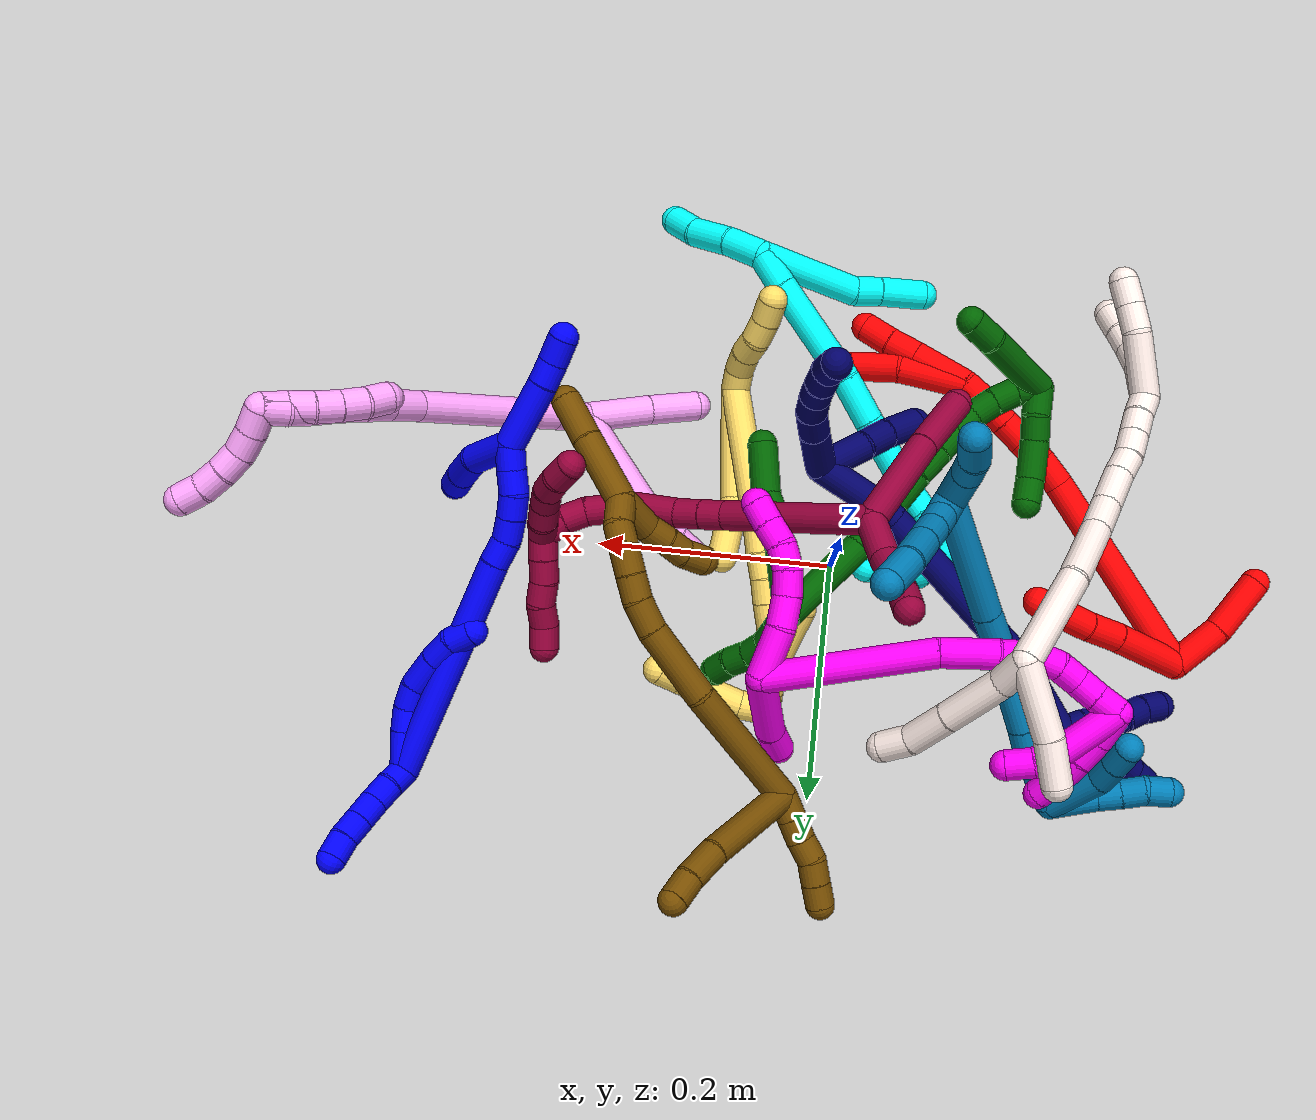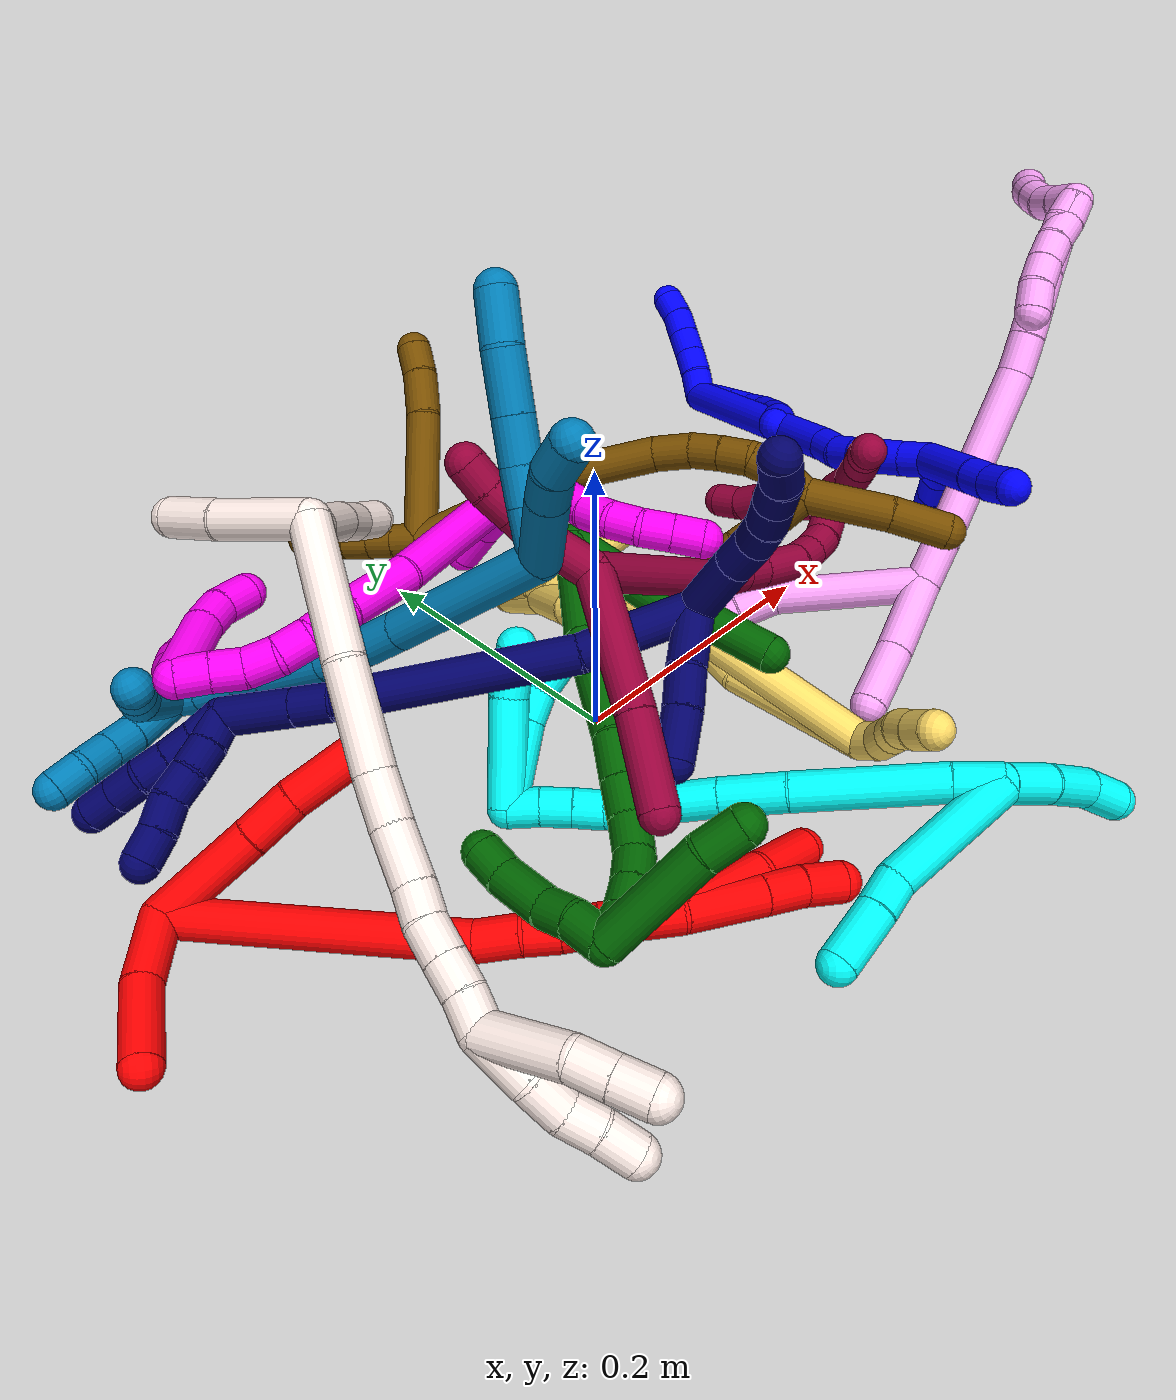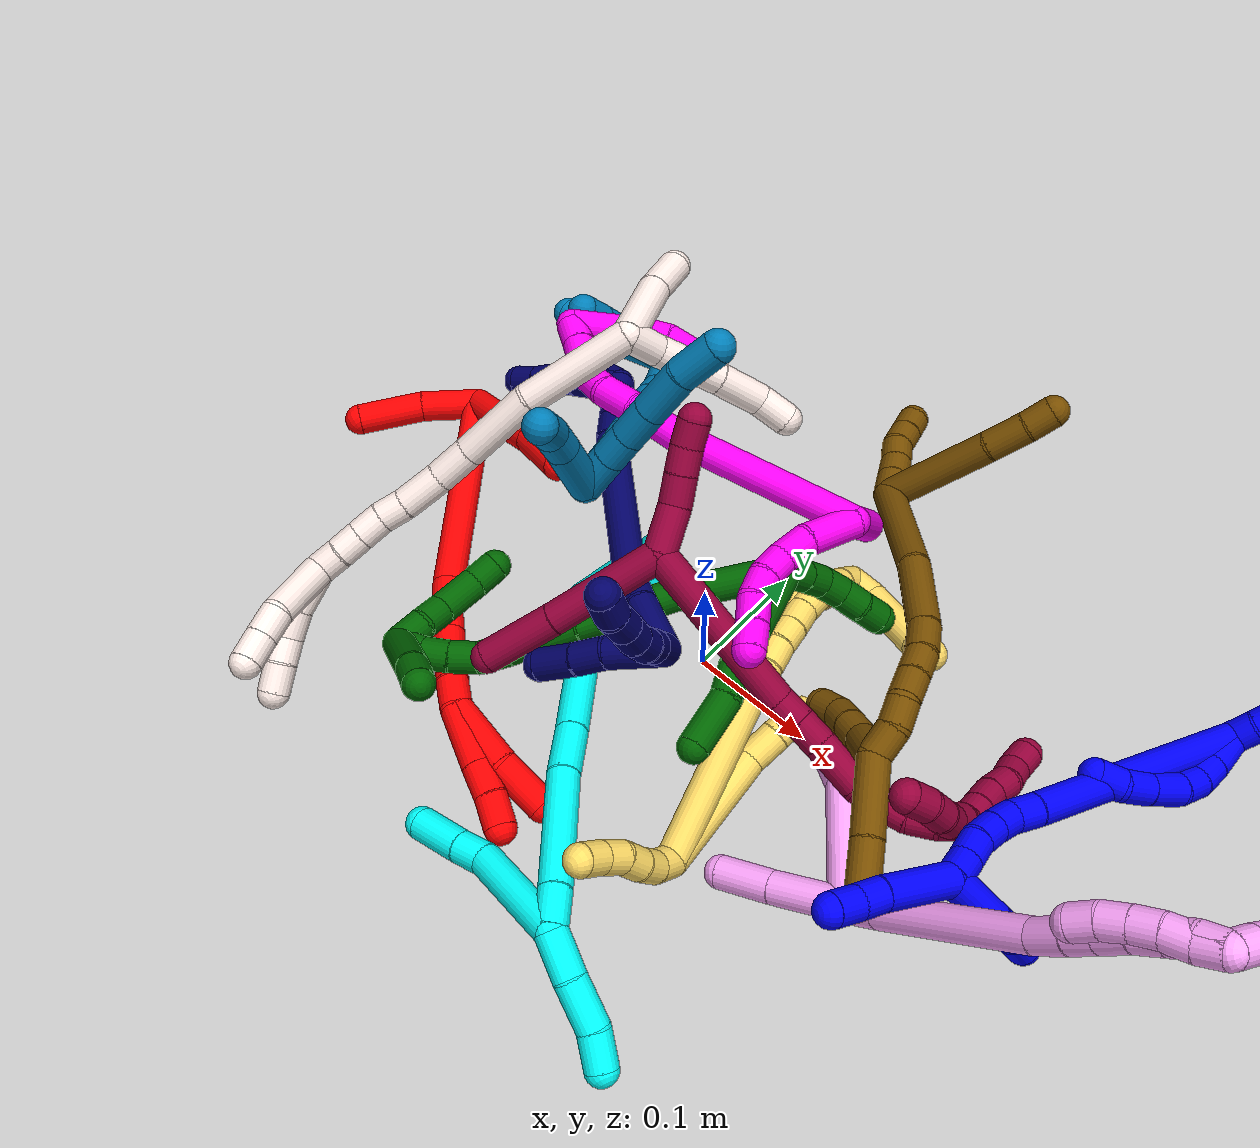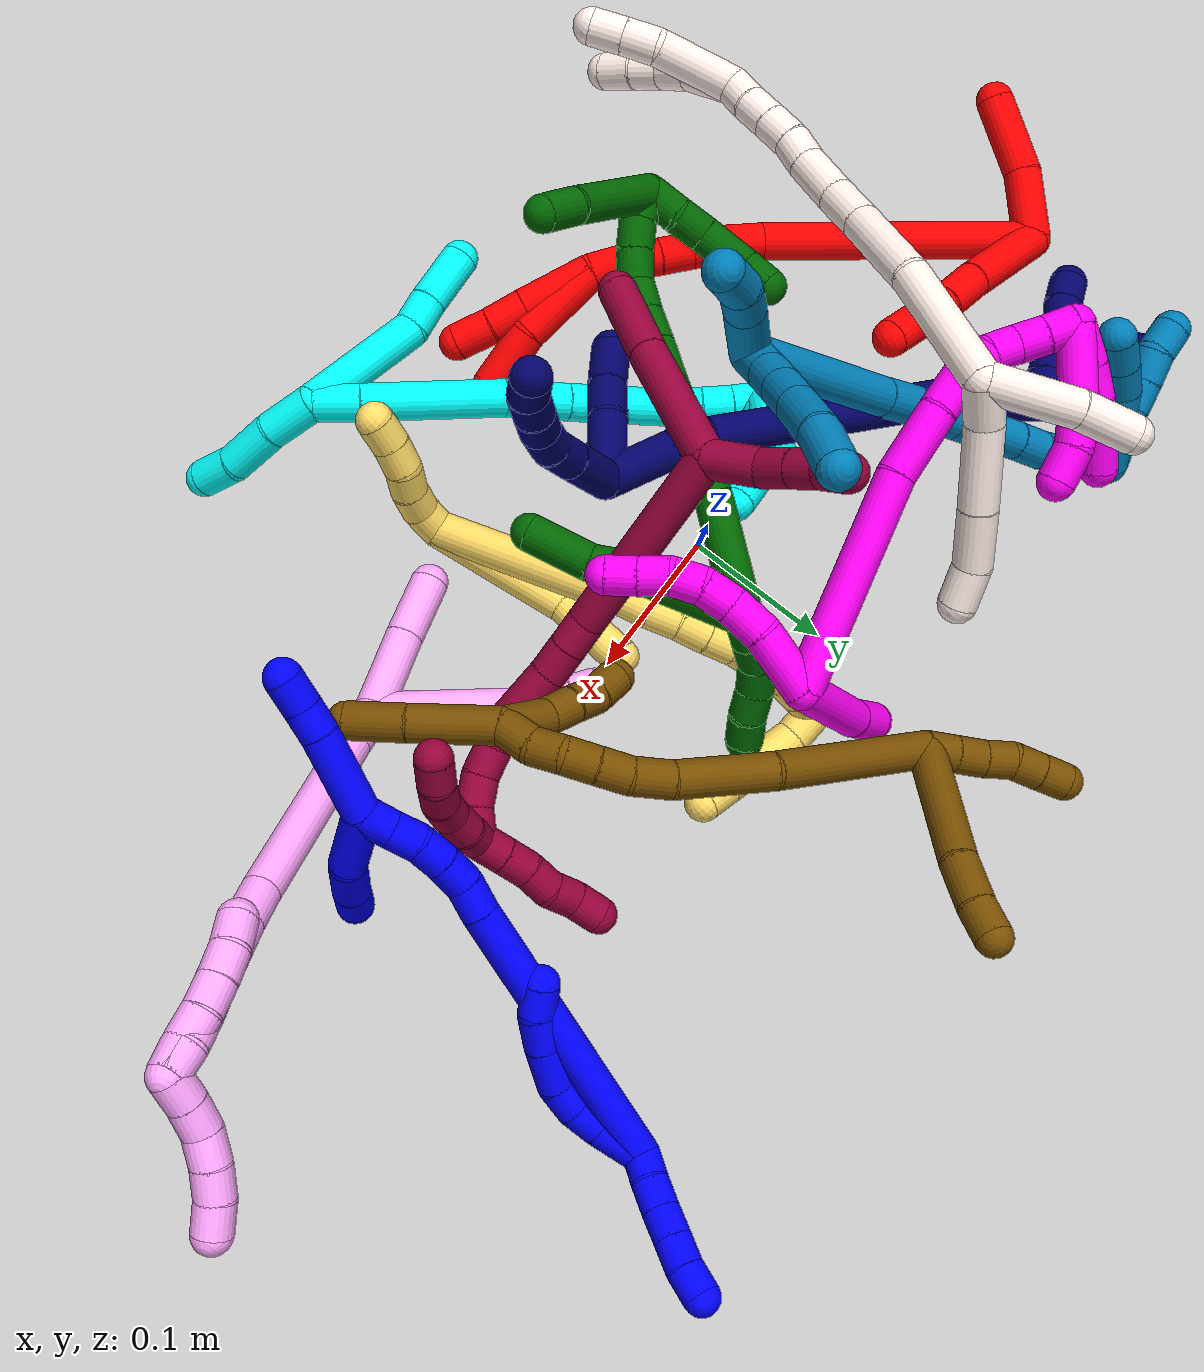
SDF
<sdf version="1.7">
 <world name="default">
  <plugin name="TubeGeneratorPlugin" filename="libtube_generator_plugin.so"/>
  <model name="photoneo_s_sensor">
   <static>1</static>
   <pose>0 0 2 1.57079 1.57079 3.14159</pose>
   <link name="link">
    <inertial><mass>0.1</mass></inertial>
    <sensor name="sensor" type="depth">
     <update_rate>30</update_rate>
     <camera>
      <horizontal_fov>1.22</horizontal_fov>
      <image><width>1920</width><height>1200</height><format>B8G8R8</format></image>
      <clip><near>0.1</near><far>4</far></clip>
      <depth_camera><output>points</output></depth_camera>
     </camera>
     <plugin name="camera_plugin" filename="libgazebo_ros_depth_camera.so">
      <baseline>0.2</baseline>
      <alwaysOn>1</alwaysOn>
      <updateRate>0.0</updateRate>
      <cameraName>camera_ir</cameraName>
      <imageTopicName>/camera/color/image_raw</imageTopicName>
      <cameraInfoTopicName>/camera/color/camera_info</cameraInfoTopicName>
      <depthImageTopicName>/camera/depth/image_raw</depthImageTopicName>
      <depthImageCameraInfoTopicName>/camera/depth/camera_info</depthImageCameraInfoTopicName>
      <pointCloudTopicName>/camera/depth/points</pointCloudTopicName>
      <frameName>fr_optical</frameName>
      <pointCloudCutoff>0.1</pointCloudCutoff>
      <pointCloudCutoffMax>2.0</pointCloudCutoffMax>
      <distortionK1>0</distortionK1>
      <distortionK2>0</distortionK2>
      <distortionK3>0</distortionK3>
      <distortionT1>0</distortionT1>
      <distortionT2>0</distortionT2>
      <CxPrime>0</CxPrime>
      <Cx>0</Cx>
      <Cy>0</Cy>
      <focalLength>0</focalLength>
      <hackBaseline>0</hackBaseline>
     </plugin>
    </sensor>
   </link>
  </model>
  <gravity>0 0 -9.8</gravity>
  <magnetic_field>6e-06 2.3e-05 -4.2e-05</magnetic_field>
  <atmosphere type="adiabatic"/>
  <physics name="default_physics" default="0" type="ode">
   <max_step_size>0.003</max_step_size>
   <real_time_factor>1</real_time_factor>
   <real_time_update_rate>1000</real_time_update_rate>
   <max_contacts>10000</max_contacts>
   <ode>
    <solver>
     <type>quick</type>
     <iters>100</iters>
     <sor>1.3</sor>
     <use_dynamic_moi_rescaling>0</use_dynamic_moi_rescaling>
    </solver>
    <constraints>
     <contact_max_correcting_vel>0</contact_max_correcting_vel>
     <contact_surface_layer>0.001</contact_surface_layer>
     <cfm>0</cfm>
     <erp>0.2</erp>
    </constraints>
   </ode>
  </physics>
  <scene><ambient>0.4 0.4 0.4 1</ambient><background>0.7 0.7 0.7 1</background><shadows>0</shadows></scene>
  <audio><device>default</device></audio>
  <spherical_coordinates>
   <surface_model>EARTH_WGS84</surface_model>
   <latitude_deg>0</latitude_deg>
   <longitude_deg>0</longitude_deg>
   <elevation>0</elevation>
   <heading_deg>0</heading_deg>
  </spherical_coordinates>
  <model name="bin">
   <static>1</static>
   <link name="bottom">
    <collision name="collision-bottom">
     <pose>0 0 -0.01 0 -0 0</pose>
     <geometry><box><size>0.8 0.6 0.02</size></box></geometry>
     <surface>
      <friction><ode><mu>100</mu><mu2>100</mu2></ode></friction>
      <contact><collide_bitmask>65535</collide_bitmask></contact>
     </surface>
    </collision>
   </link>
   <link name="west_wall">
    <collision name="collision-west_wall">
     <pose>-0.41 0 0.1 0 -0 0</pose>
     <geometry><box><size>0.02 0.6 0.2</size></box></geometry>
     <surface>
      <friction><ode><mu>100</mu><mu2>100</mu2></ode></friction>
      <contact><collide_bitmask>65535</collide_bitmask></contact>
     </surface>
    </collision>
   </link>
   <link name="east_wall">
    <collision name="collision-east_wall">
     <pose>0.41 0 0.1 0 -0 0</pose>
     <geometry><box><size>0.02 0.6 0.2</size></box></geometry>
     <surface>
      <friction><ode><mu>100</mu><mu2>100</mu2></ode></friction>
      <contact><collide_bitmask>65535</collide_bitmask></contact>
     </surface>
    </collision>
   </link>
   <link name="south_wall">
    <collision name="collision-south_wall">
     <pose>0 -0.31 0.1 0 -0 0</pose>
     <geometry><box><size>0.8 0.02 0.2</size></box></geometry>
     <surface>
      <friction><ode><mu>100</mu><mu2>100</mu2></ode></friction>
      <contact><collide_bitmask>65535</collide_bitmask></contact>
     </surface>
    </collision>
   </link>
   <link name="north_wall">
    <collision name="collision-north_wall">
     <pose>0 0.31 0.1 0 -0 0</pose>
     <geometry><box><size>0.8 0.02 0.2</size></box></geometry>
     <surface>
      <friction><ode><mu>100</mu><mu2>100</mu2></ode></friction>
      <contact><collide_bitmask>65535</collide_bitmask></contact>
     </surface>
    </collision>
   </link>
  </model>
  <model name="1">
   <static>0</static>
   <link name="1">
    <collision name="collision-cylinder-e_1_2_8">
     <pose>-0.006283 -0.005144 -0.014995 2.81111 -0.377342 -1.70578</pose>
     <geometry><cylinder><radius>0.0125</radius><length>0.034106</length></cylinder></geometry>
     <surface>
      <friction><ode><mu>1.16</mu><mu2>1.16</mu2><slip1>0</slip1><slip2>0</slip2></ode></friction>
      <contact><ode><kp>1e+06</kp><kd>1</kd><max_vel>0</max_vel><min_depth>0.001</min_depth></ode></contact>
     </surface>
    </collision>
    <visual name="visual-cylinder-e_1_2_8">
     <pose>-0.006283 -0.005144 -0.014995 2.81111 -0.377342 -1.70578</pose>
     <geometry><cylinder><radius>0.0125</radius><length>0.034106</length></cylinder></geometry>
     <material><ambient>0 0 1 1</ambient></material>
    </visual>
    <collision name="collision-cylinder-e_2_8_9">
     <pose>-0.01552 -0.012797 -0.039312 2.87872 -0.296902 -1.69381</pose>
     <geometry><cylinder><radius>0.0125</radius><length>0.02019</length></cylinder></geometry>
     <surface>
      <friction><ode><mu>1.16</mu><mu2>1.16</mu2><slip1>0</slip1><slip2>0</slip2></ode></friction>
      <contact><ode><kp>1e+06</kp><kd>1</kd><max_vel>0</max_vel><min_depth>0.001</min_depth></ode></contact>
     </surface>
    </collision>
    <visual name="visual-cylinder-e_2_8_9">
     <pose>-0.01552 -0.012797 -0.039312 2.87872 -0.296902 -1.69381</pose>
     <geometry><cylinder><radius>0.0125</radius><length>0.02019</length></cylinder></geometry>
     <material><ambient>0 0 1 1</ambient></material>
    </visual>
    <collision name="collision-cylinder-e_3_9_10">
     <pose>-0.019717 -0.015481 -0.059006 3.12472 -0.119318 -2.86099</pose>
     <geometry><cylinder><radius>0.0125</radius><length>0.020896</length></cylinder></geometry>
     <surface>
      <friction><ode><mu>1.16</mu><mu2>1.16</mu2><slip1>0</slip1><slip2>0</slip2></ode></friction>
      <contact><ode><kp>1e+06</kp><kd>1</kd><max_vel>0</max_vel><min_depth>0.001</min_depth></ode></contact>
     </surface>
    </collision>
    <visual name="visual-cylinder-e_3_9_10">
     <pose>-0.019717 -0.015481 -0.059006 3.12472 -0.119318 -2.86099</pose>
     <geometry><cylinder><radius>0.0125</radius><length>0.020896</length></cylinder></geometry>
     <material><ambient>0 0 1 1</ambient></material>
    </visual>
    <collision name="collision-cylinder-e_4_10_11">
     <pose>-0.018969 -0.013213 -0.084077 -2.97693 0.132863 -1.35707</pose>
     <geometry><cylinder><radius>0.0125</radius><length>0.030064</length></cylinder></geometry>
     <surface>
      <friction><ode><mu>1.16</mu><mu2>1.16</mu2><slip1>0</slip1><slip2>0</slip2></ode></friction>
      <contact><ode><kp>1e+06</kp><kd>1</kd><max_vel>0</max_vel><min_depth>0.001</min_depth></ode></contact>
     </surface>
    </collision>
    <visual name="visual-cylinder-e_4_10_11">
     <pose>-0.018969 -0.013213 -0.084077 -2.97693 0.132863 -1.35707</pose>
     <geometry><cylinder><radius>0.0125</radius><length>0.030064</length></cylinder></geometry>
     <material><ambient>0 0 1 1</ambient></material>
    </visual>
    <collision name="collision-cylinder-e_5_11_12">
     <pose>-0.014465 -0.008196 -0.109998 -2.91606 0.21489 -1.52207</pose>
     <geometry><cylinder><radius>0.0125</radius><length>0.023571</length></cylinder></geometry>
     <surface>
      <friction><ode><mu>1.16</mu><mu2>1.16</mu2><slip1>0</slip1><slip2>0</slip2></ode></friction>
      <contact><ode><kp>1e+06</kp><kd>1</kd><max_vel>0</max_vel><min_depth>0.001</min_depth></ode></contact>
     </surface>
    </collision>
    <visual name="visual-cylinder-e_5_11_12">
     <pose>-0.014465 -0.008196 -0.109998 -2.91606 0.21489 -1.52207</pose>
     <geometry><cylinder><radius>0.0125</radius><length>0.023571</length></cylinder></geometry>
     <material><ambient>0 0 1 1</ambient></material>
    </visual>
    <collision name="collision-cylinder-e_6_12_6">
     <pose>-0.006541 -0.002758 -0.129858 -2.82151 0.536428 -2.07947</pose>
     <geometry><cylinder><radius>0.0125</radius><length>0.021172</length></cylinder></geometry>
     <surface>
      <friction><ode><mu>1.16</mu><mu2>1.16</mu2><slip1>0</slip1><slip2>0</slip2></ode></friction>
      <contact><ode><kp>1e+06</kp><kd>1</kd><max_vel>0</max_vel><min_depth>0.001</min_depth></ode></contact>
     </surface>
    </collision>
    <visual name="visual-cylinder-e_6_12_6">
     <pose>-0.006541 -0.002758 -0.129858 -2.82151 0.536428 -2.07947</pose>
     <geometry><cylinder><radius>0.0125</radius><length>0.021172</length></cylinder></geometry>
     <material><ambient>0 0 1 1</ambient></material>
    </visual>
    <collision name="collision-cylinder-e_1_2_13">
     <pose>-0.004462 0.007036 0.00553 -0.904624 -0.46253 0.227851</pose>
     <geometry><cylinder><radius>0.0125</radius><length>0.02</length></cylinder></geometry>
     <surface>
      <friction><ode><mu>1.16</mu><mu2>1.16</mu2><slip1>0</slip1><slip2>0</slip2></ode></friction>
      <contact><ode><kp>1e+06</kp><kd>1</kd><max_vel>0</max_vel><min_depth>0.001</min_depth></ode></contact>
     </surface>
    </collision>
    <visual name="visual-cylinder-e_1_2_13">
     <pose>-0.004462 0.007036 0.00553 -0.904624 -0.46253 0.227851</pose>
     <geometry><cylinder><radius>0.0125</radius><length>0.02</length></cylinder></geometry>
     <material><ambient>0 0 1 1</ambient></material>
    </visual>
    <collision name="collision-cylinder-e_2_13_14">
     <pose>-0.012745 0.020318 0.017872 -0.742164 -0.39203 0.15422</pose>
     <geometry><cylinder><radius>0.0125</radius><length>0.02</length></cylinder></geometry>
     <surface>
      <friction><ode><mu>1.16</mu><mu2>1.16</mu2><slip1>0</slip1><slip2>0</slip2></ode></friction>
      <contact><ode><kp>1e+06</kp><kd>1</kd><max_vel>0</max_vel><min_depth>0.001</min_depth></ode></contact>
     </surface>
    </collision>
    <visual name="visual-cylinder-e_2_13_14">
     <pose>-0.012745 0.020318 0.017872 -0.742164 -0.39203 0.15422</pose>
     <geometry><cylinder><radius>0.0125</radius><length>0.02</length></cylinder></geometry>
     <material><ambient>0 0 1 1</ambient></material>
    </visual>
    <collision name="collision-cylinder-e_3_14_15">
     <pose>-0.02013 0.033041 0.031416 -0.766006 -0.364484 0.148226</pose>
     <geometry><cylinder><radius>0.0125</radius><length>0.02</length></cylinder></geometry>
     <surface>
      <friction><ode><mu>1.16</mu><mu2>1.16</mu2><slip1>0</slip1><slip2>0</slip2></ode></friction>
      <contact><ode><kp>1e+06</kp><kd>1</kd><max_vel>0</max_vel><min_depth>0.001</min_depth></ode></contact>
     </surface>
    </collision>
    <visual name="visual-cylinder-e_3_14_15">
     <pose>-0.02013 0.033041 0.031416 -0.766006 -0.364484 0.148226</pose>
     <geometry><cylinder><radius>0.0125</radius><length>0.02</length></cylinder></geometry>
     <material><ambient>0 0 1 1</ambient></material>
    </visual>
    <collision name="collision-cylinder-e_4_15_16">
     <pose>-0.027269 0.045892 0.044977 -0.751055 -0.365477 0.145453</pose>
     <geometry><cylinder><radius>0.0125</radius><length>0.02</length></cylinder></geometry>
     <surface>
      <friction><ode><mu>1.16</mu><mu2>1.16</mu2><slip1>0</slip1><slip2>0</slip2></ode></friction>
      <contact><ode><kp>1e+06</kp><kd>1</kd><max_vel>0</max_vel><min_depth>0.001</min_depth></ode></contact>
     </surface>
    </collision>
    <visual name="visual-cylinder-e_4_15_16">
     <pose>-0.027269 0.045892 0.044977 -0.751055 -0.365477 0.145453</pose>
     <geometry><cylinder><radius>0.0125</radius><length>0.02</length></cylinder></geometry>
     <material><ambient>0 0 1 1</ambient></material>
    </visual>
    <collision name="collision-cylinder-e_5_16_5">
     <pose>-0.032854 0.058791 0.059109 -0.729091 -0.202492 0.077497</pose>
     <geometry><cylinder><radius>0.0125</radius><length>0.02</length></cylinder></geometry>
     <surface>
      <friction><ode><mu>1.16</mu><mu2>1.16</mu2><slip1>0</slip1><slip2>0</slip2></ode></friction>
      <contact><ode><kp>1e+06</kp><kd>1</kd><max_vel>0</max_vel><min_depth>0.001</min_depth></ode></contact>
     </surface>
    </collision>
    <visual name="visual-cylinder-e_5_16_5">
     <pose>-0.032854 0.058791 0.059109 -0.729091 -0.202492 0.077497</pose>
     <geometry><cylinder><radius>0.0125</radius><length>0.02</length></cylinder></geometry>
     <material><ambient>0 0 1 1</ambient></material>
    </visual>
    <collision name="collision-cylinder-e_1_2_17">
     <pose>-0.00434 -0.005295 -0.098753 3.08803 -0.04386 -1.37211</pose>
     <geometry><cylinder><radius>0.0125</radius><length>0.19798</length></cylinder></geometry>
     <surface>
      <friction><ode><mu>1.16</mu><mu2>1.16</mu2><slip1>0</slip1><slip2>0</slip2></ode></friction>
      <contact><ode><kp>1e+06</kp><kd>1</kd><max_vel>0</max_vel><min_depth>0.001</min_depth></ode></contact>
     </surface>
    </collision>
    <visual name="visual-cylinder-e_1_2_17">
     <pose>-0.00434 -0.005295 -0.098753 3.08803 -0.04386 -1.37211</pose>
     <geometry><cylinder><radius>0.0125</radius><length>0.19798</length></cylinder></geometry>
     <material><ambient>0 0 1 1</ambient></material>
    </visual>
    <collision name="collision-cylinder-e_2_17_18">
     <pose>-0.008234 -0.01128 -0.208301 3.07778 0.041303 1.14875</pose>
     <geometry><cylinder><radius>0.0125</radius><length>0.021651</length></cylinder></geometry>
     <surface>
      <friction><ode><mu>1.16</mu><mu2>1.16</mu2><slip1>0</slip1><slip2>0</slip2></ode></friction>
      <contact><ode><kp>1e+06</kp><kd>1</kd><max_vel>0</max_vel><min_depth>0.001</min_depth></ode></contact>
     </surface>
    </collision>
    <visual name="visual-cylinder-e_2_17_18">
     <pose>-0.008234 -0.01128 -0.208301 3.07778 0.041303 1.14875</pose>
     <geometry><cylinder><radius>0.0125</radius><length>0.021651</length></cylinder></geometry>
     <material><ambient>0 0 1 1</ambient></material>
    </visual>
    <collision name="collision-cylinder-e_3_18_19">
     <pose>-0.010222 -0.012237 -0.228911 3.11433 -0.243117 -2.91935</pose>
     <geometry><cylinder><radius>0.0125</radius><length>0.020235</length></cylinder></geometry>
     <surface>
      <friction><ode><mu>1.16</mu><mu2>1.16</mu2><slip1>0</slip1><slip2>0</slip2></ode></friction>
      <contact><ode><kp>1e+06</kp><kd>1</kd><max_vel>0</max_vel><min_depth>0.001</min_depth></ode></contact>
     </surface>
    </collision>
    <visual name="visual-cylinder-e_3_18_19">
     <pose>-0.010222 -0.012237 -0.228911 3.11433 -0.243117 -2.91935</pose>
     <geometry><cylinder><radius>0.0125</radius><length>0.020235</length></cylinder></geometry>
     <material><ambient>0 0 1 1</ambient></material>
    </visual>
    <collision name="collision-cylinder-e_4_19_20">
     <pose>-0.015912 -0.013181 -0.248181 3.07017 -0.330762 -2.71985</pose>
     <geometry><cylinder><radius>0.0125</radius><length>0.020042</length></cylinder></geometry>
     <surface>
      <friction><ode><mu>1.16</mu><mu2>1.16</mu2><slip1>0</slip1><slip2>0</slip2></ode></friction>
      <contact><ode><kp>1e+06</kp><kd>1</kd><max_vel>0</max_vel><min_depth>0.001</min_depth></ode></contact>
     </surface>
    </collision>
    <visual name="visual-cylinder-e_4_19_20">
     <pose>-0.015912 -0.013181 -0.248181 3.07017 -0.330762 -2.71985</pose>
     <geometry><cylinder><radius>0.0125</radius><length>0.020042</length></cylinder></geometry>
     <material><ambient>0 0 1 1</ambient></material>
    </visual>
    <collision name="collision-cylinder-e_5_20_21">
     <pose>-0.024106 -0.016286 -0.266023 2.85979 -0.514792 -2.15311</pose>
     <geometry><cylinder><radius>0.0125</radius><length>0.020065</length></cylinder></geometry>
     <surface>
      <friction><ode><mu>1.16</mu><mu2>1.16</mu2><slip1>0</slip1><slip2>0</slip2></ode></friction>
      <contact><ode><kp>1e+06</kp><kd>1</kd><max_vel>0</max_vel><min_depth>0.001</min_depth></ode></contact>
     </surface>
    </collision>
    <visual name="visual-cylinder-e_5_20_21">
     <pose>-0.024106 -0.016286 -0.266023 2.85979 -0.514792 -2.15311</pose>
     <geometry><cylinder><radius>0.0125</radius><length>0.020065</length></cylinder></geometry>
     <material><ambient>0 0 1 1</ambient></material>
    </visual>
    <collision name="collision-cylinder-e_6_21_1">
     <pose>-0.033758 -0.020583 -0.283046 2.92845 -0.490003 -2.33299</pose>
     <geometry><cylinder><radius>0.0125</radius><length>0.020026</length></cylinder></geometry>
     <surface>
      <friction><ode><mu>1.16</mu><mu2>1.16</mu2><slip1>0</slip1><slip2>0</slip2></ode></friction>
      <contact><ode><kp>1e+06</kp><kd>1</kd><max_vel>0</max_vel><min_depth>0.001</min_depth></ode></contact>
     </surface>
    </collision>
    <visual name="visual-cylinder-e_6_21_1">
     <pose>-0.033758 -0.020583 -0.283046 2.92845 -0.490003 -2.33299</pose>
     <geometry><cylinder><radius>0.0125</radius><length>0.020026</length></cylinder></geometry>
     <material><ambient>0 0 1 1</ambient></material>
    </visual>
    <collision name="collision-cylinder-e_1_1_22">
     <pose>-0.037646 -0.021157 -0.320628 -3.09687 0.028466 -1.13368</pose>
     <geometry><cylinder><radius>0.0125</radius><length>0.057976</length></cylinder></geometry>
     <surface>
      <friction><ode><mu>1.16</mu><mu2>1.16</mu2><slip1>0</slip1><slip2>0</slip2></ode></friction>
      <contact><ode><kp>1e+06</kp><kd>1</kd><max_vel>0</max_vel><min_depth>0.001</min_depth></ode></contact>
     </surface>
    </collision>
    <visual name="visual-cylinder-e_1_1_22">
     <pose>-0.037646 -0.021157 -0.320628 -3.09687 0.028466 -1.13368</pose>
     <geometry><cylinder><radius>0.0125</radius><length>0.057976</length></cylinder></geometry>
     <material><ambient>0 0 1 1</ambient></material>
    </visual>
    <collision name="collision-cylinder-e_2_22_23">
     <pose>-0.037062 -0.020297 -0.35961 3.09824 -0.024026 -1.01197</pose>
     <geometry><cylinder><radius>0.0125</radius><length>0.020095</length></cylinder></geometry>
     <surface>
      <friction><ode><mu>1.16</mu><mu2>1.16</mu2><slip1>0</slip1><slip2>0</slip2></ode></friction>
      <contact><ode><kp>1e+06</kp><kd>1</kd><max_vel>0</max_vel><min_depth>0.001</min_depth></ode></contact>
     </surface>
    </collision>
    <visual name="visual-cylinder-e_2_22_23">
     <pose>-0.037062 -0.020297 -0.35961 3.09824 -0.024026 -1.01197</pose>
     <geometry><cylinder><radius>0.0125</radius><length>0.020095</length></cylinder></geometry>
     <material><ambient>0 0 1 1</ambient></material>
    </visual>
    <collision name="collision-cylinder-e_3_23_4">
     <pose>-0.03807 -0.020026 -0.38056 -3.07703 -0.069952 1.65087</pose>
     <geometry><cylinder><radius>0.0125</radius><length>0.021929</length></cylinder></geometry>
     <surface>
      <friction><ode><mu>1.16</mu><mu2>1.16</mu2><slip1>0</slip1><slip2>0</slip2></ode></friction>
      <contact><ode><kp>1e+06</kp><kd>1</kd><max_vel>0</max_vel><min_depth>0.001</min_depth></ode></contact>
     </surface>
    </collision>
    <visual name="visual-cylinder-e_3_23_4">
     <pose>-0.03807 -0.020026 -0.38056 -3.07703 -0.069952 1.65087</pose>
     <geometry><cylinder><radius>0.0125</radius><length>0.021929</length></cylinder></geometry>
     <material><ambient>0 0 1 1</ambient></material>
    </visual>
    <collision name="collision-cylinder-e_1_1_24">
     <pose>-0.046321 -0.037612 -0.276085 0.771224 -0.346391 -0.141797</pose>
     <geometry><cylinder><radius>0.0125</radius><length>0.046246</length></cylinder></geometry>
     <surface>
      <friction><ode><mu>1.16</mu><mu2>1.16</mu2><slip1>0</slip1><slip2>0</slip2></ode></friction>
      <contact><ode><kp>1e+06</kp><kd>1</kd><max_vel>0</max_vel><min_depth>0.001</min_depth></ode></contact>
     </surface>
    </collision>
    <visual name="visual-cylinder-e_1_1_24">
     <pose>-0.046321 -0.037612 -0.276085 0.771224 -0.346391 -0.141797</pose>
     <geometry><cylinder><radius>0.0125</radius><length>0.046246</length></cylinder></geometry>
     <material><ambient>0 0 1 1</ambient></material>
    </visual>
    <collision name="collision-cylinder-e_2_24_25">
     <pose>-0.054168 -0.064016 -0.248947 0.772356 0.00022 9e-05</pose>
     <geometry><cylinder><radius>0.0125</radius><length>0.032229</length></cylinder></geometry>
     <surface>
      <friction><ode><mu>1.16</mu><mu2>1.16</mu2><slip1>0</slip1><slip2>0</slip2></ode></friction>
      <contact><ode><kp>1e+06</kp><kd>1</kd><max_vel>0</max_vel><min_depth>0.001</min_depth></ode></contact>
     </surface>
    </collision>
    <visual name="visual-cylinder-e_2_24_25">
     <pose>-0.054168 -0.064016 -0.248947 0.772356 0.00022 9e-05</pose>
     <geometry><cylinder><radius>0.0125</radius><length>0.032229</length></cylinder></geometry>
     <material><ambient>0 0 1 1</ambient></material>
    </visual>
    <collision name="collision-cylinder-e_3_25_3">
     <pose>-0.053358 -0.082958 -0.229925 0.799686 0.075044 0.031726</pose>
     <geometry><cylinder><radius>0.0125</radius><length>0.021525</length></cylinder></geometry>
     <surface>
      <friction><ode><mu>1.16</mu><mu2>1.16</mu2><slip1>0</slip1><slip2>0</slip2></ode></friction>
      <contact><ode><kp>1e+06</kp><kd>1</kd><max_vel>0</max_vel><min_depth>0.001</min_depth></ode></contact>
     </surface>
    </collision>
    <visual name="visual-cylinder-e_3_25_3">
     <pose>-0.053358 -0.082958 -0.229925 0.799686 0.075044 0.031726</pose>
     <geometry><cylinder><radius>0.0125</radius><length>0.021525</length></cylinder></geometry>
     <material><ambient>0 0 1 1</ambient></material>
    </visual>
    <collision name="collision-sphere-3">
     <pose>-0.052551 -0.090655 -0.222445 0 -0 0</pose>
     <geometry><sphere><radius>0.0125</radius></sphere></geometry>
     <surface>
      <friction><ode><mu>1.16</mu><mu2>1.16</mu2><slip1>0</slip1><slip2>0</slip2></ode></friction>
      <contact><ode><kp>1e+06</kp><kd>1</kd><max_vel>0</max_vel><min_depth>0.001</min_depth></ode></contact>
     </surface>
    </collision>
    <visual name="visual-sphere-3">
     <pose>-0.052551 -0.090655 -0.222445 0 -0 0</pose>
     <geometry><sphere><radius>0.0125</radius></sphere></geometry>
     <material><ambient>0 0 1 1</ambient></material>
    </visual>
    <collision name="collision-sphere-25">
     <pose>-0.054164 -0.075262 -0.237405 0 -0 0</pose>
     <geometry><sphere><radius>0.0125</radius></sphere></geometry>
     <surface>
      <friction><ode><mu>1.16</mu><mu2>1.16</mu2><slip1>0</slip1><slip2>0</slip2></ode></friction>
      <contact><ode><kp>1e+06</kp><kd>1</kd><max_vel>0</max_vel><min_depth>0.001</min_depth></ode></contact>
     </surface>
    </collision>
    <visual name="visual-sphere-25">
     <pose>-0.054164 -0.075262 -0.237405 0 -0 0</pose>
     <geometry><sphere><radius>0.0125</radius></sphere></geometry>
     <material><ambient>0 0 1 1</ambient></material>
    </visual>
    <collision name="collision-sphere-24">
     <pose>-0.054172 -0.052771 -0.260489 0 -0 0</pose>
     <geometry><sphere><radius>0.0125</radius></sphere></geometry>
     <surface>
      <friction><ode><mu>1.16</mu><mu2>1.16</mu2><slip1>0</slip1><slip2>0</slip2></ode></friction>
      <contact><ode><kp>1e+06</kp><kd>1</kd><max_vel>0</max_vel><min_depth>0.001</min_depth></ode></contact>
     </surface>
    </collision>
    <visual name="visual-sphere-24">
     <pose>-0.054172 -0.052771 -0.260489 0 -0 0</pose>
     <geometry><sphere><radius>0.0125</radius></sphere></geometry>
     <material><ambient>0 0 1 1</ambient></material>
    </visual>
    <collision name="collision-sphere-4">
     <pose>-0.038836 -0.019321 -0.391475 0 -0 0</pose>
     <geometry><sphere><radius>0.0125</radius></sphere></geometry>
     <surface>
      <friction><ode><mu>1.16</mu><mu2>1.16</mu2><slip1>0</slip1><slip2>0</slip2></ode></friction>
      <contact><ode><kp>1e+06</kp><kd>1</kd><max_vel>0</max_vel><min_depth>0.001</min_depth></ode></contact>
     </surface>
    </collision>
    <visual name="visual-sphere-4">
     <pose>-0.038836 -0.019321 -0.391475 0 -0 0</pose>
     <geometry><sphere><radius>0.0125</radius></sphere></geometry>
     <material><ambient>0 0 1 1</ambient></material>
    </visual>
    <collision name="collision-sphere-23">
     <pose>-0.037304 -0.020732 -0.369645 0 -0 0</pose>
     <geometry><sphere><radius>0.0125</radius></sphere></geometry>
     <surface>
      <friction><ode><mu>1.16</mu><mu2>1.16</mu2><slip1>0</slip1><slip2>0</slip2></ode></friction>
      <contact><ode><kp>1e+06</kp><kd>1</kd><max_vel>0</max_vel><min_depth>0.001</min_depth></ode></contact>
     </surface>
    </collision>
    <visual name="visual-sphere-23">
     <pose>-0.037304 -0.020732 -0.369645 0 -0 0</pose>
     <geometry><sphere><radius>0.0125</radius></sphere></geometry>
     <material><ambient>0 0 1 1</ambient></material>
    </visual>
    <collision name="collision-sphere-22">
     <pose>-0.036821 -0.019861 -0.349575 0 -0 0</pose>
     <geometry><sphere><radius>0.0125</radius></sphere></geometry>
     <surface>
      <friction><ode><mu>1.16</mu><mu2>1.16</mu2><slip1>0</slip1><slip2>0</slip2></ode></friction>
      <contact><ode><kp>1e+06</kp><kd>1</kd><max_vel>0</max_vel><min_depth>0.001</min_depth></ode></contact>
     </surface>
    </collision>
    <visual name="visual-sphere-22">
     <pose>-0.036821 -0.019861 -0.349575 0 -0 0</pose>
     <geometry><sphere><radius>0.0125</radius></sphere></geometry>
     <material><ambient>0 0 1 1</ambient></material>
    </visual>
    <collision name="collision-sphere-1">
     <pose>-0.038471 -0.022452 -0.291681 0 -0 0</pose>
     <geometry><sphere><radius>0.0125</radius></sphere></geometry>
     <surface>
      <friction><ode><mu>1.16</mu><mu2>1.16</mu2><slip1>0</slip1><slip2>0</slip2></ode></friction>
      <contact><ode><kp>1e+06</kp><kd>1</kd><max_vel>0</max_vel><min_depth>0.001</min_depth></ode></contact>
     </surface>
    </collision>
    <visual name="visual-sphere-1">
     <pose>-0.038471 -0.022452 -0.291681 0 -0 0</pose>
     <geometry><sphere><radius>0.0125</radius></sphere></geometry>
     <material><ambient>0 0 1 1</ambient></material>
    </visual>
    <collision name="collision-sphere-21">
     <pose>-0.029046 -0.018714 -0.274411 0 -0 0</pose>
     <geometry><sphere><radius>0.0125</radius></sphere></geometry>
     <surface>
      <friction><ode><mu>1.16</mu><mu2>1.16</mu2><slip1>0</slip1><slip2>0</slip2></ode></friction>
      <contact><ode><kp>1e+06</kp><kd>1</kd><max_vel>0</max_vel><min_depth>0.001</min_depth></ode></contact>
     </surface>
    </collision>
    <visual name="visual-sphere-21">
     <pose>-0.029046 -0.018714 -0.274411 0 -0 0</pose>
     <geometry><sphere><radius>0.0125</radius></sphere></geometry>
     <material><ambient>0 0 1 1</ambient></material>
    </visual>
    <collision name="collision-sphere-12">
     <pose>-0.011951 -0.005621 -0.121221 0 -0 0</pose>
     <geometry><sphere><radius>0.0125</radius></sphere></geometry>
     <surface>
      <friction><ode><mu>1.16</mu><mu2>1.16</mu2><slip1>0</slip1><slip2>0</slip2></ode></friction>
      <contact><ode><kp>1e+06</kp><kd>1</kd><max_vel>0</max_vel><min_depth>0.001</min_depth></ode></contact>
     </surface>
    </collision>
    <visual name="visual-sphere-12">
     <pose>-0.011951 -0.005621 -0.121221 0 -0 0</pose>
     <geometry><sphere><radius>0.0125</radius></sphere></geometry>
     <material><ambient>0 0 1 1</ambient></material>
    </visual>
    <collision name="collision-sphere-11">
     <pose>-0.016978 -0.010771 -0.098775 0 -0 0</pose>
     <geometry><sphere><radius>0.0125</radius></sphere></geometry>
     <surface>
      <friction><ode><mu>1.16</mu><mu2>1.16</mu2><slip1>0</slip1><slip2>0</slip2></ode></friction>
      <contact><ode><kp>1e+06</kp><kd>1</kd><max_vel>0</max_vel><min_depth>0.001</min_depth></ode></contact>
     </surface>
    </collision>
    <visual name="visual-sphere-11">
     <pose>-0.016978 -0.010771 -0.098775 0 -0 0</pose>
     <geometry><sphere><radius>0.0125</radius></sphere></geometry>
     <material><ambient>0 0 1 1</ambient></material>
    </visual>
    <collision name="collision-sphere-10">
     <pose>-0.02096 -0.015656 -0.069379 0 -0 0</pose>
     <geometry><sphere><radius>0.0125</radius></sphere></geometry>
     <surface>
      <friction><ode><mu>1.16</mu><mu2>1.16</mu2><slip1>0</slip1><slip2>0</slip2></ode></friction>
      <contact><ode><kp>1e+06</kp><kd>1</kd><max_vel>0</max_vel><min_depth>0.001</min_depth></ode></contact>
     </surface>
    </collision>
    <visual name="visual-sphere-10">
     <pose>-0.02096 -0.015656 -0.069379 0 -0 0</pose>
     <geometry><sphere><radius>0.0125</radius></sphere></geometry>
     <material><ambient>0 0 1 1</ambient></material>
    </visual>
    <collision name="collision-sphere-9">
     <pose>-0.018473 -0.015306 -0.048634 0 -0 0</pose>
     <geometry><sphere><radius>0.0125</radius></sphere></geometry>
     <surface>
      <friction><ode><mu>1.16</mu><mu2>1.16</mu2><slip1>0</slip1><slip2>0</slip2></ode></friction>
      <contact><ode><kp>1e+06</kp><kd>1</kd><max_vel>0</max_vel><min_depth>0.001</min_depth></ode></contact>
     </surface>
    </collision>
    <visual name="visual-sphere-9">
     <pose>-0.018473 -0.015306 -0.048634 0 -0 0</pose>
     <geometry><sphere><radius>0.0125</radius></sphere></geometry>
     <material><ambient>0 0 1 1</ambient></material>
    </visual>
    <collision name="collision-sphere-2">
     <geometry><sphere><radius>0.0125</radius></sphere></geometry>
     <surface>
      <friction><ode><mu>1.16</mu><mu2>1.16</mu2><slip1>0</slip1><slip2>0</slip2></ode></friction>
      <contact><ode><kp>1e+06</kp><kd>1</kd><max_vel>0</max_vel><min_depth>0.001</min_depth></ode></contact>
     </surface>
    </collision>
    <visual name="visual-sphere-2">
     <geometry><sphere><radius>0.0125</radius></sphere></geometry>
     <material><ambient>0 0 1 1</ambient></material>
    </visual>
    <collision name="collision-sphere-19">
     <pose>-0.012658 -0.012505 -0.238727 0 -0 0</pose>
     <geometry><sphere><radius>0.0125</radius></sphere></geometry>
     <surface>
      <friction><ode><mu>1.16</mu><mu2>1.16</mu2><slip1>0</slip1><slip2>0</slip2></ode></friction>
      <contact><ode><kp>1e+06</kp><kd>1</kd><max_vel>0</max_vel><min_depth>0.001</min_depth></ode></contact>
     </surface>
    </collision>
    <visual name="visual-sphere-19">
     <pose>-0.012658 -0.012505 -0.238727 0 -0 0</pose>
     <geometry><sphere><radius>0.0125</radius></sphere></geometry>
     <material><ambient>0 0 1 1</ambient></material>
    </visual>
    <collision name="collision-sphere-8">
     <pose>-0.012566 -0.010289 -0.02999 0 -0 0</pose>
     <geometry><sphere><radius>0.0125</radius></sphere></geometry>
     <surface>
      <friction><ode><mu>1.16</mu><mu2>1.16</mu2><slip1>0</slip1><slip2>0</slip2></ode></friction>
      <contact><ode><kp>1e+06</kp><kd>1</kd><max_vel>0</max_vel><min_depth>0.001</min_depth></ode></contact>
     </surface>
    </collision>
    <visual name="visual-sphere-8">
     <pose>-0.012566 -0.010289 -0.02999 0 -0 0</pose>
     <geometry><sphere><radius>0.0125</radius></sphere></geometry>
     <material><ambient>0 0 1 1</ambient></material>
    </visual>
    <collision name="collision-sphere-6">
     <pose>-0.001131 0.000105 -0.138495 0 -0 0</pose>
     <geometry><sphere><radius>0.0125</radius></sphere></geometry>
     <surface>
      <friction><ode><mu>1.16</mu><mu2>1.16</mu2><slip1>0</slip1><slip2>0</slip2></ode></friction>
      <contact><ode><kp>1e+06</kp><kd>1</kd><max_vel>0</max_vel><min_depth>0.001</min_depth></ode></contact>
     </surface>
    </collision>
    <visual name="visual-sphere-6">
     <pose>-0.001131 0.000105 -0.138495 0 -0 0</pose>
     <geometry><sphere><radius>0.0125</radius></sphere></geometry>
     <material><ambient>0 0 1 1</ambient></material>
    </visual>
    <collision name="collision-sphere-13">
     <pose>-0.008924 0.014072 0.011061 0 -0 0</pose>
     <geometry><sphere><radius>0.0125</radius></sphere></geometry>
     <surface>
      <friction><ode><mu>1.16</mu><mu2>1.16</mu2><slip1>0</slip1><slip2>0</slip2></ode></friction>
      <contact><ode><kp>1e+06</kp><kd>1</kd><max_vel>0</max_vel><min_depth>0.001</min_depth></ode></contact>
     </surface>
    </collision>
    <visual name="visual-sphere-13">
     <pose>-0.008924 0.014072 0.011061 0 -0 0</pose>
     <geometry><sphere><radius>0.0125</radius></sphere></geometry>
     <material><ambient>0 0 1 1</ambient></material>
    </visual>
    <collision name="collision-sphere-14">
     <pose>-0.016566 0.026564 0.024683 0 -0 0</pose>
     <geometry><sphere><radius>0.0125</radius></sphere></geometry>
     <surface>
      <friction><ode><mu>1.16</mu><mu2>1.16</mu2><slip1>0</slip1><slip2>0</slip2></ode></friction>
      <contact><ode><kp>1e+06</kp><kd>1</kd><max_vel>0</max_vel><min_depth>0.001</min_depth></ode></contact>
     </surface>
    </collision>
    <visual name="visual-sphere-14">
     <pose>-0.016566 0.026564 0.024683 0 -0 0</pose>
     <geometry><sphere><radius>0.0125</radius></sphere></geometry>
     <material><ambient>0 0 1 1</ambient></material>
    </visual>
    <collision name="collision-sphere-15">
     <pose>-0.023695 0.039518 0.03815 0 -0 0</pose>
     <geometry><sphere><radius>0.0125</radius></sphere></geometry>
     <surface>
      <friction><ode><mu>1.16</mu><mu2>1.16</mu2><slip1>0</slip1><slip2>0</slip2></ode></friction>
      <contact><ode><kp>1e+06</kp><kd>1</kd><max_vel>0</max_vel><min_depth>0.001</min_depth></ode></contact>
     </surface>
    </collision>
    <visual name="visual-sphere-15">
     <pose>-0.023695 0.039518 0.03815 0 -0 0</pose>
     <geometry><sphere><radius>0.0125</radius></sphere></geometry>
     <material><ambient>0 0 1 1</ambient></material>
    </visual>
    <collision name="collision-sphere-16">
     <pose>-0.030843 0.052265 0.051803 0 -0 0</pose>
     <geometry><sphere><radius>0.0125</radius></sphere></geometry>
     <surface>
      <friction><ode><mu>1.16</mu><mu2>1.16</mu2><slip1>0</slip1><slip2>0</slip2></ode></friction>
      <contact><ode><kp>1e+06</kp><kd>1</kd><max_vel>0</max_vel><min_depth>0.001</min_depth></ode></contact>
     </surface>
    </collision>
    <visual name="visual-sphere-16">
     <pose>-0.030843 0.052265 0.051803 0 -0 0</pose>
     <geometry><sphere><radius>0.0125</radius></sphere></geometry>
     <material><ambient>0 0 1 1</ambient></material>
    </visual>
    <collision name="collision-sphere-5">
     <pose>-0.034865 0.065317 0.066414 0 -0 0</pose>
     <geometry><sphere><radius>0.0125</radius></sphere></geometry>
     <surface>
      <friction><ode><mu>1.16</mu><mu2>1.16</mu2><slip1>0</slip1><slip2>0</slip2></ode></friction>
      <contact><ode><kp>1e+06</kp><kd>1</kd><max_vel>0</max_vel><min_depth>0.001</min_depth></ode></contact>
     </surface>
    </collision>
    <visual name="visual-sphere-5">
     <pose>-0.034865 0.065317 0.066414 0 -0 0</pose>
     <geometry><sphere><radius>0.0125</radius></sphere></geometry>
     <material><ambient>0 0 1 1</ambient></material>
    </visual>
    <collision name="collision-sphere-17">
     <pose>-0.008681 -0.01059 -0.197506 0 -0 0</pose>
     <geometry><sphere><radius>0.0125</radius></sphere></geometry>
     <surface>
      <friction><ode><mu>1.16</mu><mu2>1.16</mu2><slip1>0</slip1><slip2>0</slip2></ode></friction>
      <contact><ode><kp>1e+06</kp><kd>1</kd><max_vel>0</max_vel><min_depth>0.001</min_depth></ode></contact>
     </surface>
    </collision>
    <visual name="visual-sphere-17">
     <pose>-0.008681 -0.01059 -0.197506 0 -0 0</pose>
     <geometry><sphere><radius>0.0125</radius></sphere></geometry>
     <material><ambient>0 0 1 1</ambient></material>
    </visual>
    <collision name="collision-sphere-18">
     <pose>-0.007787 -0.011969 -0.219095 0 -0 0</pose>
     <geometry><sphere><radius>0.0125</radius></sphere></geometry>
     <surface>
      <friction><ode><mu>1.16</mu><mu2>1.16</mu2><slip1>0</slip1><slip2>0</slip2></ode></friction>
      <contact><ode><kp>1e+06</kp><kd>1</kd><max_vel>0</max_vel><min_depth>0.001</min_depth></ode></contact>
     </surface>
    </collision>
    <visual name="visual-sphere-18">
     <pose>-0.007787 -0.011969 -0.219095 0 -0 0</pose>
     <geometry><sphere><radius>0.0125</radius></sphere></geometry>
     <material><ambient>0 0 1 1</ambient></material>
    </visual>
    <collision name="collision-sphere-20">
     <pose>-0.019167 -0.013857 -0.257635 0 -0 0</pose>
     <geometry><sphere><radius>0.0125</radius></sphere></geometry>
     <surface>
      <friction><ode><mu>1.16</mu><mu2>1.16</mu2><slip1>0</slip1><slip2>0</slip2></ode></friction>
      <contact><ode><kp>1e+06</kp><kd>1</kd><max_vel>0</max_vel><min_depth>0.001</min_depth></ode></contact>
     </surface>
    </collision>
    <visual name="visual-sphere-20">
     <pose>-0.019167 -0.013857 -0.257635 0 -0 0</pose>
     <geometry><sphere><radius>0.0125</radius></sphere></geometry>
     <material><ambient>0 0 1 1</ambient></material>
    </visual>
    <inertial>
     <pose>-0.020614 -0.01108 -0.149072 0 -0 0</pose>
     <mass>0.75</mass>
     <inertia>
      <ixx>-0.000525</ixx>
      <ixy>0</ixy>
      <ixz>0</ixz>
      <iyy>-0.000785</iyy>
      <iyz>0</iyz>
      <izz>4.7e-05</izz>
     </inertia>
    </inertial>
   </link>
   <pose>0.341427 0.209729 0.011763 1.94531 0.356726 2.86741</pose>
  </model>
  <model name="2">
   <static>0</static>
   <link name="2">
    <collision name="collision-cylinder-e_1_2_8">
     <pose>0.003643 0.022546 -0.024997 -2.40769 0.107813 -0.278951</pose>
     <geometry><cylinder><radius>0.0125</radius><length>0.067718</length></cylinder></geometry>
     <surface>
      <friction><ode><mu>1.16</mu><mu2>1.16</mu2><slip1>0</slip1><slip2>0</slip2></ode></friction>
      <contact><ode><kp>1e+06</kp><kd>1</kd><max_vel>0</max_vel><min_depth>0.001</min_depth></ode></contact>
     </surface>
    </collision>
    <visual name="visual-cylinder-e_1_2_8">
     <pose>0.003643 0.022546 -0.024997 -2.40769 0.107813 -0.278951</pose>
     <geometry><cylinder><radius>0.0125</radius><length>0.067718</length></cylinder></geometry>
     <material><ambient>1 0 0 1</ambient></material>
    </visual>
    <collision name="collision-cylinder-e_2_8_9">
     <pose>0.007918 0.055553 -0.061783 -2.41587 0.040011 -0.1053</pose>
     <geometry><cylinder><radius>0.0125</radius><length>0.031547</length></cylinder></geometry>
     <surface>
      <friction><ode><mu>1.16</mu><mu2>1.16</mu2><slip1>0</slip1><slip2>0</slip2></ode></friction>
      <contact><ode><kp>1e+06</kp><kd>1</kd><max_vel>0</max_vel><min_depth>0.001</min_depth></ode></contact>
     </surface>
    </collision>
    <visual name="visual-cylinder-e_2_8_9">
     <pose>0.007918 0.055553 -0.061783 -2.41587 0.040011 -0.1053</pose>
     <geometry><cylinder><radius>0.0125</radius><length>0.031547</length></cylinder></geometry>
     <material><ambient>1 0 0 1</ambient></material>
    </visual>
    <collision name="collision-cylinder-e_3_9_6">
     <pose>0.011098 0.080638 -0.094142 -2.52352 0.100649 -0.312938</pose>
     <geometry><cylinder><radius>0.0125</radius><length>0.050735</length></cylinder></geometry>
     <surface>
      <friction><ode><mu>1.16</mu><mu2>1.16</mu2><slip1>0</slip1><slip2>0</slip2></ode></friction>
      <contact><ode><kp>1e+06</kp><kd>1</kd><max_vel>0</max_vel><min_depth>0.001</min_depth></ode></contact>
     </surface>
    </collision>
    <visual name="visual-cylinder-e_3_9_6">
     <pose>0.011098 0.080638 -0.094142 -2.52352 0.100649 -0.312938</pose>
     <geometry><cylinder><radius>0.0125</radius><length>0.050735</length></cylinder></geometry>
     <material><ambient>1 0 0 1</ambient></material>
    </visual>
    <collision name="collision-cylinder-e_1_2_10">
     <pose>0.019276 -0.010522 0.008447 0.894331 0.960089 0.48938</pose>
     <geometry><cylinder><radius>0.0125</radius><length>0.047059</length></cylinder></geometry>
     <surface>
      <friction><ode><mu>1.16</mu><mu2>1.16</mu2><slip1>0</slip1><slip2>0</slip2></ode></friction>
      <contact><ode><kp>1e+06</kp><kd>1</kd><max_vel>0</max_vel><min_depth>0.001</min_depth></ode></contact>
     </surface>
    </collision>
    <visual name="visual-cylinder-e_1_2_10">
     <pose>0.019276 -0.010522 0.008447 0.894331 0.960089 0.48938</pose>
     <geometry><cylinder><radius>0.0125</radius><length>0.047059</length></cylinder></geometry>
     <material><ambient>1 0 0 1</ambient></material>
    </visual>
    <collision name="collision-cylinder-e_2_10_5">
     <pose>0.06239 -0.031841 0.020877 1.21743 1.121 0.824773</pose>
     <geometry><cylinder><radius>0.0125</radius><length>0.052941</length></cylinder></geometry>
     <surface>
      <friction><ode><mu>1.16</mu><mu2>1.16</mu2><slip1>0</slip1><slip2>0</slip2></ode></friction>
      <contact><ode><kp>1e+06</kp><kd>1</kd><max_vel>0</max_vel><min_depth>0.001</min_depth></ode></contact>
     </surface>
    </collision>
    <visual name="visual-cylinder-e_2_10_5">
     <pose>0.06239 -0.031841 0.020877 1.21743 1.121 0.824773</pose>
     <geometry><cylinder><radius>0.0125</radius><length>0.052941</length></cylinder></geometry>
     <material><ambient>1 0 0 1</ambient></material>
    </visual>
    <collision name="collision-cylinder-e_1_2_11">
     <pose>0.046022 0.001227 -0.078355 -3.12594 0.531017 -3.08403</pose>
     <geometry><cylinder><radius>0.0125</radius><length>0.181759</length></cylinder></geometry>
     <surface>
      <friction><ode><mu>1.16</mu><mu2>1.16</mu2><slip1>0</slip1><slip2>0</slip2></ode></friction>
      <contact><ode><kp>1e+06</kp><kd>1</kd><max_vel>0</max_vel><min_depth>0.001</min_depth></ode></contact>
     </surface>
    </collision>
    <visual name="visual-cylinder-e_1_2_11">
     <pose>0.046022 0.001227 -0.078355 -3.12594 0.531017 -3.08403</pose>
     <geometry><cylinder><radius>0.0125</radius><length>0.181759</length></cylinder></geometry>
     <material><ambient>1 0 0 1</ambient></material>
    </visual>
    <collision name="collision-cylinder-e_2_11_12">
     <pose>0.098508 0.005619 -0.168313 -2.87528 0.493096 -2.16337</pose>
     <geometry><cylinder><radius>0.0125</radius><length>0.027308</length></cylinder></geometry>
     <surface>
      <friction><ode><mu>1.16</mu><mu2>1.16</mu2><slip1>0</slip1><slip2>0</slip2></ode></friction>
      <contact><ode><kp>1e+06</kp><kd>1</kd><max_vel>0</max_vel><min_depth>0.001</min_depth></ode></contact>
     </surface>
    </collision>
    <visual name="visual-cylinder-e_2_11_12">
     <pose>0.098508 0.005619 -0.168313 -2.87528 0.493096 -2.16337</pose>
     <geometry><cylinder><radius>0.0125</radius><length>0.027308</length></cylinder></geometry>
     <material><ambient>1 0 0 1</ambient></material>
    </visual>
    <collision name="collision-cylinder-e_3_12_13">
     <pose>0.108601 0.009823 -0.189989 -3.03888 0.34426 -2.56662</pose>
     <geometry><cylinder><radius>0.0125</radius><length>0.021515</length></cylinder></geometry>
     <surface>
      <friction><ode><mu>1.16</mu><mu2>1.16</mu2><slip1>0</slip1><slip2>0</slip2></ode></friction>
      <contact><ode><kp>1e+06</kp><kd>1</kd><max_vel>0</max_vel><min_depth>0.001</min_depth></ode></contact>
     </surface>
    </collision>
    <visual name="visual-cylinder-e_3_12_13">
     <pose>0.108601 0.009823 -0.189989 -3.03888 0.34426 -2.56662</pose>
     <geometry><cylinder><radius>0.0125</radius><length>0.021515</length></cylinder></geometry>
     <material><ambient>1 0 0 1</ambient></material>
    </visual>
    <collision name="collision-cylinder-e_4_13_14">
     <pose>0.116382 0.013449 -0.210213 -2.89196 0.377182 -1.9785</pose>
     <geometry><cylinder><radius>0.0125</radius><length>0.022534</length></cylinder></geometry>
     <surface>
      <friction><ode><mu>1.16</mu><mu2>1.16</mu2><slip1>0</slip1><slip2>0</slip2></ode></friction>
      <contact><ode><kp>1e+06</kp><kd>1</kd><max_vel>0</max_vel><min_depth>0.001</min_depth></ode></contact>
     </surface>
    </collision>
    <visual name="visual-cylinder-e_4_13_14">
     <pose>0.116382 0.013449 -0.210213 -2.89196 0.377182 -1.9785</pose>
     <geometry><cylinder><radius>0.0125</radius><length>0.022534</length></cylinder></geometry>
     <material><ambient>1 0 0 1</ambient></material>
    </visual>
    <collision name="collision-cylinder-e_5_14_15">
     <pose>0.12498 0.018354 -0.230988 -2.92685 0.388346 -2.13879</pose>
     <geometry><cylinder><radius>0.0125</radius><length>0.0235</length></cylinder></geometry>
     <surface>
      <friction><ode><mu>1.16</mu><mu2>1.16</mu2><slip1>0</slip1><slip2>0</slip2></ode></friction>
      <contact><ode><kp>1e+06</kp><kd>1</kd><max_vel>0</max_vel><min_depth>0.001</min_depth></ode></contact>
     </surface>
    </collision>
    <visual name="visual-cylinder-e_5_14_15">
     <pose>0.12498 0.018354 -0.230988 -2.92685 0.388346 -2.13879</pose>
     <geometry><cylinder><radius>0.0125</radius><length>0.0235</length></cylinder></geometry>
     <material><ambient>1 0 0 1</ambient></material>
    </visual>
    <collision name="collision-cylinder-e_6_15_1">
     <pose>0.132679 0.022028 -0.252763 -3.02054 0.281594 -2.33349</pose>
     <geometry><cylinder><radius>0.0125</radius><length>0.023385</length></cylinder></geometry>
     <surface>
      <friction><ode><mu>1.16</mu><mu2>1.16</mu2><slip1>0</slip1><slip2>0</slip2></ode></friction>
      <contact><ode><kp>1e+06</kp><kd>1</kd><max_vel>0</max_vel><min_depth>0.001</min_depth></ode></contact>
     </surface>
    </collision>
    <visual name="visual-cylinder-e_6_15_1">
     <pose>0.132679 0.022028 -0.252763 -3.02054 0.281594 -2.33349</pose>
     <geometry><cylinder><radius>0.0125</radius><length>0.023385</length></cylinder></geometry>
     <material><ambient>1 0 0 1</ambient></material>
    </visual>
    <collision name="collision-cylinder-e_1_1_16">
     <pose>0.130227 0.029544 -0.291434 -2.9214 -0.199459 1.47133</pose>
     <geometry><cylinder><radius>0.0125</radius><length>0.057546</length></cylinder></geometry>
     <surface>
      <friction><ode><mu>1.16</mu><mu2>1.16</mu2><slip1>0</slip1><slip2>0</slip2></ode></friction>
      <contact><ode><kp>1e+06</kp><kd>1</kd><max_vel>0</max_vel><min_depth>0.001</min_depth></ode></contact>
     </surface>
    </collision>
    <visual name="visual-cylinder-e_1_1_16">
     <pose>0.130227 0.029544 -0.291434 -2.9214 -0.199459 1.47133</pose>
     <geometry><cylinder><radius>0.0125</radius><length>0.057546</length></cylinder></geometry>
     <material><ambient>1 0 0 1</ambient></material>
    </visual>
    <collision name="collision-cylinder-e_2_16_4">
     <pose>0.11609 0.036878 -0.3384 -3.0813 -0.408677 2.85259</pose>
     <geometry><cylinder><radius>0.0125</radius><length>0.042454</length></cylinder></geometry>
     <surface>
      <friction><ode><mu>1.16</mu><mu2>1.16</mu2><slip1>0</slip1><slip2>0</slip2></ode></friction>
      <contact><ode><kp>1e+06</kp><kd>1</kd><max_vel>0</max_vel><min_depth>0.001</min_depth></ode></contact>
     </surface>
    </collision>
    <visual name="visual-cylinder-e_2_16_4">
     <pose>0.11609 0.036878 -0.3384 -3.0813 -0.408677 2.85259</pose>
     <geometry><cylinder><radius>0.0125</radius><length>0.042454</length></cylinder></geometry>
     <material><ambient>1 0 0 1</ambient></material>
    </visual>
    <collision name="collision-cylinder-e_1_1_17">
     <pose>0.137547 0.025761 -0.288426 -3.04492 0.065642 -1.19261</pose>
     <geometry><cylinder><radius>0.0125</radius><length>0.049363</length></cylinder></geometry>
     <surface>
      <friction><ode><mu>1.16</mu><mu2>1.16</mu2><slip1>0</slip1><slip2>0</slip2></ode></friction>
      <contact><ode><kp>1e+06</kp><kd>1</kd><max_vel>0</max_vel><min_depth>0.001</min_depth></ode></contact>
     </surface>
    </collision>
    <visual name="visual-cylinder-e_1_1_17">
     <pose>0.137547 0.025761 -0.288426 -3.04492 0.065642 -1.19261</pose>
     <geometry><cylinder><radius>0.0125</radius><length>0.049363</length></cylinder></geometry>
     <material><ambient>1 0 0 1</ambient></material>
    </visual>
    <collision name="collision-cylinder-e_2_17_18">
     <pose>0.139612 0.029373 -0.325564 -3.04412 0.03518 -0.692305</pose>
     <geometry><cylinder><radius>0.0125</radius><length>0.025386</length></cylinder></geometry>
     <surface>
      <friction><ode><mu>1.16</mu><mu2>1.16</mu2><slip1>0</slip1><slip2>0</slip2></ode></friction>
      <contact><ode><kp>1e+06</kp><kd>1</kd><max_vel>0</max_vel><min_depth>0.001</min_depth></ode></contact>
     </surface>
    </collision>
    <visual name="visual-cylinder-e_2_17_18">
     <pose>0.139612 0.029373 -0.325564 -3.04412 0.03518 -0.692305</pose>
     <geometry><cylinder><radius>0.0125</radius><length>0.025386</length></cylinder></geometry>
     <material><ambient>1 0 0 1</ambient></material>
    </visual>
    <collision name="collision-cylinder-e_3_18_3">
     <pose>0.141187 0.030607 -0.350764 3.14151 0.089448 3.13969</pose>
     <geometry><cylinder><radius>0.0125</radius><length>0.025251</length></cylinder></geometry>
     <surface>
      <friction><ode><mu>1.16</mu><mu2>1.16</mu2><slip1>0</slip1><slip2>0</slip2></ode></friction>
      <contact><ode><kp>1e+06</kp><kd>1</kd><max_vel>0</max_vel><min_depth>0.001</min_depth></ode></contact>
     </surface>
    </collision>
    <visual name="visual-cylinder-e_3_18_3">
     <pose>0.141187 0.030607 -0.350764 3.14151 0.089448 3.13969</pose>
     <geometry><cylinder><radius>0.0125</radius><length>0.025251</length></cylinder></geometry>
     <material><ambient>1 0 0 1</ambient></material>
    </visual>
    <collision name="collision-sphere-3">
     <pose>0.142315 0.030606 -0.363339 0 -0 0</pose>
     <geometry><sphere><radius>0.0125</radius></sphere></geometry>
     <surface>
      <friction><ode><mu>1.16</mu><mu2>1.16</mu2><slip1>0</slip1><slip2>0</slip2></ode></friction>
      <contact><ode><kp>1e+06</kp><kd>1</kd><max_vel>0</max_vel><min_depth>0.001</min_depth></ode></contact>
     </surface>
    </collision>
    <visual name="visual-sphere-3">
     <pose>0.142315 0.030606 -0.363339 0 -0 0</pose>
     <geometry><sphere><radius>0.0125</radius></sphere></geometry>
     <material><ambient>1 0 0 1</ambient></material>
    </visual>
    <collision name="collision-sphere-5">
     <pose>0.086228 -0.042639 0.02486 0 -0 0</pose>
     <geometry><sphere><radius>0.0125</radius></sphere></geometry>
     <surface>
      <friction><ode><mu>1.16</mu><mu2>1.16</mu2><slip1>0</slip1><slip2>0</slip2></ode></friction>
      <contact><ode><kp>1e+06</kp><kd>1</kd><max_vel>0</max_vel><min_depth>0.001</min_depth></ode></contact>
     </surface>
    </collision>
    <visual name="visual-sphere-5">
     <pose>0.086228 -0.042639 0.02486 0 -0 0</pose>
     <geometry><sphere><radius>0.0125</radius></sphere></geometry>
     <material><ambient>1 0 0 1</ambient></material>
    </visual>
    <collision name="collision-sphere-10">
     <pose>0.038552 -0.021043 0.016894 0 -0 0</pose>
     <geometry><sphere><radius>0.0125</radius></sphere></geometry>
     <surface>
      <friction><ode><mu>1.16</mu><mu2>1.16</mu2><slip1>0</slip1><slip2>0</slip2></ode></friction>
      <contact><ode><kp>1e+06</kp><kd>1</kd><max_vel>0</max_vel><min_depth>0.001</min_depth></ode></contact>
     </surface>
    </collision>
    <visual name="visual-sphere-10">
     <pose>0.038552 -0.021043 0.016894 0 -0 0</pose>
     <geometry><sphere><radius>0.0125</radius></sphere></geometry>
     <material><ambient>1 0 0 1</ambient></material>
    </visual>
    <collision name="collision-sphere-6">
     <pose>0.013646 0.095263 -0.114712 0 -0 0</pose>
     <geometry><sphere><radius>0.0125</radius></sphere></geometry>
     <surface>
      <friction><ode><mu>1.16</mu><mu2>1.16</mu2><slip1>0</slip1><slip2>0</slip2></ode></friction>
      <contact><ode><kp>1e+06</kp><kd>1</kd><max_vel>0</max_vel><min_depth>0.001</min_depth></ode></contact>
     </surface>
    </collision>
    <visual name="visual-sphere-6">
     <pose>0.013646 0.095263 -0.114712 0 -0 0</pose>
     <geometry><sphere><radius>0.0125</radius></sphere></geometry>
     <material><ambient>1 0 0 1</ambient></material>
    </visual>
    <collision name="collision-sphere-9">
     <pose>0.008549 0.066013 -0.073572 0 -0 0</pose>
     <geometry><sphere><radius>0.0125</radius></sphere></geometry>
     <surface>
      <friction><ode><mu>1.16</mu><mu2>1.16</mu2><slip1>0</slip1><slip2>0</slip2></ode></friction>
      <contact><ode><kp>1e+06</kp><kd>1</kd><max_vel>0</max_vel><min_depth>0.001</min_depth></ode></contact>
     </surface>
    </collision>
    <visual name="visual-sphere-9">
     <pose>0.008549 0.066013 -0.073572 0 -0 0</pose>
     <geometry><sphere><radius>0.0125</radius></sphere></geometry>
     <material><ambient>1 0 0 1</ambient></material>
    </visual>
    <collision name="collision-sphere-2">
     <geometry><sphere><radius>0.0125</radius></sphere></geometry>
     <surface>
      <friction><ode><mu>1.16</mu><mu2>1.16</mu2><slip1>0</slip1><slip2>0</slip2></ode></friction>
      <contact><ode><kp>1e+06</kp><kd>1</kd><max_vel>0</max_vel><min_depth>0.001</min_depth></ode></contact>
     </surface>
    </collision>
    <visual name="visual-sphere-2">
     <geometry><sphere><radius>0.0125</radius></sphere></geometry>
     <material><ambient>1 0 0 1</ambient></material>
    </visual>
    <collision name="collision-sphere-8">
     <pose>0.007287 0.045092 -0.049994 0 -0 0</pose>
     <geometry><sphere><radius>0.0125</radius></sphere></geometry>
     <surface>
      <friction><ode><mu>1.16</mu><mu2>1.16</mu2><slip1>0</slip1><slip2>0</slip2></ode></friction>
      <contact><ode><kp>1e+06</kp><kd>1</kd><max_vel>0</max_vel><min_depth>0.001</min_depth></ode></contact>
     </surface>
    </collision>
    <visual name="visual-sphere-8">
     <pose>0.007287 0.045092 -0.049994 0 -0 0</pose>
     <geometry><sphere><radius>0.0125</radius></sphere></geometry>
     <material><ambient>1 0 0 1</ambient></material>
    </visual>
    <collision name="collision-sphere-11">
     <pose>0.092045 0.002454 -0.15671 0 -0 0</pose>
     <geometry><sphere><radius>0.0125</radius></sphere></geometry>
     <surface>
      <friction><ode><mu>1.16</mu><mu2>1.16</mu2><slip1>0</slip1><slip2>0</slip2></ode></friction>
      <contact><ode><kp>1e+06</kp><kd>1</kd><max_vel>0</max_vel><min_depth>0.001</min_depth></ode></contact>
     </surface>
    </collision>
    <visual name="visual-sphere-11">
     <pose>0.092045 0.002454 -0.15671 0 -0 0</pose>
     <geometry><sphere><radius>0.0125</radius></sphere></geometry>
     <material><ambient>1 0 0 1</ambient></material>
    </visual>
    <collision name="collision-sphere-12">
     <pose>0.104971 0.008784 -0.179917 0 -0 0</pose>
     <geometry><sphere><radius>0.0125</radius></sphere></geometry>
     <surface>
      <friction><ode><mu>1.16</mu><mu2>1.16</mu2><slip1>0</slip1><slip2>0</slip2></ode></friction>
      <contact><ode><kp>1e+06</kp><kd>1</kd><max_vel>0</max_vel><min_depth>0.001</min_depth></ode></contact>
     </surface>
    </collision>
    <visual name="visual-sphere-12">
     <pose>0.104971 0.008784 -0.179917 0 -0 0</pose>
     <geometry><sphere><radius>0.0125</radius></sphere></geometry>
     <material><ambient>1 0 0 1</ambient></material>
    </visual>
    <collision name="collision-sphere-13">
     <pose>0.112232 0.010861 -0.200062 0 -0 0</pose>
     <geometry><sphere><radius>0.0125</radius></sphere></geometry>
     <surface>
      <friction><ode><mu>1.16</mu><mu2>1.16</mu2><slip1>0</slip1><slip2>0</slip2></ode></friction>
      <contact><ode><kp>1e+06</kp><kd>1</kd><max_vel>0</max_vel><min_depth>0.001</min_depth></ode></contact>
     </surface>
    </collision>
    <visual name="visual-sphere-13">
     <pose>0.112232 0.010861 -0.200062 0 -0 0</pose>
     <geometry><sphere><radius>0.0125</radius></sphere></geometry>
     <material><ambient>1 0 0 1</ambient></material>
    </visual>
    <collision name="collision-sphere-14">
     <pose>0.120531 0.016037 -0.220363 0 -0 0</pose>
     <geometry><sphere><radius>0.0125</radius></sphere></geometry>
     <surface>
      <friction><ode><mu>1.16</mu><mu2>1.16</mu2><slip1>0</slip1><slip2>0</slip2></ode></friction>
      <contact><ode><kp>1e+06</kp><kd>1</kd><max_vel>0</max_vel><min_depth>0.001</min_depth></ode></contact>
     </surface>
    </collision>
    <visual name="visual-sphere-14">
     <pose>0.120531 0.016037 -0.220363 0 -0 0</pose>
     <geometry><sphere><radius>0.0125</radius></sphere></geometry>
     <material><ambient>1 0 0 1</ambient></material>
    </visual>
    <collision name="collision-sphere-15">
     <pose>0.12943 0.020672 -0.241613 0 -0 0</pose>
     <geometry><sphere><radius>0.0125</radius></sphere></geometry>
     <surface>
      <friction><ode><mu>1.16</mu><mu2>1.16</mu2><slip1>0</slip1><slip2>0</slip2></ode></friction>
      <contact><ode><kp>1e+06</kp><kd>1</kd><max_vel>0</max_vel><min_depth>0.001</min_depth></ode></contact>
     </surface>
    </collision>
    <visual name="visual-sphere-15">
     <pose>0.12943 0.020672 -0.241613 0 -0 0</pose>
     <geometry><sphere><radius>0.0125</radius></sphere></geometry>
     <material><ambient>1 0 0 1</ambient></material>
    </visual>
    <collision name="collision-sphere-1">
     <pose>0.135928 0.023384 -0.263913 0 -0 0</pose>
     <geometry><sphere><radius>0.0125</radius></sphere></geometry>
     <surface>
      <friction><ode><mu>1.16</mu><mu2>1.16</mu2><slip1>0</slip1><slip2>0</slip2></ode></friction>
      <contact><ode><kp>1e+06</kp><kd>1</kd><max_vel>0</max_vel><min_depth>0.001</min_depth></ode></contact>
     </surface>
    </collision>
    <visual name="visual-sphere-1">
     <pose>0.135928 0.023384 -0.263913 0 -0 0</pose>
     <geometry><sphere><radius>0.0125</radius></sphere></geometry>
     <material><ambient>1 0 0 1</ambient></material>
    </visual>
    <collision name="collision-sphere-18">
     <pose>0.140059 0.030608 -0.338189 0 -0 0</pose>
     <geometry><sphere><radius>0.0125</radius></sphere></geometry>
     <surface>
      <friction><ode><mu>1.16</mu><mu2>1.16</mu2><slip1>0</slip1><slip2>0</slip2></ode></friction>
      <contact><ode><kp>1e+06</kp><kd>1</kd><max_vel>0</max_vel><min_depth>0.001</min_depth></ode></contact>
     </surface>
    </collision>
    <visual name="visual-sphere-18">
     <pose>0.140059 0.030608 -0.338189 0 -0 0</pose>
     <geometry><sphere><radius>0.0125</radius></sphere></geometry>
     <material><ambient>1 0 0 1</ambient></material>
    </visual>
    <collision name="collision-sphere-16">
     <pose>0.124526 0.035704 -0.318956 0 -0 0</pose>
     <geometry><sphere><radius>0.0125</radius></sphere></geometry>
     <surface>
      <friction><ode><mu>1.16</mu><mu2>1.16</mu2><slip1>0</slip1><slip2>0</slip2></ode></friction>
      <contact><ode><kp>1e+06</kp><kd>1</kd><max_vel>0</max_vel><min_depth>0.001</min_depth></ode></contact>
     </surface>
    </collision>
    <visual name="visual-sphere-16">
     <pose>0.124526 0.035704 -0.318956 0 -0 0</pose>
     <geometry><sphere><radius>0.0125</radius></sphere></geometry>
     <material><ambient>1 0 0 1</ambient></material>
    </visual>
    <collision name="collision-sphere-4">
     <pose>0.107655 0.038052 -0.357843 0 -0 0</pose>
     <geometry><sphere><radius>0.0125</radius></sphere></geometry>
     <surface>
      <friction><ode><mu>1.16</mu><mu2>1.16</mu2><slip1>0</slip1><slip2>0</slip2></ode></friction>
      <contact><ode><kp>1e+06</kp><kd>1</kd><max_vel>0</max_vel><min_depth>0.001</min_depth></ode></contact>
     </surface>
    </collision>
    <visual name="visual-sphere-4">
     <pose>0.107655 0.038052 -0.357843 0 -0 0</pose>
     <geometry><sphere><radius>0.0125</radius></sphere></geometry>
     <material><ambient>1 0 0 1</ambient></material>
    </visual>
    <collision name="collision-sphere-17">
     <pose>0.139166 0.028139 -0.312939 0 -0 0</pose>
     <geometry><sphere><radius>0.0125</radius></sphere></geometry>
     <surface>
      <friction><ode><mu>1.16</mu><mu2>1.16</mu2><slip1>0</slip1><slip2>0</slip2></ode></friction>
      <contact><ode><kp>1e+06</kp><kd>1</kd><max_vel>0</max_vel><min_depth>0.001</min_depth></ode></contact>
     </surface>
    </collision>
    <visual name="visual-sphere-17">
     <pose>0.139166 0.028139 -0.312939 0 -0 0</pose>
     <geometry><sphere><radius>0.0125</radius></sphere></geometry>
     <material><ambient>1 0 0 1</ambient></material>
    </visual>
    <inertial>
     <pose>0.071527 0.017444 -0.144551 0 -0 0</pose>
     <mass>0.75</mass>
     <inertia>
      <ixx>-0.000404</ixx>
      <ixy>0</ixy>
      <ixz>0</ixz>
      <iyy>0.000483</iyy>
      <iyz>0</iyz>
      <izz>-0.000357</izz>
     </inertia>
    </inertial>
   </link>
   <pose>-0.299252 0.054708 0.013914 1.34183 -0.36845 -1.91393</pose>
  </model>
  <model name="3">
   <static>0</static>
   <link name="3">
    <collision name="collision-cylinder-e_1_2_8">
     <pose>-0.003397 0.02442 -0.036266 -2.54897 -0.077542 0.252759</pose>
     <geometry><cylinder><radius>0.0125</radius><length>0.087706</length></cylinder></geometry>
     <surface>
      <friction><ode><mu>1.16</mu><mu2>1.16</mu2><slip1>0</slip1><slip2>0</slip2></ode></friction>
      <contact><ode><kp>1e+06</kp><kd>1</kd><max_vel>0</max_vel><min_depth>0.001</min_depth></ode></contact>
     </surface>
    </collision>
    <visual name="visual-cylinder-e_1_2_8">
     <pose>-0.003397 0.02442 -0.036266 -2.54897 -0.077542 0.252759</pose>
     <geometry><cylinder><radius>0.0125</radius><length>0.087706</length></cylinder></geometry>
     <material><ambient>0.003922 1 0.996078 1</ambient></material>
    </visual>
    <collision name="collision-cylinder-e_2_8_9">
     <pose>-0.003912 0.055698 -0.081128 -2.46821 0.256351 -0.705617</pose>
     <geometry><cylinder><radius>0.0125</radius><length>0.022736</length></cylinder></geometry>
     <surface>
      <friction><ode><mu>1.16</mu><mu2>1.16</mu2><slip1>0</slip1><slip2>0</slip2></ode></friction>
      <contact><ode><kp>1e+06</kp><kd>1</kd><max_vel>0</max_vel><min_depth>0.001</min_depth></ode></contact>
     </surface>
    </collision>
    <visual name="visual-cylinder-e_2_8_9">
     <pose>-0.003912 0.055698 -0.081128 -2.46821 0.256351 -0.705617</pose>
     <geometry><cylinder><radius>0.0125</radius><length>0.022736</length></cylinder></geometry>
     <material><ambient>0.003922 1 0.996078 1</ambient></material>
    </visual>
    <collision name="collision-cylinder-e_3_9_6">
     <pose>0.002599 0.074417 -0.10513 -2.48549 0.184497 -0.5308</pose>
     <geometry><cylinder><radius>0.0125</radius><length>0.039558</length></cylinder></geometry>
     <surface>
      <friction><ode><mu>1.16</mu><mu2>1.16</mu2><slip1>0</slip1><slip2>0</slip2></ode></friction>
      <contact><ode><kp>1e+06</kp><kd>1</kd><max_vel>0</max_vel><min_depth>0.001</min_depth></ode></contact>
     </surface>
    </collision>
    <visual name="visual-cylinder-e_3_9_6">
     <pose>0.002599 0.074417 -0.10513 -2.48549 0.184497 -0.5308</pose>
     <geometry><cylinder><radius>0.0125</radius><length>0.039558</length></cylinder></geometry>
     <material><ambient>0.003922 1 0.996078 1</ambient></material>
    </visual>
    <collision name="collision-cylinder-e_1_2_10">
     <pose>-0.001674 0.002671 0.017101 -0.154953 -0.096441 0.007493</pose>
     <geometry><cylinder><radius>0.0125</radius><length>0.034779</length></cylinder></geometry>
     <surface>
      <friction><ode><mu>1.16</mu><mu2>1.16</mu2><slip1>0</slip1><slip2>0</slip2></ode></friction>
      <contact><ode><kp>1e+06</kp><kd>1</kd><max_vel>0</max_vel><min_depth>0.001</min_depth></ode></contact>
     </surface>
    </collision>
    <visual name="visual-cylinder-e_1_2_10">
     <pose>-0.001674 0.002671 0.017101 -0.154953 -0.096441 0.007493</pose>
     <geometry><cylinder><radius>0.0125</radius><length>0.034779</length></cylinder></geometry>
     <material><ambient>0.003922 1 0.996078 1</ambient></material>
    </visual>
    <collision name="collision-cylinder-e_2_10_11">
     <pose>-0.007453 0.009598 0.051905 -0.235896 -0.221695 0.026377</pose>
     <geometry><cylinder><radius>0.0125</radius><length>0.037326</length></cylinder></geometry>
     <surface>
      <friction><ode><mu>1.16</mu><mu2>1.16</mu2><slip1>0</slip1><slip2>0</slip2></ode></friction>
      <contact><ode><kp>1e+06</kp><kd>1</kd><max_vel>0</max_vel><min_depth>0.001</min_depth></ode></contact>
     </surface>
    </collision>
    <visual name="visual-cylinder-e_2_10_11">
     <pose>-0.007453 0.009598 0.051905 -0.235896 -0.221695 0.026377</pose>
     <geometry><cylinder><radius>0.0125</radius><length>0.037326</length></cylinder></geometry>
     <material><ambient>0.003922 1 0.996078 1</ambient></material>
    </visual>
    <collision name="collision-cylinder-e_3_11_5">
     <pose>-0.01232 0.019603 0.082291 -0.425659 -0.054772 0.011839</pose>
     <geometry><cylinder><radius>0.0125</radius><length>0.027895</length></cylinder></geometry>
     <surface>
      <friction><ode><mu>1.16</mu><mu2>1.16</mu2><slip1>0</slip1><slip2>0</slip2></ode></friction>
      <contact><ode><kp>1e+06</kp><kd>1</kd><max_vel>0</max_vel><min_depth>0.001</min_depth></ode></contact>
     </surface>
    </collision>
    <visual name="visual-cylinder-e_3_11_5">
     <pose>-0.01232 0.019603 0.082291 -0.425659 -0.054772 0.011839</pose>
     <geometry><cylinder><radius>0.0125</radius><length>0.027895</length></cylinder></geometry>
     <material><ambient>0.003922 1 0.996078 1</ambient></material>
    </visual>
    <collision name="collision-cylinder-e_1_2_12">
     <pose>-0.00815 -0.000165 -0.012789 3.12869 -0.567354 -3.09733</pose>
     <geometry><cylinder><radius>0.0125</radius><length>0.030332</length></cylinder></geometry>
     <surface>
      <friction><ode><mu>1.16</mu><mu2>1.16</mu2><slip1>0</slip1><slip2>0</slip2></ode></friction>
      <contact><ode><kp>1e+06</kp><kd>1</kd><max_vel>0</max_vel><min_depth>0.001</min_depth></ode></contact>
     </surface>
    </collision>
    <visual name="visual-cylinder-e_1_2_12">
     <pose>-0.00815 -0.000165 -0.012789 3.12869 -0.567354 -3.09733</pose>
     <geometry><cylinder><radius>0.0125</radius><length>0.030332</length></cylinder></geometry>
     <material><ambient>0.003922 1 0.996078 1</ambient></material>
    </visual>
    <collision name="collision-cylinder-e_2_12_13">
     <pose>-0.04156 0.002636 -0.065906 -3.06817 -0.558351 2.88675</pose>
     <geometry><cylinder><radius>0.0125</radius><length>0.095356</length></cylinder></geometry>
     <surface>
      <friction><ode><mu>1.16</mu><mu2>1.16</mu2><slip1>0</slip1><slip2>0</slip2></ode></friction>
      <contact><ode><kp>1e+06</kp><kd>1</kd><max_vel>0</max_vel><min_depth>0.001</min_depth></ode></contact>
     </surface>
    </collision>
    <visual name="visual-cylinder-e_2_12_13">
     <pose>-0.04156 0.002636 -0.065906 -3.06817 -0.558351 2.88675</pose>
     <geometry><cylinder><radius>0.0125</radius><length>0.095356</length></cylinder></geometry>
     <material><ambient>0.003922 1 0.996078 1</ambient></material>
    </visual>
    <collision name="collision-cylinder-e_3_13_14">
     <pose>-0.079898 0.007869 -0.122284 -3.00127 -0.678909 2.74868</pose>
     <geometry><cylinder><radius>0.0125</radius><length>0.041655</length></cylinder></geometry>
     <surface>
      <friction><ode><mu>1.16</mu><mu2>1.16</mu2><slip1>0</slip1><slip2>0</slip2></ode></friction>
      <contact><ode><kp>1e+06</kp><kd>1</kd><max_vel>0</max_vel><min_depth>0.001</min_depth></ode></contact>
     </surface>
    </collision>
    <visual name="visual-cylinder-e_3_13_14">
     <pose>-0.079898 0.007869 -0.122284 -3.00127 -0.678909 2.74868</pose>
     <geometry><cylinder><radius>0.0125</radius><length>0.041655</length></cylinder></geometry>
     <material><ambient>0.003922 1 0.996078 1</ambient></material>
    </visual>
    <collision name="collision-cylinder-e_4_14_15">
     <pose>-0.115336 0.015344 -0.166059 -2.95593 -0.670239 2.61915</pose>
     <geometry><cylinder><radius>0.0125</radius><length>0.071994</length></cylinder></geometry>
     <surface>
      <friction><ode><mu>1.16</mu><mu2>1.16</mu2><slip1>0</slip1><slip2>0</slip2></ode></friction>
      <contact><ode><kp>1e+06</kp><kd>1</kd><max_vel>0</max_vel><min_depth>0.001</min_depth></ode></contact>
     </surface>
    </collision>
    <visual name="visual-cylinder-e_4_14_15">
     <pose>-0.115336 0.015344 -0.166059 -2.95593 -0.670239 2.61915</pose>
     <geometry><cylinder><radius>0.0125</radius><length>0.071994</length></cylinder></geometry>
     <material><ambient>0.003922 1 0.996078 1</ambient></material>
    </visual>
    <collision name="collision-cylinder-e_5_15_16">
     <pose>-0.142276 0.01955 -0.202851 3.03163 -0.465216 -2.68506</pose>
     <geometry><cylinder><radius>0.0125</radius><length>0.020413</length></cylinder></geometry>
     <surface>
      <friction><ode><mu>1.16</mu><mu2>1.16</mu2><slip1>0</slip1><slip2>0</slip2></ode></friction>
      <contact><ode><kp>1e+06</kp><kd>1</kd><max_vel>0</max_vel><min_depth>0.001</min_depth></ode></contact>
     </surface>
    </collision>
    <visual name="visual-cylinder-e_5_15_16">
     <pose>-0.142276 0.01955 -0.202851 3.03163 -0.465216 -2.68506</pose>
     <geometry><cylinder><radius>0.0125</radius><length>0.020413</length></cylinder></geometry>
     <material><ambient>0.003922 1 0.996078 1</ambient></material>
    </visual>
    <collision name="collision-cylinder-e_6_16_17">
     <pose>-0.151551 0.018106 -0.220776 3.09158 -0.486991 -2.94089</pose>
     <geometry><cylinder><radius>0.0125</radius><length>0.020074</length></cylinder></geometry>
     <surface>
      <friction><ode><mu>1.16</mu><mu2>1.16</mu2><slip1>0</slip1><slip2>0</slip2></ode></friction>
      <contact><ode><kp>1e+06</kp><kd>1</kd><max_vel>0</max_vel><min_depth>0.001</min_depth></ode></contact>
     </surface>
    </collision>
    <visual name="visual-cylinder-e_6_16_17">
     <pose>-0.151551 0.018106 -0.220776 3.09158 -0.486991 -2.94089</pose>
     <geometry><cylinder><radius>0.0125</radius><length>0.020074</length></cylinder></geometry>
     <material><ambient>0.003922 1 0.996078 1</ambient></material>
    </visual>
    <collision name="collision-cylinder-e_7_17_1">
     <pose>-0.160559 0.017918 -0.238752 -3.11358 -0.441554 3.01692</pose>
     <geometry><cylinder><radius>0.0125</radius><length>0.020176</length></cylinder></geometry>
     <surface>
      <friction><ode><mu>1.16</mu><mu2>1.16</mu2><slip1>0</slip1><slip2>0</slip2></ode></friction>
      <contact><ode><kp>1e+06</kp><kd>1</kd><max_vel>0</max_vel><min_depth>0.001</min_depth></ode></contact>
     </surface>
    </collision>
    <visual name="visual-cylinder-e_7_17_1">
     <pose>-0.160559 0.017918 -0.238752 -3.11358 -0.441554 3.01692</pose>
     <geometry><cylinder><radius>0.0125</radius><length>0.020176</length></cylinder></geometry>
     <material><ambient>0.003922 1 0.996078 1</ambient></material>
    </visual>
    <collision name="collision-cylinder-e_1_1_18">
     <pose>-0.168908 -0.015594 -0.244535 1.47237 -0.118439 -0.107342</pose>
     <geometry><cylinder><radius>0.0125</radius><length>0.068341</length></cylinder></geometry>
     <surface>
      <friction><ode><mu>1.16</mu><mu2>1.16</mu2><slip1>0</slip1><slip2>0</slip2></ode></friction>
      <contact><ode><kp>1e+06</kp><kd>1</kd><max_vel>0</max_vel><min_depth>0.001</min_depth></ode></contact>
     </surface>
    </collision>
    <visual name="visual-cylinder-e_1_1_18">
     <pose>-0.168908 -0.015594 -0.244535 1.47237 -0.118439 -0.107342</pose>
     <geometry><cylinder><radius>0.0125</radius><length>0.068341</length></cylinder></geometry>
     <material><ambient>0.003922 1 0.996078 1</ambient></material>
    </visual>
    <collision name="collision-cylinder-e_2_18_4">
     <pose>-0.171386 -0.06491 -0.238681 1.41018 0.098694 0.08401</pose>
     <geometry><cylinder><radius>0.0125</radius><length>0.031659</length></cylinder></geometry>
     <surface>
      <friction><ode><mu>1.16</mu><mu2>1.16</mu2><slip1>0</slip1><slip2>0</slip2></ode></friction>
      <contact><ode><kp>1e+06</kp><kd>1</kd><max_vel>0</max_vel><min_depth>0.001</min_depth></ode></contact>
     </surface>
    </collision>
    <visual name="visual-cylinder-e_2_18_4">
     <pose>-0.171386 -0.06491 -0.238681 1.41018 0.098694 0.08401</pose>
     <geometry><cylinder><radius>0.0125</radius><length>0.031659</length></cylinder></geometry>
     <material><ambient>0.003922 1 0.996078 1</ambient></material>
    </visual>
    <collision name="collision-cylinder-e_1_1_19">
     <pose>-0.170796 -0.006804 -0.238623 1.21627 -0.218932 -0.152722</pose>
     <geometry><cylinder><radius>0.0125</radius><length>0.05457</length></cylinder></geometry>
     <surface>
      <friction><ode><mu>1.16</mu><mu2>1.16</mu2><slip1>0</slip1><slip2>0</slip2></ode></friction>
      <contact><ode><kp>1e+06</kp><kd>1</kd><max_vel>0</max_vel><min_depth>0.001</min_depth></ode></contact>
     </surface>
    </collision>
    <visual name="visual-cylinder-e_1_1_19">
     <pose>-0.170796 -0.006804 -0.238623 1.21627 -0.218932 -0.152722</pose>
     <geometry><cylinder><radius>0.0125</radius><length>0.05457</length></cylinder></geometry>
     <material><ambient>0.003922 1 0.996078 1</ambient></material>
    </visual>
    <collision name="collision-cylinder-e_2_19_20">
     <pose>-0.178982 -0.040432 -0.224253 1.03605 -0.221056 -0.126336</pose>
     <geometry><cylinder><radius>0.0125</radius><length>0.02061</length></cylinder></geometry>
     <surface>
      <friction><ode><mu>1.16</mu><mu2>1.16</mu2><slip1>0</slip1><slip2>0</slip2></ode></friction>
      <contact><ode><kp>1e+06</kp><kd>1</kd><max_vel>0</max_vel><min_depth>0.001</min_depth></ode></contact>
     </surface>
    </collision>
    <visual name="visual-cylinder-e_2_19_20">
     <pose>-0.178982 -0.040432 -0.224253 1.03605 -0.221056 -0.126336</pose>
     <geometry><cylinder><radius>0.0125</radius><length>0.02061</length></cylinder></geometry>
     <material><ambient>0.003922 1 0.996078 1</ambient></material>
    </visual>
    <collision name="collision-cylinder-e_3_20_3">
     <pose>-0.181083 -0.058519 -0.211071 0.86402 0.012754 0.005881</pose>
     <geometry><cylinder><radius>0.0125</radius><length>0.02482</length></cylinder></geometry>
     <surface>
      <friction><ode><mu>1.16</mu><mu2>1.16</mu2><slip1>0</slip1><slip2>0</slip2></ode></friction>
      <contact><ode><kp>1e+06</kp><kd>1</kd><max_vel>0</max_vel><min_depth>0.001</min_depth></ode></contact>
     </surface>
    </collision>
    <visual name="visual-cylinder-e_3_20_3">
     <pose>-0.181083 -0.058519 -0.211071 0.86402 0.012754 0.005881</pose>
     <geometry><cylinder><radius>0.0125</radius><length>0.02482</length></cylinder></geometry>
     <material><ambient>0.003922 1 0.996078 1</ambient></material>
    </visual>
    <collision name="collision-sphere-3">
     <pose>-0.180925 -0.067956 -0.203013 0 -0 0</pose>
     <geometry><sphere><radius>0.0125</radius></sphere></geometry>
     <surface>
      <friction><ode><mu>1.16</mu><mu2>1.16</mu2><slip1>0</slip1><slip2>0</slip2></ode></friction>
      <contact><ode><kp>1e+06</kp><kd>1</kd><max_vel>0</max_vel><min_depth>0.001</min_depth></ode></contact>
     </surface>
    </collision>
    <visual name="visual-sphere-3">
     <pose>-0.180925 -0.067956 -0.203013 0 -0 0</pose>
     <geometry><sphere><radius>0.0125</radius></sphere></geometry>
     <material><ambient>0.003922 1 0.996078 1</ambient></material>
    </visual>
    <collision name="collision-sphere-20">
     <pose>-0.181241 -0.049083 -0.219129 0 -0 0</pose>
     <geometry><sphere><radius>0.0125</radius></sphere></geometry>
     <surface>
      <friction><ode><mu>1.16</mu><mu2>1.16</mu2><slip1>0</slip1><slip2>0</slip2></ode></friction>
      <contact><ode><kp>1e+06</kp><kd>1</kd><max_vel>0</max_vel><min_depth>0.001</min_depth></ode></contact>
     </surface>
    </collision>
    <visual name="visual-sphere-20">
     <pose>-0.181241 -0.049083 -0.219129 0 -0 0</pose>
     <geometry><sphere><radius>0.0125</radius></sphere></geometry>
     <material><ambient>0.003922 1 0.996078 1</ambient></material>
    </visual>
    <collision name="collision-sphere-19">
     <pose>-0.176722 -0.031781 -0.229377 0 -0 0</pose>
     <geometry><sphere><radius>0.0125</radius></sphere></geometry>
     <surface>
      <friction><ode><mu>1.16</mu><mu2>1.16</mu2><slip1>0</slip1><slip2>0</slip2></ode></friction>
      <contact><ode><kp>1e+06</kp><kd>1</kd><max_vel>0</max_vel><min_depth>0.001</min_depth></ode></contact>
     </surface>
    </collision>
    <visual name="visual-sphere-19">
     <pose>-0.176722 -0.031781 -0.229377 0 -0 0</pose>
     <geometry><sphere><radius>0.0125</radius></sphere></geometry>
     <material><ambient>0.003922 1 0.996078 1</ambient></material>
    </visual>
    <collision name="collision-sphere-11">
     <pose>-0.011556 0.013853 0.069607 0 -0 0</pose>
     <geometry><sphere><radius>0.0125</radius></sphere></geometry>
     <surface>
      <friction><ode><mu>1.16</mu><mu2>1.16</mu2><slip1>0</slip1><slip2>0</slip2></ode></friction>
      <contact><ode><kp>1e+06</kp><kd>1</kd><max_vel>0</max_vel><min_depth>0.001</min_depth></ode></contact>
     </surface>
    </collision>
    <visual name="visual-sphere-11">
     <pose>-0.011556 0.013853 0.069607 0 -0 0</pose>
     <geometry><sphere><radius>0.0125</radius></sphere></geometry>
     <material><ambient>0.003922 1 0.996078 1</ambient></material>
    </visual>
    <collision name="collision-sphere-10">
     <pose>-0.003349 0.005343 0.034203 0 -0 0</pose>
     <geometry><sphere><radius>0.0125</radius></sphere></geometry>
     <surface>
      <friction><ode><mu>1.16</mu><mu2>1.16</mu2><slip1>0</slip1><slip2>0</slip2></ode></friction>
      <contact><ode><kp>1e+06</kp><kd>1</kd><max_vel>0</max_vel><min_depth>0.001</min_depth></ode></contact>
     </surface>
    </collision>
    <visual name="visual-sphere-10">
     <pose>-0.003349 0.005343 0.034203 0 -0 0</pose>
     <geometry><sphere><radius>0.0125</radius></sphere></geometry>
     <material><ambient>0.003922 1 0.996078 1</ambient></material>
    </visual>
    <collision name="collision-sphere-6">
     <pose>0.006228 0.086278 -0.120537 0 -0 0</pose>
     <geometry><sphere><radius>0.0125</radius></sphere></geometry>
     <surface>
      <friction><ode><mu>1.16</mu><mu2>1.16</mu2><slip1>0</slip1><slip2>0</slip2></ode></friction>
      <contact><ode><kp>1e+06</kp><kd>1</kd><max_vel>0</max_vel><min_depth>0.001</min_depth></ode></contact>
     </surface>
    </collision>
    <visual name="visual-sphere-6">
     <pose>0.006228 0.086278 -0.120537 0 -0 0</pose>
     <geometry><sphere><radius>0.0125</radius></sphere></geometry>
     <material><ambient>0.003922 1 0.996078 1</ambient></material>
    </visual>
    <collision name="collision-sphere-9">
     <pose>-0.001029 0.062556 -0.089724 0 -0 0</pose>
     <geometry><sphere><radius>0.0125</radius></sphere></geometry>
     <surface>
      <friction><ode><mu>1.16</mu><mu2>1.16</mu2><slip1>0</slip1><slip2>0</slip2></ode></friction>
      <contact><ode><kp>1e+06</kp><kd>1</kd><max_vel>0</max_vel><min_depth>0.001</min_depth></ode></contact>
     </surface>
    </collision>
    <visual name="visual-sphere-9">
     <pose>-0.001029 0.062556 -0.089724 0 -0 0</pose>
     <geometry><sphere><radius>0.0125</radius></sphere></geometry>
     <material><ambient>0.003922 1 0.996078 1</ambient></material>
    </visual>
    <collision name="collision-sphere-2">
     <geometry><sphere><radius>0.0125</radius></sphere></geometry>
     <surface>
      <friction><ode><mu>1.16</mu><mu2>1.16</mu2><slip1>0</slip1><slip2>0</slip2></ode></friction>
      <contact><ode><kp>1e+06</kp><kd>1</kd><max_vel>0</max_vel><min_depth>0.001</min_depth></ode></contact>
     </surface>
    </collision>
    <visual name="visual-sphere-2">
     <geometry><sphere><radius>0.0125</radius></sphere></geometry>
     <material><ambient>0.003922 1 0.996078 1</ambient></material>
    </visual>
    <collision name="collision-sphere-8">
     <pose>-0.006794 0.04884 -0.072532 0 -0 0</pose>
     <geometry><sphere><radius>0.0125</radius></sphere></geometry>
     <surface>
      <friction><ode><mu>1.16</mu><mu2>1.16</mu2><slip1>0</slip1><slip2>0</slip2></ode></friction>
      <contact><ode><kp>1e+06</kp><kd>1</kd><max_vel>0</max_vel><min_depth>0.001</min_depth></ode></contact>
     </surface>
    </collision>
    <visual name="visual-sphere-8">
     <pose>-0.006794 0.04884 -0.072532 0 -0 0</pose>
     <geometry><sphere><radius>0.0125</radius></sphere></geometry>
     <material><ambient>0.003922 1 0.996078 1</ambient></material>
    </visual>
    <collision name="collision-sphere-5">
     <pose>-0.013083 0.025354 0.094974 0 -0 0</pose>
     <geometry><sphere><radius>0.0125</radius></sphere></geometry>
     <surface>
      <friction><ode><mu>1.16</mu><mu2>1.16</mu2><slip1>0</slip1><slip2>0</slip2></ode></friction>
      <contact><ode><kp>1e+06</kp><kd>1</kd><max_vel>0</max_vel><min_depth>0.001</min_depth></ode></contact>
     </surface>
    </collision>
    <visual name="visual-sphere-5">
     <pose>-0.013083 0.025354 0.094974 0 -0 0</pose>
     <geometry><sphere><radius>0.0125</radius></sphere></geometry>
     <material><ambient>0.003922 1 0.996078 1</ambient></material>
    </visual>
    <collision name="collision-sphere-12">
     <pose>-0.016301 -0.00033 -0.025578 0 -0 0</pose>
     <geometry><sphere><radius>0.0125</radius></sphere></geometry>
     <surface>
      <friction><ode><mu>1.16</mu><mu2>1.16</mu2><slip1>0</slip1><slip2>0</slip2></ode></friction>
      <contact><ode><kp>1e+06</kp><kd>1</kd><max_vel>0</max_vel><min_depth>0.001</min_depth></ode></contact>
     </surface>
    </collision>
    <visual name="visual-sphere-12">
     <pose>-0.016301 -0.00033 -0.025578 0 -0 0</pose>
     <geometry><sphere><radius>0.0125</radius></sphere></geometry>
     <material><ambient>0.003922 1 0.996078 1</ambient></material>
    </visual>
    <collision name="collision-sphere-13">
     <pose>-0.066819 0.005602 -0.106234 0 -0 0</pose>
     <geometry><sphere><radius>0.0125</radius></sphere></geometry>
     <surface>
      <friction><ode><mu>1.16</mu><mu2>1.16</mu2><slip1>0</slip1><slip2>0</slip2></ode></friction>
      <contact><ode><kp>1e+06</kp><kd>1</kd><max_vel>0</max_vel><min_depth>0.001</min_depth></ode></contact>
     </surface>
    </collision>
    <visual name="visual-sphere-13">
     <pose>-0.066819 0.005602 -0.106234 0 -0 0</pose>
     <geometry><sphere><radius>0.0125</radius></sphere></geometry>
     <material><ambient>0.003922 1 0.996078 1</ambient></material>
    </visual>
    <collision name="collision-sphere-14">
     <pose>-0.092976 0.010136 -0.138334 0 -0 0</pose>
     <geometry><sphere><radius>0.0125</radius></sphere></geometry>
     <surface>
      <friction><ode><mu>1.16</mu><mu2>1.16</mu2><slip1>0</slip1><slip2>0</slip2></ode></friction>
      <contact><ode><kp>1e+06</kp><kd>1</kd><max_vel>0</max_vel><min_depth>0.001</min_depth></ode></contact>
     </surface>
    </collision>
    <visual name="visual-sphere-14">
     <pose>-0.092976 0.010136 -0.138334 0 -0 0</pose>
     <geometry><sphere><radius>0.0125</radius></sphere></geometry>
     <material><ambient>0.003922 1 0.996078 1</ambient></material>
    </visual>
    <collision name="collision-sphere-15">
     <pose>-0.137697 0.020551 -0.193784 0 -0 0</pose>
     <geometry><sphere><radius>0.0125</radius></sphere></geometry>
     <surface>
      <friction><ode><mu>1.16</mu><mu2>1.16</mu2><slip1>0</slip1><slip2>0</slip2></ode></friction>
      <contact><ode><kp>1e+06</kp><kd>1</kd><max_vel>0</max_vel><min_depth>0.001</min_depth></ode></contact>
     </surface>
    </collision>
    <visual name="visual-sphere-15">
     <pose>-0.137697 0.020551 -0.193784 0 -0 0</pose>
     <geometry><sphere><radius>0.0125</radius></sphere></geometry>
     <material><ambient>0.003922 1 0.996078 1</ambient></material>
    </visual>
    <collision name="collision-sphere-16">
     <pose>-0.146854 0.018549 -0.211917 0 -0 0</pose>
     <geometry><sphere><radius>0.0125</radius></sphere></geometry>
     <surface>
      <friction><ode><mu>1.16</mu><mu2>1.16</mu2><slip1>0</slip1><slip2>0</slip2></ode></friction>
      <contact><ode><kp>1e+06</kp><kd>1</kd><max_vel>0</max_vel><min_depth>0.001</min_depth></ode></contact>
     </surface>
    </collision>
    <visual name="visual-sphere-16">
     <pose>-0.146854 0.018549 -0.211917 0 -0 0</pose>
     <geometry><sphere><radius>0.0125</radius></sphere></geometry>
     <material><ambient>0.003922 1 0.996078 1</ambient></material>
    </visual>
    <collision name="collision-sphere-17">
     <pose>-0.156248 0.017662 -0.229635 0 -0 0</pose>
     <geometry><sphere><radius>0.0125</radius></sphere></geometry>
     <surface>
      <friction><ode><mu>1.16</mu><mu2>1.16</mu2><slip1>0</slip1><slip2>0</slip2></ode></friction>
      <contact><ode><kp>1e+06</kp><kd>1</kd><max_vel>0</max_vel><min_depth>0.001</min_depth></ode></contact>
     </surface>
    </collision>
    <visual name="visual-sphere-17">
     <pose>-0.156248 0.017662 -0.229635 0 -0 0</pose>
     <geometry><sphere><radius>0.0125</radius></sphere></geometry>
     <material><ambient>0.003922 1 0.996078 1</ambient></material>
    </visual>
    <collision name="collision-sphere-1">
     <pose>-0.16487 0.018173 -0.247869 0 -0 0</pose>
     <geometry><sphere><radius>0.0125</radius></sphere></geometry>
     <surface>
      <friction><ode><mu>1.16</mu><mu2>1.16</mu2><slip1>0</slip1><slip2>0</slip2></ode></friction>
      <contact><ode><kp>1e+06</kp><kd>1</kd><max_vel>0</max_vel><min_depth>0.001</min_depth></ode></contact>
     </surface>
    </collision>
    <visual name="visual-sphere-1">
     <pose>-0.16487 0.018173 -0.247869 0 -0 0</pose>
     <geometry><sphere><radius>0.0125</radius></sphere></geometry>
     <material><ambient>0.003922 1 0.996078 1</ambient></material>
    </visual>
    <collision name="collision-sphere-18">
     <pose>-0.172946 -0.049361 -0.2412 0 -0 0</pose>
     <geometry><sphere><radius>0.0125</radius></sphere></geometry>
     <surface>
      <friction><ode><mu>1.16</mu><mu2>1.16</mu2><slip1>0</slip1><slip2>0</slip2></ode></friction>
      <contact><ode><kp>1e+06</kp><kd>1</kd><max_vel>0</max_vel><min_depth>0.001</min_depth></ode></contact>
     </surface>
    </collision>
    <visual name="visual-sphere-18">
     <pose>-0.172946 -0.049361 -0.2412 0 -0 0</pose>
     <geometry><sphere><radius>0.0125</radius></sphere></geometry>
     <material><ambient>0.003922 1 0.996078 1</ambient></material>
    </visual>
    <collision name="collision-sphere-4">
     <pose>-0.169826 -0.08046 -0.236162 0 -0 0</pose>
     <geometry><sphere><radius>0.0125</radius></sphere></geometry>
     <surface>
      <friction><ode><mu>1.16</mu><mu2>1.16</mu2><slip1>0</slip1><slip2>0</slip2></ode></friction>
      <contact><ode><kp>1e+06</kp><kd>1</kd><max_vel>0</max_vel><min_depth>0.001</min_depth></ode></contact>
     </surface>
    </collision>
    <visual name="visual-sphere-4">
     <pose>-0.169826 -0.08046 -0.236162 0 -0 0</pose>
     <geometry><sphere><radius>0.0125</radius></sphere></geometry>
     <material><ambient>0.003922 1 0.996078 1</ambient></material>
    </visual>
    <inertial>
     <pose>-0.08062 0.005833 -0.118157 0 -0 0</pose>
     <mass>0.75</mass>
     <inertia><ixx>5.3e-05</ixx><ixy>0</ixy><ixz>0</ixz><iyy>0.000125</iyy><iyz>0</iyz><izz>6.3e-05</izz></inertia>
    </inertial>
   </link>
   <pose>0.084059 -0.25238 0.058399 -1.80348 -0.509878 -1.86799</pose>
  </model>
  <model name="4">
   <static>0</static>
   <link name="4">
    <collision name="collision-cylinder-e_1_2_8">
     <pose>-0.038061 0.027047 -0.019974 -2.2069 -0.847233 1.45849</pose>
     <geometry><cylinder><radius>0.0125</radius><length>0.10157</length></cylinder></geometry>
     <surface>
      <friction><ode><mu>1.16</mu><mu2>1.16</mu2><slip1>0</slip1><slip2>0</slip2></ode></friction>
      <contact><ode><kp>1e+06</kp><kd>1</kd><max_vel>0</max_vel><min_depth>0.001</min_depth></ode></contact>
     </surface>
    </collision>
    <visual name="visual-cylinder-e_1_2_8">
     <pose>-0.038061 0.027047 -0.019974 -2.2069 -0.847233 1.45849</pose>
     <geometry><cylinder><radius>0.0125</radius><length>0.10157</length></cylinder></geometry>
     <material><ambient>1 0.65098 0.996078 1</ambient></material>
    </visual>
    <collision name="collision-cylinder-e_2_8_9">
     <pose>-0.084482 0.059534 -0.048818 -2.59135 -0.676815 1.78961</pose>
     <geometry><cylinder><radius>0.0125</radius><length>0.026694</length></cylinder></geometry>
     <surface>
      <friction><ode><mu>1.16</mu><mu2>1.16</mu2><slip1>0</slip1><slip2>0</slip2></ode></friction>
      <contact><ode><kp>1e+06</kp><kd>1</kd><max_vel>0</max_vel><min_depth>0.001</min_depth></ode></contact>
     </surface>
    </collision>
    <visual name="visual-cylinder-e_2_8_9">
     <pose>-0.084482 0.059534 -0.048818 -2.59135 -0.676815 1.78961</pose>
     <geometry><cylinder><radius>0.0125</radius><length>0.026694</length></cylinder></geometry>
     <material><ambient>1 0.65098 0.996078 1</ambient></material>
    </visual>
    <collision name="collision-cylinder-e_3_9_6">
     <pose>-0.098763 0.070034 -0.065267 -2.55304 -0.576223 1.54838</pose>
     <geometry><cylinder><radius>0.0125</radius><length>0.021735</length></cylinder></geometry>
     <surface>
      <friction><ode><mu>1.16</mu><mu2>1.16</mu2><slip1>0</slip1><slip2>0</slip2></ode></friction>
      <contact><ode><kp>1e+06</kp><kd>1</kd><max_vel>0</max_vel><min_depth>0.001</min_depth></ode></contact>
     </surface>
    </collision>
    <visual name="visual-cylinder-e_3_9_6">
     <pose>-0.098763 0.070034 -0.065267 -2.55304 -0.576223 1.54838</pose>
     <geometry><cylinder><radius>0.0125</radius><length>0.021735</length></cylinder></geometry>
     <material><ambient>1 0.65098 0.996078 1</ambient></material>
    </visual>
    <collision name="collision-cylinder-e_1_2_10">
     <pose>-0.005706 -0.006207 -0.027018 2.91576 -0.203006 -1.46363</pose>
     <geometry><cylinder><radius>0.0125</radius><length>0.056607</length></cylinder></geometry>
     <surface>
      <friction><ode><mu>1.16</mu><mu2>1.16</mu2><slip1>0</slip1><slip2>0</slip2></ode></friction>
      <contact><ode><kp>1e+06</kp><kd>1</kd><max_vel>0</max_vel><min_depth>0.001</min_depth></ode></contact>
     </surface>
    </collision>
    <visual name="visual-cylinder-e_1_2_10">
     <pose>-0.005706 -0.006207 -0.027018 2.91576 -0.203006 -1.46363</pose>
     <geometry><cylinder><radius>0.0125</radius><length>0.056607</length></cylinder></geometry>
     <material><ambient>1 0.65098 0.996078 1</ambient></material>
    </visual>
    <collision name="collision-cylinder-e_2_10_5">
     <pose>-0.016586 -0.016922 -0.07462 2.92602 -0.240763 -1.68207</pose>
     <geometry><cylinder><radius>0.0125</radius><length>0.043393</length></cylinder></geometry>
     <surface>
      <friction><ode><mu>1.16</mu><mu2>1.16</mu2><slip1>0</slip1><slip2>0</slip2></ode></friction>
      <contact><ode><kp>1e+06</kp><kd>1</kd><max_vel>0</max_vel><min_depth>0.001</min_depth></ode></contact>
     </surface>
    </collision>
    <visual name="visual-cylinder-e_2_10_5">
     <pose>-0.016586 -0.016922 -0.07462 2.92602 -0.240763 -1.68207</pose>
     <geometry><cylinder><radius>0.0125</radius><length>0.043393</length></cylinder></geometry>
     <material><ambient>1 0.65098 0.996078 1</ambient></material>
    </visual>
    <collision name="collision-cylinder-e_1_2_11">
     <pose>0.00119 -0.001263 0.015845 0.07955 0.074754 0.002976</pose>
     <geometry><cylinder><radius>0.0125</radius><length>0.03188</length></cylinder></geometry>
     <surface>
      <friction><ode><mu>1.16</mu><mu2>1.16</mu2><slip1>0</slip1><slip2>0</slip2></ode></friction>
      <contact><ode><kp>1e+06</kp><kd>1</kd><max_vel>0</max_vel><min_depth>0.001</min_depth></ode></contact>
     </surface>
    </collision>
    <visual name="visual-cylinder-e_1_2_11">
     <pose>0.00119 -0.001263 0.015845 0.07955 0.074754 0.002976</pose>
     <geometry><cylinder><radius>0.0125</radius><length>0.03188</length></cylinder></geometry>
     <material><ambient>1 0.65098 0.996078 1</ambient></material>
    </visual>
    <collision name="collision-cylinder-e_2_11_12">
     <pose>0.00562 -0.007382 0.096753 0.0745 0.049601 0.001849</pose>
     <geometry><cylinder><radius>0.0125</radius><length>0.130647</length></cylinder></geometry>
     <surface>
      <friction><ode><mu>1.16</mu><mu2>1.16</mu2><slip1>0</slip1><slip2>0</slip2></ode></friction>
      <contact><ode><kp>1e+06</kp><kd>1</kd><max_vel>0</max_vel><min_depth>0.001</min_depth></ode></contact>
     </surface>
    </collision>
    <visual name="visual-cylinder-e_2_11_12">
     <pose>0.00562 -0.007382 0.096753 0.0745 0.049601 0.001849</pose>
     <geometry><cylinder><radius>0.0125</radius><length>0.130647</length></cylinder></geometry>
     <material><ambient>1 0.65098 0.996078 1</ambient></material>
    </visual>
    <collision name="collision-cylinder-e_3_12_13">
     <pose>0.007658 -0.01397 0.175685 0.12421 -0.085642 -0.005329</pose>
     <geometry><cylinder><radius>0.0125</radius><length>0.028058</length></cylinder></geometry>
     <surface>
      <friction><ode><mu>1.16</mu><mu2>1.16</mu2><slip1>0</slip1><slip2>0</slip2></ode></friction>
      <contact><ode><kp>1e+06</kp><kd>1</kd><max_vel>0</max_vel><min_depth>0.001</min_depth></ode></contact>
     </surface>
    </collision>
    <visual name="visual-cylinder-e_3_12_13">
     <pose>0.007658 -0.01397 0.175685 0.12421 -0.085642 -0.005329</pose>
     <geometry><cylinder><radius>0.0125</radius><length>0.028058</length></cylinder></geometry>
     <material><ambient>1 0.65098 0.996078 1</ambient></material>
    </visual>
    <collision name="collision-cylinder-e_4_13_14">
     <pose>0.0054 -0.016477 0.200965 0.067866 -0.092295 -0.003135</pose>
     <geometry><cylinder><radius>0.0125</radius><length>0.022968</length></cylinder></geometry>
     <surface>
      <friction><ode><mu>1.16</mu><mu2>1.16</mu2><slip1>0</slip1><slip2>0</slip2></ode></friction>
      <contact><ode><kp>1e+06</kp><kd>1</kd><max_vel>0</max_vel><min_depth>0.001</min_depth></ode></contact>
     </surface>
    </collision>
    <visual name="visual-cylinder-e_4_13_14">
     <pose>0.0054 -0.016477 0.200965 0.067866 -0.092295 -0.003135</pose>
     <geometry><cylinder><radius>0.0125</radius><length>0.022968</length></cylinder></geometry>
     <material><ambient>1 0.65098 0.996078 1</ambient></material>
    </visual>
    <collision name="collision-cylinder-e_5_14_15">
     <pose>0.002865 -0.018348 0.22445 0.090429 -0.121207 -0.005491</pose>
     <geometry><cylinder><radius>0.0125</radius><length>0.024431</length></cylinder></geometry>
     <surface>
      <friction><ode><mu>1.16</mu><mu2>1.16</mu2><slip1>0</slip1><slip2>0</slip2></ode></friction>
      <contact><ode><kp>1e+06</kp><kd>1</kd><max_vel>0</max_vel><min_depth>0.001</min_depth></ode></contact>
     </surface>
    </collision>
    <visual name="visual-cylinder-e_5_14_15">
     <pose>0.002865 -0.018348 0.22445 0.090429 -0.121207 -0.005491</pose>
     <geometry><cylinder><radius>0.0125</radius><length>0.024431</length></cylinder></geometry>
     <material><ambient>1 0.65098 0.996078 1</ambient></material>
    </visual>
    <collision name="collision-cylinder-e_6_15_16">
     <pose>0.001734 -0.018533 0.247488 -0.08283 0.031451 -0.001303</pose>
     <geometry><cylinder><radius>0.0125</radius><length>0.02201</length></cylinder></geometry>
     <surface>
      <friction><ode><mu>1.16</mu><mu2>1.16</mu2><slip1>0</slip1><slip2>0</slip2></ode></friction>
      <contact><ode><kp>1e+06</kp><kd>1</kd><max_vel>0</max_vel><min_depth>0.001</min_depth></ode></contact>
     </surface>
    </collision>
    <visual name="visual-cylinder-e_6_15_16">
     <pose>0.001734 -0.018533 0.247488 -0.08283 0.031451 -0.001303</pose>
     <geometry><cylinder><radius>0.0125</radius><length>0.02201</length></cylinder></geometry>
     <material><ambient>1 0.65098 0.996078 1</ambient></material>
    </visual>
    <collision name="collision-cylinder-e_7_16_17">
     <pose>0.002439 -0.017365 0.268442 -0.025787 0.035952 -0.000464</pose>
     <geometry><cylinder><radius>0.0125</radius><length>0.020004</length></cylinder></geometry>
     <surface>
      <friction><ode><mu>1.16</mu><mu2>1.16</mu2><slip1>0</slip1><slip2>0</slip2></ode></friction>
      <contact><ode><kp>1e+06</kp><kd>1</kd><max_vel>0</max_vel><min_depth>0.001</min_depth></ode></contact>
     </surface>
    </collision>
    <visual name="visual-cylinder-e_7_16_17">
     <pose>0.002439 -0.017365 0.268442 -0.025787 0.035952 -0.000464</pose>
     <geometry><cylinder><radius>0.0125</radius><length>0.020004</length></cylinder></geometry>
     <material><ambient>1 0.65098 0.996078 1</ambient></material>
    </visual>
    <collision name="collision-cylinder-e_8_17_1">
     <pose>0.005317 -0.016751 0.288106 -0.036873 0.254546 -0.004719</pose>
     <geometry><cylinder><radius>0.0125</radius><length>0.020001</length></cylinder></geometry>
     <surface>
      <friction><ode><mu>1.16</mu><mu2>1.16</mu2><slip1>0</slip1><slip2>0</slip2></ode></friction>
      <contact><ode><kp>1e+06</kp><kd>1</kd><max_vel>0</max_vel><min_depth>0.001</min_depth></ode></contact>
     </surface>
    </collision>
    <visual name="visual-cylinder-e_8_17_1">
     <pose>0.005317 -0.016751 0.288106 -0.036873 0.254546 -0.004719</pose>
     <geometry><cylinder><radius>0.0125</radius><length>0.020001</length></cylinder></geometry>
     <material><ambient>1 0.65098 0.996078 1</ambient></material>
    </visual>
    <collision name="collision-cylinder-e_1_1_18">
     <pose>0.006374 -0.017441 0.28794 3.03554 -0.146582 -1.88977</pose>
     <geometry><cylinder><radius>0.0125</radius><length>0.02</length></cylinder></geometry>
     <surface>
      <friction><ode><mu>1.16</mu><mu2>1.16</mu2><slip1>0</slip1><slip2>0</slip2></ode></friction>
      <contact><ode><kp>1e+06</kp><kd>1</kd><max_vel>0</max_vel><min_depth>0.001</min_depth></ode></contact>
     </surface>
    </collision>
    <visual name="visual-cylinder-e_1_1_18">
     <pose>0.006374 -0.017441 0.28794 3.03554 -0.146582 -1.88977</pose>
     <geometry><cylinder><radius>0.0125</radius><length>0.02</length></cylinder></geometry>
     <material><ambient>1 0.65098 0.996078 1</ambient></material>
    </visual>
    <collision name="collision-cylinder-e_2_18_19">
     <pose>0.001735 -0.019969 0.268738 2.98482 -0.32349 -2.24431</pose>
     <geometry><cylinder><radius>0.0125</radius><length>0.02</length></cylinder></geometry>
     <surface>
      <friction><ode><mu>1.16</mu><mu2>1.16</mu2><slip1>0</slip1><slip2>0</slip2></ode></friction>
      <contact><ode><kp>1e+06</kp><kd>1</kd><max_vel>0</max_vel><min_depth>0.001</min_depth></ode></contact>
     </surface>
    </collision>
    <visual name="visual-cylinder-e_2_18_19">
     <pose>0.001735 -0.019969 0.268738 2.98482 -0.32349 -2.24431</pose>
     <geometry><cylinder><radius>0.0125</radius><length>0.02</length></cylinder></geometry>
     <material><ambient>1 0.65098 0.996078 1</ambient></material>
    </visual>
    <collision name="collision-cylinder-e_3_19_20">
     <pose>-0.003082 -0.022799 0.249601 3.00434 -0.164599 -1.7522</pose>
     <geometry><cylinder><radius>0.0125</radius><length>0.02</length></cylinder></geometry>
     <surface>
      <friction><ode><mu>1.16</mu><mu2>1.16</mu2><slip1>0</slip1><slip2>0</slip2></ode></friction>
      <contact><ode><kp>1e+06</kp><kd>1</kd><max_vel>0</max_vel><min_depth>0.001</min_depth></ode></contact>
     </surface>
    </collision>
    <visual name="visual-cylinder-e_3_19_20">
     <pose>-0.003082 -0.022799 0.249601 3.00434 -0.164599 -1.7522</pose>
     <geometry><cylinder><radius>0.0125</radius><length>0.02</length></cylinder></geometry>
     <material><ambient>1 0.65098 0.996078 1</ambient></material>
    </visual>
    <collision name="collision-cylinder-e_4_20_21">
     <pose>-0.005721 -0.025751 0.230009 2.9798 -0.100145 -1.10731</pose>
     <geometry><cylinder><radius>0.0125</radius><length>0.02</length></cylinder></geometry>
     <surface>
      <friction><ode><mu>1.16</mu><mu2>1.16</mu2><slip1>0</slip1><slip2>0</slip2></ode></friction>
      <contact><ode><kp>1e+06</kp><kd>1</kd><max_vel>0</max_vel><min_depth>0.001</min_depth></ode></contact>
     </surface>
    </collision>
    <visual name="visual-cylinder-e_4_20_21">
     <pose>-0.005721 -0.025751 0.230009 2.9798 -0.100145 -1.10731</pose>
     <geometry><cylinder><radius>0.0125</radius><length>0.02</length></cylinder></geometry>
     <material><ambient>1 0.65098 0.996078 1</ambient></material>
    </visual>
    <collision name="collision-cylinder-e_5_21_4">
     <pose>-0.005617 -0.028589 0.210327 3.01701 0.110563 1.45138</pose>
     <geometry><cylinder><radius>0.0125</radius><length>0.02</length></cylinder></geometry>
     <surface>
      <friction><ode><mu>1.16</mu><mu2>1.16</mu2><slip1>0</slip1><slip2>0</slip2></ode></friction>
      <contact><ode><kp>1e+06</kp><kd>1</kd><max_vel>0</max_vel><min_depth>0.001</min_depth></ode></contact>
     </surface>
    </collision>
    <visual name="visual-cylinder-e_5_21_4">
     <pose>-0.005617 -0.028589 0.210327 3.01701 0.110563 1.45138</pose>
     <geometry><cylinder><radius>0.0125</radius><length>0.02</length></cylinder></geometry>
     <material><ambient>1 0.65098 0.996078 1</ambient></material>
    </visual>
    <collision name="collision-cylinder-e_1_1_22">
     <pose>0.007557 -0.006524 0.299359 -1.41194 -0.027811 0.023711</pose>
     <geometry><cylinder><radius>0.0125</radius><length>0.02</length></cylinder></geometry>
     <surface>
      <friction><ode><mu>1.16</mu><mu2>1.16</mu2><slip1>0</slip1><slip2>0</slip2></ode></friction>
      <contact><ode><kp>1e+06</kp><kd>1</kd><max_vel>0</max_vel><min_depth>0.001</min_depth></ode></contact>
     </surface>
    </collision>
    <visual name="visual-cylinder-e_1_1_22">
     <pose>0.007557 -0.006524 0.299359 -1.41194 -0.027811 0.023711</pose>
     <geometry><cylinder><radius>0.0125</radius><length>0.02</length></cylinder></geometry>
     <material><ambient>1 0.65098 0.996078 1</ambient></material>
    </visual>
    <collision name="collision-cylinder-e_2_22_23">
     <pose>0.007448 0.013026 0.303447 -1.31736 0.016904 -0.013084</pose>
     <geometry><cylinder><radius>0.0125</radius><length>0.02</length></cylinder></geometry>
     <surface>
      <friction><ode><mu>1.16</mu><mu2>1.16</mu2><slip1>0</slip1><slip2>0</slip2></ode></friction>
      <contact><ode><kp>1e+06</kp><kd>1</kd><max_vel>0</max_vel><min_depth>0.001</min_depth></ode></contact>
     </surface>
    </collision>
    <visual name="visual-cylinder-e_2_22_23">
     <pose>0.007448 0.013026 0.303447 -1.31736 0.016904 -0.013084</pose>
     <geometry><cylinder><radius>0.0125</radius><length>0.02</length></cylinder></geometry>
     <material><ambient>1 0.65098 0.996078 1</ambient></material>
    </visual>
    <collision name="collision-cylinder-e_3_23_24">
     <pose>0.008084 0.031278 0.311081 -1.03177 0.046687 -0.02648</pose>
     <geometry><cylinder><radius>0.0125</radius><length>0.02</length></cylinder></geometry>
     <surface>
      <friction><ode><mu>1.16</mu><mu2>1.16</mu2><slip1>0</slip1><slip2>0</slip2></ode></friction>
      <contact><ode><kp>1e+06</kp><kd>1</kd><max_vel>0</max_vel><min_depth>0.001</min_depth></ode></contact>
     </surface>
    </collision>
    <visual name="visual-cylinder-e_3_23_24">
     <pose>0.008084 0.031278 0.311081 -1.03177 0.046687 -0.02648</pose>
     <geometry><cylinder><radius>0.0125</radius><length>0.02</length></cylinder></geometry>
     <material><ambient>1 0.65098 0.996078 1</ambient></material>
    </visual>
    <collision name="collision-cylinder-e_4_24_25">
     <pose>0.010375 0.048097 0.321563 -0.99493 0.183469 -0.099824</pose>
     <geometry><cylinder><radius>0.0125</radius><length>0.02</length></cylinder></geometry>
     <surface>
      <friction><ode><mu>1.16</mu><mu2>1.16</mu2><slip1>0</slip1><slip2>0</slip2></ode></friction>
      <contact><ode><kp>1e+06</kp><kd>1</kd><max_vel>0</max_vel><min_depth>0.001</min_depth></ode></contact>
     </surface>
    </collision>
    <visual name="visual-cylinder-e_4_24_25">
     <pose>0.010375 0.048097 0.321563 -0.99493 0.183469 -0.099824</pose>
     <geometry><cylinder><radius>0.0125</radius><length>0.02</length></cylinder></geometry>
     <material><ambient>1 0.65098 0.996078 1</ambient></material>
    </visual>
    <collision name="collision-cylinder-e_5_25_3">
     <pose>0.01539 0.063408 0.333234 -0.841203 0.324768 -0.146296</pose>
     <geometry><cylinder><radius>0.0125</radius><length>0.02</length></cylinder></geometry>
     <surface>
      <friction><ode><mu>1.16</mu><mu2>1.16</mu2><slip1>0</slip1><slip2>0</slip2></ode></friction>
      <contact><ode><kp>1e+06</kp><kd>1</kd><max_vel>0</max_vel><min_depth>0.001</min_depth></ode></contact>
     </surface>
    </collision>
    <visual name="visual-cylinder-e_5_25_3">
     <pose>0.01539 0.063408 0.333234 -0.841203 0.324768 -0.146296</pose>
     <geometry><cylinder><radius>0.0125</radius><length>0.02</length></cylinder></geometry>
     <material><ambient>1 0.65098 0.996078 1</ambient></material>
    </visual>
    <collision name="collision-sphere-3">
     <pose>0.018581 0.070473 0.339551 0 -0 0</pose>
     <geometry><sphere><radius>0.0125</radius></sphere></geometry>
     <surface>
      <friction><ode><mu>1.16</mu><mu2>1.16</mu2><slip1>0</slip1><slip2>0</slip2></ode></friction>
      <contact><ode><kp>1e+06</kp><kd>1</kd><max_vel>0</max_vel><min_depth>0.001</min_depth></ode></contact>
     </surface>
    </collision>
    <visual name="visual-sphere-3">
     <pose>0.018581 0.070473 0.339551 0 -0 0</pose>
     <geometry><sphere><radius>0.0125</radius></sphere></geometry>
     <material><ambient>1 0.65098 0.996078 1</ambient></material>
    </visual>
    <collision name="collision-sphere-25">
     <pose>0.012199 0.056343 0.326917 0 -0 0</pose>
     <geometry><sphere><radius>0.0125</radius></sphere></geometry>
     <surface>
      <friction><ode><mu>1.16</mu><mu2>1.16</mu2><slip1>0</slip1><slip2>0</slip2></ode></friction>
      <contact><ode><kp>1e+06</kp><kd>1</kd><max_vel>0</max_vel><min_depth>0.001</min_depth></ode></contact>
     </surface>
    </collision>
    <visual name="visual-sphere-25">
     <pose>0.012199 0.056343 0.326917 0 -0 0</pose>
     <geometry><sphere><radius>0.0125</radius></sphere></geometry>
     <material><ambient>1 0.65098 0.996078 1</ambient></material>
    </visual>
    <collision name="collision-sphere-24">
     <pose>0.00855 0.039851 0.316209 0 -0 0</pose>
     <geometry><sphere><radius>0.0125</radius></sphere></geometry>
     <surface>
      <friction><ode><mu>1.16</mu><mu2>1.16</mu2><slip1>0</slip1><slip2>0</slip2></ode></friction>
      <contact><ode><kp>1e+06</kp><kd>1</kd><max_vel>0</max_vel><min_depth>0.001</min_depth></ode></contact>
     </surface>
    </collision>
    <visual name="visual-sphere-24">
     <pose>0.00855 0.039851 0.316209 0 -0 0</pose>
     <geometry><sphere><radius>0.0125</radius></sphere></geometry>
     <material><ambient>1 0.65098 0.996078 1</ambient></material>
    </visual>
    <collision name="collision-sphere-23">
     <pose>0.007617 0.022705 0.305954 0 -0 0</pose>
     <geometry><sphere><radius>0.0125</radius></sphere></geometry>
     <surface>
      <friction><ode><mu>1.16</mu><mu2>1.16</mu2><slip1>0</slip1><slip2>0</slip2></ode></friction>
      <contact><ode><kp>1e+06</kp><kd>1</kd><max_vel>0</max_vel><min_depth>0.001</min_depth></ode></contact>
     </surface>
    </collision>
    <visual name="visual-sphere-23">
     <pose>0.007617 0.022705 0.305954 0 -0 0</pose>
     <geometry><sphere><radius>0.0125</radius></sphere></geometry>
     <material><ambient>1 0.65098 0.996078 1</ambient></material>
    </visual>
    <collision name="collision-sphere-22">
     <pose>0.007279 0.003347 0.30094 0 -0 0</pose>
     <geometry><sphere><radius>0.0125</radius></sphere></geometry>
     <surface>
      <friction><ode><mu>1.16</mu><mu2>1.16</mu2><slip1>0</slip1><slip2>0</slip2></ode></friction>
      <contact><ode><kp>1e+06</kp><kd>1</kd><max_vel>0</max_vel><min_depth>0.001</min_depth></ode></contact>
     </surface>
    </collision>
    <visual name="visual-sphere-22">
     <pose>0.007279 0.003347 0.30094 0 -0 0</pose>
     <geometry><sphere><radius>0.0125</radius></sphere></geometry>
     <material><ambient>1 0.65098 0.996078 1</ambient></material>
    </visual>
    <collision name="collision-sphere-4">
     <pose>-0.004514 -0.029824 0.200465 0 -0 0</pose>
     <geometry><sphere><radius>0.0125</radius></sphere></geometry>
     <surface>
      <friction><ode><mu>1.16</mu><mu2>1.16</mu2><slip1>0</slip1><slip2>0</slip2></ode></friction>
      <contact><ode><kp>1e+06</kp><kd>1</kd><max_vel>0</max_vel><min_depth>0.001</min_depth></ode></contact>
     </surface>
    </collision>
    <visual name="visual-sphere-4">
     <pose>-0.004514 -0.029824 0.200465 0 -0 0</pose>
     <geometry><sphere><radius>0.0125</radius></sphere></geometry>
     <material><ambient>1 0.65098 0.996078 1</ambient></material>
    </visual>
    <collision name="collision-sphere-21">
     <pose>-0.00672 -0.027354 0.220189 0 -0 0</pose>
     <geometry><sphere><radius>0.0125</radius></sphere></geometry>
     <surface>
      <friction><ode><mu>1.16</mu><mu2>1.16</mu2><slip1>0</slip1><slip2>0</slip2></ode></friction>
      <contact><ode><kp>1e+06</kp><kd>1</kd><max_vel>0</max_vel><min_depth>0.001</min_depth></ode></contact>
     </surface>
    </collision>
    <visual name="visual-sphere-21">
     <pose>-0.00672 -0.027354 0.220189 0 -0 0</pose>
     <geometry><sphere><radius>0.0125</radius></sphere></geometry>
     <material><ambient>1 0.65098 0.996078 1</ambient></material>
    </visual>
    <collision name="collision-sphere-20">
     <pose>-0.004721 -0.024148 0.239829 0 -0 0</pose>
     <geometry><sphere><radius>0.0125</radius></sphere></geometry>
     <surface>
      <friction><ode><mu>1.16</mu><mu2>1.16</mu2><slip1>0</slip1><slip2>0</slip2></ode></friction>
      <contact><ode><kp>1e+06</kp><kd>1</kd><max_vel>0</max_vel><min_depth>0.001</min_depth></ode></contact>
     </surface>
    </collision>
    <visual name="visual-sphere-20">
     <pose>-0.004721 -0.024148 0.239829 0 -0 0</pose>
     <geometry><sphere><radius>0.0125</radius></sphere></geometry>
     <material><ambient>1 0.65098 0.996078 1</ambient></material>
    </visual>
    <collision name="collision-sphere-5">
     <pose>-0.02176 -0.021429 -0.095203 0 -0 0</pose>
     <geometry><sphere><radius>0.0125</radius></sphere></geometry>
     <surface>
      <friction><ode><mu>1.16</mu><mu2>1.16</mu2><slip1>0</slip1><slip2>0</slip2></ode></friction>
      <contact><ode><kp>1e+06</kp><kd>1</kd><max_vel>0</max_vel><min_depth>0.001</min_depth></ode></contact>
     </surface>
    </collision>
    <visual name="visual-sphere-5">
     <pose>-0.02176 -0.021429 -0.095203 0 -0 0</pose>
     <geometry><sphere><radius>0.0125</radius></sphere></geometry>
     <material><ambient>1 0.65098 0.996078 1</ambient></material>
    </visual>
    <collision name="collision-sphere-10">
     <pose>-0.011413 -0.012415 -0.054036 0 -0 0</pose>
     <geometry><sphere><radius>0.0125</radius></sphere></geometry>
     <surface>
      <friction><ode><mu>1.16</mu><mu2>1.16</mu2><slip1>0</slip1><slip2>0</slip2></ode></friction>
      <contact><ode><kp>1e+06</kp><kd>1</kd><max_vel>0</max_vel><min_depth>0.001</min_depth></ode></contact>
     </surface>
    </collision>
    <visual name="visual-sphere-10">
     <pose>-0.011413 -0.012415 -0.054036 0 -0 0</pose>
     <geometry><sphere><radius>0.0125</radius></sphere></geometry>
     <material><ambient>1 0.65098 0.996078 1</ambient></material>
    </visual>
    <collision name="collision-sphere-6">
     <pose>-0.104684 0.075093 -0.072846 0 -0 0</pose>
     <geometry><sphere><radius>0.0125</radius></sphere></geometry>
     <surface>
      <friction><ode><mu>1.16</mu><mu2>1.16</mu2><slip1>0</slip1><slip2>0</slip2></ode></friction>
      <contact><ode><kp>1e+06</kp><kd>1</kd><max_vel>0</max_vel><min_depth>0.001</min_depth></ode></contact>
     </surface>
    </collision>
    <visual name="visual-sphere-6">
     <pose>-0.104684 0.075093 -0.072846 0 -0 0</pose>
     <geometry><sphere><radius>0.0125</radius></sphere></geometry>
     <material><ambient>1 0.65098 0.996078 1</ambient></material>
    </visual>
    <collision name="collision-sphere-9">
     <pose>-0.092841 0.064975 -0.057687 0 -0 0</pose>
     <geometry><sphere><radius>0.0125</radius></sphere></geometry>
     <surface>
      <friction><ode><mu>1.16</mu><mu2>1.16</mu2><slip1>0</slip1><slip2>0</slip2></ode></friction>
      <contact><ode><kp>1e+06</kp><kd>1</kd><max_vel>0</max_vel><min_depth>0.001</min_depth></ode></contact>
     </surface>
    </collision>
    <visual name="visual-sphere-9">
     <pose>-0.092841 0.064975 -0.057687 0 -0 0</pose>
     <geometry><sphere><radius>0.0125</radius></sphere></geometry>
     <material><ambient>1 0.65098 0.996078 1</ambient></material>
    </visual>
    <collision name="collision-sphere-2">
     <geometry><sphere><radius>0.0125</radius></sphere></geometry>
     <surface>
      <friction><ode><mu>1.16</mu><mu2>1.16</mu2><slip1>0</slip1><slip2>0</slip2></ode></friction>
      <contact><ode><kp>1e+06</kp><kd>1</kd><max_vel>0</max_vel><min_depth>0.001</min_depth></ode></contact>
     </surface>
    </collision>
    <visual name="visual-sphere-2">
     <geometry><sphere><radius>0.0125</radius></sphere></geometry>
     <material><ambient>1 0.65098 0.996078 1</ambient></material>
    </visual>
    <collision name="collision-sphere-19">
     <pose>-0.001444 -0.021449 0.259373 0 -0 0</pose>
     <geometry><sphere><radius>0.0125</radius></sphere></geometry>
     <surface>
      <friction><ode><mu>1.16</mu><mu2>1.16</mu2><slip1>0</slip1><slip2>0</slip2></ode></friction>
      <contact><ode><kp>1e+06</kp><kd>1</kd><max_vel>0</max_vel><min_depth>0.001</min_depth></ode></contact>
     </surface>
    </collision>
    <visual name="visual-sphere-19">
     <pose>-0.001444 -0.021449 0.259373 0 -0 0</pose>
     <geometry><sphere><radius>0.0125</radius></sphere></geometry>
     <material><ambient>1 0.65098 0.996078 1</ambient></material>
    </visual>
    <collision name="collision-sphere-8">
     <pose>-0.076122 0.054093 -0.039948 0 -0 0</pose>
     <geometry><sphere><radius>0.0125</radius></sphere></geometry>
     <surface>
      <friction><ode><mu>1.16</mu><mu2>1.16</mu2><slip1>0</slip1><slip2>0</slip2></ode></friction>
      <contact><ode><kp>1e+06</kp><kd>1</kd><max_vel>0</max_vel><min_depth>0.001</min_depth></ode></contact>
     </surface>
    </collision>
    <visual name="visual-sphere-8">
     <pose>-0.076122 0.054093 -0.039948 0 -0 0</pose>
     <geometry><sphere><radius>0.0125</radius></sphere></geometry>
     <material><ambient>1 0.65098 0.996078 1</ambient></material>
    </visual>
    <collision name="collision-sphere-11">
     <pose>0.002381 -0.002526 0.031691 0 -0 0</pose>
     <geometry><sphere><radius>0.0125</radius></sphere></geometry>
     <surface>
      <friction><ode><mu>1.16</mu><mu2>1.16</mu2><slip1>0</slip1><slip2>0</slip2></ode></friction>
      <contact><ode><kp>1e+06</kp><kd>1</kd><max_vel>0</max_vel><min_depth>0.001</min_depth></ode></contact>
     </surface>
    </collision>
    <visual name="visual-sphere-11">
     <pose>0.002381 -0.002526 0.031691 0 -0 0</pose>
     <geometry><sphere><radius>0.0125</radius></sphere></geometry>
     <material><ambient>1 0.65098 0.996078 1</ambient></material>
    </visual>
    <collision name="collision-sphere-12">
     <pose>0.008858 -0.012239 0.161815 0 -0 0</pose>
     <geometry><sphere><radius>0.0125</radius></sphere></geometry>
     <surface>
      <friction><ode><mu>1.16</mu><mu2>1.16</mu2><slip1>0</slip1><slip2>0</slip2></ode></friction>
      <contact><ode><kp>1e+06</kp><kd>1</kd><max_vel>0</max_vel><min_depth>0.001</min_depth></ode></contact>
     </surface>
    </collision>
    <visual name="visual-sphere-12">
     <pose>0.008858 -0.012239 0.161815 0 -0 0</pose>
     <geometry><sphere><radius>0.0125</radius></sphere></geometry>
     <material><ambient>1 0.65098 0.996078 1</ambient></material>
    </visual>
    <collision name="collision-sphere-13">
     <pose>0.006458 -0.015702 0.189556 0 -0 0</pose>
     <geometry><sphere><radius>0.0125</radius></sphere></geometry>
     <surface>
      <friction><ode><mu>1.16</mu><mu2>1.16</mu2><slip1>0</slip1><slip2>0</slip2></ode></friction>
      <contact><ode><kp>1e+06</kp><kd>1</kd><max_vel>0</max_vel><min_depth>0.001</min_depth></ode></contact>
     </surface>
    </collision>
    <visual name="visual-sphere-13">
     <pose>0.006458 -0.015702 0.189556 0 -0 0</pose>
     <geometry><sphere><radius>0.0125</radius></sphere></geometry>
     <material><ambient>1 0.65098 0.996078 1</ambient></material>
    </visual>
    <collision name="collision-sphere-14">
     <pose>0.004342 -0.017253 0.212374 0 -0 0</pose>
     <geometry><sphere><radius>0.0125</radius></sphere></geometry>
     <surface>
      <friction><ode><mu>1.16</mu><mu2>1.16</mu2><slip1>0</slip1><slip2>0</slip2></ode></friction>
      <contact><ode><kp>1e+06</kp><kd>1</kd><max_vel>0</max_vel><min_depth>0.001</min_depth></ode></contact>
     </surface>
    </collision>
    <visual name="visual-sphere-14">
     <pose>0.004342 -0.017253 0.212374 0 -0 0</pose>
     <geometry><sphere><radius>0.0125</radius></sphere></geometry>
     <material><ambient>1 0.65098 0.996078 1</ambient></material>
    </visual>
    <collision name="collision-sphere-15">
     <pose>0.001388 -0.019443 0.236526 0 -0 0</pose>
     <geometry><sphere><radius>0.0125</radius></sphere></geometry>
     <surface>
      <friction><ode><mu>1.16</mu><mu2>1.16</mu2><slip1>0</slip1><slip2>0</slip2></ode></friction>
      <contact><ode><kp>1e+06</kp><kd>1</kd><max_vel>0</max_vel><min_depth>0.001</min_depth></ode></contact>
     </surface>
    </collision>
    <visual name="visual-sphere-15">
     <pose>0.001388 -0.019443 0.236526 0 -0 0</pose>
     <geometry><sphere><radius>0.0125</radius></sphere></geometry>
     <material><ambient>1 0.65098 0.996078 1</ambient></material>
    </visual>
    <collision name="collision-sphere-16">
     <pose>0.00208 -0.017623 0.25845 0 -0 0</pose>
     <geometry><sphere><radius>0.0125</radius></sphere></geometry>
     <surface>
      <friction><ode><mu>1.16</mu><mu2>1.16</mu2><slip1>0</slip1><slip2>0</slip2></ode></friction>
      <contact><ode><kp>1e+06</kp><kd>1</kd><max_vel>0</max_vel><min_depth>0.001</min_depth></ode></contact>
     </surface>
    </collision>
    <visual name="visual-sphere-16">
     <pose>0.00208 -0.017623 0.25845 0 -0 0</pose>
     <geometry><sphere><radius>0.0125</radius></sphere></geometry>
     <material><ambient>1 0.65098 0.996078 1</ambient></material>
    </visual>
    <collision name="collision-sphere-17">
     <pose>0.002799 -0.017107 0.278434 0 -0 0</pose>
     <geometry><sphere><radius>0.0125</radius></sphere></geometry>
     <surface>
      <friction><ode><mu>1.16</mu><mu2>1.16</mu2><slip1>0</slip1><slip2>0</slip2></ode></friction>
      <contact><ode><kp>1e+06</kp><kd>1</kd><max_vel>0</max_vel><min_depth>0.001</min_depth></ode></contact>
     </surface>
    </collision>
    <visual name="visual-sphere-17">
     <pose>0.002799 -0.017107 0.278434 0 -0 0</pose>
     <geometry><sphere><radius>0.0125</radius></sphere></geometry>
     <material><ambient>1 0.65098 0.996078 1</ambient></material>
    </visual>
    <collision name="collision-sphere-1">
     <pose>0.007835 -0.016394 0.297777 0 -0 0</pose>
     <geometry><sphere><radius>0.0125</radius></sphere></geometry>
     <surface>
      <friction><ode><mu>1.16</mu><mu2>1.16</mu2><slip1>0</slip1><slip2>0</slip2></ode></friction>
      <contact><ode><kp>1e+06</kp><kd>1</kd><max_vel>0</max_vel><min_depth>0.001</min_depth></ode></contact>
     </surface>
    </collision>
    <visual name="visual-sphere-1">
     <pose>0.007835 -0.016394 0.297777 0 -0 0</pose>
     <geometry><sphere><radius>0.0125</radius></sphere></geometry>
     <material><ambient>1 0.65098 0.996078 1</ambient></material>
    </visual>
    <collision name="collision-sphere-18">
     <pose>0.004914 -0.018488 0.278103 0 -0 0</pose>
     <geometry><sphere><radius>0.0125</radius></sphere></geometry>
     <surface>
      <friction><ode><mu>1.16</mu><mu2>1.16</mu2><slip1>0</slip1><slip2>0</slip2></ode></friction>
      <contact><ode><kp>1e+06</kp><kd>1</kd><max_vel>0</max_vel><min_depth>0.001</min_depth></ode></contact>
     </surface>
    </collision>
    <visual name="visual-sphere-18">
     <pose>0.004914 -0.018488 0.278103 0 -0 0</pose>
     <geometry><sphere><radius>0.0125</radius></sphere></geometry>
     <material><ambient>1 0.65098 0.996078 1</ambient></material>
    </visual>
    <inertial>
     <pose>-0.009447 0.002872 0.122056 0 -0 0</pose>
     <mass>0.75</mass>
     <inertia>
      <ixx>0.000245</ixx>
      <ixy>0</ixy>
      <ixz>0</ixz>
      <iyy>0.000304</iyy>
      <iyz>0</iyz>
      <izz>3.8e-05</izz>
     </inertia>
    </inertial>
   </link>
   <pose>0.218377 -0.100582 0.04759 -0.746941 0.542392 -0.756569</pose>
  </model>
  <model name="5">
   <static>0</static>
   <link name="5">
    <collision name="collision-cylinder-e_1_2_8">
     <pose>0.000269 0.026521 -0.040854 -2.56581 0.005526 -0.018662</pose>
     <geometry><cylinder><radius>0.0125</radius><length>0.097417</length></cylinder></geometry>
     <surface>
      <friction><ode><mu>1.16</mu><mu2>1.16</mu2><slip1>0</slip1><slip2>0</slip2></ode></friction>
      <contact><ode><kp>1e+06</kp><kd>1</kd><max_vel>0</max_vel><min_depth>0.001</min_depth></ode></contact>
     </surface>
    </collision>
    <visual name="visual-cylinder-e_1_2_8">
     <pose>0.000269 0.026521 -0.040854 -2.56581 0.005526 -0.018662</pose>
     <geometry><cylinder><radius>0.0125</radius><length>0.097417</length></cylinder></geometry>
     <material><ambient>1 0.858824 0.4 1</ambient></material>
    </visual>
    <collision name="collision-cylinder-e_2_8_9">
     <pose>0.003978 0.061285 -0.091705 -2.45208 0.259528 -0.697132</pose>
     <geometry><cylinder><radius>0.0125</radius><length>0.02681</length></cylinder></geometry>
     <surface>
      <friction><ode><mu>1.16</mu><mu2>1.16</mu2><slip1>0</slip1><slip2>0</slip2></ode></friction>
      <contact><ode><kp>1e+06</kp><kd>1</kd><max_vel>0</max_vel><min_depth>0.001</min_depth></ode></contact>
     </surface>
    </collision>
    <visual name="visual-cylinder-e_2_8_9">
     <pose>0.003978 0.061285 -0.091705 -2.45208 0.259528 -0.697132</pose>
     <geometry><cylinder><radius>0.0125</radius><length>0.02681</length></cylinder></geometry>
     <material><ambient>1 0.858824 0.4 1</ambient></material>
    </visual>
    <collision name="collision-cylinder-e_3_9_6">
     <pose>0.010509 0.077171 -0.111605 -2.48421 0.242187 -0.685426</pose>
     <geometry><cylinder><radius>0.0125</radius><length>0.025773</length></cylinder></geometry>
     <surface>
      <friction><ode><mu>1.16</mu><mu2>1.16</mu2><slip1>0</slip1><slip2>0</slip2></ode></friction>
      <contact><ode><kp>1e+06</kp><kd>1</kd><max_vel>0</max_vel><min_depth>0.001</min_depth></ode></contact>
     </surface>
    </collision>
    <visual name="visual-cylinder-e_3_9_6">
     <pose>0.010509 0.077171 -0.111605 -2.48421 0.242187 -0.685426</pose>
     <geometry><cylinder><radius>0.0125</radius><length>0.025773</length></cylinder></geometry>
     <material><ambient>1 0.858824 0.4 1</ambient></material>
    </visual>
    <collision name="collision-cylinder-e_1_2_10">
     <pose>-0.000298 0.001454 0.009889 -0.145987 -0.029787 0.002178</pose>
     <geometry><cylinder><radius>0.0125</radius><length>0.02</length></cylinder></geometry>
     <surface>
      <friction><ode><mu>1.16</mu><mu2>1.16</mu2><slip1>0</slip1><slip2>0</slip2></ode></friction>
      <contact><ode><kp>1e+06</kp><kd>1</kd><max_vel>0</max_vel><min_depth>0.001</min_depth></ode></contact>
     </surface>
    </collision>
    <visual name="visual-cylinder-e_1_2_10">
     <pose>-0.000298 0.001454 0.009889 -0.145987 -0.029787 0.002178</pose>
     <geometry><cylinder><radius>0.0125</radius><length>0.02</length></cylinder></geometry>
     <material><ambient>1 0.858824 0.4 1</ambient></material>
    </visual>
    <collision name="collision-cylinder-e_2_10_11">
     <pose>-0.001294 0.0076 0.028582 -0.489727 -0.069922 0.017479</pose>
     <geometry><cylinder><radius>0.0125</radius><length>0.02</length></cylinder></geometry>
     <surface>
      <friction><ode><mu>1.16</mu><mu2>1.16</mu2><slip1>0</slip1><slip2>0</slip2></ode></friction>
      <contact><ode><kp>1e+06</kp><kd>1</kd><max_vel>0</max_vel><min_depth>0.001</min_depth></ode></contact>
     </surface>
    </collision>
    <visual name="visual-cylinder-e_2_10_11">
     <pose>-0.001294 0.0076 0.028582 -0.489727 -0.069922 0.017479</pose>
     <geometry><cylinder><radius>0.0125</radius><length>0.02</length></cylinder></geometry>
     <material><ambient>1 0.858824 0.4 1</ambient></material>
    </visual>
    <collision name="collision-cylinder-e_3_11_12">
     <pose>-0.004221 0.017695 0.045499 -0.587354 -0.224663 0.068204</pose>
     <geometry><cylinder><radius>0.0125</radius><length>0.02</length></cylinder></geometry>
     <surface>
      <friction><ode><mu>1.16</mu><mu2>1.16</mu2><slip1>0</slip1><slip2>0</slip2></ode></friction>
      <contact><ode><kp>1e+06</kp><kd>1</kd><max_vel>0</max_vel><min_depth>0.001</min_depth></ode></contact>
     </surface>
    </collision>
    <visual name="visual-cylinder-e_3_11_12">
     <pose>-0.004221 0.017695 0.045499 -0.587354 -0.224663 0.068204</pose>
     <geometry><cylinder><radius>0.0125</radius><length>0.02</length></cylinder></geometry>
     <material><ambient>1 0.858824 0.4 1</ambient></material>
    </visual>
    <collision name="collision-cylinder-e_4_12_13">
     <pose>-0.008782 0.025783 0.06296 -0.279771 -0.235571 0.033321</pose>
     <geometry><cylinder><radius>0.0125</radius><length>0.02</length></cylinder></geometry>
     <surface>
      <friction><ode><mu>1.16</mu><mu2>1.16</mu2><slip1>0</slip1><slip2>0</slip2></ode></friction>
      <contact><ode><kp>1e+06</kp><kd>1</kd><max_vel>0</max_vel><min_depth>0.001</min_depth></ode></contact>
     </surface>
    </collision>
    <visual name="visual-cylinder-e_4_12_13">
     <pose>-0.008782 0.025783 0.06296 -0.279771 -0.235571 0.033321</pose>
     <geometry><cylinder><radius>0.0125</radius><length>0.02</length></cylinder></geometry>
     <material><ambient>1 0.858824 0.4 1</ambient></material>
    </visual>
    <collision name="collision-cylinder-e_5_13_5">
     <pose>-0.012407 0.030901 0.081919 -0.247934 -0.12942 0.016149</pose>
     <geometry><cylinder><radius>0.0125</radius><length>0.02</length></cylinder></geometry>
     <surface>
      <friction><ode><mu>1.16</mu><mu2>1.16</mu2><slip1>0</slip1><slip2>0</slip2></ode></friction>
      <contact><ode><kp>1e+06</kp><kd>1</kd><max_vel>0</max_vel><min_depth>0.001</min_depth></ode></contact>
     </surface>
    </collision>
    <visual name="visual-cylinder-e_5_13_5">
     <pose>-0.012407 0.030901 0.081919 -0.247934 -0.12942 0.016149</pose>
     <geometry><cylinder><radius>0.0125</radius><length>0.02</length></cylinder></geometry>
     <material><ambient>1 0.858824 0.4 1</ambient></material>
    </visual>
    <collision name="collision-cylinder-e_1_2_14">
     <pose>-0.004015 0.054619 -0.042295 -2.2297 -0.058053 0.118272</pose>
     <geometry><cylinder><radius>0.0125</radius><length>0.138394</length></cylinder></geometry>
     <surface>
      <friction><ode><mu>1.16</mu><mu2>1.16</mu2><slip1>0</slip1><slip2>0</slip2></ode></friction>
      <contact><ode><kp>1e+06</kp><kd>1</kd><max_vel>0</max_vel><min_depth>0.001</min_depth></ode></contact>
     </surface>
    </collision>
    <visual name="visual-cylinder-e_1_2_14">
     <pose>-0.004015 0.054619 -0.042295 -2.2297 -0.058053 0.118272</pose>
     <geometry><cylinder><radius>0.0125</radius><length>0.138394</length></cylinder></geometry>
     <material><ambient>1 0.858824 0.4 1</ambient></material>
    </visual>
    <collision name="collision-cylinder-e_2_14_15">
     <pose>-0.009073 0.114617 -0.092988 -2.57203 -0.104199 0.352567</pose>
     <geometry><cylinder><radius>0.0125</radius><length>0.020055</length></cylinder></geometry>
     <surface>
      <friction><ode><mu>1.16</mu><mu2>1.16</mu2><slip1>0</slip1><slip2>0</slip2></ode></friction>
      <contact><ode><kp>1e+06</kp><kd>1</kd><max_vel>0</max_vel><min_depth>0.001</min_depth></ode></contact>
     </surface>
    </collision>
    <visual name="visual-cylinder-e_2_14_15">
     <pose>-0.009073 0.114617 -0.092988 -2.57203 -0.104199 0.352567</pose>
     <geometry><cylinder><radius>0.0125</radius><length>0.020055</length></cylinder></geometry>
     <material><ambient>1 0.858824 0.4 1</ambient></material>
    </visual>
    <collision name="collision-cylinder-e_3_15_16">
     <pose>-0.012093 0.125138 -0.110405 -2.62328 -0.188231 0.684109</pose>
     <geometry><cylinder><radius>0.0125</radius><length>0.021137</length></cylinder></geometry>
     <surface>
      <friction><ode><mu>1.16</mu><mu2>1.16</mu2><slip1>0</slip1><slip2>0</slip2></ode></friction>
      <contact><ode><kp>1e+06</kp><kd>1</kd><max_vel>0</max_vel><min_depth>0.001</min_depth></ode></contact>
     </surface>
    </collision>
    <visual name="visual-cylinder-e_3_15_16">
     <pose>-0.012093 0.125138 -0.110405 -2.62328 -0.188231 0.684109</pose>
     <geometry><cylinder><radius>0.0125</radius><length>0.021137</length></cylinder></geometry>
     <material><ambient>1 0.858824 0.4 1</ambient></material>
    </visual>
    <collision name="collision-cylinder-e_4_16_17">
     <pose>-0.015549 0.133988 -0.12868 -2.76071 -0.147127 0.730297</pose>
     <geometry><cylinder><radius>0.0125</radius><length>0.020161</length></cylinder></geometry>
     <surface>
      <friction><ode><mu>1.16</mu><mu2>1.16</mu2><slip1>0</slip1><slip2>0</slip2></ode></friction>
      <contact><ode><kp>1e+06</kp><kd>1</kd><max_vel>0</max_vel><min_depth>0.001</min_depth></ode></contact>
     </surface>
    </collision>
    <visual name="visual-cylinder-e_4_16_17">
     <pose>-0.015549 0.133988 -0.12868 -2.76071 -0.147127 0.730297</pose>
     <geometry><cylinder><radius>0.0125</radius><length>0.020161</length></cylinder></geometry>
     <material><ambient>1 0.858824 0.4 1</ambient></material>
    </visual>
    <collision name="collision-cylinder-e_5_17_18">
     <pose>-0.019085 0.14121 -0.147202 -2.77893 -0.2048 1.0217</pose>
     <geometry><cylinder><radius>0.0125</radius><length>0.020241</length></cylinder></geometry>
     <surface>
      <friction><ode><mu>1.16</mu><mu2>1.16</mu2><slip1>0</slip1><slip2>0</slip2></ode></friction>
      <contact><ode><kp>1e+06</kp><kd>1</kd><max_vel>0</max_vel><min_depth>0.001</min_depth></ode></contact>
     </surface>
    </collision>
    <visual name="visual-cylinder-e_5_17_18">
     <pose>-0.019085 0.14121 -0.147202 -2.77893 -0.2048 1.0217</pose>
     <geometry><cylinder><radius>0.0125</radius><length>0.020241</length></cylinder></geometry>
     <material><ambient>1 0.858824 0.4 1</ambient></material>
    </visual>
    <collision name="collision-cylinder-e_6_18_19">
     <pose>-0.021712 0.148083 -0.165875 -2.79882 -0.056947 0.326182</pose>
     <geometry><cylinder><radius>0.0125</radius><length>0.020011</length></cylinder></geometry>
     <surface>
      <friction><ode><mu>1.16</mu><mu2>1.16</mu2><slip1>0</slip1><slip2>0</slip2></ode></friction>
      <contact><ode><kp>1e+06</kp><kd>1</kd><max_vel>0</max_vel><min_depth>0.001</min_depth></ode></contact>
     </surface>
    </collision>
    <visual name="visual-cylinder-e_6_18_19">
     <pose>-0.021712 0.148083 -0.165875 -2.79882 -0.056947 0.326182</pose>
     <geometry><cylinder><radius>0.0125</radius><length>0.020011</length></cylinder></geometry>
     <material><ambient>1 0.858824 0.4 1</ambient></material>
    </visual>
    <collision name="collision-cylinder-e_7_19_20">
     <pose>-0.023642 0.151465 -0.18519 -3.13915 -0.13643 3.10578</pose>
     <geometry><cylinder><radius>0.0125</radius><length>0.020001</length></cylinder></geometry>
     <surface>
      <friction><ode><mu>1.16</mu><mu2>1.16</mu2><slip1>0</slip1><slip2>0</slip2></ode></friction>
      <contact><ode><kp>1e+06</kp><kd>1</kd><max_vel>0</max_vel><min_depth>0.001</min_depth></ode></contact>
     </surface>
    </collision>
    <visual name="visual-cylinder-e_7_19_20">
     <pose>-0.023642 0.151465 -0.18519 -3.13915 -0.13643 3.10578</pose>
     <geometry><cylinder><radius>0.0125</radius><length>0.020001</length></cylinder></geometry>
     <material><ambient>1 0.858824 0.4 1</ambient></material>
    </visual>
    <collision name="collision-cylinder-e_8_20_21">
     <pose>-0.025263 0.150244 -0.205017 3.01676 -0.026121 -0.412029</pose>
     <geometry><cylinder><radius>0.0125</radius><length>0.02</length></cylinder></geometry>
     <surface>
      <friction><ode><mu>1.16</mu><mu2>1.16</mu2><slip1>0</slip1><slip2>0</slip2></ode></friction>
      <contact><ode><kp>1e+06</kp><kd>1</kd><max_vel>0</max_vel><min_depth>0.001</min_depth></ode></contact>
     </surface>
    </collision>
    <visual name="visual-cylinder-e_8_20_21">
     <pose>-0.025263 0.150244 -0.205017 3.01676 -0.026121 -0.412029</pose>
     <geometry><cylinder><radius>0.0125</radius><length>0.02</length></cylinder></geometry>
     <material><ambient>1 0.858824 0.4 1</ambient></material>
    </visual>
    <collision name="collision-cylinder-e_9_21_1">
     <pose>-0.026028 0.146886 -0.224697 2.9284 -0.050393 -0.462633</pose>
     <geometry><cylinder><radius>0.0125</radius><length>0.02</length></cylinder></geometry>
     <surface>
      <friction><ode><mu>1.16</mu><mu2>1.16</mu2><slip1>0</slip1><slip2>0</slip2></ode></friction>
      <contact><ode><kp>1e+06</kp><kd>1</kd><max_vel>0</max_vel><min_depth>0.001</min_depth></ode></contact>
     </surface>
    </collision>
    <visual name="visual-cylinder-e_9_21_1">
     <pose>-0.026028 0.146886 -0.224697 2.9284 -0.050393 -0.462633</pose>
     <geometry><cylinder><radius>0.0125</radius><length>0.02</length></cylinder></geometry>
     <material><ambient>1 0.858824 0.4 1</ambient></material>
    </visual>
    <collision name="collision-cylinder-e_1_1_22">
     <pose>-0.015407 0.142003 -0.233754 1.32197 1.31931 1.08544</pose>
     <geometry><cylinder><radius>0.0125</radius><length>0.022972</length></cylinder></geometry>
     <surface>
      <friction><ode><mu>1.16</mu><mu2>1.16</mu2><slip1>0</slip1><slip2>0</slip2></ode></friction>
      <contact><ode><kp>1e+06</kp><kd>1</kd><max_vel>0</max_vel><min_depth>0.001</min_depth></ode></contact>
     </surface>
    </collision>
    <visual name="visual-cylinder-e_1_1_22">
     <pose>-0.015407 0.142003 -0.233754 1.32197 1.31931 1.08544</pose>
     <geometry><cylinder><radius>0.0125</radius><length>0.022972</length></cylinder></geometry>
     <material><ambient>1 0.858824 0.4 1</ambient></material>
    </visual>
    <collision name="collision-cylinder-e_2_22_23">
     <pose>0.021751 0.133607 -0.224262 0.569361 1.18958 0.390882</pose>
     <geometry><cylinder><radius>0.0125</radius><length>0.056093</length></cylinder></geometry>
     <surface>
      <friction><ode><mu>1.16</mu><mu2>1.16</mu2><slip1>0</slip1><slip2>0</slip2></ode></friction>
      <contact><ode><kp>1e+06</kp><kd>1</kd><max_vel>0</max_vel><min_depth>0.001</min_depth></ode></contact>
     </surface>
    </collision>
    <visual name="visual-cylinder-e_2_22_23">
     <pose>0.021751 0.133607 -0.224262 0.569361 1.18958 0.390882</pose>
     <geometry><cylinder><radius>0.0125</radius><length>0.056093</length></cylinder></geometry>
     <material><ambient>1 0.858824 0.4 1</ambient></material>
    </visual>
    <collision name="collision-cylinder-e_3_23_4">
     <pose>0.057324 0.128099 -0.211167 -0.027037 1.14671 -0.017459</pose>
     <geometry><cylinder><radius>0.0125</radius><length>0.020935</length></cylinder></geometry>
     <surface>
      <friction><ode><mu>1.16</mu><mu2>1.16</mu2><slip1>0</slip1><slip2>0</slip2></ode></friction>
      <contact><ode><kp>1e+06</kp><kd>1</kd><max_vel>0</max_vel><min_depth>0.001</min_depth></ode></contact>
     </surface>
    </collision>
    <visual name="visual-cylinder-e_3_23_4">
     <pose>0.057324 0.128099 -0.211167 -0.027037 1.14671 -0.017459</pose>
     <geometry><cylinder><radius>0.0125</radius><length>0.020935</length></cylinder></geometry>
     <material><ambient>1 0.858824 0.4 1</ambient></material>
    </visual>
    <collision name="collision-cylinder-e_1_1_24">
     <pose>-0.02712 0.144982 -0.212645 -0.009578 -0.026971 0.000129</pose>
     <geometry><cylinder><radius>0.0125</radius><length>0.043644</length></cylinder></geometry>
     <surface>
      <friction><ode><mu>1.16</mu><mu2>1.16</mu2><slip1>0</slip1><slip2>0</slip2></ode></friction>
      <contact><ode><kp>1e+06</kp><kd>1</kd><max_vel>0</max_vel><min_depth>0.001</min_depth></ode></contact>
     </surface>
    </collision>
    <visual name="visual-cylinder-e_1_1_24">
     <pose>-0.02712 0.144982 -0.212645 -0.009578 -0.026971 0.000129</pose>
     <geometry><cylinder><radius>0.0125</radius><length>0.043644</length></cylinder></geometry>
     <material><ambient>1 0.858824 0.4 1</ambient></material>
    </visual>
    <collision name="collision-cylinder-e_2_24_3">
     <pose>-0.035544 0.147471 -0.163861 -0.084345 -0.281774 0.011969</pose>
     <geometry><cylinder><radius>0.0125</radius><length>0.056356</length></cylinder></geometry>
     <surface>
      <friction><ode><mu>1.16</mu><mu2>1.16</mu2><slip1>0</slip1><slip2>0</slip2></ode></friction>
      <contact><ode><kp>1e+06</kp><kd>1</kd><max_vel>0</max_vel><min_depth>0.001</min_depth></ode></contact>
     </surface>
    </collision>
    <visual name="visual-cylinder-e_2_24_3">
     <pose>-0.035544 0.147471 -0.163861 -0.084345 -0.281774 0.011969</pose>
     <geometry><cylinder><radius>0.0125</radius><length>0.056356</length></cylinder></geometry>
     <material><ambient>1 0.858824 0.4 1</ambient></material>
    </visual>
    <collision name="collision-sphere-3">
     <pose>-0.043379 0.149752 -0.136891 0 -0 0</pose>
     <geometry><sphere><radius>0.0125</radius></sphere></geometry>
     <surface>
      <friction><ode><mu>1.16</mu><mu2>1.16</mu2><slip1>0</slip1><slip2>0</slip2></ode></friction>
      <contact><ode><kp>1e+06</kp><kd>1</kd><max_vel>0</max_vel><min_depth>0.001</min_depth></ode></contact>
     </surface>
    </collision>
    <visual name="visual-sphere-3">
     <pose>-0.043379 0.149752 -0.136891 0 -0 0</pose>
     <geometry><sphere><radius>0.0125</radius></sphere></geometry>
     <material><ambient>1 0.858824 0.4 1</ambient></material>
    </visual>
    <collision name="collision-sphere-24">
     <pose>-0.027709 0.145191 -0.190831 0 -0 0</pose>
     <geometry><sphere><radius>0.0125</radius></sphere></geometry>
     <surface>
      <friction><ode><mu>1.16</mu><mu2>1.16</mu2><slip1>0</slip1><slip2>0</slip2></ode></friction>
      <contact><ode><kp>1e+06</kp><kd>1</kd><max_vel>0</max_vel><min_depth>0.001</min_depth></ode></contact>
     </surface>
    </collision>
    <visual name="visual-sphere-24">
     <pose>-0.027709 0.145191 -0.190831 0 -0 0</pose>
     <geometry><sphere><radius>0.0125</radius></sphere></geometry>
     <material><ambient>1 0.858824 0.4 1</ambient></material>
    </visual>
    <collision name="collision-sphere-4">
     <pose>0.066864 0.128215 -0.206862 0 -0 0</pose>
     <geometry><sphere><radius>0.0125</radius></sphere></geometry>
     <surface>
      <friction><ode><mu>1.16</mu><mu2>1.16</mu2><slip1>0</slip1><slip2>0</slip2></ode></friction>
      <contact><ode><kp>1e+06</kp><kd>1</kd><max_vel>0</max_vel><min_depth>0.001</min_depth></ode></contact>
     </surface>
    </collision>
    <visual name="visual-sphere-4">
     <pose>0.066864 0.128215 -0.206862 0 -0 0</pose>
     <geometry><sphere><radius>0.0125</radius></sphere></geometry>
     <material><ambient>1 0.858824 0.4 1</ambient></material>
    </visual>
    <collision name="collision-sphere-23">
     <pose>0.047784 0.127982 -0.215473 0 -0 0</pose>
     <geometry><sphere><radius>0.0125</radius></sphere></geometry>
     <surface>
      <friction><ode><mu>1.16</mu><mu2>1.16</mu2><slip1>0</slip1><slip2>0</slip2></ode></friction>
      <contact><ode><kp>1e+06</kp><kd>1</kd><max_vel>0</max_vel><min_depth>0.001</min_depth></ode></contact>
     </surface>
    </collision>
    <visual name="visual-sphere-23">
     <pose>0.047784 0.127982 -0.215473 0 -0 0</pose>
     <geometry><sphere><radius>0.0125</radius></sphere></geometry>
     <material><ambient>1 0.858824 0.4 1</ambient></material>
    </visual>
    <collision name="collision-sphere-22">
     <pose>-0.004282 0.139233 -0.23305 0 -0 0</pose>
     <geometry><sphere><radius>0.0125</radius></sphere></geometry>
     <surface>
      <friction><ode><mu>1.16</mu><mu2>1.16</mu2><slip1>0</slip1><slip2>0</slip2></ode></friction>
      <contact><ode><kp>1e+06</kp><kd>1</kd><max_vel>0</max_vel><min_depth>0.001</min_depth></ode></contact>
     </surface>
    </collision>
    <visual name="visual-sphere-22">
     <pose>-0.004282 0.139233 -0.23305 0 -0 0</pose>
     <geometry><sphere><radius>0.0125</radius></sphere></geometry>
     <material><ambient>1 0.858824 0.4 1</ambient></material>
    </visual>
    <collision name="collision-sphere-1">
     <pose>-0.026532 0.144773 -0.234458 0 -0 0</pose>
     <geometry><sphere><radius>0.0125</radius></sphere></geometry>
     <surface>
      <friction><ode><mu>1.16</mu><mu2>1.16</mu2><slip1>0</slip1><slip2>0</slip2></ode></friction>
      <contact><ode><kp>1e+06</kp><kd>1</kd><max_vel>0</max_vel><min_depth>0.001</min_depth></ode></contact>
     </surface>
    </collision>
    <visual name="visual-sphere-1">
     <pose>-0.026532 0.144773 -0.234458 0 -0 0</pose>
     <geometry><sphere><radius>0.0125</radius></sphere></geometry>
     <material><ambient>1 0.858824 0.4 1</ambient></material>
    </visual>
    <collision name="collision-sphere-21">
     <pose>-0.025524 0.148999 -0.214935 0 -0 0</pose>
     <geometry><sphere><radius>0.0125</radius></sphere></geometry>
     <surface>
      <friction><ode><mu>1.16</mu><mu2>1.16</mu2><slip1>0</slip1><slip2>0</slip2></ode></friction>
      <contact><ode><kp>1e+06</kp><kd>1</kd><max_vel>0</max_vel><min_depth>0.001</min_depth></ode></contact>
     </surface>
    </collision>
    <visual name="visual-sphere-21">
     <pose>-0.025524 0.148999 -0.214935 0 -0 0</pose>
     <geometry><sphere><radius>0.0125</radius></sphere></geometry>
     <material><ambient>1 0.858824 0.4 1</ambient></material>
    </visual>
    <collision name="collision-sphere-11">
     <pose>-0.001993 0.012293 0.037385 0 -0 0</pose>
     <geometry><sphere><radius>0.0125</radius></sphere></geometry>
     <surface>
      <friction><ode><mu>1.16</mu><mu2>1.16</mu2><slip1>0</slip1><slip2>0</slip2></ode></friction>
      <contact><ode><kp>1e+06</kp><kd>1</kd><max_vel>0</max_vel><min_depth>0.001</min_depth></ode></contact>
     </surface>
    </collision>
    <visual name="visual-sphere-11">
     <pose>-0.001993 0.012293 0.037385 0 -0 0</pose>
     <geometry><sphere><radius>0.0125</radius></sphere></geometry>
     <material><ambient>1 0.858824 0.4 1</ambient></material>
    </visual>
    <collision name="collision-sphere-10">
     <pose>-0.000596 0.002908 0.019778 0 -0 0</pose>
     <geometry><sphere><radius>0.0125</radius></sphere></geometry>
     <surface>
      <friction><ode><mu>1.16</mu><mu2>1.16</mu2><slip1>0</slip1><slip2>0</slip2></ode></friction>
      <contact><ode><kp>1e+06</kp><kd>1</kd><max_vel>0</max_vel><min_depth>0.001</min_depth></ode></contact>
     </surface>
    </collision>
    <visual name="visual-sphere-10">
     <pose>-0.000596 0.002908 0.019778 0 -0 0</pose>
     <geometry><sphere><radius>0.0125</radius></sphere></geometry>
     <material><ambient>1 0.858824 0.4 1</ambient></material>
    </visual>
    <collision name="collision-sphere-6">
     <pose>0.013599 0.084815 -0.121508 0 -0 0</pose>
     <geometry><sphere><radius>0.0125</radius></sphere></geometry>
     <surface>
      <friction><ode><mu>1.16</mu><mu2>1.16</mu2><slip1>0</slip1><slip2>0</slip2></ode></friction>
      <contact><ode><kp>1e+06</kp><kd>1</kd><max_vel>0</max_vel><min_depth>0.001</min_depth></ode></contact>
     </surface>
    </collision>
    <visual name="visual-sphere-6">
     <pose>0.013599 0.084815 -0.121508 0 -0 0</pose>
     <geometry><sphere><radius>0.0125</radius></sphere></geometry>
     <material><ambient>1 0.858824 0.4 1</ambient></material>
    </visual>
    <collision name="collision-sphere-9">
     <pose>0.007418 0.069527 -0.101701 0 -0 0</pose>
     <geometry><sphere><radius>0.0125</radius></sphere></geometry>
     <surface>
      <friction><ode><mu>1.16</mu><mu2>1.16</mu2><slip1>0</slip1><slip2>0</slip2></ode></friction>
      <contact><ode><kp>1e+06</kp><kd>1</kd><max_vel>0</max_vel><min_depth>0.001</min_depth></ode></contact>
     </surface>
    </collision>
    <visual name="visual-sphere-9">
     <pose>0.007418 0.069527 -0.101701 0 -0 0</pose>
     <geometry><sphere><radius>0.0125</radius></sphere></geometry>
     <material><ambient>1 0.858824 0.4 1</ambient></material>
    </visual>
    <collision name="collision-sphere-2">
     <geometry><sphere><radius>0.0125</radius></sphere></geometry>
     <surface>
      <friction><ode><mu>1.16</mu><mu2>1.16</mu2><slip1>0</slip1><slip2>0</slip2></ode></friction>
      <contact><ode><kp>1e+06</kp><kd>1</kd><max_vel>0</max_vel><min_depth>0.001</min_depth></ode></contact>
     </surface>
    </collision>
    <visual name="visual-sphere-2">
     <geometry><sphere><radius>0.0125</radius></sphere></geometry>
     <material><ambient>1 0.858824 0.4 1</ambient></material>
    </visual>
    <collision name="collision-sphere-19">
     <pose>-0.022282 0.15144 -0.175283 0 -0 0</pose>
     <geometry><sphere><radius>0.0125</radius></sphere></geometry>
     <surface>
      <friction><ode><mu>1.16</mu><mu2>1.16</mu2><slip1>0</slip1><slip2>0</slip2></ode></friction>
      <contact><ode><kp>1e+06</kp><kd>1</kd><max_vel>0</max_vel><min_depth>0.001</min_depth></ode></contact>
     </surface>
    </collision>
    <visual name="visual-sphere-19">
     <pose>-0.022282 0.15144 -0.175283 0 -0 0</pose>
     <geometry><sphere><radius>0.0125</radius></sphere></geometry>
     <material><ambient>1 0.858824 0.4 1</ambient></material>
    </visual>
    <collision name="collision-sphere-8">
     <pose>0.000538 0.053043 -0.081709 0 -0 0</pose>
     <geometry><sphere><radius>0.0125</radius></sphere></geometry>
     <surface>
      <friction><ode><mu>1.16</mu><mu2>1.16</mu2><slip1>0</slip1><slip2>0</slip2></ode></friction>
      <contact><ode><kp>1e+06</kp><kd>1</kd><max_vel>0</max_vel><min_depth>0.001</min_depth></ode></contact>
     </surface>
    </collision>
    <visual name="visual-sphere-8">
     <pose>0.000538 0.053043 -0.081709 0 -0 0</pose>
     <geometry><sphere><radius>0.0125</radius></sphere></geometry>
     <material><ambient>1 0.858824 0.4 1</ambient></material>
    </visual>
    <collision name="collision-sphere-12">
     <pose>-0.006449 0.023097 0.053614 0 -0 0</pose>
     <geometry><sphere><radius>0.0125</radius></sphere></geometry>
     <surface>
      <friction><ode><mu>1.16</mu><mu2>1.16</mu2><slip1>0</slip1><slip2>0</slip2></ode></friction>
      <contact><ode><kp>1e+06</kp><kd>1</kd><max_vel>0</max_vel><min_depth>0.001</min_depth></ode></contact>
     </surface>
    </collision>
    <visual name="visual-sphere-12">
     <pose>-0.006449 0.023097 0.053614 0 -0 0</pose>
     <geometry><sphere><radius>0.0125</radius></sphere></geometry>
     <material><ambient>1 0.858824 0.4 1</ambient></material>
    </visual>
    <collision name="collision-sphere-13">
     <pose>-0.011116 0.028468 0.072306 0 -0 0</pose>
     <geometry><sphere><radius>0.0125</radius></sphere></geometry>
     <surface>
      <friction><ode><mu>1.16</mu><mu2>1.16</mu2><slip1>0</slip1><slip2>0</slip2></ode></friction>
      <contact><ode><kp>1e+06</kp><kd>1</kd><max_vel>0</max_vel><min_depth>0.001</min_depth></ode></contact>
     </surface>
    </collision>
    <visual name="visual-sphere-13">
     <pose>-0.011116 0.028468 0.072306 0 -0 0</pose>
     <geometry><sphere><radius>0.0125</radius></sphere></geometry>
     <material><ambient>1 0.858824 0.4 1</ambient></material>
    </visual>
    <collision name="collision-sphere-5">
     <pose>-0.013698 0.033335 0.091532 0 -0 0</pose>
     <geometry><sphere><radius>0.0125</radius></sphere></geometry>
     <surface>
      <friction><ode><mu>1.16</mu><mu2>1.16</mu2><slip1>0</slip1><slip2>0</slip2></ode></friction>
      <contact><ode><kp>1e+06</kp><kd>1</kd><max_vel>0</max_vel><min_depth>0.001</min_depth></ode></contact>
     </surface>
    </collision>
    <visual name="visual-sphere-5">
     <pose>-0.013698 0.033335 0.091532 0 -0 0</pose>
     <geometry><sphere><radius>0.0125</radius></sphere></geometry>
     <material><ambient>1 0.858824 0.4 1</ambient></material>
    </visual>
    <collision name="collision-sphere-14">
     <pose>-0.00803 0.109238 -0.084589 0 -0 0</pose>
     <geometry><sphere><radius>0.0125</radius></sphere></geometry>
     <surface>
      <friction><ode><mu>1.16</mu><mu2>1.16</mu2><slip1>0</slip1><slip2>0</slip2></ode></friction>
      <contact><ode><kp>1e+06</kp><kd>1</kd><max_vel>0</max_vel><min_depth>0.001</min_depth></ode></contact>
     </surface>
    </collision>
    <visual name="visual-sphere-14">
     <pose>-0.00803 0.109238 -0.084589 0 -0 0</pose>
     <geometry><sphere><radius>0.0125</radius></sphere></geometry>
     <material><ambient>1 0.858824 0.4 1</ambient></material>
    </visual>
    <collision name="collision-sphere-15">
     <pose>-0.010116 0.119995 -0.101387 0 -0 0</pose>
     <geometry><sphere><radius>0.0125</radius></sphere></geometry>
     <surface>
      <friction><ode><mu>1.16</mu><mu2>1.16</mu2><slip1>0</slip1><slip2>0</slip2></ode></friction>
      <contact><ode><kp>1e+06</kp><kd>1</kd><max_vel>0</max_vel><min_depth>0.001</min_depth></ode></contact>
     </surface>
    </collision>
    <visual name="visual-sphere-15">
     <pose>-0.010116 0.119995 -0.101387 0 -0 0</pose>
     <geometry><sphere><radius>0.0125</radius></sphere></geometry>
     <material><ambient>1 0.858824 0.4 1</ambient></material>
    </visual>
    <collision name="collision-sphere-16">
     <pose>-0.014071 0.130281 -0.119423 0 -0 0</pose>
     <geometry><sphere><radius>0.0125</radius></sphere></geometry>
     <surface>
      <friction><ode><mu>1.16</mu><mu2>1.16</mu2><slip1>0</slip1><slip2>0</slip2></ode></friction>
      <contact><ode><kp>1e+06</kp><kd>1</kd><max_vel>0</max_vel><min_depth>0.001</min_depth></ode></contact>
     </surface>
    </collision>
    <visual name="visual-sphere-16">
     <pose>-0.014071 0.130281 -0.119423 0 -0 0</pose>
     <geometry><sphere><radius>0.0125</radius></sphere></geometry>
     <material><ambient>1 0.858824 0.4 1</ambient></material>
    </visual>
    <collision name="collision-sphere-17">
     <pose>-0.017026 0.137695 -0.137938 0 -0 0</pose>
     <geometry><sphere><radius>0.0125</radius></sphere></geometry>
     <surface>
      <friction><ode><mu>1.16</mu><mu2>1.16</mu2><slip1>0</slip1><slip2>0</slip2></ode></friction>
      <contact><ode><kp>1e+06</kp><kd>1</kd><max_vel>0</max_vel><min_depth>0.001</min_depth></ode></contact>
     </surface>
    </collision>
    <visual name="visual-sphere-17">
     <pose>-0.017026 0.137695 -0.137938 0 -0 0</pose>
     <geometry><sphere><radius>0.0125</radius></sphere></geometry>
     <material><ambient>1 0.858824 0.4 1</ambient></material>
    </visual>
    <collision name="collision-sphere-18">
     <pose>-0.021143 0.144726 -0.156467 0 -0 0</pose>
     <geometry><sphere><radius>0.0125</radius></sphere></geometry>
     <surface>
      <friction><ode><mu>1.16</mu><mu2>1.16</mu2><slip1>0</slip1><slip2>0</slip2></ode></friction>
      <contact><ode><kp>1e+06</kp><kd>1</kd><max_vel>0</max_vel><min_depth>0.001</min_depth></ode></contact>
     </surface>
    </collision>
    <visual name="visual-sphere-18">
     <pose>-0.021143 0.144726 -0.156467 0 -0 0</pose>
     <geometry><sphere><radius>0.0125</radius></sphere></geometry>
     <material><ambient>1 0.858824 0.4 1</ambient></material>
    </visual>
    <collision name="collision-sphere-20">
     <pose>-0.025002 0.151489 -0.195098 0 -0 0</pose>
     <geometry><sphere><radius>0.0125</radius></sphere></geometry>
     <surface>
      <friction><ode><mu>1.16</mu><mu2>1.16</mu2><slip1>0</slip1><slip2>0</slip2></ode></friction>
      <contact><ode><kp>1e+06</kp><kd>1</kd><max_vel>0</max_vel><min_depth>0.001</min_depth></ode></contact>
     </surface>
    </collision>
    <visual name="visual-sphere-20">
     <pose>-0.025002 0.151489 -0.195098 0 -0 0</pose>
     <geometry><sphere><radius>0.0125</radius></sphere></geometry>
     <material><ambient>1 0.858824 0.4 1</ambient></material>
    </visual>
    <inertial>
     <pose>-0.006511 0.087945 -0.102489 0 -0 0</pose>
     <mass>0.75</mass>
     <inertia>
      <ixx>0.000387</ixx>
      <ixy>0</ixy>
      <ixz>0</ixz>
      <iyy>-0.000113</iyy>
      <iyz>0</iyz>
      <izz>-0.000239</izz>
     </inertia>
    </inertial>
   </link>
   <pose>0.096662 -0.143806 0.011487 1.04164 -0.24431 0.096033</pose>
  </model>
  <model name="6">
   <static>0</static>
   <link name="6">
    <collision name="collision-cylinder-e_1_2_8">
     <pose>0.002349 -0.039345 0.009653 1.33021 0.057907 0.045422</pose>
     <geometry><cylinder><radius>0.0125</radius><length>0.081159</length></cylinder></geometry>
     <surface>
      <friction><ode><mu>1.16</mu><mu2>1.16</mu2><slip1>0</slip1><slip2>0</slip2></ode></friction>
      <contact><ode><kp>1e+06</kp><kd>1</kd><max_vel>0</max_vel><min_depth>0.001</min_depth></ode></contact>
     </surface>
    </collision>
    <visual name="visual-cylinder-e_1_2_8">
     <pose>0.002349 -0.039345 0.009653 1.33021 0.057907 0.045422</pose>
     <geometry><cylinder><radius>0.0125</radius><length>0.081159</length></cylinder></geometry>
     <material><ambient>0 0.392157 0.003922 1</ambient></material>
    </visual>
    <collision name="collision-cylinder-e_2_8_9">
     <pose>0.006562 -0.089272 0.025126 1.06794 0.153205 0.0907</pose>
     <geometry><cylinder><radius>0.0125</radius><length>0.024441</length></cylinder></geometry>
     <surface>
      <friction><ode><mu>1.16</mu><mu2>1.16</mu2><slip1>0</slip1><slip2>0</slip2></ode></friction>
      <contact><ode><kp>1e+06</kp><kd>1</kd><max_vel>0</max_vel><min_depth>0.001</min_depth></ode></contact>
     </surface>
    </collision>
    <visual name="visual-cylinder-e_2_8_9">
     <pose>0.006562 -0.089272 0.025126 1.06794 0.153205 0.0907</pose>
     <geometry><cylinder><radius>0.0125</radius><length>0.024441</length></cylinder></geometry>
     <material><ambient>0 0.392157 0.003922 1</ambient></material>
    </visual>
    <collision name="collision-cylinder-e_3_9_6">
     <pose>0.006126 -0.120482 0.038823 1.20603 -0.103815 -0.071518</pose>
     <geometry><cylinder><radius>0.0125</radius><length>0.044399</length></cylinder></geometry>
     <surface>
      <friction><ode><mu>1.16</mu><mu2>1.16</mu2><slip1>0</slip1><slip2>0</slip2></ode></friction>
      <contact><ode><kp>1e+06</kp><kd>1</kd><max_vel>0</max_vel><min_depth>0.001</min_depth></ode></contact>
     </surface>
    </collision>
    <visual name="visual-cylinder-e_3_9_6">
     <pose>0.006126 -0.120482 0.038823 1.20603 -0.103815 -0.071518</pose>
     <geometry><cylinder><radius>0.0125</radius><length>0.044399</length></cylinder></geometry>
     <material><ambient>0 0.392157 0.003922 1</ambient></material>
    </visual>
    <collision name="collision-cylinder-e_1_2_10">
     <pose>0.008716 0.002461 -0.004239 -2.61564 1.05856 -2.27894</pose>
     <geometry><cylinder><radius>0.0125</radius><length>0.02</length></cylinder></geometry>
     <surface>
      <friction><ode><mu>1.16</mu><mu2>1.16</mu2><slip1>0</slip1><slip2>0</slip2></ode></friction>
      <contact><ode><kp>1e+06</kp><kd>1</kd><max_vel>0</max_vel><min_depth>0.001</min_depth></ode></contact>
     </surface>
    </collision>
    <visual name="visual-cylinder-e_1_2_10">
     <pose>0.008716 0.002461 -0.004239 -2.61564 1.05856 -2.27894</pose>
     <geometry><cylinder><radius>0.0125</radius><length>0.02</length></cylinder></geometry>
     <material><ambient>0 0.392157 0.003922 1</ambient></material>
    </visual>
    <collision name="collision-cylinder-e_2_10_11">
     <pose>0.026164 0.007376 -0.012691 -2.61407 1.06148 -2.2791</pose>
     <geometry><cylinder><radius>0.0125</radius><length>0.02</length></cylinder></geometry>
     <surface>
      <friction><ode><mu>1.16</mu><mu2>1.16</mu2><slip1>0</slip1><slip2>0</slip2></ode></friction>
      <contact><ode><kp>1e+06</kp><kd>1</kd><max_vel>0</max_vel><min_depth>0.001</min_depth></ode></contact>
     </surface>
    </collision>
    <visual name="visual-cylinder-e_2_10_11">
     <pose>0.026164 0.007376 -0.012691 -2.61407 1.06148 -2.2791</pose>
     <geometry><cylinder><radius>0.0125</radius><length>0.02</length></cylinder></geometry>
     <material><ambient>0 0.392157 0.003922 1</ambient></material>
    </visual>
    <collision name="collision-cylinder-e_3_11_12">
     <pose>0.044688 0.010959 -0.018582 -2.54969 1.36712 -2.42524</pose>
     <geometry><cylinder><radius>0.0125</radius><length>0.02</length></cylinder></geometry>
     <surface>
      <friction><ode><mu>1.16</mu><mu2>1.16</mu2><slip1>0</slip1><slip2>0</slip2></ode></friction>
      <contact><ode><kp>1e+06</kp><kd>1</kd><max_vel>0</max_vel><min_depth>0.001</min_depth></ode></contact>
     </surface>
    </collision>
    <visual name="visual-cylinder-e_3_11_12">
     <pose>0.044688 0.010959 -0.018582 -2.54969 1.36712 -2.42524</pose>
     <geometry><cylinder><radius>0.0125</radius><length>0.02</length></cylinder></geometry>
     <material><ambient>0 0.392157 0.003922 1</ambient></material>
    </visual>
    <collision name="collision-cylinder-e_4_12_13">
     <pose>0.064469 0.012553 -0.020106 -1.24899 1.52167 -1.20275</pose>
     <geometry><cylinder><radius>0.0125</radius><length>0.02</length></cylinder></geometry>
     <surface>
      <friction><ode><mu>1.16</mu><mu2>1.16</mu2><slip1>0</slip1><slip2>0</slip2></ode></friction>
      <contact><ode><kp>1e+06</kp><kd>1</kd><max_vel>0</max_vel><min_depth>0.001</min_depth></ode></contact>
     </surface>
    </collision>
    <visual name="visual-cylinder-e_4_12_13">
     <pose>0.064469 0.012553 -0.020106 -1.24899 1.52167 -1.20275</pose>
     <geometry><cylinder><radius>0.0125</radius><length>0.02</length></cylinder></geometry>
     <material><ambient>0 0.392157 0.003922 1</ambient></material>
    </visual>
    <collision name="collision-cylinder-e_5_13_5">
     <pose>0.08429 0.01366 -0.021655 -2.78215 1.38767 -2.71151</pose>
     <geometry><cylinder><radius>0.0125</radius><length>0.02</length></cylinder></geometry>
     <surface>
      <friction><ode><mu>1.16</mu><mu2>1.16</mu2><slip1>0</slip1><slip2>0</slip2></ode></friction>
      <contact><ode><kp>1e+06</kp><kd>1</kd><max_vel>0</max_vel><min_depth>0.001</min_depth></ode></contact>
     </surface>
    </collision>
    <visual name="visual-cylinder-e_5_13_5">
     <pose>0.08429 0.01366 -0.021655 -2.78215 1.38767 -2.71151</pose>
     <geometry><cylinder><radius>0.0125</radius><length>0.02</length></cylinder></geometry>
     <material><ambient>0 0.392157 0.003922 1</ambient></material>
    </visual>
    <collision name="collision-cylinder-e_1_2_14">
     <pose>-0.024043 -0.030191 -0.011711 1.94083 -0.638644 -0.899741</pose>
     <geometry><cylinder><radius>0.0125</radius><length>0.080665</length></cylinder></geometry>
     <surface>
      <friction><ode><mu>1.16</mu><mu2>1.16</mu2><slip1>0</slip1><slip2>0</slip2></ode></friction>
      <contact><ode><kp>1e+06</kp><kd>1</kd><max_vel>0</max_vel><min_depth>0.001</min_depth></ode></contact>
     </surface>
    </collision>
    <visual name="visual-cylinder-e_1_2_14">
     <pose>-0.024043 -0.030191 -0.011711 1.94083 -0.638644 -0.899741</pose>
     <geometry><cylinder><radius>0.0125</radius><length>0.080665</length></cylinder></geometry>
     <material><ambient>0 0.392157 0.003922 1</ambient></material>
    </visual>
    <collision name="collision-cylinder-e_2_14_15">
     <pose>-0.070699 -0.09223 -0.030501 1.78951 -0.606109 -0.743395</pose>
     <geometry><cylinder><radius>0.0125</radius><length>0.079391</length></cylinder></geometry>
     <surface>
      <friction><ode><mu>1.16</mu><mu2>1.16</mu2><slip1>0</slip1><slip2>0</slip2></ode></friction>
      <contact><ode><kp>1e+06</kp><kd>1</kd><max_vel>0</max_vel><min_depth>0.001</min_depth></ode></contact>
     </surface>
    </collision>
    <visual name="visual-cylinder-e_2_14_15">
     <pose>-0.070699 -0.09223 -0.030501 1.78951 -0.606109 -0.743395</pose>
     <geometry><cylinder><radius>0.0125</radius><length>0.079391</length></cylinder></geometry>
     <material><ambient>0 0.392157 0.003922 1</ambient></material>
    </visual>
    <collision name="collision-cylinder-e_3_15_16">
     <pose>-0.100361 -0.136025 -0.042298 1.94686 -0.501871 -0.720724</pose>
     <geometry><cylinder><radius>0.0125</radius><length>0.029304</length></cylinder></geometry>
     <surface>
      <friction><ode><mu>1.16</mu><mu2>1.16</mu2><slip1>0</slip1><slip2>0</slip2></ode></friction>
      <contact><ode><kp>1e+06</kp><kd>1</kd><max_vel>0</max_vel><min_depth>0.001</min_depth></ode></contact>
     </surface>
    </collision>
    <visual name="visual-cylinder-e_3_15_16">
     <pose>-0.100361 -0.136025 -0.042298 1.94686 -0.501871 -0.720724</pose>
     <geometry><cylinder><radius>0.0125</radius><length>0.029304</length></cylinder></geometry>
     <material><ambient>0 0.392157 0.003922 1</ambient></material>
    </visual>
    <collision name="collision-cylinder-e_4_16_17">
     <pose>-0.112965 -0.158131 -0.050856 1.93234 -0.472888 -0.671074</pose>
     <geometry><cylinder><radius>0.0125</radius><length>0.024397</length></cylinder></geometry>
     <surface>
      <friction><ode><mu>1.16</mu><mu2>1.16</mu2><slip1>0</slip1><slip2>0</slip2></ode></friction>
      <contact><ode><kp>1e+06</kp><kd>1</kd><max_vel>0</max_vel><min_depth>0.001</min_depth></ode></contact>
     </surface>
    </collision>
    <visual name="visual-cylinder-e_4_16_17">
     <pose>-0.112965 -0.158131 -0.050856 1.93234 -0.472888 -0.671074</pose>
     <geometry><cylinder><radius>0.0125</radius><length>0.024397</length></cylinder></geometry>
     <material><ambient>0 0.392157 0.003922 1</ambient></material>
    </visual>
    <collision name="collision-cylinder-e_5_17_18">
     <pose>-0.124988 -0.177298 -0.058152 1.93688 -0.590438 -0.832817</pose>
     <geometry><cylinder><radius>0.0125</radius><length>0.02323</length></cylinder></geometry>
     <surface>
      <friction><ode><mu>1.16</mu><mu2>1.16</mu2><slip1>0</slip1><slip2>0</slip2></ode></friction>
      <contact><ode><kp>1e+06</kp><kd>1</kd><max_vel>0</max_vel><min_depth>0.001</min_depth></ode></contact>
     </surface>
    </collision>
    <visual name="visual-cylinder-e_5_17_18">
     <pose>-0.124988 -0.177298 -0.058152 1.93688 -0.590438 -0.832817</pose>
     <geometry><cylinder><radius>0.0125</radius><length>0.02323</length></cylinder></geometry>
     <material><ambient>0 0.392157 0.003922 1</ambient></material>
    </visual>
    <collision name="collision-cylinder-e_6_18_19">
     <pose>-0.139729 -0.192423 -0.065179 2.09962 -0.862812 -1.35208</pose>
     <geometry><cylinder><radius>0.0125</radius><length>0.021785</length></cylinder></geometry>
     <surface>
      <friction><ode><mu>1.16</mu><mu2>1.16</mu2><slip1>0</slip1><slip2>0</slip2></ode></friction>
      <contact><ode><kp>1e+06</kp><kd>1</kd><max_vel>0</max_vel><min_depth>0.001</min_depth></ode></contact>
     </surface>
    </collision>
    <visual name="visual-cylinder-e_6_18_19">
     <pose>-0.139729 -0.192423 -0.065179 2.09962 -0.862812 -1.35208</pose>
     <geometry><cylinder><radius>0.0125</radius><length>0.021785</length></cylinder></geometry>
     <material><ambient>0 0.392157 0.003922 1</ambient></material>
    </visual>
    <collision name="collision-cylinder-e_7_19_20">
     <pose>-0.156141 -0.20334 -0.072812 2.2726 -0.912946 -1.62729</pose>
     <geometry><cylinder><radius>0.0125</radius><length>0.020567</length></cylinder></geometry>
     <surface>
      <friction><ode><mu>1.16</mu><mu2>1.16</mu2><slip1>0</slip1><slip2>0</slip2></ode></friction>
      <contact><ode><kp>1e+06</kp><kd>1</kd><max_vel>0</max_vel><min_depth>0.001</min_depth></ode></contact>
     </surface>
    </collision>
    <visual name="visual-cylinder-e_7_19_20">
     <pose>-0.156141 -0.20334 -0.072812 2.2726 -0.912946 -1.62729</pose>
     <geometry><cylinder><radius>0.0125</radius><length>0.020567</length></cylinder></geometry>
     <material><ambient>0 0.392157 0.003922 1</ambient></material>
    </visual>
    <collision name="collision-cylinder-e_8_20_1">
     <pose>-0.172252 -0.210779 -0.082886 2.72849 -0.881754 -2.30575</pose>
     <geometry><cylinder><radius>0.0125</radius><length>0.020661</length></cylinder></geometry>
     <surface>
      <friction><ode><mu>1.16</mu><mu2>1.16</mu2><slip1>0</slip1><slip2>0</slip2></ode></friction>
      <contact><ode><kp>1e+06</kp><kd>1</kd><max_vel>0</max_vel><min_depth>0.001</min_depth></ode></contact>
     </surface>
    </collision>
    <visual name="visual-cylinder-e_8_20_1">
     <pose>-0.172252 -0.210779 -0.082886 2.72849 -0.881754 -2.30575</pose>
     <geometry><cylinder><radius>0.0125</radius><length>0.020661</length></cylinder></geometry>
     <material><ambient>0 0.392157 0.003922 1</ambient></material>
    </visual>
    <collision name="collision-cylinder-e_1_1_21">
     <pose>-0.176178 -0.203067 -0.093104 -1.95653 0.347624 -0.510251</pose>
     <geometry><cylinder><radius>0.0125</radius><length>0.023758</length></cylinder></geometry>
     <surface>
      <friction><ode><mu>1.16</mu><mu2>1.16</mu2><slip1>0</slip1><slip2>0</slip2></ode></friction>
      <contact><ode><kp>1e+06</kp><kd>1</kd><max_vel>0</max_vel><min_depth>0.001</min_depth></ode></contact>
     </surface>
    </collision>
    <visual name="visual-cylinder-e_1_1_21">
     <pose>-0.176178 -0.203067 -0.093104 -1.95653 0.347624 -0.510251</pose>
     <geometry><cylinder><radius>0.0125</radius><length>0.023758</length></cylinder></geometry>
     <material><ambient>0 0.392157 0.003922 1</ambient></material>
    </visual>
    <collision name="collision-cylinder-e_2_21_22">
     <pose>-0.168015 -0.18483 -0.103011 -2.19682 0.400002 -0.755345</pose>
     <geometry><cylinder><radius>0.0125</radius><length>0.021141</length></cylinder></geometry>
     <surface>
      <friction><ode><mu>1.16</mu><mu2>1.16</mu2><slip1>0</slip1><slip2>0</slip2></ode></friction>
      <contact><ode><kp>1e+06</kp><kd>1</kd><max_vel>0</max_vel><min_depth>0.001</min_depth></ode></contact>
     </surface>
    </collision>
    <visual name="visual-cylinder-e_2_21_22">
     <pose>-0.168015 -0.18483 -0.103011 -2.19682 0.400002 -0.755345</pose>
     <geometry><cylinder><radius>0.0125</radius><length>0.021141</length></cylinder></geometry>
     <material><ambient>0 0.392157 0.003922 1</ambient></material>
    </visual>
    <collision name="collision-cylinder-e_3_22_23">
     <pose>-0.158027 -0.161964 -0.114647 -1.94793 0.349544 -0.508471</pose>
     <geometry><cylinder><radius>0.0125</radius><length>0.03429</length></cylinder></geometry>
     <surface>
      <friction><ode><mu>1.16</mu><mu2>1.16</mu2><slip1>0</slip1><slip2>0</slip2></ode></friction>
      <contact><ode><kp>1e+06</kp><kd>1</kd><max_vel>0</max_vel><min_depth>0.001</min_depth></ode></contact>
     </surface>
    </collision>
    <visual name="visual-cylinder-e_3_22_23">
     <pose>-0.158027 -0.161964 -0.114647 -1.94793 0.349544 -0.508471</pose>
     <geometry><cylinder><radius>0.0125</radius><length>0.03429</length></cylinder></geometry>
     <material><ambient>0 0.392157 0.003922 1</ambient></material>
    </visual>
    <collision name="collision-cylinder-e_4_23_4">
     <pose>-0.149188 -0.137166 -0.122311 -1.74532 0.289193 -0.343645</pose>
     <geometry><cylinder><radius>0.0125</radius><length>0.020811</length></cylinder></geometry>
     <surface>
      <friction><ode><mu>1.16</mu><mu2>1.16</mu2><slip1>0</slip1><slip2>0</slip2></ode></friction>
      <contact><ode><kp>1e+06</kp><kd>1</kd><max_vel>0</max_vel><min_depth>0.001</min_depth></ode></contact>
     </surface>
    </collision>
    <visual name="visual-cylinder-e_4_23_4">
     <pose>-0.149188 -0.137166 -0.122311 -1.74532 0.289193 -0.343645</pose>
     <geometry><cylinder><radius>0.0125</radius><length>0.020811</length></cylinder></geometry>
     <material><ambient>0 0.392157 0.003922 1</ambient></material>
    </visual>
    <collision name="collision-cylinder-e_1_1_24">
     <pose>-0.180311 -0.213394 -0.052011 -0.000564 -0.002323 1e-06</pose>
     <geometry><cylinder><radius>0.0125</radius><length>0.073781</length></cylinder></geometry>
     <surface>
      <friction><ode><mu>1.16</mu><mu2>1.16</mu2><slip1>0</slip1><slip2>0</slip2></ode></friction>
      <contact><ode><kp>1e+06</kp><kd>1</kd><max_vel>0</max_vel><min_depth>0.001</min_depth></ode></contact>
     </surface>
    </collision>
    <visual name="visual-cylinder-e_1_1_24">
     <pose>-0.180311 -0.213394 -0.052011 -0.000564 -0.002323 1e-06</pose>
     <geometry><cylinder><radius>0.0125</radius><length>0.073781</length></cylinder></geometry>
     <material><ambient>0 0.392157 0.003922 1</ambient></material>
    </visual>
    <collision name="collision-cylinder-e_2_24_3">
     <pose>-0.178614 -0.215176 -0.002259 0.139186 0.136377 0.009521</pose>
     <geometry><cylinder><radius>0.0125</radius><length>0.026219</length></cylinder></geometry>
     <surface>
      <friction><ode><mu>1.16</mu><mu2>1.16</mu2><slip1>0</slip1><slip2>0</slip2></ode></friction>
      <contact><ode><kp>1e+06</kp><kd>1</kd><max_vel>0</max_vel><min_depth>0.001</min_depth></ode></contact>
     </surface>
    </collision>
    <visual name="visual-cylinder-e_2_24_3">
     <pose>-0.178614 -0.215176 -0.002259 0.139186 0.136377 0.009521</pose>
     <geometry><cylinder><radius>0.0125</radius><length>0.026219</length></cylinder></geometry>
     <material><ambient>0 0.392157 0.003922 1</ambient></material>
    </visual>
    <collision name="collision-sphere-3">
     <pose>-0.176832 -0.216977 0.010603 0 -0 0</pose>
     <geometry><sphere><radius>0.0125</radius></sphere></geometry>
     <surface>
      <friction><ode><mu>1.16</mu><mu2>1.16</mu2><slip1>0</slip1><slip2>0</slip2></ode></friction>
      <contact><ode><kp>1e+06</kp><kd>1</kd><max_vel>0</max_vel><min_depth>0.001</min_depth></ode></contact>
     </surface>
    </collision>
    <visual name="visual-sphere-3">
     <pose>-0.176832 -0.216977 0.010603 0 -0 0</pose>
     <geometry><sphere><radius>0.0125</radius></sphere></geometry>
     <material><ambient>0 0.392157 0.003922 1</ambient></material>
    </visual>
    <collision name="collision-sphere-24">
     <pose>-0.180396 -0.213374 -0.015121 0 -0 0</pose>
     <geometry><sphere><radius>0.0125</radius></sphere></geometry>
     <surface>
      <friction><ode><mu>1.16</mu><mu2>1.16</mu2><slip1>0</slip1><slip2>0</slip2></ode></friction>
      <contact><ode><kp>1e+06</kp><kd>1</kd><max_vel>0</max_vel><min_depth>0.001</min_depth></ode></contact>
     </surface>
    </collision>
    <visual name="visual-sphere-24">
     <pose>-0.180396 -0.213374 -0.015121 0 -0 0</pose>
     <geometry><sphere><radius>0.0125</radius></sphere></geometry>
     <material><ambient>0 0.392157 0.003922 1</ambient></material>
    </visual>
    <collision name="collision-sphere-4">
     <pose>-0.146221 -0.127344 -0.124043 0 -0 0</pose>
     <geometry><sphere><radius>0.0125</radius></sphere></geometry>
     <surface>
      <friction><ode><mu>1.16</mu><mu2>1.16</mu2><slip1>0</slip1><slip2>0</slip2></ode></friction>
      <contact><ode><kp>1e+06</kp><kd>1</kd><max_vel>0</max_vel><min_depth>0.001</min_depth></ode></contact>
     </surface>
    </collision>
    <visual name="visual-sphere-4">
     <pose>-0.146221 -0.127344 -0.124043 0 -0 0</pose>
     <geometry><sphere><radius>0.0125</radius></sphere></geometry>
     <material><ambient>0 0.392157 0.003922 1</ambient></material>
    </visual>
    <collision name="collision-sphere-23">
     <pose>-0.152156 -0.146987 -0.120579 0 -0 0</pose>
     <geometry><sphere><radius>0.0125</radius></sphere></geometry>
     <surface>
      <friction><ode><mu>1.16</mu><mu2>1.16</mu2><slip1>0</slip1><slip2>0</slip2></ode></friction>
      <contact><ode><kp>1e+06</kp><kd>1</kd><max_vel>0</max_vel><min_depth>0.001</min_depth></ode></contact>
     </surface>
    </collision>
    <visual name="visual-sphere-23">
     <pose>-0.152156 -0.146987 -0.120579 0 -0 0</pose>
     <geometry><sphere><radius>0.0125</radius></sphere></geometry>
     <material><ambient>0 0.392157 0.003922 1</ambient></material>
    </visual>
    <collision name="collision-sphere-22">
     <pose>-0.163899 -0.17694 -0.108715 0 -0 0</pose>
     <geometry><sphere><radius>0.0125</radius></sphere></geometry>
     <surface>
      <friction><ode><mu>1.16</mu><mu2>1.16</mu2><slip1>0</slip1><slip2>0</slip2></ode></friction>
      <contact><ode><kp>1e+06</kp><kd>1</kd><max_vel>0</max_vel><min_depth>0.001</min_depth></ode></contact>
     </surface>
    </collision>
    <visual name="visual-sphere-22">
     <pose>-0.163899 -0.17694 -0.108715 0 -0 0</pose>
     <geometry><sphere><radius>0.0125</radius></sphere></geometry>
     <material><ambient>0 0.392157 0.003922 1</ambient></material>
    </visual>
    <collision name="collision-sphere-21">
     <pose>-0.172132 -0.192719 -0.097306 0 -0 0</pose>
     <geometry><sphere><radius>0.0125</radius></sphere></geometry>
     <surface>
      <friction><ode><mu>1.16</mu><mu2>1.16</mu2><slip1>0</slip1><slip2>0</slip2></ode></friction>
      <contact><ode><kp>1e+06</kp><kd>1</kd><max_vel>0</max_vel><min_depth>0.001</min_depth></ode></contact>
     </surface>
    </collision>
    <visual name="visual-sphere-21">
     <pose>-0.172132 -0.192719 -0.097306 0 -0 0</pose>
     <geometry><sphere><radius>0.0125</radius></sphere></geometry>
     <material><ambient>0 0.392157 0.003922 1</ambient></material>
    </visual>
    <collision name="collision-sphere-1">
     <pose>-0.180225 -0.213415 -0.088902 0 -0 0</pose>
     <geometry><sphere><radius>0.0125</radius></sphere></geometry>
     <surface>
      <friction><ode><mu>1.16</mu><mu2>1.16</mu2><slip1>0</slip1><slip2>0</slip2></ode></friction>
      <contact><ode><kp>1e+06</kp><kd>1</kd><max_vel>0</max_vel><min_depth>0.001</min_depth></ode></contact>
     </surface>
    </collision>
    <visual name="visual-sphere-1">
     <pose>-0.180225 -0.213415 -0.088902 0 -0 0</pose>
     <geometry><sphere><radius>0.0125</radius></sphere></geometry>
     <material><ambient>0 0.392157 0.003922 1</ambient></material>
    </visual>
    <collision name="collision-sphere-11">
     <pose>0.034895 0.00983 -0.016904 0 -0 0</pose>
     <geometry><sphere><radius>0.0125</radius></sphere></geometry>
     <surface>
      <friction><ode><mu>1.16</mu><mu2>1.16</mu2><slip1>0</slip1><slip2>0</slip2></ode></friction>
      <contact><ode><kp>1e+06</kp><kd>1</kd><max_vel>0</max_vel><min_depth>0.001</min_depth></ode></contact>
     </surface>
    </collision>
    <visual name="visual-sphere-11">
     <pose>0.034895 0.00983 -0.016904 0 -0 0</pose>
     <geometry><sphere><radius>0.0125</radius></sphere></geometry>
     <material><ambient>0 0.392157 0.003922 1</ambient></material>
    </visual>
    <collision name="collision-sphere-10">
     <pose>0.017433 0.004921 -0.008478 0 -0 0</pose>
     <geometry><sphere><radius>0.0125</radius></sphere></geometry>
     <surface>
      <friction><ode><mu>1.16</mu><mu2>1.16</mu2><slip1>0</slip1><slip2>0</slip2></ode></friction>
      <contact><ode><kp>1e+06</kp><kd>1</kd><max_vel>0</max_vel><min_depth>0.001</min_depth></ode></contact>
     </surface>
    </collision>
    <visual name="visual-sphere-10">
     <pose>0.017433 0.004921 -0.008478 0 -0 0</pose>
     <geometry><sphere><radius>0.0125</radius></sphere></geometry>
     <material><ambient>0 0.392157 0.003922 1</ambient></material>
    </visual>
    <collision name="collision-sphere-6">
     <pose>0.003826 -0.141109 0.0467 0 -0 0</pose>
     <geometry><sphere><radius>0.0125</radius></sphere></geometry>
     <surface>
      <friction><ode><mu>1.16</mu><mu2>1.16</mu2><slip1>0</slip1><slip2>0</slip2></ode></friction>
      <contact><ode><kp>1e+06</kp><kd>1</kd><max_vel>0</max_vel><min_depth>0.001</min_depth></ode></contact>
     </surface>
    </collision>
    <visual name="visual-sphere-6">
     <pose>0.003826 -0.141109 0.0467 0 -0 0</pose>
     <geometry><sphere><radius>0.0125</radius></sphere></geometry>
     <material><ambient>0 0.392157 0.003922 1</ambient></material>
    </visual>
    <collision name="collision-sphere-9">
     <pose>0.008427 -0.099855 0.030947 0 -0 0</pose>
     <geometry><sphere><radius>0.0125</radius></sphere></geometry>
     <surface>
      <friction><ode><mu>1.16</mu><mu2>1.16</mu2><slip1>0</slip1><slip2>0</slip2></ode></friction>
      <contact><ode><kp>1e+06</kp><kd>1</kd><max_vel>0</max_vel><min_depth>0.001</min_depth></ode></contact>
     </surface>
    </collision>
    <visual name="visual-sphere-9">
     <pose>0.008427 -0.099855 0.030947 0 -0 0</pose>
     <geometry><sphere><radius>0.0125</radius></sphere></geometry>
     <material><ambient>0 0.392157 0.003922 1</ambient></material>
    </visual>
    <collision name="collision-sphere-2">
     <geometry><sphere><radius>0.0125</radius></sphere></geometry>
     <surface>
      <friction><ode><mu>1.16</mu><mu2>1.16</mu2><slip1>0</slip1><slip2>0</slip2></ode></friction>
      <contact><ode><kp>1e+06</kp><kd>1</kd><max_vel>0</max_vel><min_depth>0.001</min_depth></ode></contact>
     </surface>
    </collision>
    <visual name="visual-sphere-2">
     <geometry><sphere><radius>0.0125</radius></sphere></geometry>
     <material><ambient>0 0.392157 0.003922 1</ambient></material>
    </visual>
    <collision name="collision-sphere-19">
     <pose>-0.148004 -0.198539 -0.068753 0 -0 0</pose>
     <geometry><sphere><radius>0.0125</radius></sphere></geometry>
     <surface>
      <friction><ode><mu>1.16</mu><mu2>1.16</mu2><slip1>0</slip1><slip2>0</slip2></ode></friction>
      <contact><ode><kp>1e+06</kp><kd>1</kd><max_vel>0</max_vel><min_depth>0.001</min_depth></ode></contact>
     </surface>
    </collision>
    <visual name="visual-sphere-19">
     <pose>-0.148004 -0.198539 -0.068753 0 -0 0</pose>
     <geometry><sphere><radius>0.0125</radius></sphere></geometry>
     <material><ambient>0 0.392157 0.003922 1</ambient></material>
    </visual>
    <collision name="collision-sphere-8">
     <pose>0.004697 -0.07869 0.019306 0 -0 0</pose>
     <geometry><sphere><radius>0.0125</radius></sphere></geometry>
     <surface>
      <friction><ode><mu>1.16</mu><mu2>1.16</mu2><slip1>0</slip1><slip2>0</slip2></ode></friction>
      <contact><ode><kp>1e+06</kp><kd>1</kd><max_vel>0</max_vel><min_depth>0.001</min_depth></ode></contact>
     </surface>
    </collision>
    <visual name="visual-sphere-8">
     <pose>0.004697 -0.07869 0.019306 0 -0 0</pose>
     <geometry><sphere><radius>0.0125</radius></sphere></geometry>
     <material><ambient>0 0.392157 0.003922 1</ambient></material>
    </visual>
    <collision name="collision-sphere-12">
     <pose>0.054481 0.012087 -0.020261 0 -0 0</pose>
     <geometry><sphere><radius>0.0125</radius></sphere></geometry>
     <surface>
      <friction><ode><mu>1.16</mu><mu2>1.16</mu2><slip1>0</slip1><slip2>0</slip2></ode></friction>
      <contact><ode><kp>1e+06</kp><kd>1</kd><max_vel>0</max_vel><min_depth>0.001</min_depth></ode></contact>
     </surface>
    </collision>
    <visual name="visual-sphere-12">
     <pose>0.054481 0.012087 -0.020261 0 -0 0</pose>
     <geometry><sphere><radius>0.0125</radius></sphere></geometry>
     <material><ambient>0 0.392157 0.003922 1</ambient></material>
    </visual>
    <collision name="collision-sphere-13">
     <pose>0.074457 0.013019 -0.01995 0 -0 0</pose>
     <geometry><sphere><radius>0.0125</radius></sphere></geometry>
     <surface>
      <friction><ode><mu>1.16</mu><mu2>1.16</mu2><slip1>0</slip1><slip2>0</slip2></ode></friction>
      <contact><ode><kp>1e+06</kp><kd>1</kd><max_vel>0</max_vel><min_depth>0.001</min_depth></ode></contact>
     </surface>
    </collision>
    <visual name="visual-sphere-13">
     <pose>0.074457 0.013019 -0.01995 0 -0 0</pose>
     <geometry><sphere><radius>0.0125</radius></sphere></geometry>
     <material><ambient>0 0.392157 0.003922 1</ambient></material>
    </visual>
    <collision name="collision-sphere-5">
     <pose>0.094123 0.0143 -0.02336 0 -0 0</pose>
     <geometry><sphere><radius>0.0125</radius></sphere></geometry>
     <surface>
      <friction><ode><mu>1.16</mu><mu2>1.16</mu2><slip1>0</slip1><slip2>0</slip2></ode></friction>
      <contact><ode><kp>1e+06</kp><kd>1</kd><max_vel>0</max_vel><min_depth>0.001</min_depth></ode></contact>
     </surface>
    </collision>
    <visual name="visual-sphere-5">
     <pose>0.094123 0.0143 -0.02336 0 -0 0</pose>
     <geometry><sphere><radius>0.0125</radius></sphere></geometry>
     <material><ambient>0 0.392157 0.003922 1</ambient></material>
    </visual>
    <collision name="collision-sphere-14">
     <pose>-0.048085 -0.060383 -0.023423 0 -0 0</pose>
     <geometry><sphere><radius>0.0125</radius></sphere></geometry>
     <surface>
      <friction><ode><mu>1.16</mu><mu2>1.16</mu2><slip1>0</slip1><slip2>0</slip2></ode></friction>
      <contact><ode><kp>1e+06</kp><kd>1</kd><max_vel>0</max_vel><min_depth>0.001</min_depth></ode></contact>
     </surface>
    </collision>
    <visual name="visual-sphere-14">
     <pose>-0.048085 -0.060383 -0.023423 0 -0 0</pose>
     <geometry><sphere><radius>0.0125</radius></sphere></geometry>
     <material><ambient>0 0.392157 0.003922 1</ambient></material>
    </visual>
    <collision name="collision-sphere-15">
     <pose>-0.093312 -0.124078 -0.03758 0 -0 0</pose>
     <geometry><sphere><radius>0.0125</radius></sphere></geometry>
     <surface>
      <friction><ode><mu>1.16</mu><mu2>1.16</mu2><slip1>0</slip1><slip2>0</slip2></ode></friction>
      <contact><ode><kp>1e+06</kp><kd>1</kd><max_vel>0</max_vel><min_depth>0.001</min_depth></ode></contact>
     </surface>
    </collision>
    <visual name="visual-sphere-15">
     <pose>-0.093312 -0.124078 -0.03758 0 -0 0</pose>
     <geometry><sphere><radius>0.0125</radius></sphere></geometry>
     <material><ambient>0 0.392157 0.003922 1</ambient></material>
    </visual>
    <collision name="collision-sphere-16">
     <pose>-0.10741 -0.147973 -0.047015 0 -0 0</pose>
     <geometry><sphere><radius>0.0125</radius></sphere></geometry>
     <surface>
      <friction><ode><mu>1.16</mu><mu2>1.16</mu2><slip1>0</slip1><slip2>0</slip2></ode></friction>
      <contact><ode><kp>1e+06</kp><kd>1</kd><max_vel>0</max_vel><min_depth>0.001</min_depth></ode></contact>
     </surface>
    </collision>
    <visual name="visual-sphere-16">
     <pose>-0.10741 -0.147973 -0.047015 0 -0 0</pose>
     <geometry><sphere><radius>0.0125</radius></sphere></geometry>
     <material><ambient>0 0.392157 0.003922 1</ambient></material>
    </visual>
    <collision name="collision-sphere-17">
     <pose>-0.118521 -0.168288 -0.054698 0 -0 0</pose>
     <geometry><sphere><radius>0.0125</radius></sphere></geometry>
     <surface>
      <friction><ode><mu>1.16</mu><mu2>1.16</mu2><slip1>0</slip1><slip2>0</slip2></ode></friction>
      <contact><ode><kp>1e+06</kp><kd>1</kd><max_vel>0</max_vel><min_depth>0.001</min_depth></ode></contact>
     </surface>
    </collision>
    <visual name="visual-sphere-17">
     <pose>-0.118521 -0.168288 -0.054698 0 -0 0</pose>
     <geometry><sphere><radius>0.0125</radius></sphere></geometry>
     <material><ambient>0 0.392157 0.003922 1</ambient></material>
    </visual>
    <collision name="collision-sphere-18">
     <pose>-0.131454 -0.186307 -0.061606 0 -0 0</pose>
     <geometry><sphere><radius>0.0125</radius></sphere></geometry>
     <surface>
      <friction><ode><mu>1.16</mu><mu2>1.16</mu2><slip1>0</slip1><slip2>0</slip2></ode></friction>
      <contact><ode><kp>1e+06</kp><kd>1</kd><max_vel>0</max_vel><min_depth>0.001</min_depth></ode></contact>
     </surface>
    </collision>
    <visual name="visual-sphere-18">
     <pose>-0.131454 -0.186307 -0.061606 0 -0 0</pose>
     <geometry><sphere><radius>0.0125</radius></sphere></geometry>
     <material><ambient>0 0.392157 0.003922 1</ambient></material>
    </visual>
    <collision name="collision-sphere-20">
     <pose>-0.164278 -0.208142 -0.076871 0 -0 0</pose>
     <geometry><sphere><radius>0.0125</radius></sphere></geometry>
     <surface>
      <friction><ode><mu>1.16</mu><mu2>1.16</mu2><slip1>0</slip1><slip2>0</slip2></ode></friction>
      <contact><ode><kp>1e+06</kp><kd>1</kd><max_vel>0</max_vel><min_depth>0.001</min_depth></ode></contact>
     </surface>
    </collision>
    <visual name="visual-sphere-20">
     <pose>-0.164278 -0.208142 -0.076871 0 -0 0</pose>
     <geometry><sphere><radius>0.0125</radius></sphere></geometry>
     <material><ambient>0 0.392157 0.003922 1</ambient></material>
    </visual>
    <inertial>
     <pose>-0.073367 -0.110346 -0.033353 0 -0 0</pose>
     <mass>0.75</mass>
     <inertia><ixx>9e-05</ixx><ixy>0</ixy><ixz>0</ixz><iyy>-3e-06</iyy><iyz>0</iyz><izz>0.000174</izz></inertia>
    </inertial>
   </link>
   <pose>0.032648 0.052217 0.10335 0.578616 0.620669 0.375675</pose>
  </model>
  <model name="7">
   <static>0</static>
   <link name="7">
    <collision name="collision-cylinder-e_1_2_8">
     <pose>0.003422 -0.004812 0.022444 0.211224 0.147994 0.015717</pose>
     <geometry><cylinder><radius>0.0125</radius><length>0.046415</length></cylinder></geometry>
     <surface>
      <friction><ode><mu>1.16</mu><mu2>1.16</mu2><slip1>0</slip1><slip2>0</slip2></ode></friction>
      <contact><ode><kp>1e+06</kp><kd>1</kd><max_vel>0</max_vel><min_depth>0.001</min_depth></ode></contact>
     </surface>
    </collision>
    <visual name="visual-cylinder-e_1_2_8">
     <pose>0.003422 -0.004812 0.022444 0.211224 0.147994 0.015717</pose>
     <geometry><cylinder><radius>0.0125</radius><length>0.046415</length></cylinder></geometry>
     <material><ambient>0.003922 0 0.403922 1</ambient></material>
    </visual>
    <collision name="collision-cylinder-e_2_8_9">
     <pose>0.008376 -0.012464 0.055864 0.253153 0.134346 0.017122</pose>
     <geometry><cylinder><radius>0.0125</radius><length>0.022882</length></cylinder></geometry>
     <surface>
      <friction><ode><mu>1.16</mu><mu2>1.16</mu2><slip1>0</slip1><slip2>0</slip2></ode></friction>
      <contact><ode><kp>1e+06</kp><kd>1</kd><max_vel>0</max_vel><min_depth>0.001</min_depth></ode></contact>
     </surface>
    </collision>
    <visual name="visual-cylinder-e_2_8_9">
     <pose>0.008376 -0.012464 0.055864 0.253153 0.134346 0.017122</pose>
     <geometry><cylinder><radius>0.0125</radius><length>0.022882</length></cylinder></geometry>
     <material><ambient>0.003922 0 0.403922 1</ambient></material>
    </visual>
    <collision name="collision-cylinder-e_3_9_10">
     <pose>0.008756 -0.017582 0.076828 0.224192 -0.112041 -0.012625</pose>
     <geometry><cylinder><radius>0.0125</radius><length>0.020618</length></cylinder></geometry>
     <surface>
      <friction><ode><mu>1.16</mu><mu2>1.16</mu2><slip1>0</slip1><slip2>0</slip2></ode></friction>
      <contact><ode><kp>1e+06</kp><kd>1</kd><max_vel>0</max_vel><min_depth>0.001</min_depth></ode></contact>
     </surface>
    </collision>
    <visual name="visual-cylinder-e_3_9_10">
     <pose>0.008756 -0.017582 0.076828 0.224192 -0.112041 -0.012625</pose>
     <geometry><cylinder><radius>0.0125</radius><length>0.020618</length></cylinder></geometry>
     <material><ambient>0.003922 0 0.403922 1</ambient></material>
    </visual>
    <collision name="collision-cylinder-e_4_10_11">
     <pose>0.005645 -0.020611 0.096596 0.076749 -0.197104 -0.007592</pose>
     <geometry><cylinder><radius>0.0125</radius><length>0.020004</length></cylinder></geometry>
     <surface>
      <friction><ode><mu>1.16</mu><mu2>1.16</mu2><slip1>0</slip1><slip2>0</slip2></ode></friction>
      <contact><ode><kp>1e+06</kp><kd>1</kd><max_vel>0</max_vel><min_depth>0.001</min_depth></ode></contact>
     </surface>
    </collision>
    <visual name="visual-cylinder-e_4_10_11">
     <pose>0.005645 -0.020611 0.096596 0.076749 -0.197104 -0.007592</pose>
     <geometry><cylinder><radius>0.0125</radius><length>0.020004</length></cylinder></geometry>
     <material><ambient>0.003922 0 0.403922 1</ambient></material>
    </visual>
    <collision name="collision-cylinder-e_5_11_12">
     <pose>0.001307 -0.022667 0.116041 0.134057 -0.239254 -0.016138</pose>
     <geometry><cylinder><radius>0.0125</radius><length>0.020078</length></cylinder></geometry>
     <surface>
      <friction><ode><mu>1.16</mu><mu2>1.16</mu2><slip1>0</slip1><slip2>0</slip2></ode></friction>
      <contact><ode><kp>1e+06</kp><kd>1</kd><max_vel>0</max_vel><min_depth>0.001</min_depth></ode></contact>
     </surface>
    </collision>
    <visual name="visual-cylinder-e_5_11_12">
     <pose>0.001307 -0.022667 0.116041 0.134057 -0.239254 -0.016138</pose>
     <geometry><cylinder><radius>0.0125</radius><length>0.020078</length></cylinder></geometry>
     <material><ambient>0.003922 0 0.403922 1</ambient></material>
    </visual>
    <collision name="collision-cylinder-e_6_12_6">
     <pose>-0.004695 -0.022851 0.134961 -0.120406 -0.370721 0.022604</pose>
     <geometry><cylinder><radius>0.0125</radius><length>0.020003</length></cylinder></geometry>
     <surface>
      <friction><ode><mu>1.16</mu><mu2>1.16</mu2><slip1>0</slip1><slip2>0</slip2></ode></friction>
      <contact><ode><kp>1e+06</kp><kd>1</kd><max_vel>0</max_vel><min_depth>0.001</min_depth></ode></contact>
     </surface>
    </collision>
    <visual name="visual-cylinder-e_6_12_6">
     <pose>-0.004695 -0.022851 0.134961 -0.120406 -0.370721 0.022604</pose>
     <geometry><cylinder><radius>0.0125</radius><length>0.020003</length></cylinder></geometry>
     <material><ambient>0.003922 0 0.403922 1</ambient></material>
    </visual>
    <collision name="collision-cylinder-e_1_2_13">
     <pose>-0.015267 -0.014515 -0.004363 1.86279 -0.789055 -1.02084</pose>
     <geometry><cylinder><radius>0.0125</radius><length>0.043026</length></cylinder></geometry>
     <surface>
      <friction><ode><mu>1.16</mu><mu2>1.16</mu2><slip1>0</slip1><slip2>0</slip2></ode></friction>
      <contact><ode><kp>1e+06</kp><kd>1</kd><max_vel>0</max_vel><min_depth>0.001</min_depth></ode></contact>
     </surface>
    </collision>
    <visual name="visual-cylinder-e_1_2_13">
     <pose>-0.015267 -0.014515 -0.004363 1.86279 -0.789055 -1.02084</pose>
     <geometry><cylinder><radius>0.0125</radius><length>0.043026</length></cylinder></geometry>
     <material><ambient>0.003922 0 0.403922 1</ambient></material>
    </visual>
    <collision name="collision-cylinder-e_2_13_14">
     <pose>-0.038117 -0.037801 -0.013504 2.06959 -0.649293 -1.03097</pose>
     <geometry><cylinder><radius>0.0125</radius><length>0.02508</length></cylinder></geometry>
     <surface>
      <friction><ode><mu>1.16</mu><mu2>1.16</mu2><slip1>0</slip1><slip2>0</slip2></ode></friction>
      <contact><ode><kp>1e+06</kp><kd>1</kd><max_vel>0</max_vel><min_depth>0.001</min_depth></ode></contact>
     </surface>
    </collision>
    <visual name="visual-cylinder-e_2_13_14">
     <pose>-0.038117 -0.037801 -0.013504 2.06959 -0.649293 -1.03097</pose>
     <geometry><cylinder><radius>0.0125</radius><length>0.02508</length></cylinder></geometry>
     <material><ambient>0.003922 0 0.403922 1</ambient></material>
    </visual>
    <collision name="collision-cylinder-e_3_14_5">
     <pose>-0.056062 -0.056572 -0.025132 2.17137 -0.707348 -1.22199</pose>
     <geometry><cylinder><radius>0.0125</radius><length>0.031894</length></cylinder></geometry>
     <surface>
      <friction><ode><mu>1.16</mu><mu2>1.16</mu2><slip1>0</slip1><slip2>0</slip2></ode></friction>
      <contact><ode><kp>1e+06</kp><kd>1</kd><max_vel>0</max_vel><min_depth>0.001</min_depth></ode></contact>
     </surface>
    </collision>
    <visual name="visual-cylinder-e_3_14_5">
     <pose>-0.056062 -0.056572 -0.025132 2.17137 -0.707348 -1.22199</pose>
     <geometry><cylinder><radius>0.0125</radius><length>0.031894</length></cylinder></geometry>
     <material><ambient>0.003922 0 0.403922 1</ambient></material>
    </visual>
    <collision name="collision-cylinder-e_1_2_15">
     <pose>-0.020656 0.006951 -0.00757 -2.39882 -1.10914 2.019</pose>
     <geometry><cylinder><radius>0.0125</radius><length>0.046143</length></cylinder></geometry>
     <surface>
      <friction><ode><mu>1.16</mu><mu2>1.16</mu2><slip1>0</slip1><slip2>0</slip2></ode></friction>
      <contact><ode><kp>1e+06</kp><kd>1</kd><max_vel>0</max_vel><min_depth>0.001</min_depth></ode></contact>
     </surface>
    </collision>
    <visual name="visual-cylinder-e_1_2_15">
     <pose>-0.020656 0.006951 -0.00757 -2.39882 -1.10914 2.019</pose>
     <geometry><cylinder><radius>0.0125</radius><length>0.046143</length></cylinder></geometry>
     <material><ambient>0.003922 0 0.403922 1</ambient></material>
    </visual>
    <collision name="collision-cylinder-e_2_15_16">
     <pose>-0.052772 0.018422 -0.021642 -2.53397 -0.966065 2.06402</pose>
     <geometry><cylinder><radius>0.0125</radius><length>0.027859</length></cylinder></geometry>
     <surface>
      <friction><ode><mu>1.16</mu><mu2>1.16</mu2><slip1>0</slip1><slip2>0</slip2></ode></friction>
      <contact><ode><kp>1e+06</kp><kd>1</kd><max_vel>0</max_vel><min_depth>0.001</min_depth></ode></contact>
     </surface>
    </collision>
    <visual name="visual-cylinder-e_2_15_16">
     <pose>-0.052772 0.018422 -0.021642 -2.53397 -0.966065 2.06402</pose>
     <geometry><cylinder><radius>0.0125</radius><length>0.027859</length></cylinder></geometry>
     <material><ambient>0.003922 0 0.403922 1</ambient></material>
    </visual>
    <collision name="collision-cylinder-e_3_16_17">
     <pose>-0.122492 0.062054 -0.057206 -2.20987 -0.874286 1.49768</pose>
     <geometry><cylinder><radius>0.0125</radius><length>0.151902</length></cylinder></geometry>
     <surface>
      <friction><ode><mu>1.16</mu><mu2>1.16</mu2><slip1>0</slip1><slip2>0</slip2></ode></friction>
      <contact><ode><kp>1e+06</kp><kd>1</kd><max_vel>0</max_vel><min_depth>0.001</min_depth></ode></contact>
     </surface>
    </collision>
    <visual name="visual-cylinder-e_3_16_17">
     <pose>-0.122492 0.062054 -0.057206 -2.20987 -0.874286 1.49768</pose>
     <geometry><cylinder><radius>0.0125</radius><length>0.151902</length></cylinder></geometry>
     <material><ambient>0.003922 0 0.403922 1</ambient></material>
    </visual>
    <collision name="collision-cylinder-e_4_17_18">
     <pose>-0.188743 0.108795 -0.092139 -2.22649 -0.69274 1.26504</pose>
     <geometry><cylinder><radius>0.0125</radius><length>0.025022</length></cylinder></geometry>
     <surface>
      <friction><ode><mu>1.16</mu><mu2>1.16</mu2><slip1>0</slip1><slip2>0</slip2></ode></friction>
      <contact><ode><kp>1e+06</kp><kd>1</kd><max_vel>0</max_vel><min_depth>0.001</min_depth></ode></contact>
     </surface>
    </collision>
    <visual name="visual-cylinder-e_4_17_18">
     <pose>-0.188743 0.108795 -0.092139 -2.22649 -0.69274 1.26504</pose>
     <geometry><cylinder><radius>0.0125</radius><length>0.025022</length></cylinder></geometry>
     <material><ambient>0.003922 0 0.403922 1</ambient></material>
    </visual>
    <collision name="collision-cylinder-e_5_18_1">
     <pose>-0.212303 0.131499 -0.109517 -2.22286 -0.687402 1.2527</pose>
     <geometry><cylinder><radius>0.0125</radius><length>0.049073</length></cylinder></geometry>
     <surface>
      <friction><ode><mu>1.16</mu><mu2>1.16</mu2><slip1>0</slip1><slip2>0</slip2></ode></friction>
      <contact><ode><kp>1e+06</kp><kd>1</kd><max_vel>0</max_vel><min_depth>0.001</min_depth></ode></contact>
     </surface>
    </collision>
    <visual name="visual-cylinder-e_5_18_1">
     <pose>-0.212303 0.131499 -0.109517 -2.22286 -0.687402 1.2527</pose>
     <geometry><cylinder><radius>0.0125</radius><length>0.049073</length></cylinder></geometry>
     <material><ambient>0.003922 0 0.403922 1</ambient></material>
    </visual>
    <collision name="collision-cylinder-e_1_1_19">
     <pose>-0.236304 0.146525 -0.126401 3.13284 -1.00317 -3.12564</pose>
     <geometry><cylinder><radius>0.0125</radius><length>0.02</length></cylinder></geometry>
     <surface>
      <friction><ode><mu>1.16</mu><mu2>1.16</mu2><slip1>0</slip1><slip2>0</slip2></ode></friction>
      <contact><ode><kp>1e+06</kp><kd>1</kd><max_vel>0</max_vel><min_depth>0.001</min_depth></ode></contact>
     </surface>
    </collision>
    <visual name="visual-cylinder-e_1_1_19">
     <pose>-0.236304 0.146525 -0.126401 3.13284 -1.00317 -3.12564</pose>
     <geometry><cylinder><radius>0.0125</radius><length>0.02</length></cylinder></geometry>
     <material><ambient>0.003922 0 0.403922 1</ambient></material>
    </visual>
    <collision name="collision-cylinder-e_2_19_20">
     <pose>-0.253213 0.147258 -0.137023 -2.99405 -1.01173 2.87632</pose>
     <geometry><cylinder><radius>0.0125</radius><length>0.02</length></cylinder></geometry>
     <surface>
      <friction><ode><mu>1.16</mu><mu2>1.16</mu2><slip1>0</slip1><slip2>0</slip2></ode></friction>
      <contact><ode><kp>1e+06</kp><kd>1</kd><max_vel>0</max_vel><min_depth>0.001</min_depth></ode></contact>
     </surface>
    </collision>
    <visual name="visual-cylinder-e_2_19_20">
     <pose>-0.253213 0.147258 -0.137023 -2.99405 -1.01173 2.87632</pose>
     <geometry><cylinder><radius>0.0125</radius><length>0.02</length></cylinder></geometry>
     <material><ambient>0.003922 0 0.403922 1</ambient></material>
    </visual>
    <collision name="collision-cylinder-e_3_20_21">
     <pose>-0.270102 0.149438 -0.147494 -2.87976 -0.999265 2.66818</pose>
     <geometry><cylinder><radius>0.0125</radius><length>0.02</length></cylinder></geometry>
     <surface>
      <friction><ode><mu>1.16</mu><mu2>1.16</mu2><slip1>0</slip1><slip2>0</slip2></ode></friction>
      <contact><ode><kp>1e+06</kp><kd>1</kd><max_vel>0</max_vel><min_depth>0.001</min_depth></ode></contact>
     </surface>
    </collision>
    <visual name="visual-cylinder-e_3_20_21">
     <pose>-0.270102 0.149438 -0.147494 -2.87976 -0.999265 2.66818</pose>
     <geometry><cylinder><radius>0.0125</radius><length>0.02</length></cylinder></geometry>
     <material><ambient>0.003922 0 0.403922 1</ambient></material>
    </visual>
    <collision name="collision-cylinder-e_4_21_22">
     <pose>-0.285419 0.153021 -0.159614 -2.83501 -0.762397 2.40573</pose>
     <geometry><cylinder><radius>0.0125</radius><length>0.02</length></cylinder></geometry>
     <surface>
      <friction><ode><mu>1.16</mu><mu2>1.16</mu2><slip1>0</slip1><slip2>0</slip2></ode></friction>
      <contact><ode><kp>1e+06</kp><kd>1</kd><max_vel>0</max_vel><min_depth>0.001</min_depth></ode></contact>
     </surface>
    </collision>
    <visual name="visual-cylinder-e_4_21_22">
     <pose>-0.285419 0.153021 -0.159614 -2.83501 -0.762397 2.40573</pose>
     <geometry><cylinder><radius>0.0125</radius><length>0.02</length></cylinder></geometry>
     <material><ambient>0.003922 0 0.403922 1</ambient></material>
    </visual>
    <collision name="collision-cylinder-e_5_22_4">
     <pose>-0.299273 0.157368 -0.173367 -2.83587 -0.768128 2.41317</pose>
     <geometry><cylinder><radius>0.0125</radius><length>0.02</length></cylinder></geometry>
     <surface>
      <friction><ode><mu>1.16</mu><mu2>1.16</mu2><slip1>0</slip1><slip2>0</slip2></ode></friction>
      <contact><ode><kp>1e+06</kp><kd>1</kd><max_vel>0</max_vel><min_depth>0.001</min_depth></ode></contact>
     </surface>
    </collision>
    <visual name="visual-cylinder-e_5_22_4">
     <pose>-0.299273 0.157368 -0.173367 -2.83587 -0.768128 2.41317</pose>
     <geometry><cylinder><radius>0.0125</radius><length>0.02</length></cylinder></geometry>
     <material><ambient>0.003922 0 0.403922 1</ambient></material>
    </visual>
    <collision name="collision-cylinder-e_1_1_23">
     <pose>-0.235719 0.141048 -0.123838 2.0418 -0.90217 -1.33753</pose>
     <geometry><cylinder><radius>0.0125</radius><length>0.02</length></cylinder></geometry>
     <surface>
      <friction><ode><mu>1.16</mu><mu2>1.16</mu2><slip1>0</slip1><slip2>0</slip2></ode></friction>
      <contact><ode><kp>1e+06</kp><kd>1</kd><max_vel>0</max_vel><min_depth>0.001</min_depth></ode></contact>
     </surface>
    </collision>
    <visual name="visual-cylinder-e_1_1_23">
     <pose>-0.235719 0.141048 -0.123838 2.0418 -0.90217 -1.33753</pose>
     <geometry><cylinder><radius>0.0125</radius><length>0.02</length></cylinder></geometry>
     <material><ambient>0.003922 0 0.403922 1</ambient></material>
    </visual>
    <collision name="collision-cylinder-e_2_23_24">
     <pose>-0.252147 0.131094 -0.129244 2.10039 -1.03173 -1.55979</pose>
     <geometry><cylinder><radius>0.0125</radius><length>0.02</length></cylinder></geometry>
     <surface>
      <friction><ode><mu>1.16</mu><mu2>1.16</mu2><slip1>0</slip1><slip2>0</slip2></ode></friction>
      <contact><ode><kp>1e+06</kp><kd>1</kd><max_vel>0</max_vel><min_depth>0.001</min_depth></ode></contact>
     </surface>
    </collision>
    <visual name="visual-cylinder-e_2_23_24">
     <pose>-0.252147 0.131094 -0.129244 2.10039 -1.03173 -1.55979</pose>
     <geometry><cylinder><radius>0.0125</radius><length>0.02</length></cylinder></geometry>
     <material><ambient>0.003922 0 0.403922 1</ambient></material>
    </visual>
    <collision name="collision-cylinder-e_3_24_25">
     <pose>-0.269286 0.123174 -0.135659 2.40156 -1.02682 -1.93644</pose>
     <geometry><cylinder><radius>0.0125</radius><length>0.02</length></cylinder></geometry>
     <surface>
      <friction><ode><mu>1.16</mu><mu2>1.16</mu2><slip1>0</slip1><slip2>0</slip2></ode></friction>
      <contact><ode><kp>1e+06</kp><kd>1</kd><max_vel>0</max_vel><min_depth>0.001</min_depth></ode></contact>
     </surface>
    </collision>
    <visual name="visual-cylinder-e_3_24_25">
     <pose>-0.269286 0.123174 -0.135659 2.40156 -1.02682 -1.93644</pose>
     <geometry><cylinder><radius>0.0125</radius><length>0.02</length></cylinder></geometry>
     <material><ambient>0.003922 0 0.403922 1</ambient></material>
    </visual>
    <collision name="collision-cylinder-e_4_25_26">
     <pose>-0.284813 0.113707 -0.143441 2.15596 -0.771249 -1.29458</pose>
     <geometry><cylinder><radius>0.0125</radius><length>0.02</length></cylinder></geometry>
     <surface>
      <friction><ode><mu>1.16</mu><mu2>1.16</mu2><slip1>0</slip1><slip2>0</slip2></ode></friction>
      <contact><ode><kp>1e+06</kp><kd>1</kd><max_vel>0</max_vel><min_depth>0.001</min_depth></ode></contact>
     </surface>
    </collision>
    <visual name="visual-cylinder-e_4_25_26">
     <pose>-0.284813 0.113707 -0.143441 2.15596 -0.771249 -1.29458</pose>
     <geometry><cylinder><radius>0.0125</radius><length>0.02</length></cylinder></geometry>
     <material><ambient>0.003922 0 0.403922 1</ambient></material>
    </visual>
    <collision name="collision-cylinder-e_5_26_3">
     <pose>-0.299705 0.103216 -0.15151 2.30926 -0.91437 -1.67769</pose>
     <geometry><cylinder><radius>0.0125</radius><length>0.02</length></cylinder></geometry>
     <surface>
      <friction><ode><mu>1.16</mu><mu2>1.16</mu2><slip1>0</slip1><slip2>0</slip2></ode></friction>
      <contact><ode><kp>1e+06</kp><kd>1</kd><max_vel>0</max_vel><min_depth>0.001</min_depth></ode></contact>
     </surface>
    </collision>
    <visual name="visual-cylinder-e_5_26_3">
     <pose>-0.299705 0.103216 -0.15151 2.30926 -0.91437 -1.67769</pose>
     <geometry><cylinder><radius>0.0125</radius><length>0.02</length></cylinder></geometry>
     <material><ambient>0.003922 0 0.403922 1</ambient></material>
    </visual>
    <collision name="collision-sphere-3">
     <pose>-0.307627 0.098703 -0.155618 0 -0 0</pose>
     <geometry><sphere><radius>0.0125</radius></sphere></geometry>
     <surface>
      <friction><ode><mu>1.16</mu><mu2>1.16</mu2><slip1>0</slip1><slip2>0</slip2></ode></friction>
      <contact><ode><kp>1e+06</kp><kd>1</kd><max_vel>0</max_vel><min_depth>0.001</min_depth></ode></contact>
     </surface>
    </collision>
    <visual name="visual-sphere-3">
     <pose>-0.307627 0.098703 -0.155618 0 -0 0</pose>
     <geometry><sphere><radius>0.0125</radius></sphere></geometry>
     <material><ambient>0.003922 0 0.403922 1</ambient></material>
    </visual>
    <collision name="collision-sphere-26">
     <pose>-0.291783 0.107729 -0.147402 0 -0 0</pose>
     <geometry><sphere><radius>0.0125</radius></sphere></geometry>
     <surface>
      <friction><ode><mu>1.16</mu><mu2>1.16</mu2><slip1>0</slip1><slip2>0</slip2></ode></friction>
      <contact><ode><kp>1e+06</kp><kd>1</kd><max_vel>0</max_vel><min_depth>0.001</min_depth></ode></contact>
     </surface>
    </collision>
    <visual name="visual-sphere-26">
     <pose>-0.291783 0.107729 -0.147402 0 -0 0</pose>
     <geometry><sphere><radius>0.0125</radius></sphere></geometry>
     <material><ambient>0.003922 0 0.403922 1</ambient></material>
    </visual>
    <collision name="collision-sphere-25">
     <pose>-0.277842 0.119684 -0.139481 0 -0 0</pose>
     <geometry><sphere><radius>0.0125</radius></sphere></geometry>
     <surface>
      <friction><ode><mu>1.16</mu><mu2>1.16</mu2><slip1>0</slip1><slip2>0</slip2></ode></friction>
      <contact><ode><kp>1e+06</kp><kd>1</kd><max_vel>0</max_vel><min_depth>0.001</min_depth></ode></contact>
     </surface>
    </collision>
    <visual name="visual-sphere-25">
     <pose>-0.277842 0.119684 -0.139481 0 -0 0</pose>
     <geometry><sphere><radius>0.0125</radius></sphere></geometry>
     <material><ambient>0.003922 0 0.403922 1</ambient></material>
    </visual>
    <collision name="collision-sphere-24">
     <pose>-0.260729 0.126664 -0.131837 0 -0 0</pose>
     <geometry><sphere><radius>0.0125</radius></sphere></geometry>
     <surface>
      <friction><ode><mu>1.16</mu><mu2>1.16</mu2><slip1>0</slip1><slip2>0</slip2></ode></friction>
      <contact><ode><kp>1e+06</kp><kd>1</kd><max_vel>0</max_vel><min_depth>0.001</min_depth></ode></contact>
     </surface>
    </collision>
    <visual name="visual-sphere-24">
     <pose>-0.260729 0.126664 -0.131837 0 -0 0</pose>
     <geometry><sphere><radius>0.0125</radius></sphere></geometry>
     <material><ambient>0.003922 0 0.403922 1</ambient></material>
    </visual>
    <collision name="collision-sphere-23">
     <pose>-0.243566 0.135524 -0.126651 0 -0 0</pose>
     <geometry><sphere><radius>0.0125</radius></sphere></geometry>
     <surface>
      <friction><ode><mu>1.16</mu><mu2>1.16</mu2><slip1>0</slip1><slip2>0</slip2></ode></friction>
      <contact><ode><kp>1e+06</kp><kd>1</kd><max_vel>0</max_vel><min_depth>0.001</min_depth></ode></contact>
     </surface>
    </collision>
    <visual name="visual-sphere-23">
     <pose>-0.243566 0.135524 -0.126651 0 -0 0</pose>
     <geometry><sphere><radius>0.0125</radius></sphere></geometry>
     <material><ambient>0.003922 0 0.403922 1</ambient></material>
    </visual>
    <collision name="collision-sphere-4">
     <pose>-0.306221 0.159533 -0.180226 0 -0 0</pose>
     <geometry><sphere><radius>0.0125</radius></sphere></geometry>
     <surface>
      <friction><ode><mu>1.16</mu><mu2>1.16</mu2><slip1>0</slip1><slip2>0</slip2></ode></friction>
      <contact><ode><kp>1e+06</kp><kd>1</kd><max_vel>0</max_vel><min_depth>0.001</min_depth></ode></contact>
     </surface>
    </collision>
    <visual name="visual-sphere-4">
     <pose>-0.306221 0.159533 -0.180226 0 -0 0</pose>
     <geometry><sphere><radius>0.0125</radius></sphere></geometry>
     <material><ambient>0.003922 0 0.403922 1</ambient></material>
    </visual>
    <collision name="collision-sphere-22">
     <pose>-0.292325 0.155203 -0.166508 0 -0 0</pose>
     <geometry><sphere><radius>0.0125</radius></sphere></geometry>
     <surface>
      <friction><ode><mu>1.16</mu><mu2>1.16</mu2><slip1>0</slip1><slip2>0</slip2></ode></friction>
      <contact><ode><kp>1e+06</kp><kd>1</kd><max_vel>0</max_vel><min_depth>0.001</min_depth></ode></contact>
     </surface>
    </collision>
    <visual name="visual-sphere-22">
     <pose>-0.292325 0.155203 -0.166508 0 -0 0</pose>
     <geometry><sphere><radius>0.0125</radius></sphere></geometry>
     <material><ambient>0.003922 0 0.403922 1</ambient></material>
    </visual>
    <collision name="collision-sphere-21">
     <pose>-0.278512 0.150838 -0.152719 0 -0 0</pose>
     <geometry><sphere><radius>0.0125</radius></sphere></geometry>
     <surface>
      <friction><ode><mu>1.16</mu><mu2>1.16</mu2><slip1>0</slip1><slip2>0</slip2></ode></friction>
      <contact><ode><kp>1e+06</kp><kd>1</kd><max_vel>0</max_vel><min_depth>0.001</min_depth></ode></contact>
     </surface>
    </collision>
    <visual name="visual-sphere-21">
     <pose>-0.278512 0.150838 -0.152719 0 -0 0</pose>
     <geometry><sphere><radius>0.0125</radius></sphere></geometry>
     <material><ambient>0.003922 0 0.403922 1</ambient></material>
    </visual>
    <collision name="collision-sphere-20">
     <pose>-0.261691 0.148038 -0.142269 0 -0 0</pose>
     <geometry><sphere><radius>0.0125</radius></sphere></geometry>
     <surface>
      <friction><ode><mu>1.16</mu><mu2>1.16</mu2><slip1>0</slip1><slip2>0</slip2></ode></friction>
      <contact><ode><kp>1e+06</kp><kd>1</kd><max_vel>0</max_vel><min_depth>0.001</min_depth></ode></contact>
     </surface>
    </collision>
    <visual name="visual-sphere-20">
     <pose>-0.261691 0.148038 -0.142269 0 -0 0</pose>
     <geometry><sphere><radius>0.0125</radius></sphere></geometry>
     <material><ambient>0.003922 0 0.403922 1</ambient></material>
    </visual>
    <collision name="collision-sphere-12">
     <pose>-0.001072 -0.02397 0.125707 0 -0 0</pose>
     <geometry><sphere><radius>0.0125</radius></sphere></geometry>
     <surface>
      <friction><ode><mu>1.16</mu><mu2>1.16</mu2><slip1>0</slip1><slip2>0</slip2></ode></friction>
      <contact><ode><kp>1e+06</kp><kd>1</kd><max_vel>0</max_vel><min_depth>0.001</min_depth></ode></contact>
     </surface>
    </collision>
    <visual name="visual-sphere-12">
     <pose>-0.001072 -0.02397 0.125707 0 -0 0</pose>
     <geometry><sphere><radius>0.0125</radius></sphere></geometry>
     <material><ambient>0.003922 0 0.403922 1</ambient></material>
    </visual>
    <collision name="collision-sphere-11">
     <pose>0.003686 -0.021363 0.106375 0 -0 0</pose>
     <geometry><sphere><radius>0.0125</radius></sphere></geometry>
     <surface>
      <friction><ode><mu>1.16</mu><mu2>1.16</mu2><slip1>0</slip1><slip2>0</slip2></ode></friction>
      <contact><ode><kp>1e+06</kp><kd>1</kd><max_vel>0</max_vel><min_depth>0.001</min_depth></ode></contact>
     </surface>
    </collision>
    <visual name="visual-sphere-11">
     <pose>0.003686 -0.021363 0.106375 0 -0 0</pose>
     <geometry><sphere><radius>0.0125</radius></sphere></geometry>
     <material><ambient>0.003922 0 0.403922 1</ambient></material>
    </visual>
    <collision name="collision-sphere-10">
     <pose>0.007604 -0.019859 0.086816 0 -0 0</pose>
     <geometry><sphere><radius>0.0125</radius></sphere></geometry>
     <surface>
      <friction><ode><mu>1.16</mu><mu2>1.16</mu2><slip1>0</slip1><slip2>0</slip2></ode></friction>
      <contact><ode><kp>1e+06</kp><kd>1</kd><max_vel>0</max_vel><min_depth>0.001</min_depth></ode></contact>
     </surface>
    </collision>
    <visual name="visual-sphere-10">
     <pose>0.007604 -0.019859 0.086816 0 -0 0</pose>
     <geometry><sphere><radius>0.0125</radius></sphere></geometry>
     <material><ambient>0.003922 0 0.403922 1</ambient></material>
    </visual>
    <collision name="collision-sphere-9">
     <pose>0.009909 -0.015304 0.06684 0 -0 0</pose>
     <geometry><sphere><radius>0.0125</radius></sphere></geometry>
     <surface>
      <friction><ode><mu>1.16</mu><mu2>1.16</mu2><slip1>0</slip1><slip2>0</slip2></ode></friction>
      <contact><ode><kp>1e+06</kp><kd>1</kd><max_vel>0</max_vel><min_depth>0.001</min_depth></ode></contact>
     </surface>
    </collision>
    <visual name="visual-sphere-9">
     <pose>0.009909 -0.015304 0.06684 0 -0 0</pose>
     <geometry><sphere><radius>0.0125</radius></sphere></geometry>
     <material><ambient>0.003922 0 0.403922 1</ambient></material>
    </visual>
    <collision name="collision-sphere-2">
     <geometry><sphere><radius>0.0125</radius></sphere></geometry>
     <surface>
      <friction><ode><mu>1.16</mu><mu2>1.16</mu2><slip1>0</slip1><slip2>0</slip2></ode></friction>
      <contact><ode><kp>1e+06</kp><kd>1</kd><max_vel>0</max_vel><min_depth>0.001</min_depth></ode></contact>
     </surface>
    </collision>
    <visual name="visual-sphere-2">
     <geometry><sphere><radius>0.0125</radius></sphere></geometry>
     <material><ambient>0.003922 0 0.403922 1</ambient></material>
    </visual>
    <collision name="collision-sphere-19">
     <pose>-0.244736 0.146478 -0.131777 0 -0 0</pose>
     <geometry><sphere><radius>0.0125</radius></sphere></geometry>
     <surface>
      <friction><ode><mu>1.16</mu><mu2>1.16</mu2><slip1>0</slip1><slip2>0</slip2></ode></friction>
      <contact><ode><kp>1e+06</kp><kd>1</kd><max_vel>0</max_vel><min_depth>0.001</min_depth></ode></contact>
     </surface>
    </collision>
    <visual name="visual-sphere-19">
     <pose>-0.244736 0.146478 -0.131777 0 -0 0</pose>
     <geometry><sphere><radius>0.0125</radius></sphere></geometry>
     <material><ambient>0.003922 0 0.403922 1</ambient></material>
    </visual>
    <collision name="collision-sphere-8">
     <pose>0.006844 -0.009625 0.044887 0 -0 0</pose>
     <geometry><sphere><radius>0.0125</radius></sphere></geometry>
     <surface>
      <friction><ode><mu>1.16</mu><mu2>1.16</mu2><slip1>0</slip1><slip2>0</slip2></ode></friction>
      <contact><ode><kp>1e+06</kp><kd>1</kd><max_vel>0</max_vel><min_depth>0.001</min_depth></ode></contact>
     </surface>
    </collision>
    <visual name="visual-sphere-8">
     <pose>0.006844 -0.009625 0.044887 0 -0 0</pose>
     <geometry><sphere><radius>0.0125</radius></sphere></geometry>
     <material><ambient>0.003922 0 0.403922 1</ambient></material>
    </visual>
    <collision name="collision-sphere-6">
     <pose>-0.008319 -0.021731 0.144216 0 -0 0</pose>
     <geometry><sphere><radius>0.0125</radius></sphere></geometry>
     <surface>
      <friction><ode><mu>1.16</mu><mu2>1.16</mu2><slip1>0</slip1><slip2>0</slip2></ode></friction>
      <contact><ode><kp>1e+06</kp><kd>1</kd><max_vel>0</max_vel><min_depth>0.001</min_depth></ode></contact>
     </surface>
    </collision>
    <visual name="visual-sphere-6">
     <pose>-0.008319 -0.021731 0.144216 0 -0 0</pose>
     <geometry><sphere><radius>0.0125</radius></sphere></geometry>
     <material><ambient>0.003922 0 0.403922 1</ambient></material>
    </visual>
    <collision name="collision-sphere-13">
     <pose>-0.030535 -0.029029 -0.008726 0 -0 0</pose>
     <geometry><sphere><radius>0.0125</radius></sphere></geometry>
     <surface>
      <friction><ode><mu>1.16</mu><mu2>1.16</mu2><slip1>0</slip1><slip2>0</slip2></ode></friction>
      <contact><ode><kp>1e+06</kp><kd>1</kd><max_vel>0</max_vel><min_depth>0.001</min_depth></ode></contact>
     </surface>
    </collision>
    <visual name="visual-sphere-13">
     <pose>-0.030535 -0.029029 -0.008726 0 -0 0</pose>
     <geometry><sphere><radius>0.0125</radius></sphere></geometry>
     <material><ambient>0.003922 0 0.403922 1</ambient></material>
    </visual>
    <collision name="collision-sphere-14">
     <pose>-0.045699 -0.046572 -0.018282 0 -0 0</pose>
     <geometry><sphere><radius>0.0125</radius></sphere></geometry>
     <surface>
      <friction><ode><mu>1.16</mu><mu2>1.16</mu2><slip1>0</slip1><slip2>0</slip2></ode></friction>
      <contact><ode><kp>1e+06</kp><kd>1</kd><max_vel>0</max_vel><min_depth>0.001</min_depth></ode></contact>
     </surface>
    </collision>
    <visual name="visual-sphere-14">
     <pose>-0.045699 -0.046572 -0.018282 0 -0 0</pose>
     <geometry><sphere><radius>0.0125</radius></sphere></geometry>
     <material><ambient>0.003922 0 0.403922 1</ambient></material>
    </visual>
    <collision name="collision-sphere-5">
     <pose>-0.066424 -0.066572 -0.031982 0 -0 0</pose>
     <geometry><sphere><radius>0.0125</radius></sphere></geometry>
     <surface>
      <friction><ode><mu>1.16</mu><mu2>1.16</mu2><slip1>0</slip1><slip2>0</slip2></ode></friction>
      <contact><ode><kp>1e+06</kp><kd>1</kd><max_vel>0</max_vel><min_depth>0.001</min_depth></ode></contact>
     </surface>
    </collision>
    <visual name="visual-sphere-5">
     <pose>-0.066424 -0.066572 -0.031982 0 -0 0</pose>
     <geometry><sphere><radius>0.0125</radius></sphere></geometry>
     <material><ambient>0.003922 0 0.403922 1</ambient></material>
    </visual>
    <collision name="collision-sphere-15">
     <pose>-0.041313 0.013901 -0.01514 0 -0 0</pose>
     <geometry><sphere><radius>0.0125</radius></sphere></geometry>
     <surface>
      <friction><ode><mu>1.16</mu><mu2>1.16</mu2><slip1>0</slip1><slip2>0</slip2></ode></friction>
      <contact><ode><kp>1e+06</kp><kd>1</kd><max_vel>0</max_vel><min_depth>0.001</min_depth></ode></contact>
     </surface>
    </collision>
    <visual name="visual-sphere-15">
     <pose>-0.041313 0.013901 -0.01514 0 -0 0</pose>
     <geometry><sphere><radius>0.0125</radius></sphere></geometry>
     <material><ambient>0.003922 0 0.403922 1</ambient></material>
    </visual>
    <collision name="collision-sphere-16">
     <pose>-0.064231 0.022944 -0.028144 0 -0 0</pose>
     <geometry><sphere><radius>0.0125</radius></sphere></geometry>
     <surface>
      <friction><ode><mu>1.16</mu><mu2>1.16</mu2><slip1>0</slip1><slip2>0</slip2></ode></friction>
      <contact><ode><kp>1e+06</kp><kd>1</kd><max_vel>0</max_vel><min_depth>0.001</min_depth></ode></contact>
     </surface>
    </collision>
    <visual name="visual-sphere-16">
     <pose>-0.064231 0.022944 -0.028144 0 -0 0</pose>
     <geometry><sphere><radius>0.0125</radius></sphere></geometry>
     <material><ambient>0.003922 0 0.403922 1</ambient></material>
    </visual>
    <collision name="collision-sphere-17">
     <pose>-0.180753 0.101164 -0.086269 0 -0 0</pose>
     <geometry><sphere><radius>0.0125</radius></sphere></geometry>
     <surface>
      <friction><ode><mu>1.16</mu><mu2>1.16</mu2><slip1>0</slip1><slip2>0</slip2></ode></friction>
      <contact><ode><kp>1e+06</kp><kd>1</kd><max_vel>0</max_vel><min_depth>0.001</min_depth></ode></contact>
     </surface>
    </collision>
    <visual name="visual-sphere-17">
     <pose>-0.180753 0.101164 -0.086269 0 -0 0</pose>
     <geometry><sphere><radius>0.0125</radius></sphere></geometry>
     <material><ambient>0.003922 0 0.403922 1</ambient></material>
    </visual>
    <collision name="collision-sphere-18">
     <pose>-0.196734 0.116425 -0.098009 0 -0 0</pose>
     <geometry><sphere><radius>0.0125</radius></sphere></geometry>
     <surface>
      <friction><ode><mu>1.16</mu><mu2>1.16</mu2><slip1>0</slip1><slip2>0</slip2></ode></friction>
      <contact><ode><kp>1e+06</kp><kd>1</kd><max_vel>0</max_vel><min_depth>0.001</min_depth></ode></contact>
     </surface>
    </collision>
    <visual name="visual-sphere-18">
     <pose>-0.196734 0.116425 -0.098009 0 -0 0</pose>
     <geometry><sphere><radius>0.0125</radius></sphere></geometry>
     <material><ambient>0.003922 0 0.403922 1</ambient></material>
    </visual>
    <collision name="collision-sphere-1">
     <pose>-0.227872 0.146572 -0.121025 0 -0 0</pose>
     <geometry><sphere><radius>0.0125</radius></sphere></geometry>
     <surface>
      <friction><ode><mu>1.16</mu><mu2>1.16</mu2><slip1>0</slip1><slip2>0</slip2></ode></friction>
      <contact><ode><kp>1e+06</kp><kd>1</kd><max_vel>0</max_vel><min_depth>0.001</min_depth></ode></contact>
     </surface>
    </collision>
    <visual name="visual-sphere-1">
     <pose>-0.227872 0.146572 -0.121025 0 -0 0</pose>
     <geometry><sphere><radius>0.0125</radius></sphere></geometry>
     <material><ambient>0.003922 0 0.403922 1</ambient></material>
    </visual>
    <inertial>
     <pose>-0.123621 0.054907 -0.048448 0 -0 0</pose>
     <mass>0.75</mass>
     <inertia>
      <ixx>0.000193</ixx>
      <ixy>0</ixy>
      <ixz>0</ixz>
      <iyy>0.000416</iyy>
      <iyz>0</iyz>
      <izz>0.000111</izz>
     </inertia>
    </inertial>
   </link>
   <pose>0.018688 -0.065829 0.122283 0.240516 0.08407 -0.078782</pose>
  </model>
  <model name="8">
   <static>0</static>
   <link name="8">
    <collision name="collision-cylinder-e_1_2_8">
     <pose>0.011224 -0.03855 0.021714 1.05782 0.248435 0.145692</pose>
     <geometry><cylinder><radius>0.0125</radius><length>0.091293</length></cylinder></geometry>
     <surface>
      <friction><ode><mu>1.16</mu><mu2>1.16</mu2><slip1>0</slip1><slip2>0</slip2></ode></friction>
      <contact><ode><kp>1e+06</kp><kd>1</kd><max_vel>0</max_vel><min_depth>0.001</min_depth></ode></contact>
     </surface>
    </collision>
    <visual name="visual-cylinder-e_1_2_8">
     <pose>0.011224 -0.03855 0.021714 1.05782 0.248435 0.145692</pose>
     <geometry><cylinder><radius>0.0125</radius><length>0.091293</length></cylinder></geometry>
     <material><ambient>0.584314 0 0.227451 1</ambient></material>
    </visual>
    <collision name="collision-cylinder-e_2_8_6">
     <pose>0.028345 -0.102635 0.056651 1.09301 0.202285 0.123316</pose>
     <geometry><cylinder><radius>0.0125</radius><length>0.058707</length></cylinder></geometry>
     <surface>
      <friction><ode><mu>1.16</mu><mu2>1.16</mu2><slip1>0</slip1><slip2>0</slip2></ode></friction>
      <contact><ode><kp>1e+06</kp><kd>1</kd><max_vel>0</max_vel><min_depth>0.001</min_depth></ode></contact>
     </surface>
    </collision>
    <visual name="visual-cylinder-e_2_8_6">
     <pose>0.028345 -0.102635 0.056651 1.09301 0.202285 0.123316</pose>
     <geometry><cylinder><radius>0.0125</radius><length>0.058707</length></cylinder></geometry>
     <material><ambient>0.584314 0 0.227451 1</ambient></material>
    </visual>
    <collision name="collision-cylinder-e_1_2_9">
     <pose>-0.015708 0.008706 -0.003256 -1.92868 -1.03651 1.37612</pose>
     <geometry><cylinder><radius>0.0125</radius><length>0.036504</length></cylinder></geometry>
     <surface>
      <friction><ode><mu>1.16</mu><mu2>1.16</mu2><slip1>0</slip1><slip2>0</slip2></ode></friction>
      <contact><ode><kp>1e+06</kp><kd>1</kd><max_vel>0</max_vel><min_depth>0.001</min_depth></ode></contact>
     </surface>
    </collision>
    <visual name="visual-cylinder-e_1_2_9">
     <pose>-0.015708 0.008706 -0.003256 -1.92868 -1.03651 1.37612</pose>
     <geometry><cylinder><radius>0.0125</radius><length>0.036504</length></cylinder></geometry>
     <material><ambient>0.584314 0 0.227451 1</ambient></material>
    </visual>
    <collision name="collision-cylinder-e_2_9_10">
     <pose>-0.040453 0.024587 -0.00564 -1.4499 -0.896065 0.805052</pose>
     <geometry><cylinder><radius>0.0125</radius><length>0.023143</length></cylinder></geometry>
     <surface>
      <friction><ode><mu>1.16</mu><mu2>1.16</mu2><slip1>0</slip1><slip2>0</slip2></ode></friction>
      <contact><ode><kp>1e+06</kp><kd>1</kd><max_vel>0</max_vel><min_depth>0.001</min_depth></ode></contact>
     </surface>
    </collision>
    <visual name="visual-cylinder-e_2_9_10">
     <pose>-0.040453 0.024587 -0.00564 -1.4499 -0.896065 0.805052</pose>
     <geometry><cylinder><radius>0.0125</radius><length>0.023143</length></cylinder></geometry>
     <material><ambient>0.584314 0 0.227451 1</ambient></material>
    </visual>
    <collision name="collision-cylinder-e_3_10_11">
     <pose>-0.057518 0.03799 -0.004241 -1.48643 -0.909422 0.844507</pose>
     <geometry><cylinder><radius>0.0125</radius><length>0.020348</length></cylinder></geometry>
     <surface>
      <friction><ode><mu>1.16</mu><mu2>1.16</mu2><slip1>0</slip1><slip2>0</slip2></ode></friction>
      <contact><ode><kp>1e+06</kp><kd>1</kd><max_vel>0</max_vel><min_depth>0.001</min_depth></ode></contact>
     </surface>
    </collision>
    <visual name="visual-cylinder-e_3_10_11">
     <pose>-0.057518 0.03799 -0.004241 -1.48643 -0.909422 0.844507</pose>
     <geometry><cylinder><radius>0.0125</radius><length>0.020348</length></cylinder></geometry>
     <material><ambient>0.584314 0 0.227451 1</ambient></material>
    </visual>
    <collision name="collision-cylinder-e_4_11_5">
     <pose>-0.072373 0.051504 -0.003148 -1.49316 -0.751262 0.699718</pose>
     <geometry><cylinder><radius>0.0125</radius><length>0.020004</length></cylinder></geometry>
     <surface>
      <friction><ode><mu>1.16</mu><mu2>1.16</mu2><slip1>0</slip1><slip2>0</slip2></ode></friction>
      <contact><ode><kp>1e+06</kp><kd>1</kd><max_vel>0</max_vel><min_depth>0.001</min_depth></ode></contact>
     </surface>
    </collision>
    <visual name="visual-cylinder-e_4_11_5">
     <pose>-0.072373 0.051504 -0.003148 -1.49316 -0.751262 0.699718</pose>
     <geometry><cylinder><radius>0.0125</radius><length>0.020004</length></cylinder></geometry>
     <material><ambient>0.584314 0 0.227451 1</ambient></material>
    </visual>
    <collision name="collision-cylinder-e_1_2_12">
     <pose>0.049448 -0.002631 -0.045937 3.08439 0.821372 3.01038</pose>
     <geometry><cylinder><radius>0.0125</radius><length>0.135088</length></cylinder></geometry>
     <surface>
      <friction><ode><mu>1.16</mu><mu2>1.16</mu2><slip1>0</slip1><slip2>0</slip2></ode></friction>
      <contact><ode><kp>1e+06</kp><kd>1</kd><max_vel>0</max_vel><min_depth>0.001</min_depth></ode></contact>
     </surface>
    </collision>
    <visual name="visual-cylinder-e_1_2_12">
     <pose>0.049448 -0.002631 -0.045937 3.08439 0.821372 3.01038</pose>
     <geometry><cylinder><radius>0.0125</radius><length>0.135088</length></cylinder></geometry>
     <material><ambient>0.584314 0 0.227451 1</ambient></material>
    </visual>
    <collision name="collision-cylinder-e_2_12_13">
     <pose>0.106863 -0.003741 -0.098619 -2.9199 0.856068 -2.66303</pose>
     <geometry><cylinder><radius>0.0125</radius><length>0.0211</length></cylinder></geometry>
     <surface>
      <friction><ode><mu>1.16</mu><mu2>1.16</mu2><slip1>0</slip1><slip2>0</slip2></ode></friction>
      <contact><ode><kp>1e+06</kp><kd>1</kd><max_vel>0</max_vel><min_depth>0.001</min_depth></ode></contact>
     </surface>
    </collision>
    <visual name="visual-cylinder-e_2_12_13">
     <pose>0.106863 -0.003741 -0.098619 -2.9199 0.856068 -2.66303</pose>
     <geometry><cylinder><radius>0.0125</radius><length>0.0211</length></cylinder></geometry>
     <material><ambient>0.584314 0 0.227451 1</ambient></material>
    </visual>
    <collision name="collision-cylinder-e_3_13_14">
     <pose>0.123251 -0.001004 -0.112358 -2.96931 0.870371 -2.77429</pose>
     <geometry><cylinder><radius>0.0125</radius><length>0.022026</length></cylinder></geometry>
     <surface>
      <friction><ode><mu>1.16</mu><mu2>1.16</mu2><slip1>0</slip1><slip2>0</slip2></ode></friction>
      <contact><ode><kp>1e+06</kp><kd>1</kd><max_vel>0</max_vel><min_depth>0.001</min_depth></ode></contact>
     </surface>
    </collision>
    <visual name="visual-cylinder-e_3_13_14">
     <pose>0.123251 -0.001004 -0.112358 -2.96931 0.870371 -2.77429</pose>
     <geometry><cylinder><radius>0.0125</radius><length>0.022026</length></cylinder></geometry>
     <material><ambient>0.584314 0 0.227451 1</ambient></material>
    </visual>
    <collision name="collision-cylinder-e_4_14_15">
     <pose>0.147822 0.003611 -0.130242 -2.8392 0.955785 -2.5694</pose>
     <geometry><cylinder><radius>0.0125</radius><length>0.039547</length></cylinder></geometry>
     <surface>
      <friction><ode><mu>1.16</mu><mu2>1.16</mu2><slip1>0</slip1><slip2>0</slip2></ode></friction>
      <contact><ode><kp>1e+06</kp><kd>1</kd><max_vel>0</max_vel><min_depth>0.001</min_depth></ode></contact>
     </surface>
    </collision>
    <visual name="visual-cylinder-e_4_14_15">
     <pose>0.147822 0.003611 -0.130242 -2.8392 0.955785 -2.5694</pose>
     <geometry><cylinder><radius>0.0125</radius><length>0.039547</length></cylinder></geometry>
     <material><ambient>0.584314 0 0.227451 1</ambient></material>
    </visual>
    <collision name="collision-cylinder-e_5_15_16">
     <pose>0.170604 0.010242 -0.147977 -2.70017 0.719485 -2.06584</pose>
     <geometry><cylinder><radius>0.0125</radius><length>0.020128</length></cylinder></geometry>
     <surface>
      <friction><ode><mu>1.16</mu><mu2>1.16</mu2><slip1>0</slip1><slip2>0</slip2></ode></friction>
      <contact><ode><kp>1e+06</kp><kd>1</kd><max_vel>0</max_vel><min_depth>0.001</min_depth></ode></contact>
     </surface>
    </collision>
    <visual name="visual-cylinder-e_5_15_16">
     <pose>0.170604 0.010242 -0.147977 -2.70017 0.719485 -2.06584</pose>
     <geometry><cylinder><radius>0.0125</radius><length>0.020128</length></cylinder></geometry>
     <material><ambient>0.584314 0 0.227451 1</ambient></material>
    </visual>
    <collision name="collision-cylinder-e_6_16_17">
     <pose>0.183575 0.018294 -0.161361 -2.50667 0.662619 -1.61662</pose>
     <geometry><cylinder><radius>0.0125</radius><length>0.020607</length></cylinder></geometry>
     <surface>
      <friction><ode><mu>1.16</mu><mu2>1.16</mu2><slip1>0</slip1><slip2>0</slip2></ode></friction>
      <contact><ode><kp>1e+06</kp><kd>1</kd><max_vel>0</max_vel><min_depth>0.001</min_depth></ode></contact>
     </surface>
    </collision>
    <visual name="visual-cylinder-e_6_16_17">
     <pose>0.183575 0.018294 -0.161361 -2.50667 0.662619 -1.61662</pose>
     <geometry><cylinder><radius>0.0125</radius><length>0.020607</length></cylinder></geometry>
     <material><ambient>0.584314 0 0.227451 1</ambient></material>
    </visual>
    <collision name="collision-cylinder-e_7_17_18">
     <pose>0.193813 0.029325 -0.175198 -2.43634 0.386457 -0.977367</pose>
     <geometry><cylinder><radius>0.0125</radius><length>0.020694</length></cylinder></geometry>
     <surface>
      <friction><ode><mu>1.16</mu><mu2>1.16</mu2><slip1>0</slip1><slip2>0</slip2></ode></friction>
      <contact><ode><kp>1e+06</kp><kd>1</kd><max_vel>0</max_vel><min_depth>0.001</min_depth></ode></contact>
     </surface>
    </collision>
    <visual name="visual-cylinder-e_7_17_18">
     <pose>0.193813 0.029325 -0.175198 -2.43634 0.386457 -0.977367</pose>
     <geometry><cylinder><radius>0.0125</radius><length>0.020694</length></cylinder></geometry>
     <material><ambient>0.584314 0 0.227451 1</ambient></material>
    </visual>
    <collision name="collision-cylinder-e_8_18_1">
     <pose>0.199018 0.041352 -0.191026 -2.54324 0.125762 -0.402751</pose>
     <geometry><cylinder><radius>0.0125</radius><length>0.020811</length></cylinder></geometry>
     <surface>
      <friction><ode><mu>1.16</mu><mu2>1.16</mu2><slip1>0</slip1><slip2>0</slip2></ode></friction>
      <contact><ode><kp>1e+06</kp><kd>1</kd><max_vel>0</max_vel><min_depth>0.001</min_depth></ode></contact>
     </surface>
    </collision>
    <visual name="visual-cylinder-e_8_18_1">
     <pose>0.199018 0.041352 -0.191026 -2.54324 0.125762 -0.402751</pose>
     <geometry><cylinder><radius>0.0125</radius><length>0.020811</length></cylinder></geometry>
     <material><ambient>0.584314 0 0.227451 1</ambient></material>
    </visual>
    <collision name="collision-cylinder-e_1_1_19">
     <pose>0.201517 0.052791 -0.191373 -0.60218 0.119683 -0.037205</pose>
     <geometry><cylinder><radius>0.0125</radius><length>0.02</length></cylinder></geometry>
     <surface>
      <friction><ode><mu>1.16</mu><mu2>1.16</mu2><slip1>0</slip1><slip2>0</slip2></ode></friction>
      <contact><ode><kp>1e+06</kp><kd>1</kd><max_vel>0</max_vel><min_depth>0.001</min_depth></ode></contact>
     </surface>
    </collision>
    <visual name="visual-cylinder-e_1_1_19">
     <pose>0.201517 0.052791 -0.191373 -0.60218 0.119683 -0.037205</pose>
     <geometry><cylinder><radius>0.0125</radius><length>0.02</length></cylinder></geometry>
     <material><ambient>0.584314 0 0.227451 1</ambient></material>
    </visual>
    <collision name="collision-cylinder-e_2_19_20">
     <pose>0.20488 0.062 -0.174111 -0.376021 0.218612 -0.041753</pose>
     <geometry><cylinder><radius>0.0125</radius><length>0.02</length></cylinder></geometry>
     <surface>
      <friction><ode><mu>1.16</mu><mu2>1.16</mu2><slip1>0</slip1><slip2>0</slip2></ode></friction>
      <contact><ode><kp>1e+06</kp><kd>1</kd><max_vel>0</max_vel><min_depth>0.001</min_depth></ode></contact>
     </surface>
    </collision>
    <visual name="visual-cylinder-e_2_19_20">
     <pose>0.20488 0.062 -0.174111 -0.376021 0.218612 -0.041753</pose>
     <geometry><cylinder><radius>0.0125</radius><length>0.02</length></cylinder></geometry>
     <material><ambient>0.584314 0 0.227451 1</ambient></material>
    </visual>
    <collision name="collision-cylinder-e_3_20_21">
     <pose>0.207334 0.070689 -0.156437 -0.535912 0.028538 -0.007836</pose>
     <geometry><cylinder><radius>0.0125</radius><length>0.02</length></cylinder></geometry>
     <surface>
      <friction><ode><mu>1.16</mu><mu2>1.16</mu2><slip1>0</slip1><slip2>0</slip2></ode></friction>
      <contact><ode><kp>1e+06</kp><kd>1</kd><max_vel>0</max_vel><min_depth>0.001</min_depth></ode></contact>
     </surface>
    </collision>
    <visual name="visual-cylinder-e_3_20_21">
     <pose>0.207334 0.070689 -0.156437 -0.535912 0.028538 -0.007836</pose>
     <geometry><cylinder><radius>0.0125</radius><length>0.02</length></cylinder></geometry>
     <material><ambient>0.584314 0 0.227451 1</ambient></material>
    </visual>
    <collision name="collision-cylinder-e_4_21_22">
     <pose>0.205869 0.07943 -0.138693 -0.378393 -0.175978 0.033782</pose>
     <geometry><cylinder><radius>0.0125</radius><length>0.02</length></cylinder></geometry>
     <surface>
      <friction><ode><mu>1.16</mu><mu2>1.16</mu2><slip1>0</slip1><slip2>0</slip2></ode></friction>
      <contact><ode><kp>1e+06</kp><kd>1</kd><max_vel>0</max_vel><min_depth>0.001</min_depth></ode></contact>
     </surface>
    </collision>
    <visual name="visual-cylinder-e_4_21_22">
     <pose>0.205869 0.07943 -0.138693 -0.378393 -0.175978 0.033782</pose>
     <geometry><cylinder><radius>0.0125</radius><length>0.02</length></cylinder></geometry>
     <material><ambient>0.584314 0 0.227451 1</ambient></material>
    </visual>
    <collision name="collision-cylinder-e_5_22_4">
     <pose>0.202068 0.084232 -0.119826 -0.119294 -0.206495 0.012375</pose>
     <geometry><cylinder><radius>0.0125</radius><length>0.02</length></cylinder></geometry>
     <surface>
      <friction><ode><mu>1.16</mu><mu2>1.16</mu2><slip1>0</slip1><slip2>0</slip2></ode></friction>
      <contact><ode><kp>1e+06</kp><kd>1</kd><max_vel>0</max_vel><min_depth>0.001</min_depth></ode></contact>
     </surface>
    </collision>
    <visual name="visual-cylinder-e_5_22_4">
     <pose>0.202068 0.084232 -0.119826 -0.119294 -0.206495 0.012375</pose>
     <geometry><cylinder><radius>0.0125</radius><length>0.02</length></cylinder></geometry>
     <material><ambient>0.584314 0 0.227451 1</ambient></material>
    </visual>
    <collision name="collision-cylinder-e_1_1_23">
     <pose>0.194041 0.047276 -0.207335 -3.12752 -0.679222 3.10177</pose>
     <geometry><cylinder><radius>0.0125</radius><length>0.02</length></cylinder></geometry>
     <surface>
      <friction><ode><mu>1.16</mu><mu2>1.16</mu2><slip1>0</slip1><slip2>0</slip2></ode></friction>
      <contact><ode><kp>1e+06</kp><kd>1</kd><max_vel>0</max_vel><min_depth>0.001</min_depth></ode></contact>
     </surface>
    </collision>
    <visual name="visual-cylinder-e_1_1_23">
     <pose>0.194041 0.047276 -0.207335 -3.12752 -0.679222 3.10177</pose>
     <geometry><cylinder><radius>0.0125</radius><length>0.02</length></cylinder></geometry>
     <material><ambient>0.584314 0 0.227451 1</ambient></material>
    </visual>
    <collision name="collision-cylinder-e_2_23_24">
     <pose>0.181748 0.047138 -0.223103 3.11051 -0.644924 -3.04861</pose>
     <geometry><cylinder><radius>0.0125</radius><length>0.02</length></cylinder></geometry>
     <surface>
      <friction><ode><mu>1.16</mu><mu2>1.16</mu2><slip1>0</slip1><slip2>0</slip2></ode></friction>
      <contact><ode><kp>1e+06</kp><kd>1</kd><max_vel>0</max_vel><min_depth>0.001</min_depth></ode></contact>
     </surface>
    </collision>
    <visual name="visual-cylinder-e_2_23_24">
     <pose>0.181748 0.047138 -0.223103 3.11051 -0.644924 -3.04861</pose>
     <geometry><cylinder><radius>0.0125</radius><length>0.02</length></cylinder></geometry>
     <material><ambient>0.584314 0 0.227451 1</ambient></material>
    </visual>
    <collision name="collision-cylinder-e_3_24_25">
     <pose>0.171072 0.047309 -0.239926 -3.09415 -0.485304 2.95049</pose>
     <geometry><cylinder><radius>0.0125</radius><length>0.02</length></cylinder></geometry>
     <surface>
      <friction><ode><mu>1.16</mu><mu2>1.16</mu2><slip1>0</slip1><slip2>0</slip2></ode></friction>
      <contact><ode><kp>1e+06</kp><kd>1</kd><max_vel>0</max_vel><min_depth>0.001</min_depth></ode></contact>
     </surface>
    </collision>
    <visual name="visual-cylinder-e_3_24_25">
     <pose>0.171072 0.047309 -0.239926 -3.09415 -0.485304 2.95049</pose>
     <geometry><cylinder><radius>0.0125</radius><length>0.02</length></cylinder></geometry>
     <material><ambient>0.584314 0 0.227451 1</ambient></material>
    </visual>
    <collision name="collision-cylinder-e_4_25_26">
     <pose>0.160272 0.04553 -0.256346 2.8595 -0.660489 -2.35621</pose>
     <geometry><cylinder><radius>0.0125</radius><length>0.02</length></cylinder></geometry>
     <surface>
      <friction><ode><mu>1.16</mu><mu2>1.16</mu2><slip1>0</slip1><slip2>0</slip2></ode></friction>
      <contact><ode><kp>1e+06</kp><kd>1</kd><max_vel>0</max_vel><min_depth>0.001</min_depth></ode></contact>
     </surface>
    </collision>
    <visual name="visual-cylinder-e_4_25_26">
     <pose>0.160272 0.04553 -0.256346 2.8595 -0.660489 -2.35621</pose>
     <geometry><cylinder><radius>0.0125</radius><length>0.02</length></cylinder></geometry>
     <material><ambient>0.584314 0 0.227451 1</ambient></material>
    </visual>
    <collision name="collision-cylinder-e_5_26_3">
     <pose>0.147877 0.044037 -0.271697 -3.05099 -0.676426 2.88523</pose>
     <geometry><cylinder><radius>0.0125</radius><length>0.02</length></cylinder></geometry>
     <surface>
      <friction><ode><mu>1.16</mu><mu2>1.16</mu2><slip1>0</slip1><slip2>0</slip2></ode></friction>
      <contact><ode><kp>1e+06</kp><kd>1</kd><max_vel>0</max_vel><min_depth>0.001</min_depth></ode></contact>
     </surface>
    </collision>
    <visual name="visual-cylinder-e_5_26_3">
     <pose>0.147877 0.044037 -0.271697 -3.05099 -0.676426 2.88523</pose>
     <geometry><cylinder><radius>0.0125</radius><length>0.02</length></cylinder></geometry>
     <material><ambient>0.584314 0 0.227451 1</ambient></material>
    </visual>
    <collision name="collision-sphere-3">
     <pose>0.141617 0.044743 -0.279463 0 -0 0</pose>
     <geometry><sphere><radius>0.0125</radius></sphere></geometry>
     <surface>
      <friction><ode><mu>1.16</mu><mu2>1.16</mu2><slip1>0</slip1><slip2>0</slip2></ode></friction>
      <contact><ode><kp>1e+06</kp><kd>1</kd><max_vel>0</max_vel><min_depth>0.001</min_depth></ode></contact>
     </surface>
    </collision>
    <visual name="visual-sphere-3">
     <pose>0.141617 0.044743 -0.279463 0 -0 0</pose>
     <geometry><sphere><radius>0.0125</radius></sphere></geometry>
     <material><ambient>0.584314 0 0.227451 1</ambient></material>
    </visual>
    <collision name="collision-sphere-26">
     <pose>0.154137 0.043332 -0.263931 0 -0 0</pose>
     <geometry><sphere><radius>0.0125</radius></sphere></geometry>
     <surface>
      <friction><ode><mu>1.16</mu><mu2>1.16</mu2><slip1>0</slip1><slip2>0</slip2></ode></friction>
      <contact><ode><kp>1e+06</kp><kd>1</kd><max_vel>0</max_vel><min_depth>0.001</min_depth></ode></contact>
     </surface>
    </collision>
    <visual name="visual-sphere-26">
     <pose>0.154137 0.043332 -0.263931 0 -0 0</pose>
     <geometry><sphere><radius>0.0125</radius></sphere></geometry>
     <material><ambient>0.584314 0 0.227451 1</ambient></material>
    </visual>
    <collision name="collision-sphere-25">
     <pose>0.166407 0.047728 -0.248761 0 -0 0</pose>
     <geometry><sphere><radius>0.0125</radius></sphere></geometry>
     <surface>
      <friction><ode><mu>1.16</mu><mu2>1.16</mu2><slip1>0</slip1><slip2>0</slip2></ode></friction>
      <contact><ode><kp>1e+06</kp><kd>1</kd><max_vel>0</max_vel><min_depth>0.001</min_depth></ode></contact>
     </surface>
    </collision>
    <visual name="visual-sphere-25">
     <pose>0.166407 0.047728 -0.248761 0 -0 0</pose>
     <geometry><sphere><radius>0.0125</radius></sphere></geometry>
     <material><ambient>0.584314 0 0.227451 1</ambient></material>
    </visual>
    <collision name="collision-sphere-24">
     <pose>0.175737 0.046889 -0.23109 0 -0 0</pose>
     <geometry><sphere><radius>0.0125</radius></sphere></geometry>
     <surface>
      <friction><ode><mu>1.16</mu><mu2>1.16</mu2><slip1>0</slip1><slip2>0</slip2></ode></friction>
      <contact><ode><kp>1e+06</kp><kd>1</kd><max_vel>0</max_vel><min_depth>0.001</min_depth></ode></contact>
     </surface>
    </collision>
    <visual name="visual-sphere-24">
     <pose>0.175737 0.046889 -0.23109 0 -0 0</pose>
     <geometry><sphere><radius>0.0125</radius></sphere></geometry>
     <material><ambient>0.584314 0 0.227451 1</ambient></material>
    </visual>
    <collision name="collision-sphere-23">
     <pose>0.18776 0.047386 -0.215115 0 -0 0</pose>
     <geometry><sphere><radius>0.0125</radius></sphere></geometry>
     <surface>
      <friction><ode><mu>1.16</mu><mu2>1.16</mu2><slip1>0</slip1><slip2>0</slip2></ode></friction>
      <contact><ode><kp>1e+06</kp><kd>1</kd><max_vel>0</max_vel><min_depth>0.001</min_depth></ode></contact>
     </surface>
    </collision>
    <visual name="visual-sphere-23">
     <pose>0.18776 0.047386 -0.215115 0 -0 0</pose>
     <geometry><sphere><radius>0.0125</radius></sphere></geometry>
     <material><ambient>0.584314 0 0.227451 1</ambient></material>
    </visual>
    <collision name="collision-sphere-4">
     <pose>0.200017 0.085397 -0.110108 0 -0 0</pose>
     <geometry><sphere><radius>0.0125</radius></sphere></geometry>
     <surface>
      <friction><ode><mu>1.16</mu><mu2>1.16</mu2><slip1>0</slip1><slip2>0</slip2></ode></friction>
      <contact><ode><kp>1e+06</kp><kd>1</kd><max_vel>0</max_vel><min_depth>0.001</min_depth></ode></contact>
     </surface>
    </collision>
    <visual name="visual-sphere-4">
     <pose>0.200017 0.085397 -0.110108 0 -0 0</pose>
     <geometry><sphere><radius>0.0125</radius></sphere></geometry>
     <material><ambient>0.584314 0 0.227451 1</ambient></material>
    </visual>
    <collision name="collision-sphere-22">
     <pose>0.204118 0.083067 -0.129544 0 -0 0</pose>
     <geometry><sphere><radius>0.0125</radius></sphere></geometry>
     <surface>
      <friction><ode><mu>1.16</mu><mu2>1.16</mu2><slip1>0</slip1><slip2>0</slip2></ode></friction>
      <contact><ode><kp>1e+06</kp><kd>1</kd><max_vel>0</max_vel><min_depth>0.001</min_depth></ode></contact>
     </surface>
    </collision>
    <visual name="visual-sphere-22">
     <pose>0.204118 0.083067 -0.129544 0 -0 0</pose>
     <geometry><sphere><radius>0.0125</radius></sphere></geometry>
     <material><ambient>0.584314 0 0.227451 1</ambient></material>
    </visual>
    <collision name="collision-sphere-21">
     <pose>0.207619 0.075793 -0.147842 0 -0 0</pose>
     <geometry><sphere><radius>0.0125</radius></sphere></geometry>
     <surface>
      <friction><ode><mu>1.16</mu><mu2>1.16</mu2><slip1>0</slip1><slip2>0</slip2></ode></friction>
      <contact><ode><kp>1e+06</kp><kd>1</kd><max_vel>0</max_vel><min_depth>0.001</min_depth></ode></contact>
     </surface>
    </collision>
    <visual name="visual-sphere-21">
     <pose>0.207619 0.075793 -0.147842 0 -0 0</pose>
     <geometry><sphere><radius>0.0125</radius></sphere></geometry>
     <material><ambient>0.584314 0 0.227451 1</ambient></material>
    </visual>
    <collision name="collision-sphere-20">
     <pose>0.207049 0.065584 -0.165031 0 -0 0</pose>
     <geometry><sphere><radius>0.0125</radius></sphere></geometry>
     <surface>
      <friction><ode><mu>1.16</mu><mu2>1.16</mu2><slip1>0</slip1><slip2>0</slip2></ode></friction>
      <contact><ode><kp>1e+06</kp><kd>1</kd><max_vel>0</max_vel><min_depth>0.001</min_depth></ode></contact>
     </surface>
    </collision>
    <visual name="visual-sphere-20">
     <pose>0.207049 0.065584 -0.165031 0 -0 0</pose>
     <geometry><sphere><radius>0.0125</radius></sphere></geometry>
     <material><ambient>0.584314 0 0.227451 1</ambient></material>
    </visual>
    <collision name="collision-sphere-11">
     <pose>-0.065546 0.044216 -0.003715 0 -0 0</pose>
     <geometry><sphere><radius>0.0125</radius></sphere></geometry>
     <surface>
      <friction><ode><mu>1.16</mu><mu2>1.16</mu2><slip1>0</slip1><slip2>0</slip2></ode></friction>
      <contact><ode><kp>1e+06</kp><kd>1</kd><max_vel>0</max_vel><min_depth>0.001</min_depth></ode></contact>
     </surface>
    </collision>
    <visual name="visual-sphere-11">
     <pose>-0.065546 0.044216 -0.003715 0 -0 0</pose>
     <geometry><sphere><radius>0.0125</radius></sphere></geometry>
     <material><ambient>0.584314 0 0.227451 1</ambient></material>
    </visual>
    <collision name="collision-sphere-10">
     <pose>-0.049489 0.031763 -0.004768 0 -0 0</pose>
     <geometry><sphere><radius>0.0125</radius></sphere></geometry>
     <surface>
      <friction><ode><mu>1.16</mu><mu2>1.16</mu2><slip1>0</slip1><slip2>0</slip2></ode></friction>
      <contact><ode><kp>1e+06</kp><kd>1</kd><max_vel>0</max_vel><min_depth>0.001</min_depth></ode></contact>
     </surface>
    </collision>
    <visual name="visual-sphere-10">
     <pose>-0.049489 0.031763 -0.004768 0 -0 0</pose>
     <geometry><sphere><radius>0.0125</radius></sphere></geometry>
     <material><ambient>0.584314 0 0.227451 1</ambient></material>
    </visual>
    <collision name="collision-sphere-6">
     <pose>0.034243 -0.12817 0.069872 0 -0 0</pose>
     <geometry><sphere><radius>0.0125</radius></sphere></geometry>
     <surface>
      <friction><ode><mu>1.16</mu><mu2>1.16</mu2><slip1>0</slip1><slip2>0</slip2></ode></friction>
      <contact><ode><kp>1e+06</kp><kd>1</kd><max_vel>0</max_vel><min_depth>0.001</min_depth></ode></contact>
     </surface>
    </collision>
    <visual name="visual-sphere-6">
     <pose>0.034243 -0.12817 0.069872 0 -0 0</pose>
     <geometry><sphere><radius>0.0125</radius></sphere></geometry>
     <material><ambient>0.584314 0 0.227451 1</ambient></material>
    </visual>
    <collision name="collision-sphere-9">
     <pose>-0.031417 0.017411 -0.006512 0 -0 0</pose>
     <geometry><sphere><radius>0.0125</radius></sphere></geometry>
     <surface>
      <friction><ode><mu>1.16</mu><mu2>1.16</mu2><slip1>0</slip1><slip2>0</slip2></ode></friction>
      <contact><ode><kp>1e+06</kp><kd>1</kd><max_vel>0</max_vel><min_depth>0.001</min_depth></ode></contact>
     </surface>
    </collision>
    <visual name="visual-sphere-9">
     <pose>-0.031417 0.017411 -0.006512 0 -0 0</pose>
     <geometry><sphere><radius>0.0125</radius></sphere></geometry>
     <material><ambient>0.584314 0 0.227451 1</ambient></material>
    </visual>
    <collision name="collision-sphere-2">
     <geometry><sphere><radius>0.0125</radius></sphere></geometry>
     <surface>
      <friction><ode><mu>1.16</mu><mu2>1.16</mu2><slip1>0</slip1><slip2>0</slip2></ode></friction>
      <contact><ode><kp>1e+06</kp><kd>1</kd><max_vel>0</max_vel><min_depth>0.001</min_depth></ode></contact>
     </surface>
    </collision>
    <visual name="visual-sphere-2">
     <geometry><sphere><radius>0.0125</radius></sphere></geometry>
     <material><ambient>0.584314 0 0.227451 1</ambient></material>
    </visual>
    <collision name="collision-sphere-19">
     <pose>0.202711 0.058415 -0.183191 0 -0 0</pose>
     <geometry><sphere><radius>0.0125</radius></sphere></geometry>
     <surface>
      <friction><ode><mu>1.16</mu><mu2>1.16</mu2><slip1>0</slip1><slip2>0</slip2></ode></friction>
      <contact><ode><kp>1e+06</kp><kd>1</kd><max_vel>0</max_vel><min_depth>0.001</min_depth></ode></contact>
     </surface>
    </collision>
    <visual name="visual-sphere-19">
     <pose>0.202711 0.058415 -0.183191 0 -0 0</pose>
     <geometry><sphere><radius>0.0125</radius></sphere></geometry>
     <material><ambient>0.584314 0 0.227451 1</ambient></material>
    </visual>
    <collision name="collision-sphere-8">
     <pose>0.022448 -0.077101 0.043429 0 -0 0</pose>
     <geometry><sphere><radius>0.0125</radius></sphere></geometry>
     <surface>
      <friction><ode><mu>1.16</mu><mu2>1.16</mu2><slip1>0</slip1><slip2>0</slip2></ode></friction>
      <contact><ode><kp>1e+06</kp><kd>1</kd><max_vel>0</max_vel><min_depth>0.001</min_depth></ode></contact>
     </surface>
    </collision>
    <visual name="visual-sphere-8">
     <pose>0.022448 -0.077101 0.043429 0 -0 0</pose>
     <geometry><sphere><radius>0.0125</radius></sphere></geometry>
     <material><ambient>0.584314 0 0.227451 1</ambient></material>
    </visual>
    <collision name="collision-sphere-5">
     <pose>-0.079201 0.058792 -0.002581 0 -0 0</pose>
     <geometry><sphere><radius>0.0125</radius></sphere></geometry>
     <surface>
      <friction><ode><mu>1.16</mu><mu2>1.16</mu2><slip1>0</slip1><slip2>0</slip2></ode></friction>
      <contact><ode><kp>1e+06</kp><kd>1</kd><max_vel>0</max_vel><min_depth>0.001</min_depth></ode></contact>
     </surface>
    </collision>
    <visual name="visual-sphere-5">
     <pose>-0.079201 0.058792 -0.002581 0 -0 0</pose>
     <geometry><sphere><radius>0.0125</radius></sphere></geometry>
     <material><ambient>0.584314 0 0.227451 1</ambient></material>
    </visual>
    <collision name="collision-sphere-12">
     <pose>0.098895 -0.005261 -0.091874 0 -0 0</pose>
     <geometry><sphere><radius>0.0125</radius></sphere></geometry>
     <surface>
      <friction><ode><mu>1.16</mu><mu2>1.16</mu2><slip1>0</slip1><slip2>0</slip2></ode></friction>
      <contact><ode><kp>1e+06</kp><kd>1</kd><max_vel>0</max_vel><min_depth>0.001</min_depth></ode></contact>
     </surface>
    </collision>
    <visual name="visual-sphere-12">
     <pose>0.098895 -0.005261 -0.091874 0 -0 0</pose>
     <geometry><sphere><radius>0.0125</radius></sphere></geometry>
     <material><ambient>0.584314 0 0.227451 1</ambient></material>
    </visual>
    <collision name="collision-sphere-13">
     <pose>0.114831 -0.002221 -0.105364 0 -0 0</pose>
     <geometry><sphere><radius>0.0125</radius></sphere></geometry>
     <surface>
      <friction><ode><mu>1.16</mu><mu2>1.16</mu2><slip1>0</slip1><slip2>0</slip2></ode></friction>
      <contact><ode><kp>1e+06</kp><kd>1</kd><max_vel>0</max_vel><min_depth>0.001</min_depth></ode></contact>
     </surface>
    </collision>
    <visual name="visual-sphere-13">
     <pose>0.114831 -0.002221 -0.105364 0 -0 0</pose>
     <geometry><sphere><radius>0.0125</radius></sphere></geometry>
     <material><ambient>0.584314 0 0.227451 1</ambient></material>
    </visual>
    <collision name="collision-sphere-14">
     <pose>0.131671 0.000213 -0.119351 0 -0 0</pose>
     <geometry><sphere><radius>0.0125</radius></sphere></geometry>
     <surface>
      <friction><ode><mu>1.16</mu><mu2>1.16</mu2><slip1>0</slip1><slip2>0</slip2></ode></friction>
      <contact><ode><kp>1e+06</kp><kd>1</kd><max_vel>0</max_vel><min_depth>0.001</min_depth></ode></contact>
     </surface>
    </collision>
    <visual name="visual-sphere-14">
     <pose>0.131671 0.000213 -0.119351 0 -0 0</pose>
     <geometry><sphere><radius>0.0125</radius></sphere></geometry>
     <material><ambient>0.584314 0 0.227451 1</ambient></material>
    </visual>
    <collision name="collision-sphere-15">
     <pose>0.163972 0.007008 -0.141133 0 -0 0</pose>
     <geometry><sphere><radius>0.0125</radius></sphere></geometry>
     <surface>
      <friction><ode><mu>1.16</mu><mu2>1.16</mu2><slip1>0</slip1><slip2>0</slip2></ode></friction>
      <contact><ode><kp>1e+06</kp><kd>1</kd><max_vel>0</max_vel><min_depth>0.001</min_depth></ode></contact>
     </surface>
    </collision>
    <visual name="visual-sphere-15">
     <pose>0.163972 0.007008 -0.141133 0 -0 0</pose>
     <geometry><sphere><radius>0.0125</radius></sphere></geometry>
     <material><ambient>0.584314 0 0.227451 1</ambient></material>
    </visual>
    <collision name="collision-sphere-16">
     <pose>0.177236 0.013476 -0.154821 0 -0 0</pose>
     <geometry><sphere><radius>0.0125</radius></sphere></geometry>
     <surface>
      <friction><ode><mu>1.16</mu><mu2>1.16</mu2><slip1>0</slip1><slip2>0</slip2></ode></friction>
      <contact><ode><kp>1e+06</kp><kd>1</kd><max_vel>0</max_vel><min_depth>0.001</min_depth></ode></contact>
     </surface>
    </collision>
    <visual name="visual-sphere-16">
     <pose>0.177236 0.013476 -0.154821 0 -0 0</pose>
     <geometry><sphere><radius>0.0125</radius></sphere></geometry>
     <material><ambient>0.584314 0 0.227451 1</ambient></material>
    </visual>
    <collision name="collision-sphere-17">
     <pose>0.189913 0.023112 -0.167901 0 -0 0</pose>
     <geometry><sphere><radius>0.0125</radius></sphere></geometry>
     <surface>
      <friction><ode><mu>1.16</mu><mu2>1.16</mu2><slip1>0</slip1><slip2>0</slip2></ode></friction>
      <contact><ode><kp>1e+06</kp><kd>1</kd><max_vel>0</max_vel><min_depth>0.001</min_depth></ode></contact>
     </surface>
    </collision>
    <visual name="visual-sphere-17">
     <pose>0.189913 0.023112 -0.167901 0 -0 0</pose>
     <geometry><sphere><radius>0.0125</radius></sphere></geometry>
     <material><ambient>0.584314 0 0.227451 1</ambient></material>
    </visual>
    <collision name="collision-sphere-18">
     <pose>0.197713 0.035537 -0.182496 0 -0 0</pose>
     <geometry><sphere><radius>0.0125</radius></sphere></geometry>
     <surface>
      <friction><ode><mu>1.16</mu><mu2>1.16</mu2><slip1>0</slip1><slip2>0</slip2></ode></friction>
      <contact><ode><kp>1e+06</kp><kd>1</kd><max_vel>0</max_vel><min_depth>0.001</min_depth></ode></contact>
     </surface>
    </collision>
    <visual name="visual-sphere-18">
     <pose>0.197713 0.035537 -0.182496 0 -0 0</pose>
     <geometry><sphere><radius>0.0125</radius></sphere></geometry>
     <material><ambient>0.584314 0 0.227451 1</ambient></material>
    </visual>
    <collision name="collision-sphere-1">
     <pose>0.200323 0.047167 -0.199556 0 -0 0</pose>
     <geometry><sphere><radius>0.0125</radius></sphere></geometry>
     <surface>
      <friction><ode><mu>1.16</mu><mu2>1.16</mu2><slip1>0</slip1><slip2>0</slip2></ode></friction>
      <contact><ode><kp>1e+06</kp><kd>1</kd><max_vel>0</max_vel><min_depth>0.001</min_depth></ode></contact>
     </surface>
    </collision>
    <visual name="visual-sphere-1">
     <pose>0.200323 0.047167 -0.199556 0 -0 0</pose>
     <geometry><sphere><radius>0.0125</radius></sphere></geometry>
     <material><ambient>0.584314 0 0.227451 1</ambient></material>
    </visual>
    <inertial>
     <pose>0.091945 0.008655 -0.085978 0 -0 0</pose>
     <mass>0.75</mass>
     <inertia>
      <ixx>-2.3e-05</ixx>
      <ixy>0</ixy>
      <ixz>0</ixz>
      <iyy>0.000313</iyy>
      <iyz>0</iyz>
      <izz>-0.000114</izz>
     </inertia>
    </inertial>
   </link>
   <pose>-0.023949 -0.02296 0.151523 0.981338 0.149633 -0.700799</pose>
  </model>
  <model name="9">
   <static>0</static>
   <link name="9">
    <collision name="collision-cylinder-e_1_2_8">
     <pose>0.006198 0.00223 0.013406 -0.164849 0.427857 -0.035891</pose>
     <geometry><cylinder><radius>0.0125</radius><length>0.029873</length></cylinder></geometry>
     <surface>
      <friction><ode><mu>1.16</mu><mu2>1.16</mu2><slip1>0</slip1><slip2>0</slip2></ode></friction>
      <contact><ode><kp>1e+06</kp><kd>1</kd><max_vel>0</max_vel><min_depth>0.001</min_depth></ode></contact>
     </surface>
    </collision>
    <visual name="visual-cylinder-e_1_2_8">
     <pose>0.006198 0.00223 0.013406 -0.164849 0.427857 -0.035891</pose>
     <geometry><cylinder><radius>0.0125</radius><length>0.029873</length></cylinder></geometry>
     <material><ambient>0 0.490196 0.709804 1</ambient></material>
    </visual>
    <collision name="collision-cylinder-e_2_8_9">
     <pose>0.017258 0.00594 0.036866 -0.146128 0.446323 -0.033219</pose>
     <geometry><cylinder><radius>0.0125</radius><length>0.022533</length></cylinder></geometry>
     <surface>
      <friction><ode><mu>1.16</mu><mu2>1.16</mu2><slip1>0</slip1><slip2>0</slip2></ode></friction>
      <contact><ode><kp>1e+06</kp><kd>1</kd><max_vel>0</max_vel><min_depth>0.001</min_depth></ode></contact>
     </surface>
    </collision>
    <visual name="visual-cylinder-e_2_8_9">
     <pose>0.017258 0.00594 0.036866 -0.146128 0.446323 -0.033219</pose>
     <geometry><cylinder><radius>0.0125</radius><length>0.022533</length></cylinder></geometry>
     <material><ambient>0 0.490196 0.709804 1</ambient></material>
    </visual>
    <collision name="collision-cylinder-e_3_9_10">
     <pose>0.028019 0.008603 0.059261 -0.095579 0.444062 -0.021593</pose>
     <geometry><cylinder><radius>0.0125</radius><length>0.027457</length></cylinder></geometry>
     <surface>
      <friction><ode><mu>1.16</mu><mu2>1.16</mu2><slip1>0</slip1><slip2>0</slip2></ode></friction>
      <contact><ode><kp>1e+06</kp><kd>1</kd><max_vel>0</max_vel><min_depth>0.001</min_depth></ode></contact>
     </surface>
    </collision>
    <visual name="visual-cylinder-e_3_9_10">
     <pose>0.028019 0.008603 0.059261 -0.095579 0.444062 -0.021593</pose>
     <geometry><cylinder><radius>0.0125</radius><length>0.027457</length></cylinder></geometry>
     <material><ambient>0 0.490196 0.709804 1</ambient></material>
    </visual>
    <collision name="collision-cylinder-e_4_10_11">
     <pose>0.041978 0.011498 0.088134 -0.103203 0.451579 -0.023726</pose>
     <geometry><cylinder><radius>0.0125</radius><length>0.036946</length></cylinder></geometry>
     <surface>
      <friction><ode><mu>1.16</mu><mu2>1.16</mu2><slip1>0</slip1><slip2>0</slip2></ode></friction>
      <contact><ode><kp>1e+06</kp><kd>1</kd><max_vel>0</max_vel><min_depth>0.001</min_depth></ode></contact>
     </surface>
    </collision>
    <visual name="visual-cylinder-e_4_10_11">
     <pose>0.041978 0.011498 0.088134 -0.103203 0.451579 -0.023726</pose>
     <geometry><cylinder><radius>0.0125</radius><length>0.036946</length></cylinder></geometry>
     <material><ambient>0 0.490196 0.709804 1</ambient></material>
    </visual>
    <collision name="collision-cylinder-e_5_11_6">
     <pose>0.059617 0.016345 0.117853 -0.233343 0.615181 -0.074431</pose>
     <geometry><cylinder><radius>0.0125</radius><length>0.033192</length></cylinder></geometry>
     <surface>
      <friction><ode><mu>1.16</mu><mu2>1.16</mu2><slip1>0</slip1><slip2>0</slip2></ode></friction>
      <contact><ode><kp>1e+06</kp><kd>1</kd><max_vel>0</max_vel><min_depth>0.001</min_depth></ode></contact>
     </surface>
    </collision>
    <visual name="visual-cylinder-e_5_11_6">
     <pose>0.059617 0.016345 0.117853 -0.233343 0.615181 -0.074431</pose>
     <geometry><cylinder><radius>0.0125</radius><length>0.033192</length></cylinder></geometry>
     <material><ambient>0 0.490196 0.709804 1</ambient></material>
    </visual>
    <collision name="collision-cylinder-e_1_2_12">
     <pose>-0.003708 -0.015522 0.021424 0.626973 -0.139264 -0.045212</pose>
     <geometry><cylinder><radius>0.0125</radius><length>0.05343</length></cylinder></geometry>
     <surface>
      <friction><ode><mu>1.16</mu><mu2>1.16</mu2><slip1>0</slip1><slip2>0</slip2></ode></friction>
      <contact><ode><kp>1e+06</kp><kd>1</kd><max_vel>0</max_vel><min_depth>0.001</min_depth></ode></contact>
     </surface>
    </collision>
    <visual name="visual-cylinder-e_1_2_12">
     <pose>-0.003708 -0.015522 0.021424 0.626973 -0.139264 -0.045212</pose>
     <geometry><cylinder><radius>0.0125</radius><length>0.05343</length></cylinder></geometry>
     <material><ambient>0 0.490196 0.709804 1</ambient></material>
    </visual>
    <collision name="collision-cylinder-e_2_12_13">
     <pose>-0.008795 -0.037831 0.051388 0.67158 -0.12572 -0.043928</pose>
     <geometry><cylinder><radius>0.0125</radius><length>0.02199</length></cylinder></geometry>
     <surface>
      <friction><ode><mu>1.16</mu><mu2>1.16</mu2><slip1>0</slip1><slip2>0</slip2></ode></friction>
      <contact><ode><kp>1e+06</kp><kd>1</kd><max_vel>0</max_vel><min_depth>0.001</min_depth></ode></contact>
     </surface>
    </collision>
    <visual name="visual-cylinder-e_2_12_13">
     <pose>-0.008795 -0.037831 0.051388 0.67158 -0.12572 -0.043928</pose>
     <geometry><cylinder><radius>0.0125</radius><length>0.02199</length></cylinder></geometry>
     <material><ambient>0 0.490196 0.709804 1</ambient></material>
    </visual>
    <collision name="collision-cylinder-e_3_13_5">
     <pose>-0.009493 -0.054083 0.067737 0.880915 0.055479 0.026155</pose>
     <geometry><cylinder><radius>0.0125</radius><length>0.024581</length></cylinder></geometry>
     <surface>
      <friction><ode><mu>1.16</mu><mu2>1.16</mu2><slip1>0</slip1><slip2>0</slip2></ode></friction>
      <contact><ode><kp>1e+06</kp><kd>1</kd><max_vel>0</max_vel><min_depth>0.001</min_depth></ode></contact>
     </surface>
    </collision>
    <visual name="visual-cylinder-e_3_13_5">
     <pose>-0.009493 -0.054083 0.067737 0.880915 0.055479 0.026155</pose>
     <geometry><cylinder><radius>0.0125</radius><length>0.024581</length></cylinder></geometry>
     <material><ambient>0 0.490196 0.709804 1</ambient></material>
    </visual>
    <collision name="collision-cylinder-e_1_2_14">
     <pose>-0.014041 0.051284 -0.015125 -1.85759 -0.256807 0.342008</pose>
     <geometry><cylinder><radius>0.0125</radius><length>0.110562</length></cylinder></geometry>
     <surface>
      <friction><ode><mu>1.16</mu><mu2>1.16</mu2><slip1>0</slip1><slip2>0</slip2></ode></friction>
      <contact><ode><kp>1e+06</kp><kd>1</kd><max_vel>0</max_vel><min_depth>0.001</min_depth></ode></contact>
     </surface>
    </collision>
    <visual name="visual-cylinder-e_1_2_14">
     <pose>-0.014041 0.051284 -0.015125 -1.85759 -0.256807 0.342008</pose>
     <geometry><cylinder><radius>0.0125</radius><length>0.110562</length></cylinder></geometry>
     <material><ambient>0 0.490196 0.709804 1</ambient></material>
    </visual>
    <collision name="collision-cylinder-e_2_14_15">
     <pose>-0.032001 0.115456 -0.033706 -1.83283 -0.285699 0.370673</pose>
     <geometry><cylinder><radius>0.0125</radius><length>0.027813</length></cylinder></geometry>
     <surface>
      <friction><ode><mu>1.16</mu><mu2>1.16</mu2><slip1>0</slip1><slip2>0</slip2></ode></friction>
      <contact><ode><kp>1e+06</kp><kd>1</kd><max_vel>0</max_vel><min_depth>0.001</min_depth></ode></contact>
     </surface>
    </collision>
    <visual name="visual-cylinder-e_2_14_15">
     <pose>-0.032001 0.115456 -0.033706 -1.83283 -0.285699 0.370673</pose>
     <geometry><cylinder><radius>0.0125</radius><length>0.027813</length></cylinder></geometry>
     <material><ambient>0 0.490196 0.709804 1</ambient></material>
    </visual>
    <collision name="collision-cylinder-e_3_15_16">
     <pose>-0.03973 0.144871 -0.041132 -1.80647 -0.220465 0.278988</pose>
     <geometry><cylinder><radius>0.0125</radius><length>0.034838</length></cylinder></geometry>
     <surface>
      <friction><ode><mu>1.16</mu><mu2>1.16</mu2><slip1>0</slip1><slip2>0</slip2></ode></friction>
      <contact><ode><kp>1e+06</kp><kd>1</kd><max_vel>0</max_vel><min_depth>0.001</min_depth></ode></contact>
     </surface>
    </collision>
    <visual name="visual-cylinder-e_3_15_16">
     <pose>-0.03973 0.144871 -0.041132 -1.80647 -0.220465 0.278988</pose>
     <geometry><cylinder><radius>0.0125</radius><length>0.034838</length></cylinder></geometry>
     <material><ambient>0 0.490196 0.709804 1</ambient></material>
    </visual>
    <collision name="collision-cylinder-e_4_16_17">
     <pose>-0.049101 0.185685 -0.047559 -1.67169 -0.224019 0.247612</pose>
     <geometry><cylinder><radius>0.0125</radius><length>0.050074</length></cylinder></geometry>
     <surface>
      <friction><ode><mu>1.16</mu><mu2>1.16</mu2><slip1>0</slip1><slip2>0</slip2></ode></friction>
      <contact><ode><kp>1e+06</kp><kd>1</kd><max_vel>0</max_vel><min_depth>0.001</min_depth></ode></contact>
     </surface>
    </collision>
    <visual name="visual-cylinder-e_4_16_17">
     <pose>-0.049101 0.185685 -0.047559 -1.67169 -0.224019 0.247612</pose>
     <geometry><cylinder><radius>0.0125</radius><length>0.050074</length></cylinder></geometry>
     <material><ambient>0 0.490196 0.709804 1</ambient></material>
    </visual>
    <collision name="collision-cylinder-e_5_17_18">
     <pose>-0.05668 0.220675 -0.051473 -1.70596 -0.184592 0.211207</pose>
     <geometry><cylinder><radius>0.0125</radius><length>0.021975</length></cylinder></geometry>
     <surface>
      <friction><ode><mu>1.16</mu><mu2>1.16</mu2><slip1>0</slip1><slip2>0</slip2></ode></friction>
      <contact><ode><kp>1e+06</kp><kd>1</kd><max_vel>0</max_vel><min_depth>0.001</min_depth></ode></contact>
     </surface>
    </collision>
    <visual name="visual-cylinder-e_5_17_18">
     <pose>-0.05668 0.220675 -0.051473 -1.70596 -0.184592 0.211207</pose>
     <geometry><cylinder><radius>0.0125</radius><length>0.021975</length></cylinder></geometry>
     <material><ambient>0 0.490196 0.709804 1</ambient></material>
    </visual>
    <collision name="collision-cylinder-e_6_18_19">
     <pose>-0.063322 0.246375 -0.054483 -1.67409 -0.297638 0.329532</pose>
     <geometry><cylinder><radius>0.0125</radius><length>0.031544</length></cylinder></geometry>
     <surface>
      <friction><ode><mu>1.16</mu><mu2>1.16</mu2><slip1>0</slip1><slip2>0</slip2></ode></friction>
      <contact><ode><kp>1e+06</kp><kd>1</kd><max_vel>0</max_vel><min_depth>0.001</min_depth></ode></contact>
     </surface>
    </collision>
    <visual name="visual-cylinder-e_6_18_19">
     <pose>-0.063322 0.246375 -0.054483 -1.67409 -0.297638 0.329532</pose>
     <geometry><cylinder><radius>0.0125</radius><length>0.031544</length></cylinder></geometry>
     <material><ambient>0 0.490196 0.709804 1</ambient></material>
    </visual>
    <collision name="collision-cylinder-e_7_19_1">
     <pose>-0.071526 0.272404 -0.05591 -1.55915 -0.313703 0.310128</pose>
     <geometry><cylinder><radius>0.0125</radius><length>0.023195</length></cylinder></geometry>
     <surface>
      <friction><ode><mu>1.16</mu><mu2>1.16</mu2><slip1>0</slip1><slip2>0</slip2></ode></friction>
      <contact><ode><kp>1e+06</kp><kd>1</kd><max_vel>0</max_vel><min_depth>0.001</min_depth></ode></contact>
     </surface>
    </collision>
    <visual name="visual-cylinder-e_7_19_1">
     <pose>-0.071526 0.272404 -0.05591 -1.55915 -0.313703 0.310128</pose>
     <geometry><cylinder><radius>0.0125</radius><length>0.023195</length></cylinder></geometry>
     <material><ambient>0 0.490196 0.709804 1</ambient></material>
    </visual>
    <collision name="collision-cylinder-e_1_1_20">
     <pose>-0.094456 0.282463 -0.055373 1.17336 -1.51642 -1.12374</pose>
     <geometry><cylinder><radius>0.0125</radius><length>0.03876</length></cylinder></geometry>
     <surface>
      <friction><ode><mu>1.16</mu><mu2>1.16</mu2><slip1>0</slip1><slip2>0</slip2></ode></friction>
      <contact><ode><kp>1e+06</kp><kd>1</kd><max_vel>0</max_vel><min_depth>0.001</min_depth></ode></contact>
     </surface>
    </collision>
    <visual name="visual-cylinder-e_1_1_20">
     <pose>-0.094456 0.282463 -0.055373 1.17336 -1.51642 -1.12374</pose>
     <geometry><cylinder><radius>0.0125</radius><length>0.03876</length></cylinder></geometry>
     <material><ambient>0 0.490196 0.709804 1</ambient></material>
    </visual>
    <collision name="collision-cylinder-e_2_20_21">
     <pose>-0.123975 0.281182 -0.053531 0.212906 -1.42746 -0.184559</pose>
     <geometry><cylinder><radius>0.0125</radius><length>0.020546</length></cylinder></geometry>
     <surface>
      <friction><ode><mu>1.16</mu><mu2>1.16</mu2><slip1>0</slip1><slip2>0</slip2></ode></friction>
      <contact><ode><kp>1e+06</kp><kd>1</kd><max_vel>0</max_vel><min_depth>0.001</min_depth></ode></contact>
     </surface>
    </collision>
    <visual name="visual-cylinder-e_2_20_21">
     <pose>-0.123975 0.281182 -0.053531 0.212906 -1.42746 -0.184559</pose>
     <geometry><cylinder><radius>0.0125</radius><length>0.020546</length></cylinder></geometry>
     <material><ambient>0 0.490196 0.709804 1</ambient></material>
    </visual>
    <collision name="collision-cylinder-e_3_21_22">
     <pose>-0.144254 0.280067 -0.05074 0.535208 -1.416 -0.461082</pose>
     <geometry><cylinder><radius>0.0125</radius><length>0.020468</length></cylinder></geometry>
     <surface>
      <friction><ode><mu>1.16</mu><mu2>1.16</mu2><slip1>0</slip1><slip2>0</slip2></ode></friction>
      <contact><ode><kp>1e+06</kp><kd>1</kd><max_vel>0</max_vel><min_depth>0.001</min_depth></ode></contact>
     </surface>
    </collision>
    <visual name="visual-cylinder-e_3_21_22">
     <pose>-0.144254 0.280067 -0.05074 0.535208 -1.416 -0.461082</pose>
     <geometry><cylinder><radius>0.0125</radius><length>0.020468</length></cylinder></geometry>
     <material><ambient>0 0.490196 0.709804 1</ambient></material>
    </visual>
    <collision name="collision-cylinder-e_4_22_4">
     <pose>-0.164252 0.281388 -0.049519 -1.63462 -1.35856 1.42138</pose>
     <geometry><cylinder><radius>0.0125</radius><length>0.020226</length></cylinder></geometry>
     <surface>
      <friction><ode><mu>1.16</mu><mu2>1.16</mu2><slip1>0</slip1><slip2>0</slip2></ode></friction>
      <contact><ode><kp>1e+06</kp><kd>1</kd><max_vel>0</max_vel><min_depth>0.001</min_depth></ode></contact>
     </surface>
    </collision>
    <visual name="visual-cylinder-e_4_22_4">
     <pose>-0.164252 0.281388 -0.049519 -1.63462 -1.35856 1.42138</pose>
     <geometry><cylinder><radius>0.0125</radius><length>0.020226</length></cylinder></geometry>
     <material><ambient>0 0.490196 0.709804 1</ambient></material>
    </visual>
    <collision name="collision-cylinder-e_1_1_23">
     <pose>-0.093602 0.26899 -0.042181 0.815498 -0.750435 -0.337049</pose>
     <geometry><cylinder><radius>0.0125</radius><length>0.05425</length></cylinder></geometry>
     <surface>
      <friction><ode><mu>1.16</mu><mu2>1.16</mu2><slip1>0</slip1><slip2>0</slip2></ode></friction>
      <contact><ode><kp>1e+06</kp><kd>1</kd><max_vel>0</max_vel><min_depth>0.001</min_depth></ode></contact>
     </surface>
    </collision>
    <visual name="visual-cylinder-e_1_1_23">
     <pose>-0.093602 0.26899 -0.042181 0.815498 -0.750435 -0.337049</pose>
     <geometry><cylinder><radius>0.0125</radius><length>0.05425</length></cylinder></geometry>
     <material><ambient>0 0.490196 0.709804 1</ambient></material>
    </visual>
    <collision name="collision-cylinder-e_2_23_24">
     <pose>-0.116757 0.246155 -0.022044 0.908912 -0.41259 -0.203777</pose>
     <geometry><cylinder><radius>0.0125</radius><length>0.023224</length></cylinder></geometry>
     <surface>
      <friction><ode><mu>1.16</mu><mu2>1.16</mu2><slip1>0</slip1><slip2>0</slip2></ode></friction>
      <contact><ode><kp>1e+06</kp><kd>1</kd><max_vel>0</max_vel><min_depth>0.001</min_depth></ode></contact>
     </surface>
    </collision>
    <visual name="visual-cylinder-e_2_23_24">
     <pose>-0.116757 0.246155 -0.022044 0.908912 -0.41259 -0.203777</pose>
     <geometry><cylinder><radius>0.0125</radius><length>0.023224</length></cylinder></geometry>
     <material><ambient>0 0.490196 0.709804 1</ambient></material>
    </visual>
    <collision name="collision-cylinder-e_3_24_3">
     <pose>-0.125687 0.229328 -0.009388 0.943359 -0.389257 -0.200424</pose>
     <geometry><cylinder><radius>0.0125</radius><length>0.022526</length></cylinder></geometry>
     <surface>
      <friction><ode><mu>1.16</mu><mu2>1.16</mu2><slip1>0</slip1><slip2>0</slip2></ode></friction>
      <contact><ode><kp>1e+06</kp><kd>1</kd><max_vel>0</max_vel><min_depth>0.001</min_depth></ode></contact>
     </surface>
    </collision>
    <visual name="visual-cylinder-e_3_24_3">
     <pose>-0.125687 0.229328 -0.009388 0.943359 -0.389257 -0.200424</pose>
     <geometry><cylinder><radius>0.0125</radius><length>0.022526</length></cylinder></geometry>
     <material><ambient>0 0.490196 0.709804 1</ambient></material>
    </visual>
    <collision name="collision-sphere-3">
     <pose>-0.129961 0.220892 -0.003271 0 -0 0</pose>
     <geometry><sphere><radius>0.0125</radius></sphere></geometry>
     <surface>
      <friction><ode><mu>1.16</mu><mu2>1.16</mu2><slip1>0</slip1><slip2>0</slip2></ode></friction>
      <contact><ode><kp>1e+06</kp><kd>1</kd><max_vel>0</max_vel><min_depth>0.001</min_depth></ode></contact>
     </surface>
    </collision>
    <visual name="visual-sphere-3">
     <pose>-0.129961 0.220892 -0.003271 0 -0 0</pose>
     <geometry><sphere><radius>0.0125</radius></sphere></geometry>
     <material><ambient>0 0.490196 0.709804 1</ambient></material>
    </visual>
    <collision name="collision-sphere-24">
     <pose>-0.121413 0.237764 -0.015506 0 -0 0</pose>
     <geometry><sphere><radius>0.0125</radius></sphere></geometry>
     <surface>
      <friction><ode><mu>1.16</mu><mu2>1.16</mu2><slip1>0</slip1><slip2>0</slip2></ode></friction>
      <contact><ode><kp>1e+06</kp><kd>1</kd><max_vel>0</max_vel><min_depth>0.001</min_depth></ode></contact>
     </surface>
    </collision>
    <visual name="visual-sphere-24">
     <pose>-0.121413 0.237764 -0.015506 0 -0 0</pose>
     <geometry><sphere><radius>0.0125</radius></sphere></geometry>
     <material><ambient>0 0.490196 0.709804 1</ambient></material>
    </visual>
    <collision name="collision-sphere-23">
     <pose>-0.1121 0.254546 -0.028582 0 -0 0</pose>
     <geometry><sphere><radius>0.0125</radius></sphere></geometry>
     <surface>
      <friction><ode><mu>1.16</mu><mu2>1.16</mu2><slip1>0</slip1><slip2>0</slip2></ode></friction>
      <contact><ode><kp>1e+06</kp><kd>1</kd><max_vel>0</max_vel><min_depth>0.001</min_depth></ode></contact>
     </surface>
    </collision>
    <visual name="visual-sphere-23">
     <pose>-0.1121 0.254546 -0.028582 0 -0 0</pose>
     <geometry><sphere><radius>0.0125</radius></sphere></geometry>
     <material><ambient>0 0.490196 0.709804 1</ambient></material>
    </visual>
    <collision name="collision-sphere-4">
     <pose>-0.174138 0.283514 -0.049654 0 -0 0</pose>
     <geometry><sphere><radius>0.0125</radius></sphere></geometry>
     <surface>
      <friction><ode><mu>1.16</mu><mu2>1.16</mu2><slip1>0</slip1><slip2>0</slip2></ode></friction>
      <contact><ode><kp>1e+06</kp><kd>1</kd><max_vel>0</max_vel><min_depth>0.001</min_depth></ode></contact>
     </surface>
    </collision>
    <visual name="visual-sphere-4">
     <pose>-0.174138 0.283514 -0.049654 0 -0 0</pose>
     <geometry><sphere><radius>0.0125</radius></sphere></geometry>
     <material><ambient>0 0.490196 0.709804 1</ambient></material>
    </visual>
    <collision name="collision-sphere-22">
     <pose>-0.154365 0.279262 -0.049383 0 -0 0</pose>
     <geometry><sphere><radius>0.0125</radius></sphere></geometry>
     <surface>
      <friction><ode><mu>1.16</mu><mu2>1.16</mu2><slip1>0</slip1><slip2>0</slip2></ode></friction>
      <contact><ode><kp>1e+06</kp><kd>1</kd><max_vel>0</max_vel><min_depth>0.001</min_depth></ode></contact>
     </surface>
    </collision>
    <visual name="visual-sphere-22">
     <pose>-0.154365 0.279262 -0.049383 0 -0 0</pose>
     <geometry><sphere><radius>0.0125</radius></sphere></geometry>
     <material><ambient>0 0.490196 0.709804 1</ambient></material>
    </visual>
    <collision name="collision-sphere-21">
     <pose>-0.134142 0.280872 -0.052097 0 -0 0</pose>
     <geometry><sphere><radius>0.0125</radius></sphere></geometry>
     <surface>
      <friction><ode><mu>1.16</mu><mu2>1.16</mu2><slip1>0</slip1><slip2>0</slip2></ode></friction>
      <contact><ode><kp>1e+06</kp><kd>1</kd><max_vel>0</max_vel><min_depth>0.001</min_depth></ode></contact>
     </surface>
    </collision>
    <visual name="visual-sphere-21">
     <pose>-0.134142 0.280872 -0.052097 0 -0 0</pose>
     <geometry><sphere><radius>0.0125</radius></sphere></geometry>
     <material><ambient>0 0.490196 0.709804 1</ambient></material>
    </visual>
    <collision name="collision-sphere-20">
     <pose>-0.113807 0.281492 -0.054966 0 -0 0</pose>
     <geometry><sphere><radius>0.0125</radius></sphere></geometry>
     <surface>
      <friction><ode><mu>1.16</mu><mu2>1.16</mu2><slip1>0</slip1><slip2>0</slip2></ode></friction>
      <contact><ode><kp>1e+06</kp><kd>1</kd><max_vel>0</max_vel><min_depth>0.001</min_depth></ode></contact>
     </surface>
    </collision>
    <visual name="visual-sphere-20">
     <pose>-0.113807 0.281492 -0.054966 0 -0 0</pose>
     <geometry><sphere><radius>0.0125</radius></sphere></geometry>
     <material><ambient>0 0.490196 0.709804 1</ambient></material>
    </visual>
    <collision name="collision-sphere-6">
     <pose>0.069195 0.019479 0.131039 0 -0 0</pose>
     <geometry><sphere><radius>0.0125</radius></sphere></geometry>
     <surface>
      <friction><ode><mu>1.16</mu><mu2>1.16</mu2><slip1>0</slip1><slip2>0</slip2></ode></friction>
      <contact><ode><kp>1e+06</kp><kd>1</kd><max_vel>0</max_vel><min_depth>0.001</min_depth></ode></contact>
     </surface>
    </collision>
    <visual name="visual-sphere-6">
     <pose>0.069195 0.019479 0.131039 0 -0 0</pose>
     <geometry><sphere><radius>0.0125</radius></sphere></geometry>
     <material><ambient>0 0.490196 0.709804 1</ambient></material>
    </visual>
    <collision name="collision-sphere-11">
     <pose>0.05004 0.013211 0.104667 0 -0 0</pose>
     <geometry><sphere><radius>0.0125</radius></sphere></geometry>
     <surface>
      <friction><ode><mu>1.16</mu><mu2>1.16</mu2><slip1>0</slip1><slip2>0</slip2></ode></friction>
      <contact><ode><kp>1e+06</kp><kd>1</kd><max_vel>0</max_vel><min_depth>0.001</min_depth></ode></contact>
     </surface>
    </collision>
    <visual name="visual-sphere-11">
     <pose>0.05004 0.013211 0.104667 0 -0 0</pose>
     <geometry><sphere><radius>0.0125</radius></sphere></geometry>
     <material><ambient>0 0.490196 0.709804 1</ambient></material>
    </visual>
    <collision name="collision-sphere-10">
     <pose>0.033917 0.009786 0.071601 0 -0 0</pose>
     <geometry><sphere><radius>0.0125</radius></sphere></geometry>
     <surface>
      <friction><ode><mu>1.16</mu><mu2>1.16</mu2><slip1>0</slip1><slip2>0</slip2></ode></friction>
      <contact><ode><kp>1e+06</kp><kd>1</kd><max_vel>0</max_vel><min_depth>0.001</min_depth></ode></contact>
     </surface>
    </collision>
    <visual name="visual-sphere-10">
     <pose>0.033917 0.009786 0.071601 0 -0 0</pose>
     <geometry><sphere><radius>0.0125</radius></sphere></geometry>
     <material><ambient>0 0.490196 0.709804 1</ambient></material>
    </visual>
    <collision name="collision-sphere-9">
     <pose>0.022121 0.00742 0.046921 0 -0 0</pose>
     <geometry><sphere><radius>0.0125</radius></sphere></geometry>
     <surface>
      <friction><ode><mu>1.16</mu><mu2>1.16</mu2><slip1>0</slip1><slip2>0</slip2></ode></friction>
      <contact><ode><kp>1e+06</kp><kd>1</kd><max_vel>0</max_vel><min_depth>0.001</min_depth></ode></contact>
     </surface>
    </collision>
    <visual name="visual-sphere-9">
     <pose>0.022121 0.00742 0.046921 0 -0 0</pose>
     <geometry><sphere><radius>0.0125</radius></sphere></geometry>
     <material><ambient>0 0.490196 0.709804 1</ambient></material>
    </visual>
    <collision name="collision-sphere-2">
     <geometry><sphere><radius>0.0125</radius></sphere></geometry>
     <surface>
      <friction><ode><mu>1.16</mu><mu2>1.16</mu2><slip1>0</slip1><slip2>0</slip2></ode></friction>
      <contact><ode><kp>1e+06</kp><kd>1</kd><max_vel>0</max_vel><min_depth>0.001</min_depth></ode></contact>
     </surface>
    </collision>
    <visual name="visual-sphere-2">
     <geometry><sphere><radius>0.0125</radius></sphere></geometry>
     <material><ambient>0 0.490196 0.709804 1</ambient></material>
    </visual>
    <collision name="collision-sphere-19">
     <pose>-0.067947 0.261373 -0.056038 0 -0 0</pose>
     <geometry><sphere><radius>0.0125</radius></sphere></geometry>
     <surface>
      <friction><ode><mu>1.16</mu><mu2>1.16</mu2><slip1>0</slip1><slip2>0</slip2></ode></friction>
      <contact><ode><kp>1e+06</kp><kd>1</kd><max_vel>0</max_vel><min_depth>0.001</min_depth></ode></contact>
     </surface>
    </collision>
    <visual name="visual-sphere-19">
     <pose>-0.067947 0.261373 -0.056038 0 -0 0</pose>
     <geometry><sphere><radius>0.0125</radius></sphere></geometry>
     <material><ambient>0 0.490196 0.709804 1</ambient></material>
    </visual>
    <collision name="collision-sphere-8">
     <pose>0.012395 0.00446 0.026812 0 -0 0</pose>
     <geometry><sphere><radius>0.0125</radius></sphere></geometry>
     <surface>
      <friction><ode><mu>1.16</mu><mu2>1.16</mu2><slip1>0</slip1><slip2>0</slip2></ode></friction>
      <contact><ode><kp>1e+06</kp><kd>1</kd><max_vel>0</max_vel><min_depth>0.001</min_depth></ode></contact>
     </surface>
    </collision>
    <visual name="visual-sphere-8">
     <pose>0.012395 0.00446 0.026812 0 -0 0</pose>
     <geometry><sphere><radius>0.0125</radius></sphere></geometry>
     <material><ambient>0 0.490196 0.709804 1</ambient></material>
    </visual>
    <collision name="collision-sphere-12">
     <pose>-0.007417 -0.031043 0.042849 0 -0 0</pose>
     <geometry><sphere><radius>0.0125</radius></sphere></geometry>
     <surface>
      <friction><ode><mu>1.16</mu><mu2>1.16</mu2><slip1>0</slip1><slip2>0</slip2></ode></friction>
      <contact><ode><kp>1e+06</kp><kd>1</kd><max_vel>0</max_vel><min_depth>0.001</min_depth></ode></contact>
     </surface>
    </collision>
    <visual name="visual-sphere-12">
     <pose>-0.007417 -0.031043 0.042849 0 -0 0</pose>
     <geometry><sphere><radius>0.0125</radius></sphere></geometry>
     <material><ambient>0 0.490196 0.709804 1</ambient></material>
    </visual>
    <collision name="collision-sphere-13">
     <pose>-0.010174 -0.044618 0.059927 0 -0 0</pose>
     <geometry><sphere><radius>0.0125</radius></sphere></geometry>
     <surface>
      <friction><ode><mu>1.16</mu><mu2>1.16</mu2><slip1>0</slip1><slip2>0</slip2></ode></friction>
      <contact><ode><kp>1e+06</kp><kd>1</kd><max_vel>0</max_vel><min_depth>0.001</min_depth></ode></contact>
     </surface>
    </collision>
    <visual name="visual-sphere-13">
     <pose>-0.010174 -0.044618 0.059927 0 -0 0</pose>
     <geometry><sphere><radius>0.0125</radius></sphere></geometry>
     <material><ambient>0 0.490196 0.709804 1</ambient></material>
    </visual>
    <collision name="collision-sphere-5">
     <pose>-0.008811 -0.063548 0.075548 0 -0 0</pose>
     <geometry><sphere><radius>0.0125</radius></sphere></geometry>
     <surface>
      <friction><ode><mu>1.16</mu><mu2>1.16</mu2><slip1>0</slip1><slip2>0</slip2></ode></friction>
      <contact><ode><kp>1e+06</kp><kd>1</kd><max_vel>0</max_vel><min_depth>0.001</min_depth></ode></contact>
     </surface>
    </collision>
    <visual name="visual-sphere-5">
     <pose>-0.008811 -0.063548 0.075548 0 -0 0</pose>
     <geometry><sphere><radius>0.0125</radius></sphere></geometry>
     <material><ambient>0 0.490196 0.709804 1</ambient></material>
    </visual>
    <collision name="collision-sphere-14">
     <pose>-0.028082 0.102568 -0.03025 0 -0 0</pose>
     <geometry><sphere><radius>0.0125</radius></sphere></geometry>
     <surface>
      <friction><ode><mu>1.16</mu><mu2>1.16</mu2><slip1>0</slip1><slip2>0</slip2></ode></friction>
      <contact><ode><kp>1e+06</kp><kd>1</kd><max_vel>0</max_vel><min_depth>0.001</min_depth></ode></contact>
     </surface>
    </collision>
    <visual name="visual-sphere-14">
     <pose>-0.028082 0.102568 -0.03025 0 -0 0</pose>
     <geometry><sphere><radius>0.0125</radius></sphere></geometry>
     <material><ambient>0 0.490196 0.709804 1</ambient></material>
    </visual>
    <collision name="collision-sphere-15">
     <pose>-0.03592 0.128343 -0.037163 0 -0 0</pose>
     <geometry><sphere><radius>0.0125</radius></sphere></geometry>
     <surface>
      <friction><ode><mu>1.16</mu><mu2>1.16</mu2><slip1>0</slip1><slip2>0</slip2></ode></friction>
      <contact><ode><kp>1e+06</kp><kd>1</kd><max_vel>0</max_vel><min_depth>0.001</min_depth></ode></contact>
     </surface>
    </collision>
    <visual name="visual-sphere-15">
     <pose>-0.03592 0.128343 -0.037163 0 -0 0</pose>
     <geometry><sphere><radius>0.0125</radius></sphere></geometry>
     <material><ambient>0 0.490196 0.709804 1</ambient></material>
    </visual>
    <collision name="collision-sphere-16">
     <pose>-0.043539 0.161398 -0.0451 0 -0 0</pose>
     <geometry><sphere><radius>0.0125</radius></sphere></geometry>
     <surface>
      <friction><ode><mu>1.16</mu><mu2>1.16</mu2><slip1>0</slip1><slip2>0</slip2></ode></friction>
      <contact><ode><kp>1e+06</kp><kd>1</kd><max_vel>0</max_vel><min_depth>0.001</min_depth></ode></contact>
     </surface>
    </collision>
    <visual name="visual-sphere-16">
     <pose>-0.043539 0.161398 -0.0451 0 -0 0</pose>
     <geometry><sphere><radius>0.0125</radius></sphere></geometry>
     <material><ambient>0 0.490196 0.709804 1</ambient></material>
    </visual>
    <collision name="collision-sphere-17">
     <pose>-0.054663 0.209972 -0.050018 0 -0 0</pose>
     <geometry><sphere><radius>0.0125</radius></sphere></geometry>
     <surface>
      <friction><ode><mu>1.16</mu><mu2>1.16</mu2><slip1>0</slip1><slip2>0</slip2></ode></friction>
      <contact><ode><kp>1e+06</kp><kd>1</kd><max_vel>0</max_vel><min_depth>0.001</min_depth></ode></contact>
     </surface>
    </collision>
    <visual name="visual-sphere-17">
     <pose>-0.054663 0.209972 -0.050018 0 -0 0</pose>
     <geometry><sphere><radius>0.0125</radius></sphere></geometry>
     <material><ambient>0 0.490196 0.709804 1</ambient></material>
    </visual>
    <collision name="collision-sphere-18">
     <pose>-0.058696 0.231377 -0.052929 0 -0 0</pose>
     <geometry><sphere><radius>0.0125</radius></sphere></geometry>
     <surface>
      <friction><ode><mu>1.16</mu><mu2>1.16</mu2><slip1>0</slip1><slip2>0</slip2></ode></friction>
      <contact><ode><kp>1e+06</kp><kd>1</kd><max_vel>0</max_vel><min_depth>0.001</min_depth></ode></contact>
     </surface>
    </collision>
    <visual name="visual-sphere-18">
     <pose>-0.058696 0.231377 -0.052929 0 -0 0</pose>
     <geometry><sphere><radius>0.0125</radius></sphere></geometry>
     <material><ambient>0 0.490196 0.709804 1</ambient></material>
    </visual>
    <collision name="collision-sphere-1">
     <pose>-0.075104 0.283434 -0.055781 0 -0 0</pose>
     <geometry><sphere><radius>0.0125</radius></sphere></geometry>
     <surface>
      <friction><ode><mu>1.16</mu><mu2>1.16</mu2><slip1>0</slip1><slip2>0</slip2></ode></friction>
      <contact><ode><kp>1e+06</kp><kd>1</kd><max_vel>0</max_vel><min_depth>0.001</min_depth></ode></contact>
     </surface>
    </collision>
    <visual name="visual-sphere-1">
     <pose>-0.075104 0.283434 -0.055781 0 -0 0</pose>
     <geometry><sphere><radius>0.0125</radius></sphere></geometry>
     <material><ambient>0 0.490196 0.709804 1</ambient></material>
    </visual>
    <inertial>
     <pose>-0.040057 0.125604 -0.006537 0 -0 0</pose>
     <mass>0.75</mass>
     <inertia>
      <ixx>0.000208</ixx>
      <ixy>0</ixy>
      <ixz>0</ixz>
      <iyy>8.8e-05</iyy>
      <iyz>0</iyz>
      <izz>-4.6e-05</izz>
     </inertia>
    </inertial>
   </link>
   <pose>-0.080053 -0.037197 0.198895 -0.390712 -0.03977 0.221875</pose>
  </model>
  <model name="10">
   <static>0</static>
   <link name="10">
    <collision name="collision-cylinder-e_1_2_8">
     <pose>-0.001905 -0.021486 0.001233 1.51347 -0.088296 -0.083379</pose>
     <geometry><cylinder><radius>0.0125</radius><length>0.043212</length></cylinder></geometry>
     <surface>
      <friction><ode><mu>1.16</mu><mu2>1.16</mu2><slip1>0</slip1><slip2>0</slip2></ode></friction>
      <contact><ode><kp>1e+06</kp><kd>1</kd><max_vel>0</max_vel><min_depth>0.001</min_depth></ode></contact>
     </surface>
    </collision>
    <visual name="visual-cylinder-e_1_2_8">
     <pose>-0.001905 -0.021486 0.001233 1.51347 -0.088296 -0.083379</pose>
     <geometry><cylinder><radius>0.0125</radius><length>0.043212</length></cylinder></geometry>
     <material><ambient>1 0 0.964706 1</ambient></material>
    </visual>
    <collision name="collision-cylinder-e_2_8_9">
     <pose>-0.001815 -0.055603 0.002499 1.56824 0.156663 0.156265</pose>
     <geometry><cylinder><radius>0.0125</radius><length>0.025575</length></cylinder></geometry>
     <surface>
      <friction><ode><mu>1.16</mu><mu2>1.16</mu2><slip1>0</slip1><slip2>0</slip2></ode></friction>
      <contact><ode><kp>1e+06</kp><kd>1</kd><max_vel>0</max_vel><min_depth>0.001</min_depth></ode></contact>
     </surface>
    </collision>
    <visual name="visual-cylinder-e_2_8_9">
     <pose>-0.001815 -0.055603 0.002499 1.56824 0.156663 0.156265</pose>
     <geometry><cylinder><radius>0.0125</radius><length>0.025575</length></cylinder></geometry>
     <material><ambient>1 0 0.964706 1</ambient></material>
    </visual>
    <collision name="collision-cylinder-e_3_9_10">
     <pose>0.002886 -0.078226 0.004364 1.38934 0.260347 0.2173</pose>
     <geometry><cylinder><radius>0.0125</radius><length>0.021026</length></cylinder></geometry>
     <surface>
      <friction><ode><mu>1.16</mu><mu2>1.16</mu2><slip1>0</slip1><slip2>0</slip2></ode></friction>
      <contact><ode><kp>1e+06</kp><kd>1</kd><max_vel>0</max_vel><min_depth>0.001</min_depth></ode></contact>
     </surface>
    </collision>
    <visual name="visual-cylinder-e_3_9_10">
     <pose>0.002886 -0.078226 0.004364 1.38934 0.260347 0.2173</pose>
     <geometry><cylinder><radius>0.0125</radius><length>0.021026</length></cylinder></geometry>
     <material><ambient>1 0 0.964706 1</ambient></material>
    </visual>
    <collision name="collision-cylinder-e_4_10_11">
     <pose>0.010838 -0.096562 0.00808 1.34894 0.550088 0.44383</pose>
     <geometry><cylinder><radius>0.0125</radius><length>0.020067</length></cylinder></geometry>
     <surface>
      <friction><ode><mu>1.16</mu><mu2>1.16</mu2><slip1>0</slip1><slip2>0</slip2></ode></friction>
      <contact><ode><kp>1e+06</kp><kd>1</kd><max_vel>0</max_vel><min_depth>0.001</min_depth></ode></contact>
     </surface>
    </collision>
    <visual name="visual-cylinder-e_4_10_11">
     <pose>0.010838 -0.096562 0.00808 1.34894 0.550088 0.44383</pose>
     <geometry><cylinder><radius>0.0125</radius><length>0.020067</length></cylinder></geometry>
     <material><ambient>1 0 0.964706 1</ambient></material>
    </visual>
    <collision name="collision-cylinder-e_5_11_12">
     <pose>0.023719 -0.111057 0.011997 1.25122 0.867161 0.64551</pose>
     <geometry><cylinder><radius>0.0125</radius><length>0.020028</length></cylinder></geometry>
     <surface>
      <friction><ode><mu>1.16</mu><mu2>1.16</mu2><slip1>0</slip1><slip2>0</slip2></ode></friction>
      <contact><ode><kp>1e+06</kp><kd>1</kd><max_vel>0</max_vel><min_depth>0.001</min_depth></ode></contact>
     </surface>
    </collision>
    <visual name="visual-cylinder-e_5_11_12">
     <pose>0.023719 -0.111057 0.011997 1.25122 0.867161 0.64551</pose>
     <geometry><cylinder><radius>0.0125</radius><length>0.020028</length></cylinder></geometry>
     <material><ambient>1 0 0.964706 1</ambient></material>
    </visual>
    <collision name="collision-cylinder-e_6_12_6">
     <pose>0.038721 -0.123759 0.015962 1.28442 0.823235 0.631246</pose>
     <geometry><cylinder><radius>0.0125</radius><length>0.020092</length></cylinder></geometry>
     <surface>
      <friction><ode><mu>1.16</mu><mu2>1.16</mu2><slip1>0</slip1><slip2>0</slip2></ode></friction>
      <contact><ode><kp>1e+06</kp><kd>1</kd><max_vel>0</max_vel><min_depth>0.001</min_depth></ode></contact>
     </surface>
    </collision>
    <visual name="visual-cylinder-e_6_12_6">
     <pose>0.038721 -0.123759 0.015962 1.28442 0.823235 0.631246</pose>
     <geometry><cylinder><radius>0.0125</radius><length>0.020092</length></cylinder></geometry>
     <material><ambient>1 0 0.964706 1</ambient></material>
    </visual>
    <collision name="collision-cylinder-e_1_2_13">
     <pose>0.004197 0.020351 -0.028628 -2.52361 0.118925 -0.368758</pose>
     <geometry><cylinder><radius>0.0125</radius><length>0.070748</length></cylinder></geometry>
     <surface>
      <friction><ode><mu>1.16</mu><mu2>1.16</mu2><slip1>0</slip1><slip2>0</slip2></ode></friction>
      <contact><ode><kp>1e+06</kp><kd>1</kd><max_vel>0</max_vel><min_depth>0.001</min_depth></ode></contact>
     </surface>
    </collision>
    <visual name="visual-cylinder-e_1_2_13">
     <pose>0.004197 0.020351 -0.028628 -2.52361 0.118925 -0.368758</pose>
     <geometry><cylinder><radius>0.0125</radius><length>0.070748</length></cylinder></geometry>
     <material><ambient>1 0 0.964706 1</ambient></material>
    </visual>
    <collision name="collision-cylinder-e_2_13_5">
     <pose>0.008798 0.047455 -0.070223 -2.66147 0.027631 -0.112767</pose>
     <geometry><cylinder><radius>0.0125</radius><length>0.029252</length></cylinder></geometry>
     <surface>
      <friction><ode><mu>1.16</mu><mu2>1.16</mu2><slip1>0</slip1><slip2>0</slip2></ode></friction>
      <contact><ode><kp>1e+06</kp><kd>1</kd><max_vel>0</max_vel><min_depth>0.001</min_depth></ode></contact>
     </surface>
    </collision>
    <visual name="visual-cylinder-e_2_13_5">
     <pose>0.008798 0.047455 -0.070223 -2.66147 0.027631 -0.112767</pose>
     <geometry><cylinder><radius>0.0125</radius><length>0.029252</length></cylinder></geometry>
     <material><ambient>1 0 0.964706 1</ambient></material>
    </visual>
    <collision name="collision-cylinder-e_1_2_14">
     <pose>-0.05606 -0.033025 -0.029202 2.29483 -0.90442 -1.64583</pose>
     <geometry><cylinder><radius>0.0125</radius><length>0.142635</length></cylinder></geometry>
     <surface>
      <friction><ode><mu>1.16</mu><mu2>1.16</mu2><slip1>0</slip1><slip2>0</slip2></ode></friction>
      <contact><ode><kp>1e+06</kp><kd>1</kd><max_vel>0</max_vel><min_depth>0.001</min_depth></ode></contact>
     </surface>
    </collision>
    <visual name="visual-cylinder-e_1_2_14">
     <pose>-0.05606 -0.033025 -0.029202 2.29483 -0.90442 -1.64583</pose>
     <geometry><cylinder><radius>0.0125</radius><length>0.142635</length></cylinder></geometry>
     <material><ambient>1 0 0.964706 1</ambient></material>
    </visual>
    <collision name="collision-cylinder-e_2_14_15">
     <pose>-0.131743 -0.073185 -0.069311 2.56235 -0.984501 -2.12721</pose>
     <geometry><cylinder><radius>0.0125</radius><length>0.047114</length></cylinder></geometry>
     <surface>
      <friction><ode><mu>1.16</mu><mu2>1.16</mu2><slip1>0</slip1><slip2>0</slip2></ode></friction>
      <contact><ode><kp>1e+06</kp><kd>1</kd><max_vel>0</max_vel><min_depth>0.001</min_depth></ode></contact>
     </surface>
    </collision>
    <visual name="visual-cylinder-e_2_14_15">
     <pose>-0.131743 -0.073185 -0.069311 2.56235 -0.984501 -2.12721</pose>
     <geometry><cylinder><radius>0.0125</radius><length>0.047114</length></cylinder></geometry>
     <material><ambient>1 0 0.964706 1</ambient></material>
    </visual>
    <collision name="collision-cylinder-e_3_15_16">
     <pose>-0.162761 -0.084098 -0.088931 2.73238 -0.876008 -2.30745</pose>
     <geometry><cylinder><radius>0.0125</radius><length>0.029667</length></cylinder></geometry>
     <surface>
      <friction><ode><mu>1.16</mu><mu2>1.16</mu2><slip1>0</slip1><slip2>0</slip2></ode></friction>
      <contact><ode><kp>1e+06</kp><kd>1</kd><max_vel>0</max_vel><min_depth>0.001</min_depth></ode></contact>
     </surface>
    </collision>
    <visual name="visual-cylinder-e_3_15_16">
     <pose>-0.162761 -0.084098 -0.088931 2.73238 -0.876008 -2.30745</pose>
     <geometry><cylinder><radius>0.0125</radius><length>0.029667</length></cylinder></geometry>
     <material><ambient>1 0 0.964706 1</ambient></material>
    </visual>
    <collision name="collision-cylinder-e_4_16_17">
     <pose>-0.181612 -0.087536 -0.104501 -3.09197 -0.826587 3.02855</pose>
     <geometry><cylinder><radius>0.0125</radius><length>0.02027</length></cylinder></geometry>
     <surface>
      <friction><ode><mu>1.16</mu><mu2>1.16</mu2><slip1>0</slip1><slip2>0</slip2></ode></friction>
      <contact><ode><kp>1e+06</kp><kd>1</kd><max_vel>0</max_vel><min_depth>0.001</min_depth></ode></contact>
     </surface>
    </collision>
    <visual name="visual-cylinder-e_4_16_17">
     <pose>-0.181612 -0.087536 -0.104501 -3.09197 -0.826587 3.02855</pose>
     <geometry><cylinder><radius>0.0125</radius><length>0.02027</length></cylinder></geometry>
     <material><ambient>1 0 0.964706 1</ambient></material>
    </visual>
    <collision name="collision-cylinder-e_5_17_18">
     <pose>-0.19604 -0.083918 -0.117975 -2.6816 -0.756747 2.07703</pose>
     <geometry><cylinder><radius>0.0125</radius><length>0.020312</length></cylinder></geometry>
     <surface>
      <friction><ode><mu>1.16</mu><mu2>1.16</mu2><slip1>0</slip1><slip2>0</slip2></ode></friction>
      <contact><ode><kp>1e+06</kp><kd>1</kd><max_vel>0</max_vel><min_depth>0.001</min_depth></ode></contact>
     </surface>
    </collision>
    <visual name="visual-cylinder-e_5_17_18">
     <pose>-0.19604 -0.083918 -0.117975 -2.6816 -0.756747 2.07703</pose>
     <geometry><cylinder><radius>0.0125</radius><length>0.020312</length></cylinder></geometry>
     <material><ambient>1 0 0.964706 1</ambient></material>
    </visual>
    <collision name="collision-cylinder-e_6_18_19">
     <pose>-0.211429 -0.077035 -0.128613 -2.41093 -1.00034 1.9203</pose>
     <geometry><cylinder><radius>0.0125</radius><length>0.02</length></cylinder></geometry>
     <surface>
      <friction><ode><mu>1.16</mu><mu2>1.16</mu2><slip1>0</slip1><slip2>0</slip2></ode></friction>
      <contact><ode><kp>1e+06</kp><kd>1</kd><max_vel>0</max_vel><min_depth>0.001</min_depth></ode></contact>
     </surface>
    </collision>
    <visual name="visual-cylinder-e_6_18_19">
     <pose>-0.211429 -0.077035 -0.128613 -2.41093 -1.00034 1.9203</pose>
     <geometry><cylinder><radius>0.0125</radius><length>0.02</length></cylinder></geometry>
     <material><ambient>1 0 0.964706 1</ambient></material>
    </visual>
    <collision name="collision-cylinder-e_7_19_1">
     <pose>-0.228263 -0.070295 -0.137032 -2.52193 -1.0003 2.08176</pose>
     <geometry><cylinder><radius>0.0125</radius><length>0.020002</length></cylinder></geometry>
     <surface>
      <friction><ode><mu>1.16</mu><mu2>1.16</mu2><slip1>0</slip1><slip2>0</slip2></ode></friction>
      <contact><ode><kp>1e+06</kp><kd>1</kd><max_vel>0</max_vel><min_depth>0.001</min_depth></ode></contact>
     </surface>
    </collision>
    <visual name="visual-cylinder-e_7_19_1">
     <pose>-0.228263 -0.070295 -0.137032 -2.52193 -1.0003 2.08176</pose>
     <geometry><cylinder><radius>0.0125</radius><length>0.020002</length></cylinder></geometry>
     <material><ambient>1 0 0.964706 1</ambient></material>
    </visual>
    <collision name="collision-cylinder-e_1_1_20">
     <pose>-0.222063 -0.045248 -0.134521 -1.26539 0.566661 -0.420675</pose>
     <geometry><cylinder><radius>0.0125</radius><length>0.054459</length></cylinder></geometry>
     <surface>
      <friction><ode><mu>1.16</mu><mu2>1.16</mu2><slip1>0</slip1><slip2>0</slip2></ode></friction>
      <contact><ode><kp>1e+06</kp><kd>1</kd><max_vel>0</max_vel><min_depth>0.001</min_depth></ode></contact>
     </surface>
    </collision>
    <visual name="visual-cylinder-e_1_1_20">
     <pose>-0.222063 -0.045248 -0.134521 -1.26539 0.566661 -0.420675</pose>
     <geometry><cylinder><radius>0.0125</radius><length>0.054459</length></cylinder></geometry>
     <material><ambient>1 0 0.964706 1</ambient></material>
    </visual>
    <collision name="collision-cylinder-e_2_20_21">
     <pose>-0.200303 -0.015786 -0.123956 -1.11981 0.705196 -0.453379</pose>
     <geometry><cylinder><radius>0.0125</radius><length>0.022039</length></cylinder></geometry>
     <surface>
      <friction><ode><mu>1.16</mu><mu2>1.16</mu2><slip1>0</slip1><slip2>0</slip2></ode></friction>
      <contact><ode><kp>1e+06</kp><kd>1</kd><max_vel>0</max_vel><min_depth>0.001</min_depth></ode></contact>
     </surface>
    </collision>
    <visual name="visual-cylinder-e_2_20_21">
     <pose>-0.200303 -0.015786 -0.123956 -1.11981 0.705196 -0.453379</pose>
     <geometry><cylinder><radius>0.0125</radius><length>0.022039</length></cylinder></geometry>
     <material><ambient>1 0 0.964706 1</ambient></material>
    </visual>
    <collision name="collision-cylinder-e_3_21_4">
     <pose>-0.183226 -0.003311 -0.116403 -0.901294 1.00724 -0.521096</pose>
     <geometry><cylinder><radius>0.0125</radius><length>0.023502</length></cylinder></geometry>
     <surface>
      <friction><ode><mu>1.16</mu><mu2>1.16</mu2><slip1>0</slip1><slip2>0</slip2></ode></friction>
      <contact><ode><kp>1e+06</kp><kd>1</kd><max_vel>0</max_vel><min_depth>0.001</min_depth></ode></contact>
     </surface>
    </collision>
    <visual name="visual-cylinder-e_3_21_4">
     <pose>-0.183226 -0.003311 -0.116403 -0.901294 1.00724 -0.521096</pose>
     <geometry><cylinder><radius>0.0125</radius><length>0.023502</length></cylinder></geometry>
     <material><ambient>1 0 0.964706 1</ambient></material>
    </visual>
    <collision name="collision-cylinder-e_1_1_22">
     <pose>-0.231397 -0.054665 -0.145089 -1.85582 0.385517 -0.509816</pose>
     <geometry><cylinder><radius>0.0125</radius><length>0.028099</length></cylinder></geometry>
     <surface>
      <friction><ode><mu>1.16</mu><mu2>1.16</mu2><slip1>0</slip1><slip2>0</slip2></ode></friction>
      <contact><ode><kp>1e+06</kp><kd>1</kd><max_vel>0</max_vel><min_depth>0.001</min_depth></ode></contact>
     </surface>
    </collision>
    <visual name="visual-cylinder-e_1_1_22">
     <pose>-0.231397 -0.054665 -0.145089 -1.85582 0.385517 -0.509816</pose>
     <geometry><cylinder><radius>0.0125</radius><length>0.028099</length></cylinder></geometry>
     <material><ambient>1 0 0.964706 1</ambient></material>
    </visual>
    <collision name="collision-cylinder-e_2_22_23">
     <pose>-0.220758 -0.031774 -0.150505 -1.7381 0.469935 -0.55196</pose>
     <geometry><cylinder><radius>0.0125</radius><length>0.023653</length></cylinder></geometry>
     <surface>
      <friction><ode><mu>1.16</mu><mu2>1.16</mu2><slip1>0</slip1><slip2>0</slip2></ode></friction>
      <contact><ode><kp>1e+06</kp><kd>1</kd><max_vel>0</max_vel><min_depth>0.001</min_depth></ode></contact>
     </surface>
    </collision>
    <visual name="visual-cylinder-e_2_22_23">
     <pose>-0.220758 -0.031774 -0.150505 -1.7381 0.469935 -0.55196</pose>
     <geometry><cylinder><radius>0.0125</radius><length>0.023653</length></cylinder></geometry>
     <material><ambient>1 0 0.964706 1</ambient></material>
    </visual>
    <collision name="collision-cylinder-e_3_23_24">
     <pose>-0.209456 -0.011952 -0.154731 -1.82712 0.547987 -0.698571</pose>
     <geometry><cylinder><radius>0.0125</radius><length>0.02283</length></cylinder></geometry>
     <surface>
      <friction><ode><mu>1.16</mu><mu2>1.16</mu2><slip1>0</slip1><slip2>0</slip2></ode></friction>
      <contact><ode><kp>1e+06</kp><kd>1</kd><max_vel>0</max_vel><min_depth>0.001</min_depth></ode></contact>
     </surface>
    </collision>
    <visual name="visual-cylinder-e_3_23_24">
     <pose>-0.209456 -0.011952 -0.154731 -1.82712 0.547987 -0.698571</pose>
     <geometry><cylinder><radius>0.0125</radius><length>0.02283</length></cylinder></geometry>
     <material><ambient>1 0 0.964706 1</ambient></material>
    </visual>
    <collision name="collision-cylinder-e_4_24_3">
     <pose>-0.195747 0.007145 -0.15998 -1.85047 0.656996 -0.849892</pose>
     <geometry><cylinder><radius>0.0125</radius><length>0.025418</length></cylinder></geometry>
     <surface>
      <friction><ode><mu>1.16</mu><mu2>1.16</mu2><slip1>0</slip1><slip2>0</slip2></ode></friction>
      <contact><ode><kp>1e+06</kp><kd>1</kd><max_vel>0</max_vel><min_depth>0.001</min_depth></ode></contact>
     </surface>
    </collision>
    <visual name="visual-cylinder-e_4_24_3">
     <pose>-0.195747 0.007145 -0.15998 -1.85047 0.656996 -0.849892</pose>
     <geometry><cylinder><radius>0.0125</radius><length>0.025418</length></cylinder></geometry>
     <material><ambient>1 0 0.964706 1</ambient></material>
    </visual>
    <collision name="collision-sphere-3">
     <pose>-0.187986 0.016818 -0.162758 0 -0 0</pose>
     <geometry><sphere><radius>0.0125</radius></sphere></geometry>
     <surface>
      <friction><ode><mu>1.16</mu><mu2>1.16</mu2><slip1>0</slip1><slip2>0</slip2></ode></friction>
      <contact><ode><kp>1e+06</kp><kd>1</kd><max_vel>0</max_vel><min_depth>0.001</min_depth></ode></contact>
     </surface>
    </collision>
    <visual name="visual-sphere-3">
     <pose>-0.187986 0.016818 -0.162758 0 -0 0</pose>
     <geometry><sphere><radius>0.0125</radius></sphere></geometry>
     <material><ambient>1 0 0.964706 1</ambient></material>
    </visual>
    <collision name="collision-sphere-24">
     <pose>-0.203509 -0.002527 -0.157202 0 -0 0</pose>
     <geometry><sphere><radius>0.0125</radius></sphere></geometry>
     <surface>
      <friction><ode><mu>1.16</mu><mu2>1.16</mu2><slip1>0</slip1><slip2>0</slip2></ode></friction>
      <contact><ode><kp>1e+06</kp><kd>1</kd><max_vel>0</max_vel><min_depth>0.001</min_depth></ode></contact>
     </surface>
    </collision>
    <visual name="visual-sphere-24">
     <pose>-0.203509 -0.002527 -0.157202 0 -0 0</pose>
     <geometry><sphere><radius>0.0125</radius></sphere></geometry>
     <material><ambient>1 0 0.964706 1</ambient></material>
    </visual>
    <collision name="collision-sphere-23">
     <pose>-0.215403 -0.021377 -0.152261 0 -0 0</pose>
     <geometry><sphere><radius>0.0125</radius></sphere></geometry>
     <surface>
      <friction><ode><mu>1.16</mu><mu2>1.16</mu2><slip1>0</slip1><slip2>0</slip2></ode></friction>
      <contact><ode><kp>1e+06</kp><kd>1</kd><max_vel>0</max_vel><min_depth>0.001</min_depth></ode></contact>
     </surface>
    </collision>
    <visual name="visual-sphere-23">
     <pose>-0.215403 -0.021377 -0.152261 0 -0 0</pose>
     <geometry><sphere><radius>0.0125</radius></sphere></geometry>
     <material><ambient>1 0 0.964706 1</ambient></material>
    </visual>
    <collision name="collision-sphere-22">
     <pose>-0.226114 -0.042172 -0.148749 0 -0 0</pose>
     <geometry><sphere><radius>0.0125</radius></sphere></geometry>
     <surface>
      <friction><ode><mu>1.16</mu><mu2>1.16</mu2><slip1>0</slip1><slip2>0</slip2></ode></friction>
      <contact><ode><kp>1e+06</kp><kd>1</kd><max_vel>0</max_vel><min_depth>0.001</min_depth></ode></contact>
     </surface>
    </collision>
    <visual name="visual-sphere-22">
     <pose>-0.226114 -0.042172 -0.148749 0 -0 0</pose>
     <geometry><sphere><radius>0.0125</radius></sphere></geometry>
     <material><ambient>1 0 0.964706 1</ambient></material>
    </visual>
    <collision name="collision-sphere-4">
     <pose>-0.173293 0.001611 -0.112507 0 -0 0</pose>
     <geometry><sphere><radius>0.0125</radius></sphere></geometry>
     <surface>
      <friction><ode><mu>1.16</mu><mu2>1.16</mu2><slip1>0</slip1><slip2>0</slip2></ode></friction>
      <contact><ode><kp>1e+06</kp><kd>1</kd><max_vel>0</max_vel><min_depth>0.001</min_depth></ode></contact>
     </surface>
    </collision>
    <visual name="visual-sphere-4">
     <pose>-0.173293 0.001611 -0.112507 0 -0 0</pose>
     <geometry><sphere><radius>0.0125</radius></sphere></geometry>
     <material><ambient>1 0 0.964706 1</ambient></material>
    </visual>
    <collision name="collision-sphere-21">
     <pose>-0.19316 -0.008233 -0.120298 0 -0 0</pose>
     <geometry><sphere><radius>0.0125</radius></sphere></geometry>
     <surface>
      <friction><ode><mu>1.16</mu><mu2>1.16</mu2><slip1>0</slip1><slip2>0</slip2></ode></friction>
      <contact><ode><kp>1e+06</kp><kd>1</kd><max_vel>0</max_vel><min_depth>0.001</min_depth></ode></contact>
     </surface>
    </collision>
    <visual name="visual-sphere-21">
     <pose>-0.19316 -0.008233 -0.120298 0 -0 0</pose>
     <geometry><sphere><radius>0.0125</radius></sphere></geometry>
     <material><ambient>1 0 0.964706 1</ambient></material>
    </visual>
    <collision name="collision-sphere-20">
     <pose>-0.207446 -0.023338 -0.127613 0 -0 0</pose>
     <geometry><sphere><radius>0.0125</radius></sphere></geometry>
     <surface>
      <friction><ode><mu>1.16</mu><mu2>1.16</mu2><slip1>0</slip1><slip2>0</slip2></ode></friction>
      <contact><ode><kp>1e+06</kp><kd>1</kd><max_vel>0</max_vel><min_depth>0.001</min_depth></ode></contact>
     </surface>
    </collision>
    <visual name="visual-sphere-20">
     <pose>-0.207446 -0.023338 -0.127613 0 -0 0</pose>
     <geometry><sphere><radius>0.0125</radius></sphere></geometry>
     <material><ambient>1 0 0.964706 1</ambient></material>
    </visual>
    <collision name="collision-sphere-12">
     <pose>0.031354 -0.117208 0.014033 0 -0 0</pose>
     <geometry><sphere><radius>0.0125</radius></sphere></geometry>
     <surface>
      <friction><ode><mu>1.16</mu><mu2>1.16</mu2><slip1>0</slip1><slip2>0</slip2></ode></friction>
      <contact><ode><kp>1e+06</kp><kd>1</kd><max_vel>0</max_vel><min_depth>0.001</min_depth></ode></contact>
     </surface>
    </collision>
    <visual name="visual-sphere-12">
     <pose>0.031354 -0.117208 0.014033 0 -0 0</pose>
     <geometry><sphere><radius>0.0125</radius></sphere></geometry>
     <material><ambient>1 0 0.964706 1</ambient></material>
    </visual>
    <collision name="collision-sphere-11">
     <pose>0.016083 -0.104906 0.009962 0 -0 0</pose>
     <geometry><sphere><radius>0.0125</radius></sphere></geometry>
     <surface>
      <friction><ode><mu>1.16</mu><mu2>1.16</mu2><slip1>0</slip1><slip2>0</slip2></ode></friction>
      <contact><ode><kp>1e+06</kp><kd>1</kd><max_vel>0</max_vel><min_depth>0.001</min_depth></ode></contact>
     </surface>
    </collision>
    <visual name="visual-sphere-11">
     <pose>0.016083 -0.104906 0.009962 0 -0 0</pose>
     <geometry><sphere><radius>0.0125</radius></sphere></geometry>
     <material><ambient>1 0 0.964706 1</ambient></material>
    </visual>
    <collision name="collision-sphere-10">
     <pose>0.005592 -0.088218 0.006197 0 -0 0</pose>
     <geometry><sphere><radius>0.0125</radius></sphere></geometry>
     <surface>
      <friction><ode><mu>1.16</mu><mu2>1.16</mu2><slip1>0</slip1><slip2>0</slip2></ode></friction>
      <contact><ode><kp>1e+06</kp><kd>1</kd><max_vel>0</max_vel><min_depth>0.001</min_depth></ode></contact>
     </surface>
    </collision>
    <visual name="visual-sphere-10">
     <pose>0.005592 -0.088218 0.006197 0 -0 0</pose>
     <geometry><sphere><radius>0.0125</radius></sphere></geometry>
     <material><ambient>1 0 0.964706 1</ambient></material>
    </visual>
    <collision name="collision-sphere-9">
     <pose>0.00018 -0.068234 0.002531 0 -0 0</pose>
     <geometry><sphere><radius>0.0125</radius></sphere></geometry>
     <surface>
      <friction><ode><mu>1.16</mu><mu2>1.16</mu2><slip1>0</slip1><slip2>0</slip2></ode></friction>
      <contact><ode><kp>1e+06</kp><kd>1</kd><max_vel>0</max_vel><min_depth>0.001</min_depth></ode></contact>
     </surface>
    </collision>
    <visual name="visual-sphere-9">
     <pose>0.00018 -0.068234 0.002531 0 -0 0</pose>
     <geometry><sphere><radius>0.0125</radius></sphere></geometry>
     <material><ambient>1 0 0.964706 1</ambient></material>
    </visual>
    <collision name="collision-sphere-2">
     <geometry><sphere><radius>0.0125</radius></sphere></geometry>
     <surface>
      <friction><ode><mu>1.16</mu><mu2>1.16</mu2><slip1>0</slip1><slip2>0</slip2></ode></friction>
      <contact><ode><kp>1e+06</kp><kd>1</kd><max_vel>0</max_vel><min_depth>0.001</min_depth></ode></contact>
     </surface>
    </collision>
    <visual name="visual-sphere-2">
     <geometry><sphere><radius>0.0125</radius></sphere></geometry>
     <material><ambient>1 0 0.964706 1</ambient></material>
    </visual>
    <collision name="collision-sphere-19">
     <pose>-0.219846 -0.073432 -0.132635 0 -0 0</pose>
     <geometry><sphere><radius>0.0125</radius></sphere></geometry>
     <surface>
      <friction><ode><mu>1.16</mu><mu2>1.16</mu2><slip1>0</slip1><slip2>0</slip2></ode></friction>
      <contact><ode><kp>1e+06</kp><kd>1</kd><max_vel>0</max_vel><min_depth>0.001</min_depth></ode></contact>
     </surface>
    </collision>
    <visual name="visual-sphere-19">
     <pose>-0.219846 -0.073432 -0.132635 0 -0 0</pose>
     <geometry><sphere><radius>0.0125</radius></sphere></geometry>
     <material><ambient>1 0 0.964706 1</ambient></material>
    </visual>
    <collision name="collision-sphere-8">
     <pose>-0.00381 -0.042972 0.002466 0 -0 0</pose>
     <geometry><sphere><radius>0.0125</radius></sphere></geometry>
     <surface>
      <friction><ode><mu>1.16</mu><mu2>1.16</mu2><slip1>0</slip1><slip2>0</slip2></ode></friction>
      <contact><ode><kp>1e+06</kp><kd>1</kd><max_vel>0</max_vel><min_depth>0.001</min_depth></ode></contact>
     </surface>
    </collision>
    <visual name="visual-sphere-8">
     <pose>-0.00381 -0.042972 0.002466 0 -0 0</pose>
     <geometry><sphere><radius>0.0125</radius></sphere></geometry>
     <material><ambient>1 0 0.964706 1</ambient></material>
    </visual>
    <collision name="collision-sphere-6">
     <pose>0.046089 -0.130311 0.017891 0 -0 0</pose>
     <geometry><sphere><radius>0.0125</radius></sphere></geometry>
     <surface>
      <friction><ode><mu>1.16</mu><mu2>1.16</mu2><slip1>0</slip1><slip2>0</slip2></ode></friction>
      <contact><ode><kp>1e+06</kp><kd>1</kd><max_vel>0</max_vel><min_depth>0.001</min_depth></ode></contact>
     </surface>
    </collision>
    <visual name="visual-sphere-6">
     <pose>0.046089 -0.130311 0.017891 0 -0 0</pose>
     <geometry><sphere><radius>0.0125</radius></sphere></geometry>
     <material><ambient>1 0 0.964706 1</ambient></material>
    </visual>
    <collision name="collision-sphere-13">
     <pose>0.008394 0.040702 -0.057256 0 -0 0</pose>
     <geometry><sphere><radius>0.0125</radius></sphere></geometry>
     <surface>
      <friction><ode><mu>1.16</mu><mu2>1.16</mu2><slip1>0</slip1><slip2>0</slip2></ode></friction>
      <contact><ode><kp>1e+06</kp><kd>1</kd><max_vel>0</max_vel><min_depth>0.001</min_depth></ode></contact>
     </surface>
    </collision>
    <visual name="visual-sphere-13">
     <pose>0.008394 0.040702 -0.057256 0 -0 0</pose>
     <geometry><sphere><radius>0.0125</radius></sphere></geometry>
     <material><ambient>1 0 0.964706 1</ambient></material>
    </visual>
    <collision name="collision-sphere-5">
     <pose>0.009202 0.054208 -0.08319 0 -0 0</pose>
     <geometry><sphere><radius>0.0125</radius></sphere></geometry>
     <surface>
      <friction><ode><mu>1.16</mu><mu2>1.16</mu2><slip1>0</slip1><slip2>0</slip2></ode></friction>
      <contact><ode><kp>1e+06</kp><kd>1</kd><max_vel>0</max_vel><min_depth>0.001</min_depth></ode></contact>
     </surface>
    </collision>
    <visual name="visual-sphere-5">
     <pose>0.009202 0.054208 -0.08319 0 -0 0</pose>
     <geometry><sphere><radius>0.0125</radius></sphere></geometry>
     <material><ambient>1 0 0.964706 1</ambient></material>
    </visual>
    <collision name="collision-sphere-14">
     <pose>-0.11212 -0.066051 -0.058404 0 -0 0</pose>
     <geometry><sphere><radius>0.0125</radius></sphere></geometry>
     <surface>
      <friction><ode><mu>1.16</mu><mu2>1.16</mu2><slip1>0</slip1><slip2>0</slip2></ode></friction>
      <contact><ode><kp>1e+06</kp><kd>1</kd><max_vel>0</max_vel><min_depth>0.001</min_depth></ode></contact>
     </surface>
    </collision>
    <visual name="visual-sphere-14">
     <pose>-0.11212 -0.066051 -0.058404 0 -0 0</pose>
     <geometry><sphere><radius>0.0125</radius></sphere></geometry>
     <material><ambient>1 0 0.964706 1</ambient></material>
    </visual>
    <collision name="collision-sphere-15">
     <pose>-0.151366 -0.08032 -0.080219 0 -0 0</pose>
     <geometry><sphere><radius>0.0125</radius></sphere></geometry>
     <surface>
      <friction><ode><mu>1.16</mu><mu2>1.16</mu2><slip1>0</slip1><slip2>0</slip2></ode></friction>
      <contact><ode><kp>1e+06</kp><kd>1</kd><max_vel>0</max_vel><min_depth>0.001</min_depth></ode></contact>
     </surface>
    </collision>
    <visual name="visual-sphere-15">
     <pose>-0.151366 -0.08032 -0.080219 0 -0 0</pose>
     <geometry><sphere><radius>0.0125</radius></sphere></geometry>
     <material><ambient>1 0 0.964706 1</ambient></material>
    </visual>
    <collision name="collision-sphere-16">
     <pose>-0.174156 -0.087877 -0.097644 0 -0 0</pose>
     <geometry><sphere><radius>0.0125</radius></sphere></geometry>
     <surface>
      <friction><ode><mu>1.16</mu><mu2>1.16</mu2><slip1>0</slip1><slip2>0</slip2></ode></friction>
      <contact><ode><kp>1e+06</kp><kd>1</kd><max_vel>0</max_vel><min_depth>0.001</min_depth></ode></contact>
     </surface>
    </collision>
    <visual name="visual-sphere-16">
     <pose>-0.174156 -0.087877 -0.097644 0 -0 0</pose>
     <geometry><sphere><radius>0.0125</radius></sphere></geometry>
     <material><ambient>1 0 0.964706 1</ambient></material>
    </visual>
    <collision name="collision-sphere-17">
     <pose>-0.189067 -0.087196 -0.111358 0 -0 0</pose>
     <geometry><sphere><radius>0.0125</radius></sphere></geometry>
     <surface>
      <friction><ode><mu>1.16</mu><mu2>1.16</mu2><slip1>0</slip1><slip2>0</slip2></ode></friction>
      <contact><ode><kp>1e+06</kp><kd>1</kd><max_vel>0</max_vel><min_depth>0.001</min_depth></ode></contact>
     </surface>
    </collision>
    <visual name="visual-sphere-17">
     <pose>-0.189067 -0.087196 -0.111358 0 -0 0</pose>
     <geometry><sphere><radius>0.0125</radius></sphere></geometry>
     <material><ambient>1 0 0.964706 1</ambient></material>
    </visual>
    <collision name="collision-sphere-18">
     <pose>-0.203013 -0.080639 -0.124591 0 -0 0</pose>
     <geometry><sphere><radius>0.0125</radius></sphere></geometry>
     <surface>
      <friction><ode><mu>1.16</mu><mu2>1.16</mu2><slip1>0</slip1><slip2>0</slip2></ode></friction>
      <contact><ode><kp>1e+06</kp><kd>1</kd><max_vel>0</max_vel><min_depth>0.001</min_depth></ode></contact>
     </surface>
    </collision>
    <visual name="visual-sphere-18">
     <pose>-0.203013 -0.080639 -0.124591 0 -0 0</pose>
     <geometry><sphere><radius>0.0125</radius></sphere></geometry>
     <material><ambient>1 0 0.964706 1</ambient></material>
    </visual>
    <collision name="collision-sphere-1">
     <pose>-0.23668 -0.067158 -0.141428 0 -0 0</pose>
     <geometry><sphere><radius>0.0125</radius></sphere></geometry>
     <surface>
      <friction><ode><mu>1.16</mu><mu2>1.16</mu2><slip1>0</slip1><slip2>0</slip2></ode></friction>
      <contact><ode><kp>1e+06</kp><kd>1</kd><max_vel>0</max_vel><min_depth>0.001</min_depth></ode></contact>
     </surface>
    </collision>
    <visual name="visual-sphere-1">
     <pose>-0.23668 -0.067158 -0.141428 0 -0 0</pose>
     <geometry><sphere><radius>0.0125</radius></sphere></geometry>
     <material><ambient>1 0 0.964706 1</ambient></material>
    </visual>
    <inertial>
     <pose>-0.101103 -0.040219 -0.068098 0 -0 0</pose>
     <mass>0.75</mass>
     <inertia>
      <ixx>-0.000133</ixx>
      <ixy>0</ixy>
      <ixz>0</ixz>
      <iyy>-1.5e-05</iyy>
      <iyz>0</iyz>
      <izz>0.000262</izz>
     </inertia>
    </inertial>
   </link>
   <pose>0.049616 0.10787 0.123118 -0.125889 0.504337 -0.297063</pose>
  </model>
  <model name="11">
   <static>0</static>
   <link name="11">
    <collision name="collision-cylinder-e_1_2_8">
     <pose>-0.003775 0.01067 0.00944 -0.846512 -0.259036 0.117214</pose>
     <geometry><cylinder><radius>0.0125</radius><length>0.029477</length></cylinder></geometry>
     <surface>
      <friction><ode><mu>1.16</mu><mu2>1.16</mu2><slip1>0</slip1><slip2>0</slip2></ode></friction>
      <contact><ode><kp>1e+06</kp><kd>1</kd><max_vel>0</max_vel><min_depth>0.001</min_depth></ode></contact>
     </surface>
    </collision>
    <visual name="visual-cylinder-e_1_2_8">
     <pose>-0.003775 0.01067 0.00944 -0.846512 -0.259036 0.117214</pose>
     <geometry><cylinder><radius>0.0125</radius><length>0.029477</length></cylinder></geometry>
     <material><ambient>1 0.933333 0.909804 1</ambient></material>
    </visual>
    <collision name="collision-cylinder-e_2_8_9">
     <pose>-0.010121 0.044797 0.032765 -1.03632 -0.094026 0.053633</pose>
     <geometry><cylinder><radius>0.0125</radius><length>0.054758</length></cylinder></geometry>
     <surface>
      <friction><ode><mu>1.16</mu><mu2>1.16</mu2><slip1>0</slip1><slip2>0</slip2></ode></friction>
      <contact><ode><kp>1e+06</kp><kd>1</kd><max_vel>0</max_vel><min_depth>0.001</min_depth></ode></contact>
     </surface>
    </collision>
    <visual name="visual-cylinder-e_2_8_9">
     <pose>-0.010121 0.044797 0.032765 -1.03632 -0.094026 0.053633</pose>
     <geometry><cylinder><radius>0.0125</radius><length>0.054758</length></cylinder></geometry>
     <material><ambient>1 0.933333 0.909804 1</ambient></material>
    </visual>
    <collision name="collision-cylinder-e_3_9_10">
     <pose>-0.015718 0.085022 0.056685 -1.03148 -0.153634 0.087214</pose>
     <geometry><cylinder><radius>0.0125</radius><length>0.03955</length></cylinder></geometry>
     <surface>
      <friction><ode><mu>1.16</mu><mu2>1.16</mu2><slip1>0</slip1><slip2>0</slip2></ode></friction>
      <contact><ode><kp>1e+06</kp><kd>1</kd><max_vel>0</max_vel><min_depth>0.001</min_depth></ode></contact>
     </surface>
    </collision>
    <visual name="visual-cylinder-e_3_9_10">
     <pose>-0.015718 0.085022 0.056685 -1.03148 -0.153634 0.087214</pose>
     <geometry><cylinder><radius>0.0125</radius><length>0.03955</length></cylinder></geometry>
     <material><ambient>1 0.933333 0.909804 1</ambient></material>
    </visual>
    <collision name="collision-cylinder-e_4_10_6">
     <pose>-0.020357 0.114433 0.069784 -1.33313 -0.12336 0.097092</pose>
     <geometry><cylinder><radius>0.0125</radius><length>0.026216</length></cylinder></geometry>
     <surface>
      <friction><ode><mu>1.16</mu><mu2>1.16</mu2><slip1>0</slip1><slip2>0</slip2></ode></friction>
      <contact><ode><kp>1e+06</kp><kd>1</kd><max_vel>0</max_vel><min_depth>0.001</min_depth></ode></contact>
     </surface>
    </collision>
    <visual name="visual-cylinder-e_4_10_6">
     <pose>-0.020357 0.114433 0.069784 -1.33313 -0.12336 0.097092</pose>
     <geometry><cylinder><radius>0.0125</radius><length>0.026216</length></cylinder></geometry>
     <material><ambient>1 0.933333 0.909804 1</ambient></material>
    </visual>
    <collision name="collision-cylinder-e_1_2_11">
     <pose>0.00325 -0.005432 0.030406 0.176792 0.104827 0.009299</pose>
     <geometry><cylinder><radius>0.0125</radius><length>0.062115</length></cylinder></geometry>
     <surface>
      <friction><ode><mu>1.16</mu><mu2>1.16</mu2><slip1>0</slip1><slip2>0</slip2></ode></friction>
      <contact><ode><kp>1e+06</kp><kd>1</kd><max_vel>0</max_vel><min_depth>0.001</min_depth></ode></contact>
     </surface>
    </collision>
    <visual name="visual-cylinder-e_1_2_11">
     <pose>0.00325 -0.005432 0.030406 0.176792 0.104827 0.009299</pose>
     <geometry><cylinder><radius>0.0125</radius><length>0.062115</length></cylinder></geometry>
     <material><ambient>1 0.933333 0.909804 1</ambient></material>
    </visual>
    <collision name="collision-cylinder-e_2_11_5">
     <pose>0.008648 -0.011725 0.079612 0.045724 0.113664 0.002602</pose>
     <geometry><cylinder><radius>0.0125</radius><length>0.037885</length></cylinder></geometry>
     <surface>
      <friction><ode><mu>1.16</mu><mu2>1.16</mu2><slip1>0</slip1><slip2>0</slip2></ode></friction>
      <contact><ode><kp>1e+06</kp><kd>1</kd><max_vel>0</max_vel><min_depth>0.001</min_depth></ode></contact>
     </surface>
    </collision>
    <visual name="visual-cylinder-e_2_11_5">
     <pose>0.008648 -0.011725 0.079612 0.045724 0.113664 0.002602</pose>
     <geometry><cylinder><radius>0.0125</radius><length>0.037885</length></cylinder></geometry>
     <material><ambient>1 0.933333 0.909804 1</ambient></material>
    </visual>
    <collision name="collision-cylinder-e_1_2_12">
     <pose>-0.037084 -0.01619 -0.018744 2.42918 -0.981945 -1.9256</pose>
     <geometry><cylinder><radius>0.0125</radius><length>0.08919</length></cylinder></geometry>
     <surface>
      <friction><ode><mu>1.16</mu><mu2>1.16</mu2><slip1>0</slip1><slip2>0</slip2></ode></friction>
      <contact><ode><kp>1e+06</kp><kd>1</kd><max_vel>0</max_vel><min_depth>0.001</min_depth></ode></contact>
     </surface>
    </collision>
    <visual name="visual-cylinder-e_1_2_12">
     <pose>-0.037084 -0.01619 -0.018744 2.42918 -0.981945 -1.9256</pose>
     <geometry><cylinder><radius>0.0125</radius><length>0.08919</length></cylinder></geometry>
     <material><ambient>1 0.933333 0.909804 1</ambient></material>
    </visual>
    <collision name="collision-cylinder-e_2_12_13">
     <pose>-0.103249 -0.039316 -0.047103 2.51665 -1.18371 -2.24565</pose>
     <geometry><cylinder><radius>0.0125</radius><length>0.062808</length></cylinder></geometry>
     <surface>
      <friction><ode><mu>1.16</mu><mu2>1.16</mu2><slip1>0</slip1><slip2>0</slip2></ode></friction>
      <contact><ode><kp>1e+06</kp><kd>1</kd><max_vel>0</max_vel><min_depth>0.001</min_depth></ode></contact>
     </surface>
    </collision>
    <visual name="visual-cylinder-e_2_12_13">
     <pose>-0.103249 -0.039316 -0.047103 2.51665 -1.18371 -2.24565</pose>
     <geometry><cylinder><radius>0.0125</radius><length>0.062808</length></cylinder></geometry>
     <material><ambient>1 0.933333 0.909804 1</ambient></material>
    </visual>
    <collision name="collision-cylinder-e_3_13_14">
     <pose>-0.145971 -0.049743 -0.062636 2.60863 -1.10414 -2.30727</pose>
     <geometry><cylinder><radius>0.0125</radius><length>0.030547</length></cylinder></geometry>
     <surface>
      <friction><ode><mu>1.16</mu><mu2>1.16</mu2><slip1>0</slip1><slip2>0</slip2></ode></friction>
      <contact><ode><kp>1e+06</kp><kd>1</kd><max_vel>0</max_vel><min_depth>0.001</min_depth></ode></contact>
     </surface>
    </collision>
    <visual name="visual-cylinder-e_3_13_14">
     <pose>-0.145971 -0.049743 -0.062636 2.60863 -1.10414 -2.30727</pose>
     <geometry><cylinder><radius>0.0125</radius><length>0.030547</length></cylinder></geometry>
     <material><ambient>1 0.933333 0.909804 1</ambient></material>
    </visual>
    <collision name="collision-cylinder-e_4_14_15">
     <pose>-0.173889 -0.05795 -0.076812 2.6227 -0.983227 -2.22119</pose>
     <geometry><cylinder><radius>0.0125</radius><length>0.03431</length></cylinder></geometry>
     <surface>
      <friction><ode><mu>1.16</mu><mu2>1.16</mu2><slip1>0</slip1><slip2>0</slip2></ode></friction>
      <contact><ode><kp>1e+06</kp><kd>1</kd><max_vel>0</max_vel><min_depth>0.001</min_depth></ode></contact>
     </surface>
    </collision>
    <visual name="visual-cylinder-e_4_14_15">
     <pose>-0.173889 -0.05795 -0.076812 2.6227 -0.983227 -2.22119</pose>
     <geometry><cylinder><radius>0.0125</radius><length>0.03431</length></cylinder></geometry>
     <material><ambient>1 0.933333 0.909804 1</ambient></material>
    </visual>
    <collision name="collision-cylinder-e_5_15_16">
     <pose>-0.196011 -0.066638 -0.090345 2.49618 -0.871108 -1.89543</pose>
     <geometry><cylinder><radius>0.0125</radius><length>0.020504</length></cylinder></geometry>
     <surface>
      <friction><ode><mu>1.16</mu><mu2>1.16</mu2><slip1>0</slip1><slip2>0</slip2></ode></friction>
      <contact><ode><kp>1e+06</kp><kd>1</kd><max_vel>0</max_vel><min_depth>0.001</min_depth></ode></contact>
     </surface>
    </collision>
    <visual name="visual-cylinder-e_5_15_16">
     <pose>-0.196011 -0.066638 -0.090345 2.49618 -0.871108 -1.89543</pose>
     <geometry><cylinder><radius>0.0125</radius><length>0.020504</length></cylinder></geometry>
     <material><ambient>1 0.933333 0.909804 1</ambient></material>
    </visual>
    <collision name="collision-cylinder-e_6_16_17">
     <pose>-0.21204 -0.072918 -0.102153 2.80187 -0.868323 -2.433</pose>
     <geometry><cylinder><radius>0.0125</radius><length>0.021451</length></cylinder></geometry>
     <surface>
      <friction><ode><mu>1.16</mu><mu2>1.16</mu2><slip1>0</slip1><slip2>0</slip2></ode></friction>
      <contact><ode><kp>1e+06</kp><kd>1</kd><max_vel>0</max_vel><min_depth>0.001</min_depth></ode></contact>
     </surface>
    </collision>
    <visual name="visual-cylinder-e_6_16_17">
     <pose>-0.21204 -0.072918 -0.102153 2.80187 -0.868323 -2.433</pose>
     <geometry><cylinder><radius>0.0125</radius><length>0.021451</length></cylinder></geometry>
     <material><ambient>1 0.933333 0.909804 1</ambient></material>
    </visual>
    <collision name="collision-cylinder-e_7_17_18">
     <pose>-0.227938 -0.077316 -0.114965 2.82043 -0.861673 -2.46396</pose>
     <geometry><cylinder><radius>0.0125</radius><length>0.020323</length></cylinder></geometry>
     <surface>
      <friction><ode><mu>1.16</mu><mu2>1.16</mu2><slip1>0</slip1><slip2>0</slip2></ode></friction>
      <contact><ode><kp>1e+06</kp><kd>1</kd><max_vel>0</max_vel><min_depth>0.001</min_depth></ode></contact>
     </surface>
    </collision>
    <visual name="visual-cylinder-e_7_17_18">
     <pose>-0.227938 -0.077316 -0.114965 2.82043 -0.861673 -2.46396</pose>
     <geometry><cylinder><radius>0.0125</radius><length>0.020323</length></cylinder></geometry>
     <material><ambient>1 0.933333 0.909804 1</ambient></material>
    </visual>
    <collision name="collision-cylinder-e_8_18_1">
     <pose>-0.244142 -0.082028 -0.126707 2.69395 -0.950984 -2.30905</pose>
     <geometry><cylinder><radius>0.0125</radius><length>0.020866</length></cylinder></geometry>
     <surface>
      <friction><ode><mu>1.16</mu><mu2>1.16</mu2><slip1>0</slip1><slip2>0</slip2></ode></friction>
      <contact><ode><kp>1e+06</kp><kd>1</kd><max_vel>0</max_vel><min_depth>0.001</min_depth></ode></contact>
     </surface>
    </collision>
    <visual name="visual-cylinder-e_8_18_1">
     <pose>-0.244142 -0.082028 -0.126707 2.69395 -0.950984 -2.30905</pose>
     <geometry><cylinder><radius>0.0125</radius><length>0.020866</length></cylinder></geometry>
     <material><ambient>1 0.933333 0.909804 1</ambient></material>
    </visual>
    <collision name="collision-cylinder-e_1_1_19">
     <pose>-0.265371 -0.08225 -0.142808 -2.91957 -0.86268 2.66635</pose>
     <geometry><cylinder><radius>0.0125</radius><length>0.033535</length></cylinder></geometry>
     <surface>
      <friction><ode><mu>1.16</mu><mu2>1.16</mu2><slip1>0</slip1><slip2>0</slip2></ode></friction>
      <contact><ode><kp>1e+06</kp><kd>1</kd><max_vel>0</max_vel><min_depth>0.001</min_depth></ode></contact>
     </surface>
    </collision>
    <visual name="visual-cylinder-e_1_1_19">
     <pose>-0.265371 -0.08225 -0.142808 -2.91957 -0.86268 2.66635</pose>
     <geometry><cylinder><radius>0.0125</radius><length>0.033535</length></cylinder></geometry>
     <material><ambient>1 0.933333 0.909804 1</ambient></material>
    </visual>
    <collision name="collision-cylinder-e_2_19_20">
     <pose>-0.287493 -0.076178 -0.159191 -2.57305 -0.942555 2.10034</pose>
     <geometry><cylinder><radius>0.0125</radius><length>0.0232</length></cylinder></geometry>
     <surface>
      <friction><ode><mu>1.16</mu><mu2>1.16</mu2><slip1>0</slip1><slip2>0</slip2></ode></friction>
      <contact><ode><kp>1e+06</kp><kd>1</kd><max_vel>0</max_vel><min_depth>0.001</min_depth></ode></contact>
     </surface>
    </collision>
    <visual name="visual-cylinder-e_2_19_20">
     <pose>-0.287493 -0.076178 -0.159191 -2.57305 -0.942555 2.10034</pose>
     <geometry><cylinder><radius>0.0125</radius><length>0.0232</length></cylinder></geometry>
     <material><ambient>1 0.933333 0.909804 1</ambient></material>
    </visual>
    <collision name="collision-cylinder-e_3_20_21">
     <pose>-0.303237 -0.068337 -0.17173 -2.5911 -0.673377 1.78377</pose>
     <geometry><cylinder><radius>0.0125</radius><length>0.020395</length></cylinder></geometry>
     <surface>
      <friction><ode><mu>1.16</mu><mu2>1.16</mu2><slip1>0</slip1><slip2>0</slip2></ode></friction>
      <contact><ode><kp>1e+06</kp><kd>1</kd><max_vel>0</max_vel><min_depth>0.001</min_depth></ode></contact>
     </surface>
    </collision>
    <visual name="visual-cylinder-e_3_20_21">
     <pose>-0.303237 -0.068337 -0.17173 -2.5911 -0.673377 1.78377</pose>
     <geometry><cylinder><radius>0.0125</radius><length>0.020395</length></cylinder></geometry>
     <material><ambient>1 0.933333 0.909804 1</ambient></material>
    </visual>
    <collision name="collision-cylinder-e_4_21_4">
     <pose>-0.317746 -0.05951 -0.185055 -2.52214 -0.793256 1.83666</pose>
     <geometry><cylinder><radius>0.0125</radius><length>0.022869</length></cylinder></geometry>
     <surface>
      <friction><ode><mu>1.16</mu><mu2>1.16</mu2><slip1>0</slip1><slip2>0</slip2></ode></friction>
      <contact><ode><kp>1e+06</kp><kd>1</kd><max_vel>0</max_vel><min_depth>0.001</min_depth></ode></contact>
     </surface>
    </collision>
    <visual name="visual-cylinder-e_4_21_4">
     <pose>-0.317746 -0.05951 -0.185055 -2.52214 -0.793256 1.83666</pose>
     <geometry><cylinder><radius>0.0125</radius><length>0.022869</length></cylinder></geometry>
     <material><ambient>1 0.933333 0.909804 1</ambient></material>
    </visual>
    <collision name="collision-cylinder-e_1_1_22">
     <pose>-0.256252 -0.083981 -0.15931 -3.1169 -0.132466 2.77346</pose>
     <geometry><cylinder><radius>0.0125</radius><length>0.054777</length></cylinder></geometry>
     <surface>
      <friction><ode><mu>1.16</mu><mu2>1.16</mu2><slip1>0</slip1><slip2>0</slip2></ode></friction>
      <contact><ode><kp>1e+06</kp><kd>1</kd><max_vel>0</max_vel><min_depth>0.001</min_depth></ode></contact>
     </surface>
    </collision>
    <visual name="visual-cylinder-e_1_1_22">
     <pose>-0.256252 -0.083981 -0.15931 -3.1169 -0.132466 2.77346</pose>
     <geometry><cylinder><radius>0.0125</radius><length>0.054777</length></cylinder></geometry>
     <material><ambient>1 0.933333 0.909804 1</ambient></material>
    </visual>
    <collision name="collision-cylinder-e_2_22_23">
     <pose>-0.264553 -0.081423 -0.196747 -2.96032 -0.420652 2.33663</pose>
     <geometry><cylinder><radius>0.0125</radius><length>0.022937</length></cylinder></geometry>
     <surface>
      <friction><ode><mu>1.16</mu><mu2>1.16</mu2><slip1>0</slip1><slip2>0</slip2></ode></friction>
      <contact><ode><kp>1e+06</kp><kd>1</kd><max_vel>0</max_vel><min_depth>0.001</min_depth></ode></contact>
     </surface>
    </collision>
    <visual name="visual-cylinder-e_2_22_23">
     <pose>-0.264553 -0.081423 -0.196747 -2.96032 -0.420652 2.33663</pose>
     <geometry><cylinder><radius>0.0125</radius><length>0.022937</length></cylinder></geometry>
     <material><ambient>1 0.933333 0.909804 1</ambient></material>
    </visual>
    <collision name="collision-cylinder-e_3_23_3">
     <pose>-0.273735 -0.077465 -0.217026 -2.93702 -0.415651 2.23558</pose>
     <geometry><cylinder><radius>0.0125</radius><length>0.022286</length></cylinder></geometry>
     <surface>
      <friction><ode><mu>1.16</mu><mu2>1.16</mu2><slip1>0</slip1><slip2>0</slip2></ode></friction>
      <contact><ode><kp>1e+06</kp><kd>1</kd><max_vel>0</max_vel><min_depth>0.001</min_depth></ode></contact>
     </surface>
    </collision>
    <visual name="visual-cylinder-e_3_23_3">
     <pose>-0.273735 -0.077465 -0.217026 -2.93702 -0.415651 2.23558</pose>
     <geometry><cylinder><radius>0.0125</radius><length>0.022286</length></cylinder></geometry>
     <material><ambient>1 0.933333 0.909804 1</ambient></material>
    </visual>
    <collision name="collision-sphere-3">
     <pose>-0.278235 -0.075394 -0.227008 0 -0 0</pose>
     <geometry><sphere><radius>0.0125</radius></sphere></geometry>
     <surface>
      <friction><ode><mu>1.16</mu><mu2>1.16</mu2><slip1>0</slip1><slip2>0</slip2></ode></friction>
      <contact><ode><kp>1e+06</kp><kd>1</kd><max_vel>0</max_vel><min_depth>0.001</min_depth></ode></contact>
     </surface>
    </collision>
    <visual name="visual-sphere-3">
     <pose>-0.278235 -0.075394 -0.227008 0 -0 0</pose>
     <geometry><sphere><radius>0.0125</radius></sphere></geometry>
     <material><ambient>1 0.933333 0.909804 1</ambient></material>
    </visual>
    <collision name="collision-sphere-23">
     <pose>-0.269236 -0.079536 -0.207044 0 -0 0</pose>
     <geometry><sphere><radius>0.0125</radius></sphere></geometry>
     <surface>
      <friction><ode><mu>1.16</mu><mu2>1.16</mu2><slip1>0</slip1><slip2>0</slip2></ode></friction>
      <contact><ode><kp>1e+06</kp><kd>1</kd><max_vel>0</max_vel><min_depth>0.001</min_depth></ode></contact>
     </surface>
    </collision>
    <visual name="visual-sphere-23">
     <pose>-0.269236 -0.079536 -0.207044 0 -0 0</pose>
     <geometry><sphere><radius>0.0125</radius></sphere></geometry>
     <material><ambient>1 0.933333 0.909804 1</ambient></material>
    </visual>
    <collision name="collision-sphere-22">
     <pose>-0.259869 -0.083311 -0.18645 0 -0 0</pose>
     <geometry><sphere><radius>0.0125</radius></sphere></geometry>
     <surface>
      <friction><ode><mu>1.16</mu><mu2>1.16</mu2><slip1>0</slip1><slip2>0</slip2></ode></friction>
      <contact><ode><kp>1e+06</kp><kd>1</kd><max_vel>0</max_vel><min_depth>0.001</min_depth></ode></contact>
     </surface>
    </collision>
    <visual name="visual-sphere-22">
     <pose>-0.259869 -0.083311 -0.18645 0 -0 0</pose>
     <geometry><sphere><radius>0.0125</radius></sphere></geometry>
     <material><ambient>1 0.933333 0.909804 1</ambient></material>
    </visual>
    <collision name="collision-sphere-4">
     <pose>-0.325894 -0.054852 -0.191587 0 -0 0</pose>
     <geometry><sphere><radius>0.0125</radius></sphere></geometry>
     <surface>
      <friction><ode><mu>1.16</mu><mu2>1.16</mu2><slip1>0</slip1><slip2>0</slip2></ode></friction>
      <contact><ode><kp>1e+06</kp><kd>1</kd><max_vel>0</max_vel><min_depth>0.001</min_depth></ode></contact>
     </surface>
    </collision>
    <visual name="visual-sphere-4">
     <pose>-0.325894 -0.054852 -0.191587 0 -0 0</pose>
     <geometry><sphere><radius>0.0125</radius></sphere></geometry>
     <material><ambient>1 0.933333 0.909804 1</ambient></material>
    </visual>
    <collision name="collision-sphere-21">
     <pose>-0.309597 -0.064167 -0.178524 0 -0 0</pose>
     <geometry><sphere><radius>0.0125</radius></sphere></geometry>
     <surface>
      <friction><ode><mu>1.16</mu><mu2>1.16</mu2><slip1>0</slip1><slip2>0</slip2></ode></friction>
      <contact><ode><kp>1e+06</kp><kd>1</kd><max_vel>0</max_vel><min_depth>0.001</min_depth></ode></contact>
     </surface>
    </collision>
    <visual name="visual-sphere-21">
     <pose>-0.309597 -0.064167 -0.178524 0 -0 0</pose>
     <geometry><sphere><radius>0.0125</radius></sphere></geometry>
     <material><ambient>1 0.933333 0.909804 1</ambient></material>
    </visual>
    <collision name="collision-sphere-20">
     <pose>-0.296878 -0.072507 -0.164936 0 -0 0</pose>
     <geometry><sphere><radius>0.0125</radius></sphere></geometry>
     <surface>
      <friction><ode><mu>1.16</mu><mu2>1.16</mu2><slip1>0</slip1><slip2>0</slip2></ode></friction>
      <contact><ode><kp>1e+06</kp><kd>1</kd><max_vel>0</max_vel><min_depth>0.001</min_depth></ode></contact>
     </surface>
    </collision>
    <visual name="visual-sphere-20">
     <pose>-0.296878 -0.072507 -0.164936 0 -0 0</pose>
     <geometry><sphere><radius>0.0125</radius></sphere></geometry>
     <material><ambient>1 0.933333 0.909804 1</ambient></material>
    </visual>
    <collision name="collision-sphere-11">
     <pose>0.006499 -0.010864 0.060811 0 -0 0</pose>
     <geometry><sphere><radius>0.0125</radius></sphere></geometry>
     <surface>
      <friction><ode><mu>1.16</mu><mu2>1.16</mu2><slip1>0</slip1><slip2>0</slip2></ode></friction>
      <contact><ode><kp>1e+06</kp><kd>1</kd><max_vel>0</max_vel><min_depth>0.001</min_depth></ode></contact>
     </surface>
    </collision>
    <visual name="visual-sphere-11">
     <pose>0.006499 -0.010864 0.060811 0 -0 0</pose>
     <geometry><sphere><radius>0.0125</radius></sphere></geometry>
     <material><ambient>1 0.933333 0.909804 1</ambient></material>
    </visual>
    <collision name="collision-sphere-6">
     <pose>-0.02197 0.127075 0.072846 0 -0 0</pose>
     <geometry><sphere><radius>0.0125</radius></sphere></geometry>
     <surface>
      <friction><ode><mu>1.16</mu><mu2>1.16</mu2><slip1>0</slip1><slip2>0</slip2></ode></friction>
      <contact><ode><kp>1e+06</kp><kd>1</kd><max_vel>0</max_vel><min_depth>0.001</min_depth></ode></contact>
     </surface>
    </collision>
    <visual name="visual-sphere-6">
     <pose>-0.02197 0.127075 0.072846 0 -0 0</pose>
     <geometry><sphere><radius>0.0125</radius></sphere></geometry>
     <material><ambient>1 0.933333 0.909804 1</ambient></material>
    </visual>
    <collision name="collision-sphere-10">
     <pose>-0.018744 0.10179 0.066721 0 -0 0</pose>
     <geometry><sphere><radius>0.0125</radius></sphere></geometry>
     <surface>
      <friction><ode><mu>1.16</mu><mu2>1.16</mu2><slip1>0</slip1><slip2>0</slip2></ode></friction>
      <contact><ode><kp>1e+06</kp><kd>1</kd><max_vel>0</max_vel><min_depth>0.001</min_depth></ode></contact>
     </surface>
    </collision>
    <visual name="visual-sphere-10">
     <pose>-0.018744 0.10179 0.066721 0 -0 0</pose>
     <geometry><sphere><radius>0.0125</radius></sphere></geometry>
     <material><ambient>1 0.933333 0.909804 1</ambient></material>
    </visual>
    <collision name="collision-sphere-9">
     <pose>-0.012692 0.068254 0.04665 0 -0 0</pose>
     <geometry><sphere><radius>0.0125</radius></sphere></geometry>
     <surface>
      <friction><ode><mu>1.16</mu><mu2>1.16</mu2><slip1>0</slip1><slip2>0</slip2></ode></friction>
      <contact><ode><kp>1e+06</kp><kd>1</kd><max_vel>0</max_vel><min_depth>0.001</min_depth></ode></contact>
     </surface>
    </collision>
    <visual name="visual-sphere-9">
     <pose>-0.012692 0.068254 0.04665 0 -0 0</pose>
     <geometry><sphere><radius>0.0125</radius></sphere></geometry>
     <material><ambient>1 0.933333 0.909804 1</ambient></material>
    </visual>
    <collision name="collision-sphere-2">
     <geometry><sphere><radius>0.0125</radius></sphere></geometry>
     <surface>
      <friction><ode><mu>1.16</mu><mu2>1.16</mu2><slip1>0</slip1><slip2>0</slip2></ode></friction>
      <contact><ode><kp>1e+06</kp><kd>1</kd><max_vel>0</max_vel><min_depth>0.001</min_depth></ode></contact>
     </surface>
    </collision>
    <visual name="visual-sphere-2">
     <geometry><sphere><radius>0.0125</radius></sphere></geometry>
     <material><ambient>1 0.933333 0.909804 1</ambient></material>
    </visual>
    <collision name="collision-sphere-19">
     <pose>-0.278108 -0.079848 -0.153446 0 -0 0</pose>
     <geometry><sphere><radius>0.0125</radius></sphere></geometry>
     <surface>
      <friction><ode><mu>1.16</mu><mu2>1.16</mu2><slip1>0</slip1><slip2>0</slip2></ode></friction>
      <contact><ode><kp>1e+06</kp><kd>1</kd><max_vel>0</max_vel><min_depth>0.001</min_depth></ode></contact>
     </surface>
    </collision>
    <visual name="visual-sphere-19">
     <pose>-0.278108 -0.079848 -0.153446 0 -0 0</pose>
     <geometry><sphere><radius>0.0125</radius></sphere></geometry>
     <material><ambient>1 0.933333 0.909804 1</ambient></material>
    </visual>
    <collision name="collision-sphere-8">
     <pose>-0.00755 0.021341 0.01888 0 -0 0</pose>
     <geometry><sphere><radius>0.0125</radius></sphere></geometry>
     <surface>
      <friction><ode><mu>1.16</mu><mu2>1.16</mu2><slip1>0</slip1><slip2>0</slip2></ode></friction>
      <contact><ode><kp>1e+06</kp><kd>1</kd><max_vel>0</max_vel><min_depth>0.001</min_depth></ode></contact>
     </surface>
    </collision>
    <visual name="visual-sphere-8">
     <pose>-0.00755 0.021341 0.01888 0 -0 0</pose>
     <geometry><sphere><radius>0.0125</radius></sphere></geometry>
     <material><ambient>1 0.933333 0.909804 1</ambient></material>
    </visual>
    <collision name="collision-sphere-5">
     <pose>0.010796 -0.012585 0.098412 0 -0 0</pose>
     <geometry><sphere><radius>0.0125</radius></sphere></geometry>
     <surface>
      <friction><ode><mu>1.16</mu><mu2>1.16</mu2><slip1>0</slip1><slip2>0</slip2></ode></friction>
      <contact><ode><kp>1e+06</kp><kd>1</kd><max_vel>0</max_vel><min_depth>0.001</min_depth></ode></contact>
     </surface>
    </collision>
    <visual name="visual-sphere-5">
     <pose>0.010796 -0.012585 0.098412 0 -0 0</pose>
     <geometry><sphere><radius>0.0125</radius></sphere></geometry>
     <material><ambient>1 0.933333 0.909804 1</ambient></material>
    </visual>
    <collision name="collision-sphere-12">
     <pose>-0.074169 -0.03238 -0.037489 0 -0 0</pose>
     <geometry><sphere><radius>0.0125</radius></sphere></geometry>
     <surface>
      <friction><ode><mu>1.16</mu><mu2>1.16</mu2><slip1>0</slip1><slip2>0</slip2></ode></friction>
      <contact><ode><kp>1e+06</kp><kd>1</kd><max_vel>0</max_vel><min_depth>0.001</min_depth></ode></contact>
     </surface>
    </collision>
    <visual name="visual-sphere-12">
     <pose>-0.074169 -0.03238 -0.037489 0 -0 0</pose>
     <geometry><sphere><radius>0.0125</radius></sphere></geometry>
     <material><ambient>1 0.933333 0.909804 1</ambient></material>
    </visual>
    <collision name="collision-sphere-13">
     <pose>-0.13233 -0.046251 -0.056717 0 -0 0</pose>
     <geometry><sphere><radius>0.0125</radius></sphere></geometry>
     <surface>
      <friction><ode><mu>1.16</mu><mu2>1.16</mu2><slip1>0</slip1><slip2>0</slip2></ode></friction>
      <contact><ode><kp>1e+06</kp><kd>1</kd><max_vel>0</max_vel><min_depth>0.001</min_depth></ode></contact>
     </surface>
    </collision>
    <visual name="visual-sphere-13">
     <pose>-0.13233 -0.046251 -0.056717 0 -0 0</pose>
     <geometry><sphere><radius>0.0125</radius></sphere></geometry>
     <material><ambient>1 0.933333 0.909804 1</ambient></material>
    </visual>
    <collision name="collision-sphere-14">
     <pose>-0.159611 -0.053234 -0.068554 0 -0 0</pose>
     <geometry><sphere><radius>0.0125</radius></sphere></geometry>
     <surface>
      <friction><ode><mu>1.16</mu><mu2>1.16</mu2><slip1>0</slip1><slip2>0</slip2></ode></friction>
      <contact><ode><kp>1e+06</kp><kd>1</kd><max_vel>0</max_vel><min_depth>0.001</min_depth></ode></contact>
     </surface>
    </collision>
    <visual name="visual-sphere-14">
     <pose>-0.159611 -0.053234 -0.068554 0 -0 0</pose>
     <geometry><sphere><radius>0.0125</radius></sphere></geometry>
     <material><ambient>1 0.933333 0.909804 1</ambient></material>
    </visual>
    <collision name="collision-sphere-15">
     <pose>-0.188167 -0.062666 -0.08507 0 -0 0</pose>
     <geometry><sphere><radius>0.0125</radius></sphere></geometry>
     <surface>
      <friction><ode><mu>1.16</mu><mu2>1.16</mu2><slip1>0</slip1><slip2>0</slip2></ode></friction>
      <contact><ode><kp>1e+06</kp><kd>1</kd><max_vel>0</max_vel><min_depth>0.001</min_depth></ode></contact>
     </surface>
    </collision>
    <visual name="visual-sphere-15">
     <pose>-0.188167 -0.062666 -0.08507 0 -0 0</pose>
     <geometry><sphere><radius>0.0125</radius></sphere></geometry>
     <material><ambient>1 0.933333 0.909804 1</ambient></material>
    </visual>
    <collision name="collision-sphere-16">
     <pose>-0.203854 -0.070609 -0.095619 0 -0 0</pose>
     <geometry><sphere><radius>0.0125</radius></sphere></geometry>
     <surface>
      <friction><ode><mu>1.16</mu><mu2>1.16</mu2><slip1>0</slip1><slip2>0</slip2></ode></friction>
      <contact><ode><kp>1e+06</kp><kd>1</kd><max_vel>0</max_vel><min_depth>0.001</min_depth></ode></contact>
     </surface>
    </collision>
    <visual name="visual-sphere-16">
     <pose>-0.203854 -0.070609 -0.095619 0 -0 0</pose>
     <geometry><sphere><radius>0.0125</radius></sphere></geometry>
     <material><ambient>1 0.933333 0.909804 1</ambient></material>
    </visual>
    <collision name="collision-sphere-17">
     <pose>-0.220227 -0.075228 -0.108687 0 -0 0</pose>
     <geometry><sphere><radius>0.0125</radius></sphere></geometry>
     <surface>
      <friction><ode><mu>1.16</mu><mu2>1.16</mu2><slip1>0</slip1><slip2>0</slip2></ode></friction>
      <contact><ode><kp>1e+06</kp><kd>1</kd><max_vel>0</max_vel><min_depth>0.001</min_depth></ode></contact>
     </surface>
    </collision>
    <visual name="visual-sphere-17">
     <pose>-0.220227 -0.075228 -0.108687 0 -0 0</pose>
     <geometry><sphere><radius>0.0125</radius></sphere></geometry>
     <material><ambient>1 0.933333 0.909804 1</ambient></material>
    </visual>
    <collision name="collision-sphere-18">
     <pose>-0.23565 -0.079405 -0.121243 0 -0 0</pose>
     <geometry><sphere><radius>0.0125</radius></sphere></geometry>
     <surface>
      <friction><ode><mu>1.16</mu><mu2>1.16</mu2><slip1>0</slip1><slip2>0</slip2></ode></friction>
      <contact><ode><kp>1e+06</kp><kd>1</kd><max_vel>0</max_vel><min_depth>0.001</min_depth></ode></contact>
     </surface>
    </collision>
    <visual name="visual-sphere-18">
     <pose>-0.23565 -0.079405 -0.121243 0 -0 0</pose>
     <geometry><sphere><radius>0.0125</radius></sphere></geometry>
     <material><ambient>1 0.933333 0.909804 1</ambient></material>
    </visual>
    <collision name="collision-sphere-1">
     <pose>-0.252634 -0.084651 -0.13217 0 -0 0</pose>
     <geometry><sphere><radius>0.0125</radius></sphere></geometry>
     <surface>
      <friction><ode><mu>1.16</mu><mu2>1.16</mu2><slip1>0</slip1><slip2>0</slip2></ode></friction>
      <contact><ode><kp>1e+06</kp><kd>1</kd><max_vel>0</max_vel><min_depth>0.001</min_depth></ode></contact>
     </surface>
    </collision>
    <visual name="visual-sphere-1">
     <pose>-0.252634 -0.084651 -0.13217 0 -0 0</pose>
     <geometry><sphere><radius>0.0125</radius></sphere></geometry>
     <material><ambient>1 0.933333 0.909804 1</ambient></material>
    </visual>
    <inertial>
     <pose>-0.126705 -0.027681 -0.055263 0 -0 0</pose>
     <mass>0.75</mass>
     <inertia>
      <ixx>-4.6e-05</ixx>
      <ixy>0</ixy>
      <ixz>0</ixz>
      <iyy>0.000125</iyy>
      <iyz>0</iyz>
      <izz>9.6e-05</izz>
     </inertia>
    </inertial>
   </link>
   <pose>-0.14762 0.079352 0.202434 -2.48232 -1.051 1.12577</pose>
  </model>
  <model name="12">
   <static>0</static>
   <link name="12">
    <collision name="collision-cylinder-e_1_2_8">
     <pose>-0.038954 -0.007695 -0.025087 2.84396 -0.977992 -2.59231</pose>
     <geometry><cylinder><radius>0.0125</radius><length>0.093937</length></cylinder></geometry>
     <surface>
      <friction><ode><mu>1.16</mu><mu2>1.16</mu2><slip1>0</slip1><slip2>0</slip2></ode></friction>
      <contact><ode><kp>1e+06</kp><kd>1</kd><max_vel>0</max_vel><min_depth>0.001</min_depth></ode></contact>
     </surface>
    </collision>
    <visual name="visual-cylinder-e_1_2_8">
     <pose>-0.038954 -0.007695 -0.025087 2.84396 -0.977992 -2.59231</pose>
     <geometry><cylinder><radius>0.0125</radius><length>0.093937</length></cylinder></geometry>
     <material><ambient>0.466667 0.301961 0 1</ambient></material>
    </visual>
    <collision name="collision-cylinder-e_2_8_9">
     <pose>-0.092913 -0.01739 -0.056855 2.85086 -1.13573 -2.69044</pose>
     <geometry><cylinder><radius>0.0125</radius><length>0.033091</length></cylinder></geometry>
     <surface>
      <friction><ode><mu>1.16</mu><mu2>1.16</mu2><slip1>0</slip1><slip2>0</slip2></ode></friction>
      <contact><ode><kp>1e+06</kp><kd>1</kd><max_vel>0</max_vel><min_depth>0.001</min_depth></ode></contact>
     </surface>
    </collision>
    <visual name="visual-cylinder-e_2_8_9">
     <pose>-0.092913 -0.01739 -0.056855 2.85086 -1.13573 -2.69044</pose>
     <geometry><cylinder><radius>0.0125</radius><length>0.033091</length></cylinder></geometry>
     <material><ambient>0.466667 0.301961 0 1</ambient></material>
    </visual>
    <collision name="collision-cylinder-e_3_9_6">
     <pose>-0.118856 -0.019797 -0.067015 3.02483 -1.26087 -2.98175</pose>
     <geometry><cylinder><radius>0.0125</radius><length>0.022973</length></cylinder></geometry>
     <surface>
      <friction><ode><mu>1.16</mu><mu2>1.16</mu2><slip1>0</slip1><slip2>0</slip2></ode></friction>
      <contact><ode><kp>1e+06</kp><kd>1</kd><max_vel>0</max_vel><min_depth>0.001</min_depth></ode></contact>
     </surface>
    </collision>
    <visual name="visual-cylinder-e_3_9_6">
     <pose>-0.118856 -0.019797 -0.067015 3.02483 -1.26087 -2.98175</pose>
     <geometry><cylinder><radius>0.0125</radius><length>0.022973</length></cylinder></geometry>
     <material><ambient>0.466667 0.301961 0 1</ambient></material>
    </visual>
    <collision name="collision-cylinder-e_1_2_10">
     <pose>-0.005467 0.00611 0.005725 -0.817911 -0.578415 0.256495</pose>
     <geometry><cylinder><radius>0.0125</radius><length>0.02</length></cylinder></geometry>
     <surface>
      <friction><ode><mu>1.16</mu><mu2>1.16</mu2><slip1>0</slip1><slip2>0</slip2></ode></friction>
      <contact><ode><kp>1e+06</kp><kd>1</kd><max_vel>0</max_vel><min_depth>0.001</min_depth></ode></contact>
     </surface>
    </collision>
    <visual name="visual-cylinder-e_1_2_10">
     <pose>-0.005467 0.00611 0.005725 -0.817911 -0.578415 0.256495</pose>
     <geometry><cylinder><radius>0.0125</radius><length>0.02</length></cylinder></geometry>
     <material><ambient>0.466667 0.301961 0 1</ambient></material>
    </visual>
    <collision name="collision-cylinder-e_2_10_11">
     <pose>-0.01647 0.018314 0.017127 -0.820786 -0.586659 0.261339</pose>
     <geometry><cylinder><radius>0.0125</radius><length>0.02</length></cylinder></geometry>
     <surface>
      <friction><ode><mu>1.16</mu><mu2>1.16</mu2><slip1>0</slip1><slip2>0</slip2></ode></friction>
      <contact><ode><kp>1e+06</kp><kd>1</kd><max_vel>0</max_vel><min_depth>0.001</min_depth></ode></contact>
     </surface>
    </collision>
    <visual name="visual-cylinder-e_2_10_11">
     <pose>-0.01647 0.018314 0.017127 -0.820786 -0.586659 0.261339</pose>
     <geometry><cylinder><radius>0.0125</radius><length>0.02</length></cylinder></geometry>
     <material><ambient>0.466667 0.301961 0 1</ambient></material>
    </visual>
    <collision name="collision-cylinder-e_3_11_12">
     <pose>-0.027017 0.031382 0.027926 -0.937372 -0.524864 0.270361</pose>
     <geometry><cylinder><radius>0.0125</radius><length>0.02</length></cylinder></geometry>
     <surface>
      <friction><ode><mu>1.16</mu><mu2>1.16</mu2><slip1>0</slip1><slip2>0</slip2></ode></friction>
      <contact><ode><kp>1e+06</kp><kd>1</kd><max_vel>0</max_vel><min_depth>0.001</min_depth></ode></contact>
     </surface>
    </collision>
    <visual name="visual-cylinder-e_3_11_12">
     <pose>-0.027017 0.031382 0.027926 -0.937372 -0.524864 0.270361</pose>
     <geometry><cylinder><radius>0.0125</radius><length>0.02</length></cylinder></geometry>
     <material><ambient>0.466667 0.301961 0 1</ambient></material>
    </visual>
    <collision name="collision-cylinder-e_4_12_13">
     <pose>-0.03882 0.042756 0.038924 -0.642686 -0.746711 0.259334</pose>
     <geometry><cylinder><radius>0.0125</radius><length>0.02</length></cylinder></geometry>
     <surface>
      <friction><ode><mu>1.16</mu><mu2>1.16</mu2><slip1>0</slip1><slip2>0</slip2></ode></friction>
      <contact><ode><kp>1e+06</kp><kd>1</kd><max_vel>0</max_vel><min_depth>0.001</min_depth></ode></contact>
     </surface>
    </collision>
    <visual name="visual-cylinder-e_4_12_13">
     <pose>-0.03882 0.042756 0.038924 -0.642686 -0.746711 0.259334</pose>
     <geometry><cylinder><radius>0.0125</radius><length>0.02</length></cylinder></geometry>
     <material><ambient>0.466667 0.301961 0 1</ambient></material>
    </visual>
    <collision name="collision-cylinder-e_5_13_5">
     <pose>-0.052184 0.051574 0.050904 -0.626485 -0.717125 0.241594</pose>
     <geometry><cylinder><radius>0.0125</radius><length>0.02</length></cylinder></geometry>
     <surface>
      <friction><ode><mu>1.16</mu><mu2>1.16</mu2><slip1>0</slip1><slip2>0</slip2></ode></friction>
      <contact><ode><kp>1e+06</kp><kd>1</kd><max_vel>0</max_vel><min_depth>0.001</min_depth></ode></contact>
     </surface>
    </collision>
    <visual name="visual-cylinder-e_5_13_5">
     <pose>-0.052184 0.051574 0.050904 -0.626485 -0.717125 0.241594</pose>
     <geometry><cylinder><radius>0.0125</radius><length>0.02</length></cylinder></geometry>
     <material><ambient>0.466667 0.301961 0 1</ambient></material>
    </visual>
    <collision name="collision-cylinder-e_1_2_14">
     <pose>0.01312 -0.03708 -0.044379 2.44556 0.223095 0.598947</pose>
     <geometry><cylinder><radius>0.0125</radius><length>0.118602</length></cylinder></geometry>
     <surface>
      <friction><ode><mu>1.16</mu><mu2>1.16</mu2><slip1>0</slip1><slip2>0</slip2></ode></friction>
      <contact><ode><kp>1e+06</kp><kd>1</kd><max_vel>0</max_vel><min_depth>0.001</min_depth></ode></contact>
     </surface>
    </collision>
    <visual name="visual-cylinder-e_1_2_14">
     <pose>0.01312 -0.03708 -0.044379 2.44556 0.223095 0.598947</pose>
     <geometry><cylinder><radius>0.0125</radius><length>0.118602</length></cylinder></geometry>
     <material><ambient>0.466667 0.301961 0 1</ambient></material>
    </visual>
    <collision name="collision-cylinder-e_2_14_15">
     <pose>0.037616 -0.098167 -0.109072 2.27307 0.347077 0.722756</pose>
     <geometry><cylinder><radius>0.0125</radius><length>0.066884</length></cylinder></geometry>
     <surface>
      <friction><ode><mu>1.16</mu><mu2>1.16</mu2><slip1>0</slip1><slip2>0</slip2></ode></friction>
      <contact><ode><kp>1e+06</kp><kd>1</kd><max_vel>0</max_vel><min_depth>0.001</min_depth></ode></contact>
     </surface>
    </collision>
    <visual name="visual-cylinder-e_2_14_15">
     <pose>0.037616 -0.098167 -0.109072 2.27307 0.347077 0.722756</pose>
     <geometry><cylinder><radius>0.0125</radius><length>0.066884</length></cylinder></geometry>
     <material><ambient>0.466667 0.301961 0 1</ambient></material>
    </visual>
    <collision name="collision-cylinder-e_3_15_16">
     <pose>0.055737 -0.130769 -0.137194 2.30818 0.526267 1.09342</pose>
     <geometry><cylinder><radius>0.0125</radius><length>0.026859</length></cylinder></geometry>
     <surface>
      <friction><ode><mu>1.16</mu><mu2>1.16</mu2><slip1>0</slip1><slip2>0</slip2></ode></friction>
      <contact><ode><kp>1e+06</kp><kd>1</kd><max_vel>0</max_vel><min_depth>0.001</min_depth></ode></contact>
     </surface>
    </collision>
    <visual name="visual-cylinder-e_3_15_16">
     <pose>0.055737 -0.130769 -0.137194 2.30818 0.526267 1.09342</pose>
     <geometry><cylinder><radius>0.0125</radius><length>0.026859</length></cylinder></geometry>
     <material><ambient>0.466667 0.301961 0 1</ambient></material>
    </visual>
    <collision name="collision-cylinder-e_4_16_17">
     <pose>0.069782 -0.145155 -0.150336 2.31535 0.747625 1.45992</pose>
     <geometry><cylinder><radius>0.0125</radius><length>0.021471</length></cylinder></geometry>
     <surface>
      <friction><ode><mu>1.16</mu><mu2>1.16</mu2><slip1>0</slip1><slip2>0</slip2></ode></friction>
      <contact><ode><kp>1e+06</kp><kd>1</kd><max_vel>0</max_vel><min_depth>0.001</min_depth></ode></contact>
     </surface>
    </collision>
    <visual name="visual-cylinder-e_4_16_17">
     <pose>0.069782 -0.145155 -0.150336 2.31535 0.747625 1.45992</pose>
     <geometry><cylinder><radius>0.0125</radius><length>0.021471</length></cylinder></geometry>
     <material><ambient>0.466667 0.301961 0 1</ambient></material>
    </visual>
    <collision name="collision-cylinder-e_5_17_18">
     <pose>0.084655 -0.156959 -0.160287 2.22544 0.784837 1.39665</pose>
     <geometry><cylinder><radius>0.0125</radius><length>0.021433</length></cylinder></geometry>
     <surface>
      <friction><ode><mu>1.16</mu><mu2>1.16</mu2><slip1>0</slip1><slip2>0</slip2></ode></friction>
      <contact><ode><kp>1e+06</kp><kd>1</kd><max_vel>0</max_vel><min_depth>0.001</min_depth></ode></contact>
     </surface>
    </collision>
    <visual name="visual-cylinder-e_5_17_18">
     <pose>0.084655 -0.156959 -0.160287 2.22544 0.784837 1.39665</pose>
     <geometry><cylinder><radius>0.0125</radius><length>0.021433</length></cylinder></geometry>
     <material><ambient>0.466667 0.301961 0 1</ambient></material>
    </visual>
    <collision name="collision-cylinder-e_6_18_19">
     <pose>0.100059 -0.169684 -0.165988 1.73095 0.855846 0.983599</pose>
     <geometry><cylinder><radius>0.0125</radius><length>0.020739</length></cylinder></geometry>
     <surface>
      <friction><ode><mu>1.16</mu><mu2>1.16</mu2><slip1>0</slip1><slip2>0</slip2></ode></friction>
      <contact><ode><kp>1e+06</kp><kd>1</kd><max_vel>0</max_vel><min_depth>0.001</min_depth></ode></contact>
     </surface>
    </collision>
    <visual name="visual-cylinder-e_6_18_19">
     <pose>0.100059 -0.169684 -0.165988 1.73095 0.855846 0.983599</pose>
     <geometry><cylinder><radius>0.0125</radius><length>0.020739</length></cylinder></geometry>
     <material><ambient>0.466667 0.301961 0 1</ambient></material>
    </visual>
    <collision name="collision-cylinder-e_7_19_1">
     <pose>0.11883 -0.181305 -0.166496 1.45395 1.14645 1.04245</pose>
     <geometry><cylinder><radius>0.0125</radius><length>0.024011</length></cylinder></geometry>
     <surface>
      <friction><ode><mu>1.16</mu><mu2>1.16</mu2><slip1>0</slip1><slip2>0</slip2></ode></friction>
      <contact><ode><kp>1e+06</kp><kd>1</kd><max_vel>0</max_vel><min_depth>0.001</min_depth></ode></contact>
     </surface>
    </collision>
    <visual name="visual-cylinder-e_7_19_1">
     <pose>0.11883 -0.181305 -0.166496 1.45395 1.14645 1.04245</pose>
     <geometry><cylinder><radius>0.0125</radius><length>0.024011</length></cylinder></geometry>
     <material><ambient>0.466667 0.301961 0 1</ambient></material>
    </visual>
    <collision name="collision-cylinder-e_1_1_20">
     <pose>0.146487 -0.209925 -0.172503 1.84161 0.596701 0.768833</pose>
     <geometry><cylinder><radius>0.0125</radius><length>0.059498</length></cylinder></geometry>
     <surface>
      <friction><ode><mu>1.16</mu><mu2>1.16</mu2><slip1>0</slip1><slip2>0</slip2></ode></friction>
      <contact><ode><kp>1e+06</kp><kd>1</kd><max_vel>0</max_vel><min_depth>0.001</min_depth></ode></contact>
     </surface>
    </collision>
    <visual name="visual-cylinder-e_1_1_20">
     <pose>0.146487 -0.209925 -0.172503 1.84161 0.596701 0.768833</pose>
     <geometry><cylinder><radius>0.0125</radius><length>0.059498</length></cylinder></geometry>
     <material><ambient>0.466667 0.301961 0 1</ambient></material>
    </visual>
    <collision name="collision-cylinder-e_2_20_4">
     <pose>0.175099 -0.249803 -0.181783 1.73609 0.627825 0.732039</pose>
     <geometry><cylinder><radius>0.0125</radius><length>0.040502</length></cylinder></geometry>
     <surface>
      <friction><ode><mu>1.16</mu><mu2>1.16</mu2><slip1>0</slip1><slip2>0</slip2></ode></friction>
      <contact><ode><kp>1e+06</kp><kd>1</kd><max_vel>0</max_vel><min_depth>0.001</min_depth></ode></contact>
     </surface>
    </collision>
    <visual name="visual-cylinder-e_2_20_4">
     <pose>0.175099 -0.249803 -0.181783 1.73609 0.627825 0.732039</pose>
     <geometry><cylinder><radius>0.0125</radius><length>0.040502</length></cylinder></geometry>
     <material><ambient>0.466667 0.301961 0 1</ambient></material>
    </visual>
    <collision name="collision-cylinder-e_1_1_21">
     <pose>0.12899 -0.177809 -0.149377 -0.470095 -0.042042 0.010069</pose>
     <geometry><cylinder><radius>0.0125</radius><length>0.037144</length></cylinder></geometry>
     <surface>
      <friction><ode><mu>1.16</mu><mu2>1.16</mu2><slip1>0</slip1><slip2>0</slip2></ode></friction>
      <contact><ode><kp>1e+06</kp><kd>1</kd><max_vel>0</max_vel><min_depth>0.001</min_depth></ode></contact>
     </surface>
    </collision>
    <visual name="visual-cylinder-e_1_1_21">
     <pose>0.12899 -0.177809 -0.149377 -0.470095 -0.042042 0.010069</pose>
     <geometry><cylinder><radius>0.0125</radius><length>0.037144</length></cylinder></geometry>
     <material><ambient>0.466667 0.301961 0 1</ambient></material>
    </visual>
    <collision name="collision-cylinder-e_2_21_22">
     <pose>0.128821 -0.162184 -0.125297 -0.763883 0.058563 -0.023528</pose>
     <geometry><cylinder><radius>0.0125</radius><length>0.020911</length></cylinder></geometry>
     <surface>
      <friction><ode><mu>1.16</mu><mu2>1.16</mu2><slip1>0</slip1><slip2>0</slip2></ode></friction>
      <contact><ode><kp>1e+06</kp><kd>1</kd><max_vel>0</max_vel><min_depth>0.001</min_depth></ode></contact>
     </surface>
    </collision>
    <visual name="visual-cylinder-e_2_21_22">
     <pose>0.128821 -0.162184 -0.125297 -0.763883 0.058563 -0.023528</pose>
     <geometry><cylinder><radius>0.0125</radius><length>0.020911</length></cylinder></geometry>
     <material><ambient>0.466667 0.301961 0 1</ambient></material>
    </visual>
    <collision name="collision-cylinder-e_3_22_23">
     <pose>0.12994 -0.148787 -0.109415 -0.637242 0.048814 -0.016105</pose>
     <geometry><cylinder><radius>0.0125</radius><length>0.020788</length></cylinder></geometry>
     <surface>
      <friction><ode><mu>1.16</mu><mu2>1.16</mu2><slip1>0</slip1><slip2>0</slip2></ode></friction>
      <contact><ode><kp>1e+06</kp><kd>1</kd><max_vel>0</max_vel><min_depth>0.001</min_depth></ode></contact>
     </surface>
    </collision>
    <visual name="visual-cylinder-e_3_22_23">
     <pose>0.12994 -0.148787 -0.109415 -0.637242 0.048814 -0.016105</pose>
     <geometry><cylinder><radius>0.0125</radius><length>0.020788</length></cylinder></geometry>
     <material><ambient>0.466667 0.301961 0 1</ambient></material>
    </visual>
    <collision name="collision-cylinder-e_4_23_3">
     <pose>0.133596 -0.135946 -0.093482 -0.720582 0.3022 -0.114598</pose>
     <geometry><cylinder><radius>0.0125</radius><length>0.021157</length></cylinder></geometry>
     <surface>
      <friction><ode><mu>1.16</mu><mu2>1.16</mu2><slip1>0</slip1><slip2>0</slip2></ode></friction>
      <contact><ode><kp>1e+06</kp><kd>1</kd><max_vel>0</max_vel><min_depth>0.001</min_depth></ode></contact>
     </surface>
    </collision>
    <visual name="visual-cylinder-e_4_23_3">
     <pose>0.133596 -0.135946 -0.093482 -0.720582 0.3022 -0.114598</pose>
     <geometry><cylinder><radius>0.0125</radius><length>0.021157</length></cylinder></geometry>
     <material><ambient>0.466667 0.301961 0 1</ambient></material>
    </visual>
    <collision name="collision-sphere-3">
     <pose>0.136744 -0.129283 -0.085893 0 -0 0</pose>
     <geometry><sphere><radius>0.0125</radius></sphere></geometry>
     <surface>
      <friction><ode><mu>1.16</mu><mu2>1.16</mu2><slip1>0</slip1><slip2>0</slip2></ode></friction>
      <contact><ode><kp>1e+06</kp><kd>1</kd><max_vel>0</max_vel><min_depth>0.001</min_depth></ode></contact>
     </surface>
    </collision>
    <visual name="visual-sphere-3">
     <pose>0.136744 -0.129283 -0.085893 0 -0 0</pose>
     <geometry><sphere><radius>0.0125</radius></sphere></geometry>
     <material><ambient>0.466667 0.301961 0 1</ambient></material>
    </visual>
    <collision name="collision-sphere-23">
     <pose>0.130448 -0.14261 -0.101071 0 -0 0</pose>
     <geometry><sphere><radius>0.0125</radius></sphere></geometry>
     <surface>
      <friction><ode><mu>1.16</mu><mu2>1.16</mu2><slip1>0</slip1><slip2>0</slip2></ode></friction>
      <contact><ode><kp>1e+06</kp><kd>1</kd><max_vel>0</max_vel><min_depth>0.001</min_depth></ode></contact>
     </surface>
    </collision>
    <visual name="visual-sphere-23">
     <pose>0.130448 -0.14261 -0.101071 0 -0 0</pose>
     <geometry><sphere><radius>0.0125</radius></sphere></geometry>
     <material><ambient>0.466667 0.301961 0 1</ambient></material>
    </visual>
    <collision name="collision-sphere-22">
     <pose>0.129433 -0.154964 -0.117759 0 -0 0</pose>
     <geometry><sphere><radius>0.0125</radius></sphere></geometry>
     <surface>
      <friction><ode><mu>1.16</mu><mu2>1.16</mu2><slip1>0</slip1><slip2>0</slip2></ode></friction>
      <contact><ode><kp>1e+06</kp><kd>1</kd><max_vel>0</max_vel><min_depth>0.001</min_depth></ode></contact>
     </surface>
    </collision>
    <visual name="visual-sphere-22">
     <pose>0.129433 -0.154964 -0.117759 0 -0 0</pose>
     <geometry><sphere><radius>0.0125</radius></sphere></geometry>
     <material><ambient>0.466667 0.301961 0 1</ambient></material>
    </visual>
    <collision name="collision-sphere-21">
     <pose>0.128209 -0.169404 -0.132834 0 -0 0</pose>
     <geometry><sphere><radius>0.0125</radius></sphere></geometry>
     <surface>
      <friction><ode><mu>1.16</mu><mu2>1.16</mu2><slip1>0</slip1><slip2>0</slip2></ode></friction>
      <contact><ode><kp>1e+06</kp><kd>1</kd><max_vel>0</max_vel><min_depth>0.001</min_depth></ode></contact>
     </surface>
    </collision>
    <visual name="visual-sphere-21">
     <pose>0.128209 -0.169404 -0.132834 0 -0 0</pose>
     <geometry><sphere><radius>0.0125</radius></sphere></geometry>
     <material><ambient>0.466667 0.301961 0 1</ambient></material>
    </visual>
    <collision name="collision-sphere-4">
     <pose>0.186994 -0.265968 -0.18448 0 -0 0</pose>
     <geometry><sphere><radius>0.0125</radius></sphere></geometry>
     <surface>
      <friction><ode><mu>1.16</mu><mu2>1.16</mu2><slip1>0</slip1><slip2>0</slip2></ode></friction>
      <contact><ode><kp>1e+06</kp><kd>1</kd><max_vel>0</max_vel><min_depth>0.001</min_depth></ode></contact>
     </surface>
    </collision>
    <visual name="visual-sphere-4">
     <pose>0.186994 -0.265968 -0.18448 0 -0 0</pose>
     <geometry><sphere><radius>0.0125</radius></sphere></geometry>
     <material><ambient>0.466667 0.301961 0 1</ambient></material>
    </visual>
    <collision name="collision-sphere-20">
     <pose>0.163203 -0.233637 -0.179086 0 -0 0</pose>
     <geometry><sphere><radius>0.0125</radius></sphere></geometry>
     <surface>
      <friction><ode><mu>1.16</mu><mu2>1.16</mu2><slip1>0</slip1><slip2>0</slip2></ode></friction>
      <contact><ode><kp>1e+06</kp><kd>1</kd><max_vel>0</max_vel><min_depth>0.001</min_depth></ode></contact>
     </surface>
    </collision>
    <visual name="visual-sphere-20">
     <pose>0.163203 -0.233637 -0.179086 0 -0 0</pose>
     <geometry><sphere><radius>0.0125</radius></sphere></geometry>
     <material><ambient>0.466667 0.301961 0 1</ambient></material>
    </visual>
    <collision name="collision-sphere-11">
     <pose>-0.022006 0.024407 0.022804 0 -0 0</pose>
     <geometry><sphere><radius>0.0125</radius></sphere></geometry>
     <surface>
      <friction><ode><mu>1.16</mu><mu2>1.16</mu2><slip1>0</slip1><slip2>0</slip2></ode></friction>
      <contact><ode><kp>1e+06</kp><kd>1</kd><max_vel>0</max_vel><min_depth>0.001</min_depth></ode></contact>
     </surface>
    </collision>
    <visual name="visual-sphere-11">
     <pose>-0.022006 0.024407 0.022804 0 -0 0</pose>
     <geometry><sphere><radius>0.0125</radius></sphere></geometry>
     <material><ambient>0.466667 0.301961 0 1</ambient></material>
    </visual>
    <collision name="collision-sphere-10">
     <pose>-0.010934 0.01222 0.01145 0 -0 0</pose>
     <geometry><sphere><radius>0.0125</radius></sphere></geometry>
     <surface>
      <friction><ode><mu>1.16</mu><mu2>1.16</mu2><slip1>0</slip1><slip2>0</slip2></ode></friction>
      <contact><ode><kp>1e+06</kp><kd>1</kd><max_vel>0</max_vel><min_depth>0.001</min_depth></ode></contact>
     </surface>
    </collision>
    <visual name="visual-sphere-10">
     <pose>-0.010934 0.01222 0.01145 0 -0 0</pose>
     <geometry><sphere><radius>0.0125</radius></sphere></geometry>
     <material><ambient>0.466667 0.301961 0 1</ambient></material>
    </visual>
    <collision name="collision-sphere-6">
     <pose>-0.129795 -0.020205 -0.070494 0 -0 0</pose>
     <geometry><sphere><radius>0.0125</radius></sphere></geometry>
     <surface>
      <friction><ode><mu>1.16</mu><mu2>1.16</mu2><slip1>0</slip1><slip2>0</slip2></ode></friction>
      <contact><ode><kp>1e+06</kp><kd>1</kd><max_vel>0</max_vel><min_depth>0.001</min_depth></ode></contact>
     </surface>
    </collision>
    <visual name="visual-sphere-6">
     <pose>-0.129795 -0.020205 -0.070494 0 -0 0</pose>
     <geometry><sphere><radius>0.0125</radius></sphere></geometry>
     <material><ambient>0.466667 0.301961 0 1</ambient></material>
    </visual>
    <collision name="collision-sphere-9">
     <pose>-0.107917 -0.019389 -0.063535 0 -0 0</pose>
     <geometry><sphere><radius>0.0125</radius></sphere></geometry>
     <surface>
      <friction><ode><mu>1.16</mu><mu2>1.16</mu2><slip1>0</slip1><slip2>0</slip2></ode></friction>
      <contact><ode><kp>1e+06</kp><kd>1</kd><max_vel>0</max_vel><min_depth>0.001</min_depth></ode></contact>
     </surface>
    </collision>
    <visual name="visual-sphere-9">
     <pose>-0.107917 -0.019389 -0.063535 0 -0 0</pose>
     <geometry><sphere><radius>0.0125</radius></sphere></geometry>
     <material><ambient>0.466667 0.301961 0 1</ambient></material>
    </visual>
    <collision name="collision-sphere-2">
     <geometry><sphere><radius>0.0125</radius></sphere></geometry>
     <surface>
      <friction><ode><mu>1.16</mu><mu2>1.16</mu2><slip1>0</slip1><slip2>0</slip2></ode></friction>
      <contact><ode><kp>1e+06</kp><kd>1</kd><max_vel>0</max_vel><min_depth>0.001</min_depth></ode></contact>
     </surface>
    </collision>
    <visual name="visual-sphere-2">
     <geometry><sphere><radius>0.0125</radius></sphere></geometry>
     <material><ambient>0.466667 0.301961 0 1</ambient></material>
    </visual>
    <collision name="collision-sphere-19">
     <pose>0.107889 -0.176395 -0.167072 0 -0 0</pose>
     <geometry><sphere><radius>0.0125</radius></sphere></geometry>
     <surface>
      <friction><ode><mu>1.16</mu><mu2>1.16</mu2><slip1>0</slip1><slip2>0</slip2></ode></friction>
      <contact><ode><kp>1e+06</kp><kd>1</kd><max_vel>0</max_vel><min_depth>0.001</min_depth></ode></contact>
     </surface>
    </collision>
    <visual name="visual-sphere-19">
     <pose>0.107889 -0.176395 -0.167072 0 -0 0</pose>
     <geometry><sphere><radius>0.0125</radius></sphere></geometry>
     <material><ambient>0.466667 0.301961 0 1</ambient></material>
    </visual>
    <collision name="collision-sphere-8">
     <pose>-0.077909 -0.015391 -0.050174 0 -0 0</pose>
     <geometry><sphere><radius>0.0125</radius></sphere></geometry>
     <surface>
      <friction><ode><mu>1.16</mu><mu2>1.16</mu2><slip1>0</slip1><slip2>0</slip2></ode></friction>
      <contact><ode><kp>1e+06</kp><kd>1</kd><max_vel>0</max_vel><min_depth>0.001</min_depth></ode></contact>
     </surface>
    </collision>
    <visual name="visual-sphere-8">
     <pose>-0.077909 -0.015391 -0.050174 0 -0 0</pose>
     <geometry><sphere><radius>0.0125</radius></sphere></geometry>
     <material><ambient>0.466667 0.301961 0 1</ambient></material>
    </visual>
    <collision name="collision-sphere-12">
     <pose>-0.032027 0.038357 0.033049 0 -0 0</pose>
     <geometry><sphere><radius>0.0125</radius></sphere></geometry>
     <surface>
      <friction><ode><mu>1.16</mu><mu2>1.16</mu2><slip1>0</slip1><slip2>0</slip2></ode></friction>
      <contact><ode><kp>1e+06</kp><kd>1</kd><max_vel>0</max_vel><min_depth>0.001</min_depth></ode></contact>
     </surface>
    </collision>
    <visual name="visual-sphere-12">
     <pose>-0.032027 0.038357 0.033049 0 -0 0</pose>
     <geometry><sphere><radius>0.0125</radius></sphere></geometry>
     <material><ambient>0.466667 0.301961 0 1</ambient></material>
    </visual>
    <collision name="collision-sphere-13">
     <pose>-0.045612 0.047155 0.044799 0 -0 0</pose>
     <geometry><sphere><radius>0.0125</radius></sphere></geometry>
     <surface>
      <friction><ode><mu>1.16</mu><mu2>1.16</mu2><slip1>0</slip1><slip2>0</slip2></ode></friction>
      <contact><ode><kp>1e+06</kp><kd>1</kd><max_vel>0</max_vel><min_depth>0.001</min_depth></ode></contact>
     </surface>
    </collision>
    <visual name="visual-sphere-13">
     <pose>-0.045612 0.047155 0.044799 0 -0 0</pose>
     <geometry><sphere><radius>0.0125</radius></sphere></geometry>
     <material><ambient>0.466667 0.301961 0 1</ambient></material>
    </visual>
    <collision name="collision-sphere-5">
     <pose>-0.058756 0.055993 0.05701 0 -0 0</pose>
     <geometry><sphere><radius>0.0125</radius></sphere></geometry>
     <surface>
      <friction><ode><mu>1.16</mu><mu2>1.16</mu2><slip1>0</slip1><slip2>0</slip2></ode></friction>
      <contact><ode><kp>1e+06</kp><kd>1</kd><max_vel>0</max_vel><min_depth>0.001</min_depth></ode></contact>
     </surface>
    </collision>
    <visual name="visual-sphere-5">
     <pose>-0.058756 0.055993 0.05701 0 -0 0</pose>
     <geometry><sphere><radius>0.0125</radius></sphere></geometry>
     <material><ambient>0.466667 0.301961 0 1</ambient></material>
    </visual>
    <collision name="collision-sphere-14">
     <pose>0.026241 -0.074161 -0.088759 0 -0 0</pose>
     <geometry><sphere><radius>0.0125</radius></sphere></geometry>
     <surface>
      <friction><ode><mu>1.16</mu><mu2>1.16</mu2><slip1>0</slip1><slip2>0</slip2></ode></friction>
      <contact><ode><kp>1e+06</kp><kd>1</kd><max_vel>0</max_vel><min_depth>0.001</min_depth></ode></contact>
     </surface>
    </collision>
    <visual name="visual-sphere-14">
     <pose>0.026241 -0.074161 -0.088759 0 -0 0</pose>
     <geometry><sphere><radius>0.0125</radius></sphere></geometry>
     <material><ambient>0.466667 0.301961 0 1</ambient></material>
    </visual>
    <collision name="collision-sphere-15">
     <pose>0.048991 -0.122174 -0.129386 0 -0 0</pose>
     <geometry><sphere><radius>0.0125</radius></sphere></geometry>
     <surface>
      <friction><ode><mu>1.16</mu><mu2>1.16</mu2><slip1>0</slip1><slip2>0</slip2></ode></friction>
      <contact><ode><kp>1e+06</kp><kd>1</kd><max_vel>0</max_vel><min_depth>0.001</min_depth></ode></contact>
     </surface>
    </collision>
    <visual name="visual-sphere-15">
     <pose>0.048991 -0.122174 -0.129386 0 -0 0</pose>
     <geometry><sphere><radius>0.0125</radius></sphere></geometry>
     <material><ambient>0.466667 0.301961 0 1</ambient></material>
    </visual>
    <collision name="collision-sphere-16">
     <pose>0.062483 -0.139365 -0.145002 0 -0 0</pose>
     <geometry><sphere><radius>0.0125</radius></sphere></geometry>
     <surface>
      <friction><ode><mu>1.16</mu><mu2>1.16</mu2><slip1>0</slip1><slip2>0</slip2></ode></friction>
      <contact><ode><kp>1e+06</kp><kd>1</kd><max_vel>0</max_vel><min_depth>0.001</min_depth></ode></contact>
     </surface>
    </collision>
    <visual name="visual-sphere-16">
     <pose>0.062483 -0.139365 -0.145002 0 -0 0</pose>
     <geometry><sphere><radius>0.0125</radius></sphere></geometry>
     <material><ambient>0.466667 0.301961 0 1</ambient></material>
    </visual>
    <collision name="collision-sphere-17">
     <pose>0.077081 -0.150944 -0.155671 0 -0 0</pose>
     <geometry><sphere><radius>0.0125</radius></sphere></geometry>
     <surface>
      <friction><ode><mu>1.16</mu><mu2>1.16</mu2><slip1>0</slip1><slip2>0</slip2></ode></friction>
      <contact><ode><kp>1e+06</kp><kd>1</kd><max_vel>0</max_vel><min_depth>0.001</min_depth></ode></contact>
     </surface>
    </collision>
    <visual name="visual-sphere-17">
     <pose>0.077081 -0.150944 -0.155671 0 -0 0</pose>
     <geometry><sphere><radius>0.0125</radius></sphere></geometry>
     <material><ambient>0.466667 0.301961 0 1</ambient></material>
    </visual>
    <collision name="collision-sphere-18">
     <pose>0.092228 -0.162973 -0.164904 0 -0 0</pose>
     <geometry><sphere><radius>0.0125</radius></sphere></geometry>
     <surface>
      <friction><ode><mu>1.16</mu><mu2>1.16</mu2><slip1>0</slip1><slip2>0</slip2></ode></friction>
      <contact><ode><kp>1e+06</kp><kd>1</kd><max_vel>0</max_vel><min_depth>0.001</min_depth></ode></contact>
     </surface>
    </collision>
    <visual name="visual-sphere-18">
     <pose>0.092228 -0.162973 -0.164904 0 -0 0</pose>
     <geometry><sphere><radius>0.0125</radius></sphere></geometry>
     <material><ambient>0.466667 0.301961 0 1</ambient></material>
    </visual>
    <collision name="collision-sphere-1">
     <pose>0.12977 -0.186214 -0.16592 0 -0 0</pose>
     <geometry><sphere><radius>0.0125</radius></sphere></geometry>
     <surface>
      <friction><ode><mu>1.16</mu><mu2>1.16</mu2><slip1>0</slip1><slip2>0</slip2></ode></friction>
      <contact><ode><kp>1e+06</kp><kd>1</kd><max_vel>0</max_vel><min_depth>0.001</min_depth></ode></contact>
     </surface>
    </collision>
    <visual name="visual-sphere-1">
     <pose>0.12977 -0.186214 -0.16592 0 -0 0</pose>
     <geometry><sphere><radius>0.0125</radius></sphere></geometry>
     <material><ambient>0.466667 0.301961 0 1</ambient></material>
    </visual>
    <inertial>
     <pose>0.040489 -0.088203 -0.084479 0 -0 0</pose>
     <mass>0.75</mass>
     <inertia><ixx>0.00023</ixx><ixy>0</ixy><ixz>0</ixz><iyy>9.4e-05</iyy><iyz>0</iyz><izz>0.000137</izz></inertia>
    </inertial>
   </link>
   <pose>0.021782 0.19858 0.03563 2.8467 0.239329 -1.94883</pose>
  </model>
 </world>
</sdf>
